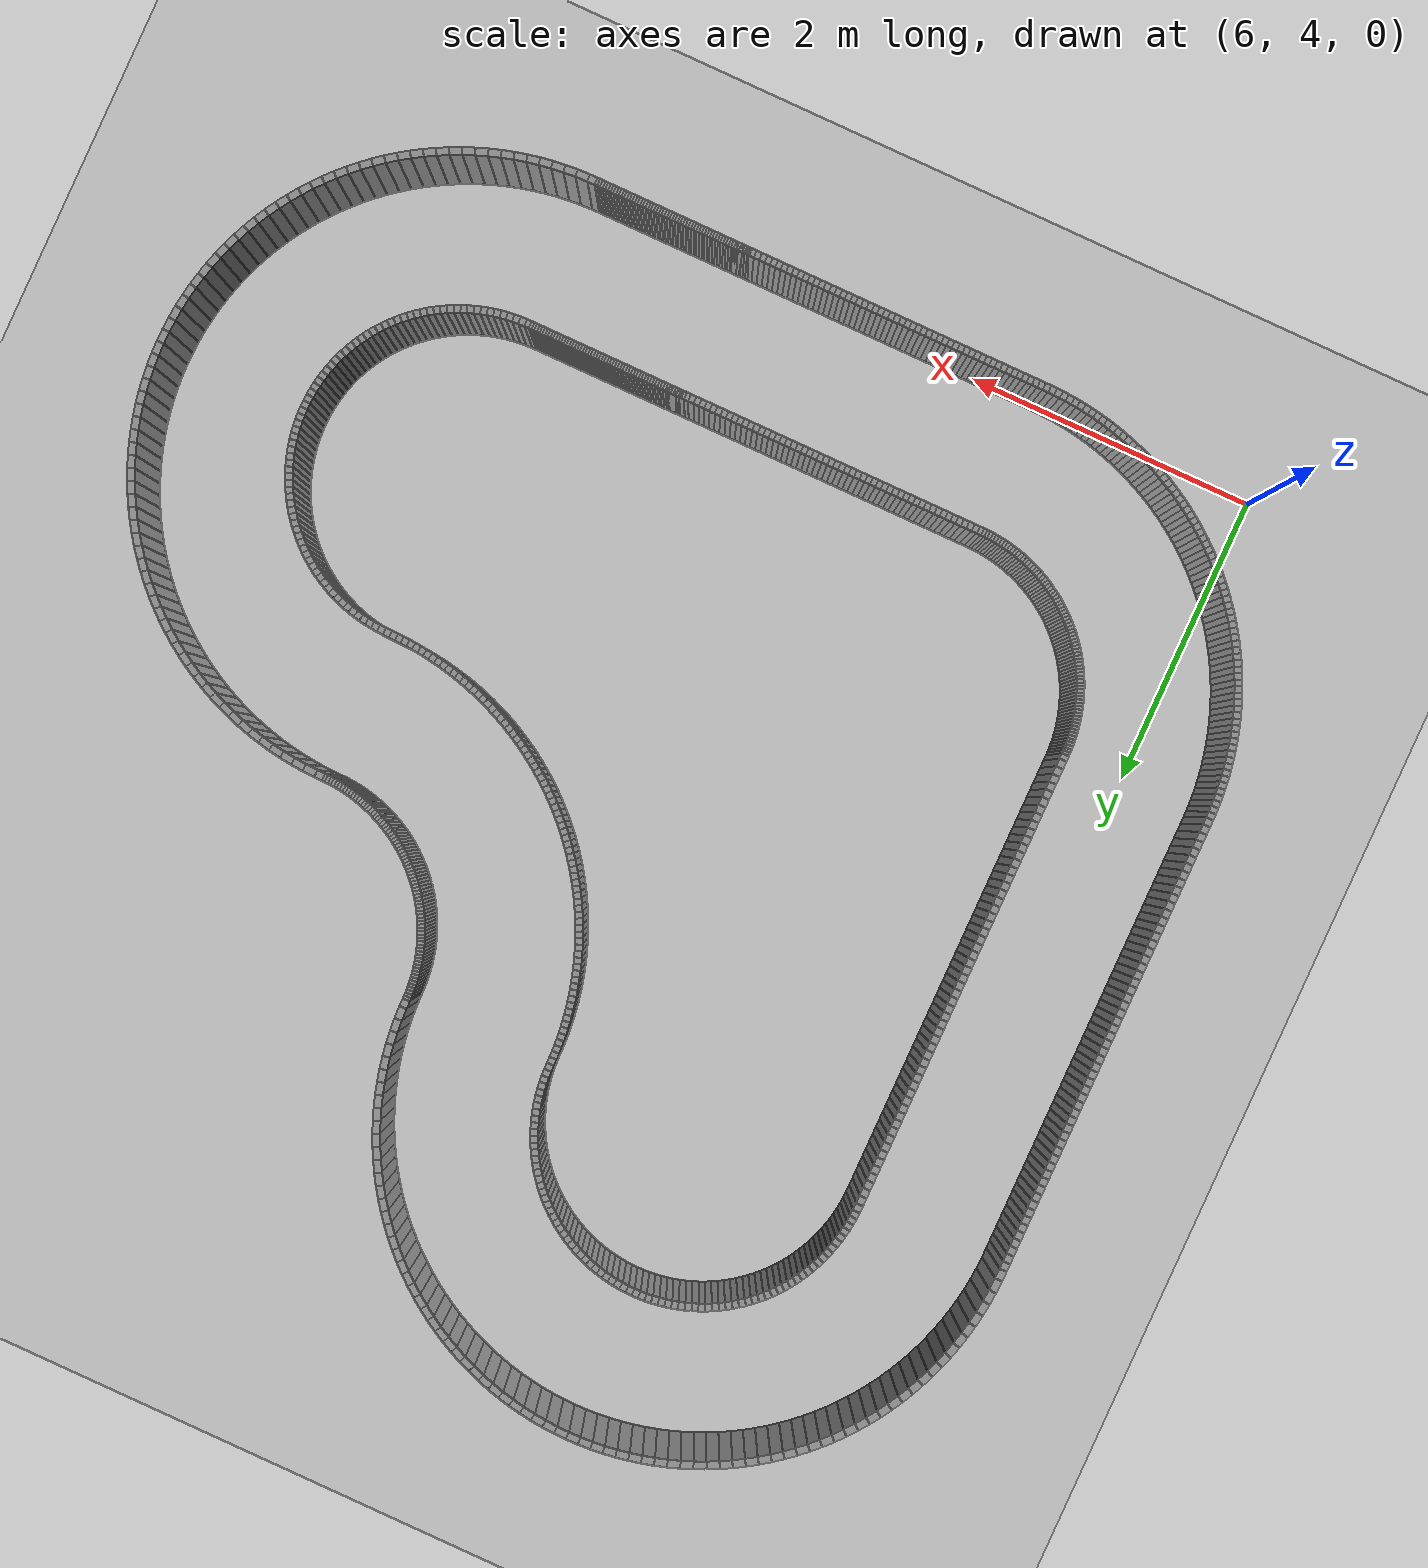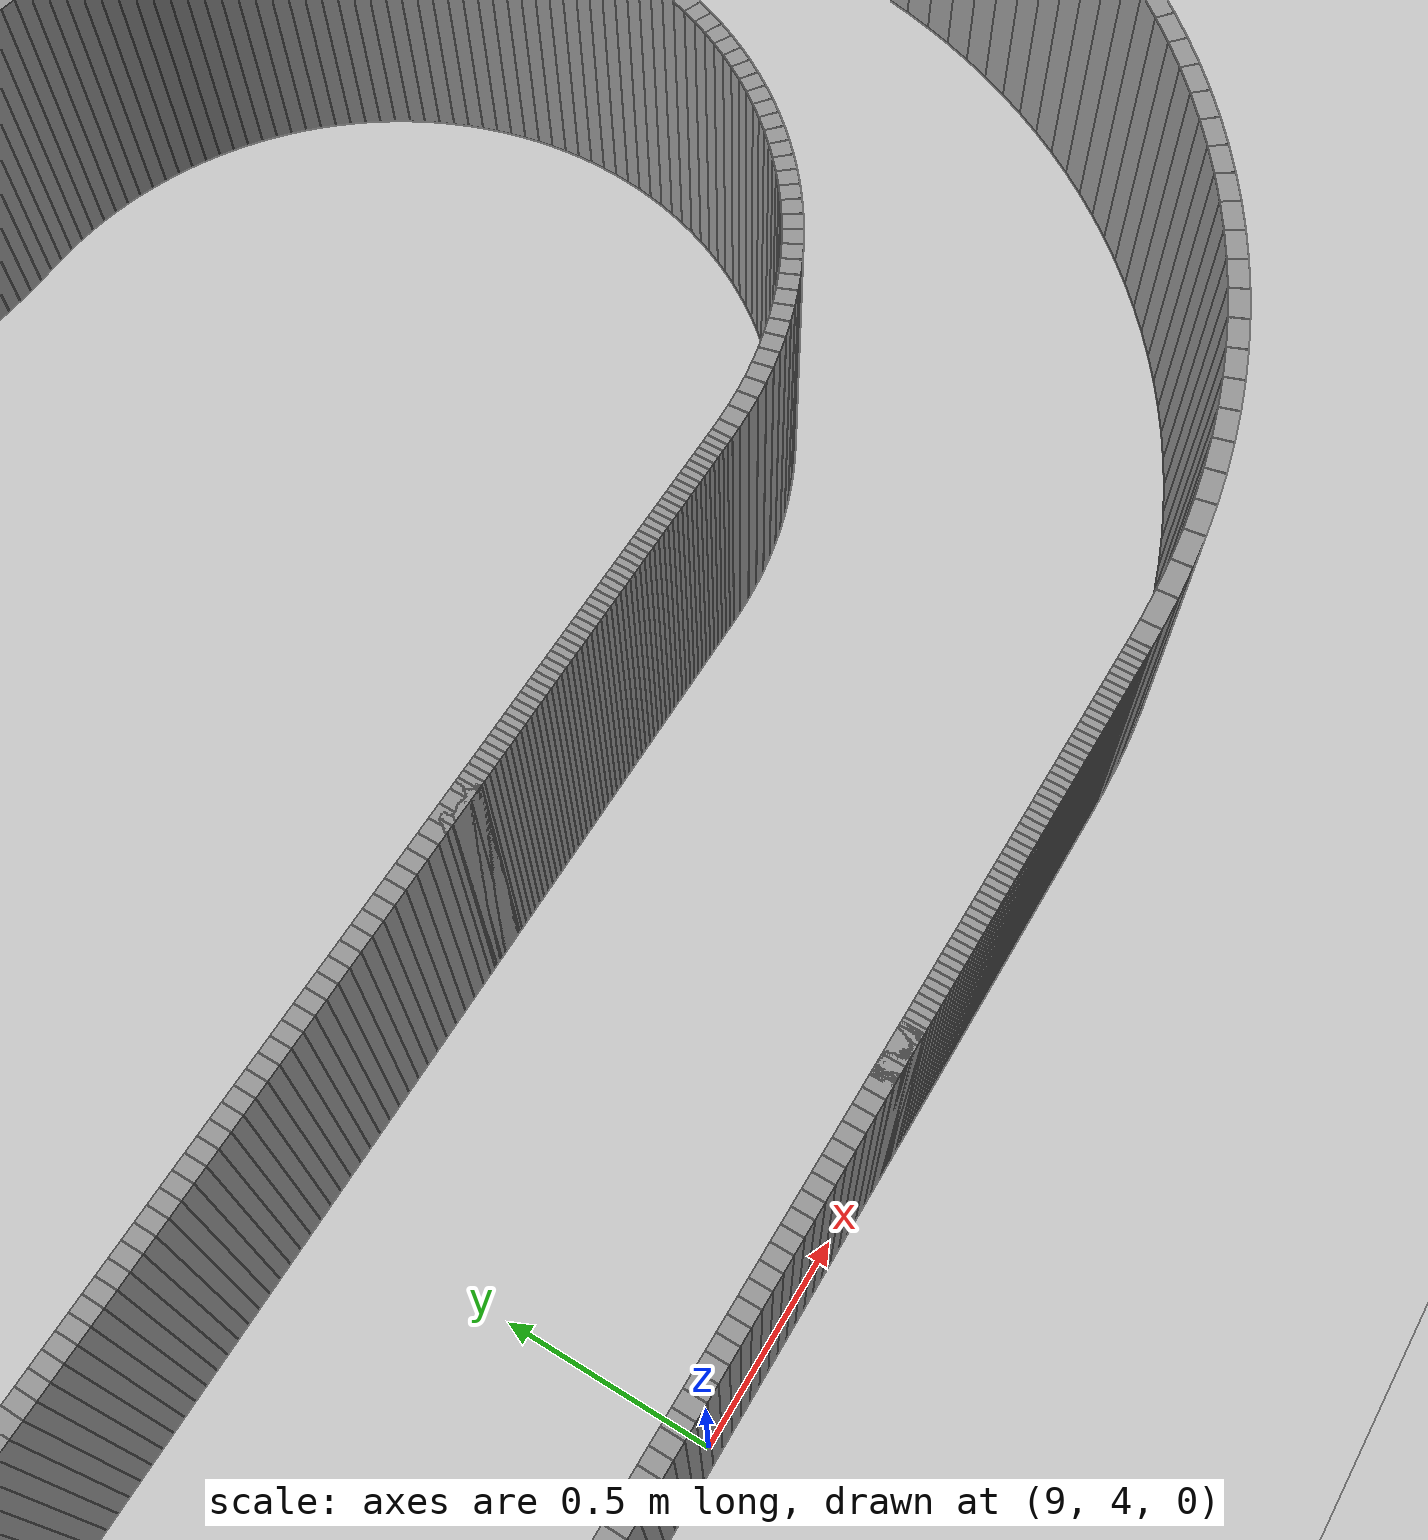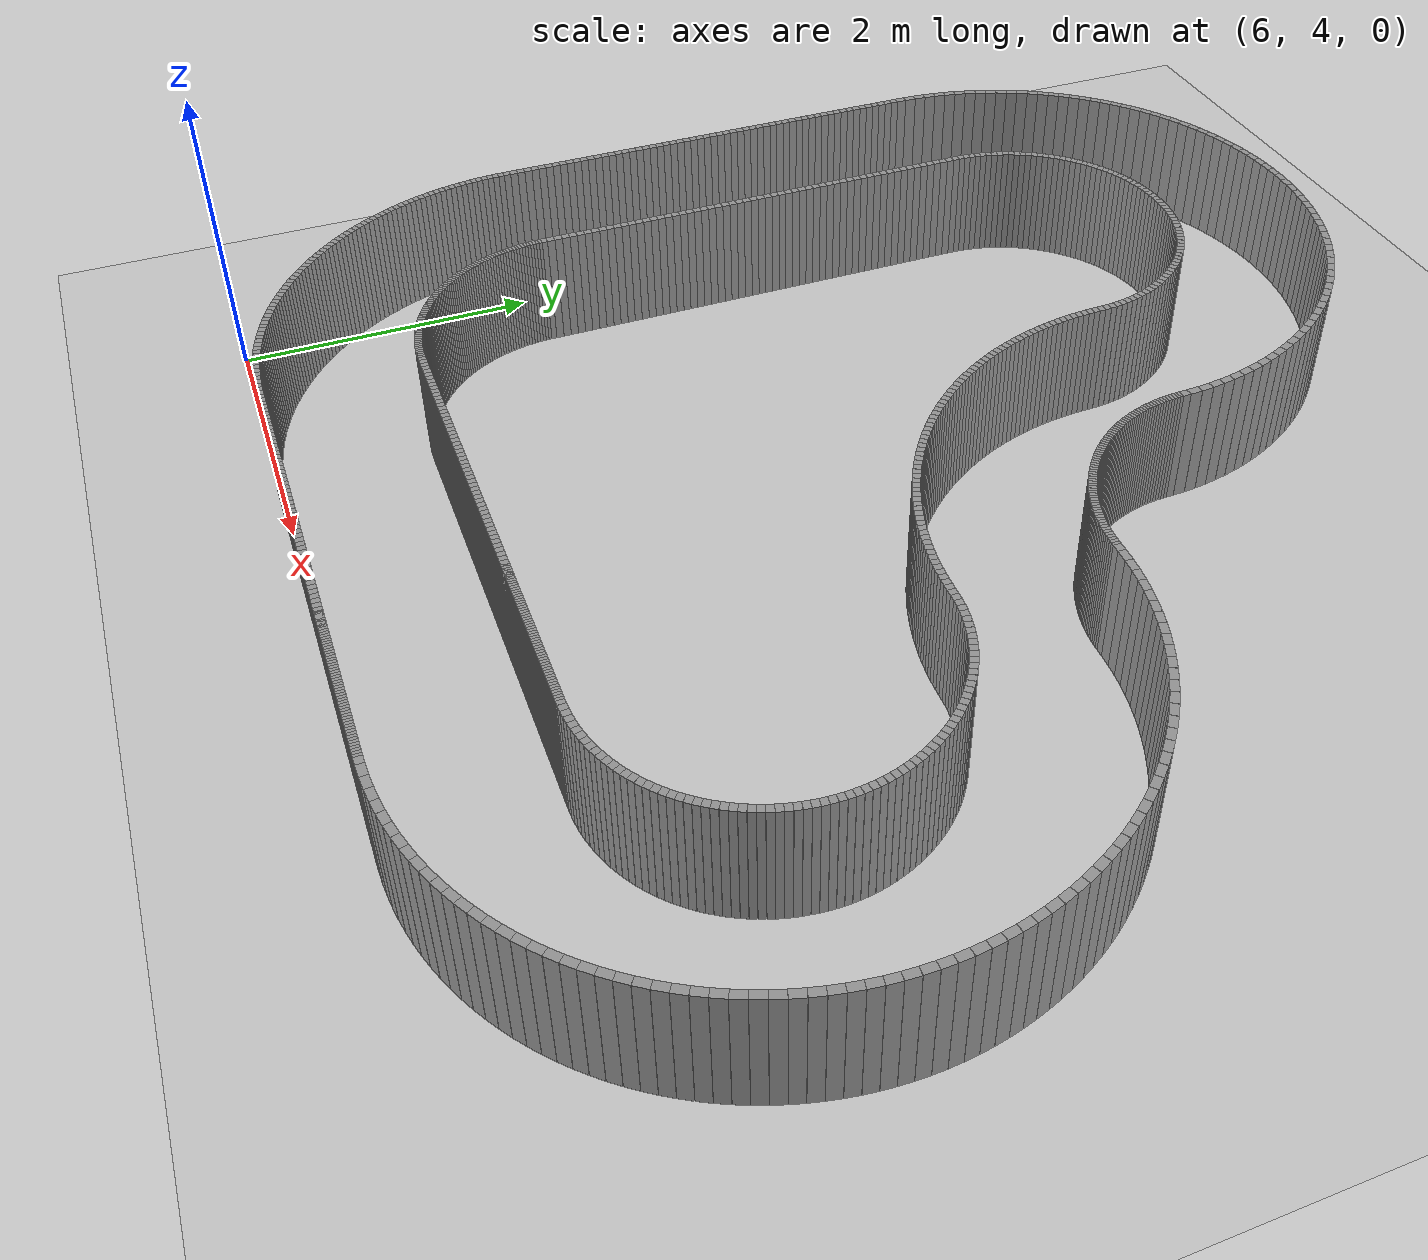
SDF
<sdf version="1.4">
 <world name="default">
  <scene><ambient>1 1 1 1</ambient><background>0.7 0.7 0.7 1</background><shadows>false</shadows></scene>
  <include><uri>model://sun</uri></include>
  <include><uri>model://ground_plane</uri></include>
  <physics type="ode">
   <real_time_update_rate>1000.0</real_time_update_rate>
   <max_step_size>0.001</max_step_size>
   <real_time_factor>1</real_time_factor>
   <ode>
    <solver>
     <type>quick</type>
     <iters>150</iters>
     <precon_iters>0</precon_iters>
     <sor>1.400000</sor>
     <use_dynamic_moi_rescaling>1</use_dynamic_moi_rescaling>
    </solver>
    <constraints>
     <cfm>0.00001</cfm>
     <erp>0.2</erp>
     <contact_max_correcting_vel>2000.000000</contact_max_correcting_vel>
     <contact_surface_layer>0.01000</contact_surface_layer>
    </constraints>
   </ode>
  </physics>
  <include><uri>model://path_walls</uri></include>
 </world>
</sdf>

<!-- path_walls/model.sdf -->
<sdf version='1.6'>
        <model name='path_walls'>
            <static>true</static>

    <model name='wall_left_0'>
      <static>true</static>
      <pose>9.64425922822256 5.0 0.40 0 0 0.0</pose>
      <link name='wall_link'>
        <visual name='wall_visual'>
          <geometry><box><size>0.01863748760820627 0.05 0.8</size></box></geometry>
          <material>
            <ambient>0.3 0.3 0.3 1</ambient>
            <diffuse>0.6 0.6 0.6 1</diffuse>
          </material>
        </visual>
        <collision name='wall_collision'>
          <geometry><box><size>0.01863748760820627 0.05 0.8</size></box></geometry>
        </collision>
      </link>
    </model>

    <model name='wall_left_1'>
      <static>true</static>
      <pose>9.662896715830767 5.0 0.40 0 0 0.0</pose>
      <link name='wall_link'>
        <visual name='wall_visual'>
          <geometry><box><size>0.01863748760820627 0.05 0.8</size></box></geometry>
          <material>
            <ambient>0.3 0.3 0.3 1</ambient>
            <diffuse>0.6 0.6 0.6 1</diffuse>
          </material>
        </visual>
        <collision name='wall_collision'>
          <geometry><box><size>0.01863748760820627 0.05 0.8</size></box></geometry>
        </collision>
      </link>
    </model>

    <model name='wall_left_2'>
      <static>true</static>
      <pose>9.681534203438975 5.0 0.40 0 0 0.0</pose>
      <link name='wall_link'>
        <visual name='wall_visual'>
          <geometry><box><size>0.018637487608208048 0.05 0.8</size></box></geometry>
          <material>
            <ambient>0.3 0.3 0.3 1</ambient>
            <diffuse>0.6 0.6 0.6 1</diffuse>
          </material>
        </visual>
        <collision name='wall_collision'>
          <geometry><box><size>0.018637487608208048 0.05 0.8</size></box></geometry>
        </collision>
      </link>
    </model>

    <model name='wall_left_3'>
      <static>true</static>
      <pose>9.700171691047181 5.0 0.40 0 0 0.0</pose>
      <link name='wall_link'>
        <visual name='wall_visual'>
          <geometry><box><size>0.018637487608208048 0.05 0.8</size></box></geometry>
          <material>
            <ambient>0.3 0.3 0.3 1</ambient>
            <diffuse>0.6 0.6 0.6 1</diffuse>
          </material>
        </visual>
        <collision name='wall_collision'>
          <geometry><box><size>0.018637487608208048 0.05 0.8</size></box></geometry>
        </collision>
      </link>
    </model>

    <model name='wall_left_4'>
      <static>true</static>
      <pose>9.71880917865539 5.0 0.40 0 0 0.0</pose>
      <link name='wall_link'>
        <visual name='wall_visual'>
          <geometry><box><size>0.01863748760820627 0.05 0.8</size></box></geometry>
          <material>
            <ambient>0.3 0.3 0.3 1</ambient>
            <diffuse>0.6 0.6 0.6 1</diffuse>
          </material>
        </visual>
        <collision name='wall_collision'>
          <geometry><box><size>0.01863748760820627 0.05 0.8</size></box></geometry>
        </collision>
      </link>
    </model>

    <model name='wall_left_5'>
      <static>true</static>
      <pose>9.737446666263597 5.0 0.40 0 0 0.0</pose>
      <link name='wall_link'>
        <visual name='wall_visual'>
          <geometry><box><size>0.018637487608208048 0.05 0.8</size></box></geometry>
          <material>
            <ambient>0.3 0.3 0.3 1</ambient>
            <diffuse>0.6 0.6 0.6 1</diffuse>
          </material>
        </visual>
        <collision name='wall_collision'>
          <geometry><box><size>0.018637487608208048 0.05 0.8</size></box></geometry>
        </collision>
      </link>
    </model>

    <model name='wall_left_6'>
      <static>true</static>
      <pose>9.756084153871804 5.0 0.40 0 0 0.0</pose>
      <link name='wall_link'>
        <visual name='wall_visual'>
          <geometry><box><size>0.018637487608208048 0.05 0.8</size></box></geometry>
          <material>
            <ambient>0.3 0.3 0.3 1</ambient>
            <diffuse>0.6 0.6 0.6 1</diffuse>
          </material>
        </visual>
        <collision name='wall_collision'>
          <geometry><box><size>0.018637487608208048 0.05 0.8</size></box></geometry>
        </collision>
      </link>
    </model>

    <model name='wall_left_7'>
      <static>true</static>
      <pose>9.774721641480014 5.0 0.40 0 0 0.0</pose>
      <link name='wall_link'>
        <visual name='wall_visual'>
          <geometry><box><size>0.018637487608208048 0.05 0.8</size></box></geometry>
          <material>
            <ambient>0.3 0.3 0.3 1</ambient>
            <diffuse>0.6 0.6 0.6 1</diffuse>
          </material>
        </visual>
        <collision name='wall_collision'>
          <geometry><box><size>0.018637487608208048 0.05 0.8</size></box></geometry>
        </collision>
      </link>
    </model>

    <model name='wall_left_8'>
      <static>true</static>
      <pose>9.793359129088218 5.0 0.40 0 0 0.0</pose>
      <link name='wall_link'>
        <visual name='wall_visual'>
          <geometry><box><size>0.01863748760820272 0.05 0.8</size></box></geometry>
          <material>
            <ambient>0.3 0.3 0.3 1</ambient>
            <diffuse>0.6 0.6 0.6 1</diffuse>
          </material>
        </visual>
        <collision name='wall_collision'>
          <geometry><box><size>0.01863748760820272 0.05 0.8</size></box></geometry>
        </collision>
      </link>
    </model>

    <model name='wall_left_9'>
      <static>true</static>
      <pose>9.811996616696424 5.0 0.40 0 0 0.0</pose>
      <link name='wall_link'>
        <visual name='wall_visual'>
          <geometry><box><size>0.018637487608209824 0.05 0.8</size></box></geometry>
          <material>
            <ambient>0.3 0.3 0.3 1</ambient>
            <diffuse>0.6 0.6 0.6 1</diffuse>
          </material>
        </visual>
        <collision name='wall_collision'>
          <geometry><box><size>0.018637487608209824 0.05 0.8</size></box></geometry>
        </collision>
      </link>
    </model>

    <model name='wall_left_10'>
      <static>true</static>
      <pose>9.830634104304632 5.0 0.40 0 0 0.0</pose>
      <link name='wall_link'>
        <visual name='wall_visual'>
          <geometry><box><size>0.01863748760820627 0.05 0.8</size></box></geometry>
          <material>
            <ambient>0.3 0.3 0.3 1</ambient>
            <diffuse>0.6 0.6 0.6 1</diffuse>
          </material>
        </visual>
        <collision name='wall_collision'>
          <geometry><box><size>0.01863748760820627 0.05 0.8</size></box></geometry>
        </collision>
      </link>
    </model>

    <model name='wall_left_11'>
      <static>true</static>
      <pose>9.849271591912839 5.0 0.40 0 0 0.0</pose>
      <link name='wall_link'>
        <visual name='wall_visual'>
          <geometry><box><size>0.018637487608208048 0.05 0.8</size></box></geometry>
          <material>
            <ambient>0.3 0.3 0.3 1</ambient>
            <diffuse>0.6 0.6 0.6 1</diffuse>
          </material>
        </visual>
        <collision name='wall_collision'>
          <geometry><box><size>0.018637487608208048 0.05 0.8</size></box></geometry>
        </collision>
      </link>
    </model>

    <model name='wall_left_12'>
      <static>true</static>
      <pose>9.867909079521047 5.0 0.40 0 0 0.0</pose>
      <link name='wall_link'>
        <visual name='wall_visual'>
          <geometry><box><size>0.01863748760820627 0.05 0.8</size></box></geometry>
          <material>
            <ambient>0.3 0.3 0.3 1</ambient>
            <diffuse>0.6 0.6 0.6 1</diffuse>
          </material>
        </visual>
        <collision name='wall_collision'>
          <geometry><box><size>0.01863748760820627 0.05 0.8</size></box></geometry>
        </collision>
      </link>
    </model>

    <model name='wall_left_13'>
      <static>true</static>
      <pose>9.886546567129255 5.0 0.40 0 0 0.0</pose>
      <link name='wall_link'>
        <visual name='wall_visual'>
          <geometry><box><size>0.018637487608208048 0.05 0.8</size></box></geometry>
          <material>
            <ambient>0.3 0.3 0.3 1</ambient>
            <diffuse>0.6 0.6 0.6 1</diffuse>
          </material>
        </visual>
        <collision name='wall_collision'>
          <geometry><box><size>0.018637487608208048 0.05 0.8</size></box></geometry>
        </collision>
      </link>
    </model>

    <model name='wall_left_14'>
      <static>true</static>
      <pose>9.905184054737461 5.0 0.40 0 0 0.0</pose>
      <link name='wall_link'>
        <visual name='wall_visual'>
          <geometry><box><size>0.018637487608208048 0.05 0.8</size></box></geometry>
          <material>
            <ambient>0.3 0.3 0.3 1</ambient>
            <diffuse>0.6 0.6 0.6 1</diffuse>
          </material>
        </visual>
        <collision name='wall_collision'>
          <geometry><box><size>0.018637487608208048 0.05 0.8</size></box></geometry>
        </collision>
      </link>
    </model>

    <model name='wall_left_15'>
      <static>true</static>
      <pose>9.923821542345669 5.0 0.40 0 0 0.0</pose>
      <link name='wall_link'>
        <visual name='wall_visual'>
          <geometry><box><size>0.01863748760820627 0.05 0.8</size></box></geometry>
          <material>
            <ambient>0.3 0.3 0.3 1</ambient>
            <diffuse>0.6 0.6 0.6 1</diffuse>
          </material>
        </visual>
        <collision name='wall_collision'>
          <geometry><box><size>0.01863748760820627 0.05 0.8</size></box></geometry>
        </collision>
      </link>
    </model>

    <model name='wall_left_16'>
      <static>true</static>
      <pose>9.942459029953875 5.0 0.40 0 0 0.0</pose>
      <link name='wall_link'>
        <visual name='wall_visual'>
          <geometry><box><size>0.01863748760820627 0.05 0.8</size></box></geometry>
          <material>
            <ambient>0.3 0.3 0.3 1</ambient>
            <diffuse>0.6 0.6 0.6 1</diffuse>
          </material>
        </visual>
        <collision name='wall_collision'>
          <geometry><box><size>0.01863748760820627 0.05 0.8</size></box></geometry>
        </collision>
      </link>
    </model>

    <model name='wall_left_17'>
      <static>true</static>
      <pose>9.961096517562083 5.0 0.40 0 0 0.0</pose>
      <link name='wall_link'>
        <visual name='wall_visual'>
          <geometry><box><size>0.018637487608208048 0.05 0.8</size></box></geometry>
          <material>
            <ambient>0.3 0.3 0.3 1</ambient>
            <diffuse>0.6 0.6 0.6 1</diffuse>
          </material>
        </visual>
        <collision name='wall_collision'>
          <geometry><box><size>0.018637487608208048 0.05 0.8</size></box></geometry>
        </collision>
      </link>
    </model>

    <model name='wall_left_18'>
      <static>true</static>
      <pose>9.979734005170291 5.0 0.40 0 0 0.0</pose>
      <link name='wall_link'>
        <visual name='wall_visual'>
          <geometry><box><size>0.018637487608209824 0.05 0.8</size></box></geometry>
          <material>
            <ambient>0.3 0.3 0.3 1</ambient>
            <diffuse>0.6 0.6 0.6 1</diffuse>
          </material>
        </visual>
        <collision name='wall_collision'>
          <geometry><box><size>0.018637487608209824 0.05 0.8</size></box></geometry>
        </collision>
      </link>
    </model>

    <model name='wall_left_19'>
      <static>true</static>
      <pose>9.9983714927785 5.0 0.40 0 0 0.0</pose>
      <link name='wall_link'>
        <visual name='wall_visual'>
          <geometry><box><size>0.018637487608204495 0.05 0.8</size></box></geometry>
          <material>
            <ambient>0.3 0.3 0.3 1</ambient>
            <diffuse>0.6 0.6 0.6 1</diffuse>
          </material>
        </visual>
        <collision name='wall_collision'>
          <geometry><box><size>0.018637487608204495 0.05 0.8</size></box></geometry>
        </collision>
      </link>
    </model>

    <model name='wall_left_20'>
      <static>true</static>
      <pose>10.017008980386706 5.0 0.40 0 0 0.0</pose>
      <link name='wall_link'>
        <visual name='wall_visual'>
          <geometry><box><size>0.018637487608208048 0.05 0.8</size></box></geometry>
          <material>
            <ambient>0.3 0.3 0.3 1</ambient>
            <diffuse>0.6 0.6 0.6 1</diffuse>
          </material>
        </visual>
        <collision name='wall_collision'>
          <geometry><box><size>0.018637487608208048 0.05 0.8</size></box></geometry>
        </collision>
      </link>
    </model>

    <model name='wall_left_21'>
      <static>true</static>
      <pose>10.035646467994912 5.0 0.40 0 0 0.0</pose>
      <link name='wall_link'>
        <visual name='wall_visual'>
          <geometry><box><size>0.01863748760820627 0.05 0.8</size></box></geometry>
          <material>
            <ambient>0.3 0.3 0.3 1</ambient>
            <diffuse>0.6 0.6 0.6 1</diffuse>
          </material>
        </visual>
        <collision name='wall_collision'>
          <geometry><box><size>0.01863748760820627 0.05 0.8</size></box></geometry>
        </collision>
      </link>
    </model>

    <model name='wall_left_22'>
      <static>true</static>
      <pose>10.054283955603118 5.0 0.40 0 0 0.0</pose>
      <link name='wall_link'>
        <visual name='wall_visual'>
          <geometry><box><size>0.018637487608208048 0.05 0.8</size></box></geometry>
          <material>
            <ambient>0.3 0.3 0.3 1</ambient>
            <diffuse>0.6 0.6 0.6 1</diffuse>
          </material>
        </visual>
        <collision name='wall_collision'>
          <geometry><box><size>0.018637487608208048 0.05 0.8</size></box></geometry>
        </collision>
      </link>
    </model>

    <model name='wall_left_23'>
      <static>true</static>
      <pose>10.072921443211326 5.0 0.40 0 0 0.0</pose>
      <link name='wall_link'>
        <visual name='wall_visual'>
          <geometry><box><size>0.01863748760820627 0.05 0.8</size></box></geometry>
          <material>
            <ambient>0.3 0.3 0.3 1</ambient>
            <diffuse>0.6 0.6 0.6 1</diffuse>
          </material>
        </visual>
        <collision name='wall_collision'>
          <geometry><box><size>0.01863748760820627 0.05 0.8</size></box></geometry>
        </collision>
      </link>
    </model>

    <model name='wall_left_24'>
      <static>true</static>
      <pose>10.091558930819534 5.0 0.40 0 0 0.0</pose>
      <link name='wall_link'>
        <visual name='wall_visual'>
          <geometry><box><size>0.018637487608208048 0.05 0.8</size></box></geometry>
          <material>
            <ambient>0.3 0.3 0.3 1</ambient>
            <diffuse>0.6 0.6 0.6 1</diffuse>
          </material>
        </visual>
        <collision name='wall_collision'>
          <geometry><box><size>0.018637487608208048 0.05 0.8</size></box></geometry>
        </collision>
      </link>
    </model>

    <model name='wall_left_25'>
      <static>true</static>
      <pose>10.11019641842774 5.0 0.40 0 0 0.0</pose>
      <link name='wall_link'>
        <visual name='wall_visual'>
          <geometry><box><size>0.01863748760820627 0.05 0.8</size></box></geometry>
          <material>
            <ambient>0.3 0.3 0.3 1</ambient>
            <diffuse>0.6 0.6 0.6 1</diffuse>
          </material>
        </visual>
        <collision name='wall_collision'>
          <geometry><box><size>0.01863748760820627 0.05 0.8</size></box></geometry>
        </collision>
      </link>
    </model>

    <model name='wall_left_26'>
      <static>true</static>
      <pose>10.128833906035947 5.0 0.40 0 0 0.0</pose>
      <link name='wall_link'>
        <visual name='wall_visual'>
          <geometry><box><size>0.018637487608208048 0.05 0.8</size></box></geometry>
          <material>
            <ambient>0.3 0.3 0.3 1</ambient>
            <diffuse>0.6 0.6 0.6 1</diffuse>
          </material>
        </visual>
        <collision name='wall_collision'>
          <geometry><box><size>0.018637487608208048 0.05 0.8</size></box></geometry>
        </collision>
      </link>
    </model>

    <model name='wall_left_27'>
      <static>true</static>
      <pose>10.147471393644155 5.0 0.40 0 0 0.0</pose>
      <link name='wall_link'>
        <visual name='wall_visual'>
          <geometry><box><size>0.01863748760820627 0.05 0.8</size></box></geometry>
          <material>
            <ambient>0.3 0.3 0.3 1</ambient>
            <diffuse>0.6 0.6 0.6 1</diffuse>
          </material>
        </visual>
        <collision name='wall_collision'>
          <geometry><box><size>0.01863748760820627 0.05 0.8</size></box></geometry>
        </collision>
      </link>
    </model>

    <model name='wall_left_28'>
      <static>true</static>
      <pose>10.166108881252363 5.0 0.40 0 0 0.0</pose>
      <link name='wall_link'>
        <visual name='wall_visual'>
          <geometry><box><size>0.018637487608208048 0.05 0.8</size></box></geometry>
          <material>
            <ambient>0.3 0.3 0.3 1</ambient>
            <diffuse>0.6 0.6 0.6 1</diffuse>
          </material>
        </visual>
        <collision name='wall_collision'>
          <geometry><box><size>0.018637487608208048 0.05 0.8</size></box></geometry>
        </collision>
      </link>
    </model>

    <model name='wall_left_29'>
      <static>true</static>
      <pose>10.18474636886057 5.0 0.40 0 0 0.0</pose>
      <link name='wall_link'>
        <visual name='wall_visual'>
          <geometry><box><size>0.01863748760820627 0.05 0.8</size></box></geometry>
          <material>
            <ambient>0.3 0.3 0.3 1</ambient>
            <diffuse>0.6 0.6 0.6 1</diffuse>
          </material>
        </visual>
        <collision name='wall_collision'>
          <geometry><box><size>0.01863748760820627 0.05 0.8</size></box></geometry>
        </collision>
      </link>
    </model>

    <model name='wall_left_30'>
      <static>true</static>
      <pose>10.203383856468776 5.0 0.40 0 0 0.0</pose>
      <link name='wall_link'>
        <visual name='wall_visual'>
          <geometry><box><size>0.018637487608208048 0.05 0.8</size></box></geometry>
          <material>
            <ambient>0.3 0.3 0.3 1</ambient>
            <diffuse>0.6 0.6 0.6 1</diffuse>
          </material>
        </visual>
        <collision name='wall_collision'>
          <geometry><box><size>0.018637487608208048 0.05 0.8</size></box></geometry>
        </collision>
      </link>
    </model>

    <model name='wall_left_31'>
      <static>true</static>
      <pose>10.222021344076985 5.0 0.40 0 0 0.0</pose>
      <link name='wall_link'>
        <visual name='wall_visual'>
          <geometry><box><size>0.018637487608208048 0.05 0.8</size></box></geometry>
          <material>
            <ambient>0.3 0.3 0.3 1</ambient>
            <diffuse>0.6 0.6 0.6 1</diffuse>
          </material>
        </visual>
        <collision name='wall_collision'>
          <geometry><box><size>0.018637487608208048 0.05 0.8</size></box></geometry>
        </collision>
      </link>
    </model>

    <model name='wall_left_32'>
      <static>true</static>
      <pose>10.240658831685192 5.0 0.40 0 0 0.0</pose>
      <link name='wall_link'>
        <visual name='wall_visual'>
          <geometry><box><size>0.018637487608208048 0.05 0.8</size></box></geometry>
          <material>
            <ambient>0.3 0.3 0.3 1</ambient>
            <diffuse>0.6 0.6 0.6 1</diffuse>
          </material>
        </visual>
        <collision name='wall_collision'>
          <geometry><box><size>0.018637487608208048 0.05 0.8</size></box></geometry>
        </collision>
      </link>
    </model>

    <model name='wall_left_33'>
      <static>true</static>
      <pose>10.259296319293401 5.0 0.40 0 0 0.0</pose>
      <link name='wall_link'>
        <visual name='wall_visual'>
          <geometry><box><size>0.018637487608208048 0.05 0.8</size></box></geometry>
          <material>
            <ambient>0.3 0.3 0.3 1</ambient>
            <diffuse>0.6 0.6 0.6 1</diffuse>
          </material>
        </visual>
        <collision name='wall_collision'>
          <geometry><box><size>0.018637487608208048 0.05 0.8</size></box></geometry>
        </collision>
      </link>
    </model>

    <model name='wall_left_34'>
      <static>true</static>
      <pose>10.277933806901606 5.0 0.40 0 0 0.0</pose>
      <link name='wall_link'>
        <visual name='wall_visual'>
          <geometry><box><size>0.01863748760820272 0.05 0.8</size></box></geometry>
          <material>
            <ambient>0.3 0.3 0.3 1</ambient>
            <diffuse>0.6 0.6 0.6 1</diffuse>
          </material>
        </visual>
        <collision name='wall_collision'>
          <geometry><box><size>0.01863748760820272 0.05 0.8</size></box></geometry>
        </collision>
      </link>
    </model>

    <model name='wall_left_35'>
      <static>true</static>
      <pose>10.29657129450981 5.0 0.40 0 0 0.0</pose>
      <link name='wall_link'>
        <visual name='wall_visual'>
          <geometry><box><size>0.018637487608208048 0.05 0.8</size></box></geometry>
          <material>
            <ambient>0.3 0.3 0.3 1</ambient>
            <diffuse>0.6 0.6 0.6 1</diffuse>
          </material>
        </visual>
        <collision name='wall_collision'>
          <geometry><box><size>0.018637487608208048 0.05 0.8</size></box></geometry>
        </collision>
      </link>
    </model>

    <model name='wall_left_36'>
      <static>true</static>
      <pose>10.31520878211802 5.0 0.40 0 0 0.0</pose>
      <link name='wall_link'>
        <visual name='wall_visual'>
          <geometry><box><size>0.018637487608208048 0.05 0.8</size></box></geometry>
          <material>
            <ambient>0.3 0.3 0.3 1</ambient>
            <diffuse>0.6 0.6 0.6 1</diffuse>
          </material>
        </visual>
        <collision name='wall_collision'>
          <geometry><box><size>0.018637487608208048 0.05 0.8</size></box></geometry>
        </collision>
      </link>
    </model>

    <model name='wall_left_37'>
      <static>true</static>
      <pose>10.333846269726227 5.0 0.40 0 0 0.0</pose>
      <link name='wall_link'>
        <visual name='wall_visual'>
          <geometry><box><size>0.018637487608208048 0.05 0.8</size></box></geometry>
          <material>
            <ambient>0.3 0.3 0.3 1</ambient>
            <diffuse>0.6 0.6 0.6 1</diffuse>
          </material>
        </visual>
        <collision name='wall_collision'>
          <geometry><box><size>0.018637487608208048 0.05 0.8</size></box></geometry>
        </collision>
      </link>
    </model>

    <model name='wall_left_38'>
      <static>true</static>
      <pose>10.352483757334435 5.0 0.40 0 0 0.0</pose>
      <link name='wall_link'>
        <visual name='wall_visual'>
          <geometry><box><size>0.01863748760820627 0.05 0.8</size></box></geometry>
          <material>
            <ambient>0.3 0.3 0.3 1</ambient>
            <diffuse>0.6 0.6 0.6 1</diffuse>
          </material>
        </visual>
        <collision name='wall_collision'>
          <geometry><box><size>0.01863748760820627 0.05 0.8</size></box></geometry>
        </collision>
      </link>
    </model>

    <model name='wall_left_39'>
      <static>true</static>
      <pose>10.371121244942643 5.0 0.40 0 0 0.0</pose>
      <link name='wall_link'>
        <visual name='wall_visual'>
          <geometry><box><size>0.018637487608208048 0.05 0.8</size></box></geometry>
          <material>
            <ambient>0.3 0.3 0.3 1</ambient>
            <diffuse>0.6 0.6 0.6 1</diffuse>
          </material>
        </visual>
        <collision name='wall_collision'>
          <geometry><box><size>0.018637487608208048 0.05 0.8</size></box></geometry>
        </collision>
      </link>
    </model>

    <model name='wall_left_40'>
      <static>true</static>
      <pose>10.389758732550849 5.0 0.40 0 0 0.0</pose>
      <link name='wall_link'>
        <visual name='wall_visual'>
          <geometry><box><size>0.01863748760820627 0.05 0.8</size></box></geometry>
          <material>
            <ambient>0.3 0.3 0.3 1</ambient>
            <diffuse>0.6 0.6 0.6 1</diffuse>
          </material>
        </visual>
        <collision name='wall_collision'>
          <geometry><box><size>0.01863748760820627 0.05 0.8</size></box></geometry>
        </collision>
      </link>
    </model>

    <model name='wall_left_41'>
      <static>true</static>
      <pose>10.408396220159055 5.0 0.40 0 0 0.0</pose>
      <link name='wall_link'>
        <visual name='wall_visual'>
          <geometry><box><size>0.018637487608208048 0.05 0.8</size></box></geometry>
          <material>
            <ambient>0.3 0.3 0.3 1</ambient>
            <diffuse>0.6 0.6 0.6 1</diffuse>
          </material>
        </visual>
        <collision name='wall_collision'>
          <geometry><box><size>0.018637487608208048 0.05 0.8</size></box></geometry>
        </collision>
      </link>
    </model>

    <model name='wall_left_42'>
      <static>true</static>
      <pose>10.427033707767263 5.0 0.40 0 0 0.0</pose>
      <link name='wall_link'>
        <visual name='wall_visual'>
          <geometry><box><size>0.01863748760820627 0.05 0.8</size></box></geometry>
          <material>
            <ambient>0.3 0.3 0.3 1</ambient>
            <diffuse>0.6 0.6 0.6 1</diffuse>
          </material>
        </visual>
        <collision name='wall_collision'>
          <geometry><box><size>0.01863748760820627 0.05 0.8</size></box></geometry>
        </collision>
      </link>
    </model>

    <model name='wall_left_43'>
      <static>true</static>
      <pose>10.445671195375471 5.0 0.40 0 0 0.0</pose>
      <link name='wall_link'>
        <visual name='wall_visual'>
          <geometry><box><size>0.018637487608208048 0.05 0.8</size></box></geometry>
          <material>
            <ambient>0.3 0.3 0.3 1</ambient>
            <diffuse>0.6 0.6 0.6 1</diffuse>
          </material>
        </visual>
        <collision name='wall_collision'>
          <geometry><box><size>0.018637487608208048 0.05 0.8</size></box></geometry>
        </collision>
      </link>
    </model>

    <model name='wall_left_44'>
      <static>true</static>
      <pose>10.464308682983678 5.0 0.40 0 0 0.0</pose>
      <link name='wall_link'>
        <visual name='wall_visual'>
          <geometry><box><size>0.01863748760820627 0.05 0.8</size></box></geometry>
          <material>
            <ambient>0.3 0.3 0.3 1</ambient>
            <diffuse>0.6 0.6 0.6 1</diffuse>
          </material>
        </visual>
        <collision name='wall_collision'>
          <geometry><box><size>0.01863748760820627 0.05 0.8</size></box></geometry>
        </collision>
      </link>
    </model>

    <model name='wall_left_45'>
      <static>true</static>
      <pose>10.482946170591884 5.0 0.40 0 0 0.0</pose>
      <link name='wall_link'>
        <visual name='wall_visual'>
          <geometry><box><size>0.018637487608208048 0.05 0.8</size></box></geometry>
          <material>
            <ambient>0.3 0.3 0.3 1</ambient>
            <diffuse>0.6 0.6 0.6 1</diffuse>
          </material>
        </visual>
        <collision name='wall_collision'>
          <geometry><box><size>0.018637487608208048 0.05 0.8</size></box></geometry>
        </collision>
      </link>
    </model>

    <model name='wall_left_46'>
      <static>true</static>
      <pose>10.501583658200094 5.0 0.40 0 0 0.0</pose>
      <link name='wall_link'>
        <visual name='wall_visual'>
          <geometry><box><size>0.018637487608208048 0.05 0.8</size></box></geometry>
          <material>
            <ambient>0.3 0.3 0.3 1</ambient>
            <diffuse>0.6 0.6 0.6 1</diffuse>
          </material>
        </visual>
        <collision name='wall_collision'>
          <geometry><box><size>0.018637487608208048 0.05 0.8</size></box></geometry>
        </collision>
      </link>
    </model>

    <model name='wall_left_47'>
      <static>true</static>
      <pose>10.5202211458083 5.0 0.40 0 0 0.0</pose>
      <link name='wall_link'>
        <visual name='wall_visual'>
          <geometry><box><size>0.018637487608208048 0.05 0.8</size></box></geometry>
          <material>
            <ambient>0.3 0.3 0.3 1</ambient>
            <diffuse>0.6 0.6 0.6 1</diffuse>
          </material>
        </visual>
        <collision name='wall_collision'>
          <geometry><box><size>0.018637487608208048 0.05 0.8</size></box></geometry>
        </collision>
      </link>
    </model>

    <model name='wall_left_48'>
      <static>true</static>
      <pose>10.538858633416506 5.0 0.40 0 0 0.0</pose>
      <link name='wall_link'>
        <visual name='wall_visual'>
          <geometry><box><size>0.018637487608204495 0.05 0.8</size></box></geometry>
          <material>
            <ambient>0.3 0.3 0.3 1</ambient>
            <diffuse>0.6 0.6 0.6 1</diffuse>
          </material>
        </visual>
        <collision name='wall_collision'>
          <geometry><box><size>0.018637487608204495 0.05 0.8</size></box></geometry>
        </collision>
      </link>
    </model>

    <model name='wall_left_49'>
      <static>true</static>
      <pose>10.557496121024712 5.0 0.40 0 0 0.0</pose>
      <link name='wall_link'>
        <visual name='wall_visual'>
          <geometry><box><size>0.01863748760820627 0.05 0.8</size></box></geometry>
          <material>
            <ambient>0.3 0.3 0.3 1</ambient>
            <diffuse>0.6 0.6 0.6 1</diffuse>
          </material>
        </visual>
        <collision name='wall_collision'>
          <geometry><box><size>0.01863748760820627 0.05 0.8</size></box></geometry>
        </collision>
      </link>
    </model>

    <model name='wall_left_50'>
      <static>true</static>
      <pose>10.576133608632919 5.0 0.40 0 0 0.0</pose>
      <link name='wall_link'>
        <visual name='wall_visual'>
          <geometry><box><size>0.018637487608208048 0.05 0.8</size></box></geometry>
          <material>
            <ambient>0.3 0.3 0.3 1</ambient>
            <diffuse>0.6 0.6 0.6 1</diffuse>
          </material>
        </visual>
        <collision name='wall_collision'>
          <geometry><box><size>0.018637487608208048 0.05 0.8</size></box></geometry>
        </collision>
      </link>
    </model>

    <model name='wall_left_51'>
      <static>true</static>
      <pose>10.594771096241129 5.0 0.40 0 0 0.0</pose>
      <link name='wall_link'>
        <visual name='wall_visual'>
          <geometry><box><size>0.018637487608208048 0.05 0.8</size></box></geometry>
          <material>
            <ambient>0.3 0.3 0.3 1</ambient>
            <diffuse>0.6 0.6 0.6 1</diffuse>
          </material>
        </visual>
        <collision name='wall_collision'>
          <geometry><box><size>0.018637487608208048 0.05 0.8</size></box></geometry>
        </collision>
      </link>
    </model>

    <model name='wall_left_52'>
      <static>true</static>
      <pose>10.613408583849335 5.0 0.40 0 0 0.0</pose>
      <link name='wall_link'>
        <visual name='wall_visual'>
          <geometry><box><size>0.018637487608208048 0.05 0.8</size></box></geometry>
          <material>
            <ambient>0.3 0.3 0.3 1</ambient>
            <diffuse>0.6 0.6 0.6 1</diffuse>
          </material>
        </visual>
        <collision name='wall_collision'>
          <geometry><box><size>0.018637487608208048 0.05 0.8</size></box></geometry>
        </collision>
      </link>
    </model>

    <model name='wall_left_53'>
      <static>true</static>
      <pose>10.632046071457543 5.0 0.40 0 0 0.0</pose>
      <link name='wall_link'>
        <visual name='wall_visual'>
          <geometry><box><size>0.01863748760820627 0.05 0.8</size></box></geometry>
          <material>
            <ambient>0.3 0.3 0.3 1</ambient>
            <diffuse>0.6 0.6 0.6 1</diffuse>
          </material>
        </visual>
        <collision name='wall_collision'>
          <geometry><box><size>0.01863748760820627 0.05 0.8</size></box></geometry>
        </collision>
      </link>
    </model>

    <model name='wall_left_54'>
      <static>true</static>
      <pose>10.650683559065751 5.0 0.40 0 0 0.0</pose>
      <link name='wall_link'>
        <visual name='wall_visual'>
          <geometry><box><size>0.018637487608208048 0.05 0.8</size></box></geometry>
          <material>
            <ambient>0.3 0.3 0.3 1</ambient>
            <diffuse>0.6 0.6 0.6 1</diffuse>
          </material>
        </visual>
        <collision name='wall_collision'>
          <geometry><box><size>0.018637487608208048 0.05 0.8</size></box></geometry>
        </collision>
      </link>
    </model>

    <model name='wall_left_55'>
      <static>true</static>
      <pose>10.669321046673957 5.0 0.40 0 0 0.0</pose>
      <link name='wall_link'>
        <visual name='wall_visual'>
          <geometry><box><size>0.01863748760820627 0.05 0.8</size></box></geometry>
          <material>
            <ambient>0.3 0.3 0.3 1</ambient>
            <diffuse>0.6 0.6 0.6 1</diffuse>
          </material>
        </visual>
        <collision name='wall_collision'>
          <geometry><box><size>0.01863748760820627 0.05 0.8</size></box></geometry>
        </collision>
      </link>
    </model>

    <model name='wall_left_56'>
      <static>true</static>
      <pose>10.687958534282163 5.0 0.40 0 0 0.0</pose>
      <link name='wall_link'>
        <visual name='wall_visual'>
          <geometry><box><size>0.018637487608208048 0.05 0.8</size></box></geometry>
          <material>
            <ambient>0.3 0.3 0.3 1</ambient>
            <diffuse>0.6 0.6 0.6 1</diffuse>
          </material>
        </visual>
        <collision name='wall_collision'>
          <geometry><box><size>0.018637487608208048 0.05 0.8</size></box></geometry>
        </collision>
      </link>
    </model>

    <model name='wall_left_57'>
      <static>true</static>
      <pose>10.706596021890373 5.0 0.40 0 0 0.0</pose>
      <link name='wall_link'>
        <visual name='wall_visual'>
          <geometry><box><size>0.018637487608208048 0.05 0.8</size></box></geometry>
          <material>
            <ambient>0.3 0.3 0.3 1</ambient>
            <diffuse>0.6 0.6 0.6 1</diffuse>
          </material>
        </visual>
        <collision name='wall_collision'>
          <geometry><box><size>0.018637487608208048 0.05 0.8</size></box></geometry>
        </collision>
      </link>
    </model>

    <model name='wall_left_58'>
      <static>true</static>
      <pose>10.731258492126667 5.000261897668705 0.40 0 0 0.017067056067915847</pose>
      <link name='wall_link'>
        <visual name='wall_visual'>
          <geometry><box><size>0.030691922795077365 0.05 0.8</size></box></geometry>
          <material>
            <ambient>0.3 0.3 0.3 1</ambient>
            <diffuse>0.6 0.6 0.6 1</diffuse>
          </material>
        </visual>
        <collision name='wall_collision'>
          <geometry><box><size>0.030691922795077365 0.05 0.8</size></box></geometry>
        </collision>
      </link>
    </model>

    <model name='wall_left_59'>
      <static>true</static>
      <pose>10.767954033458505 5.0013733407417655 0.40 0 0 0.03976699561502105</pose>
      <link name='wall_link'>
        <visual name='wall_visual'>
          <geometry><box><size>0.04273741812056066 0.05 0.8</size></box></geometry>
          <material>
            <ambient>0.3 0.3 0.3 1</ambient>
            <diffuse>0.6 0.6 0.6 1</diffuse>
          </material>
        </visual>
        <collision name='wall_collision'>
          <geometry><box><size>0.04273741812056066 0.05 0.8</size></box></geometry>
        </collision>
      </link>
    </model>

    <model name='wall_left_60'>
      <static>true</static>
      <pose>10.81060700748904 5.0039206336489315 0.40 0 0 0.07953399123015173</pose>
      <link name='wall_link'>
        <visual name='wall_visual'>
          <geometry><box><size>0.04273741812055016 0.05 0.8</size></box></geometry>
          <material>
            <ambient>0.3 0.3 0.3 1</ambient>
            <diffuse>0.6 0.6 0.6 1</diffuse>
          </material>
        </visual>
        <collision name='wall_collision'>
          <geometry><box><size>0.04273741812055016 0.05 0.8</size></box></geometry>
        </collision>
      </link>
    </model>

    <model name='wall_left_61'>
      <static>true</static>
      <pose>10.853124988471123 5.008161646265236 0.40 0 0 0.11930098684517748</pose>
      <link name='wall_link'>
        <visual name='wall_visual'>
          <geometry><box><size>0.04273741812055886 0.05 0.8</size></box></geometry>
          <material>
            <ambient>0.3 0.3 0.3 1</ambient>
            <diffuse>0.6 0.6 0.6 1</diffuse>
          </material>
        </visual>
        <collision name='wall_collision'>
          <geometry><box><size>0.04273741812055886 0.05 0.8</size></box></geometry>
        </collision>
      </link>
    </model>

    <model name='wall_left_62'>
      <static>true</static>
      <pose>10.895440746737448 5.014089672678012 0.40 0 0 0.15906798246025736</pose>
      <link name='wall_link'>
        <visual name='wall_visual'>
          <geometry><box><size>0.0427374181205573 0.05 0.8</size></box></geometry>
          <material>
            <ambient>0.3 0.3 0.3 1</ambient>
            <diffuse>0.6 0.6 0.6 1</diffuse>
          </material>
        </visual>
        <collision name='wall_collision'>
          <geometry><box><size>0.0427374181205573 0.05 0.8</size></box></geometry>
        </collision>
      </link>
    </model>

    <model name='wall_left_63'>
      <static>true</static>
      <pose>10.937487372376385 5.021695339459023 0.40 0 0 0.1988349780752911</pose>
      <link name='wall_link'>
        <visual name='wall_visual'>
          <geometry><box><size>0.04273741812055921 0.05 0.8</size></box></geometry>
          <material>
            <ambient>0.3 0.3 0.3 1</ambient>
            <diffuse>0.6 0.6 0.6 1</diffuse>
          </material>
        </visual>
        <collision name='wall_collision'>
          <geometry><box><size>0.04273741812055921 0.05 0.8</size></box></geometry>
        </collision>
      </link>
    </model>

    <model name='wall_left_64'>
      <static>true</static>
      <pose>10.979198381030304 5.030966620485776 0.40 0 0 0.23860197369034425</pose>
      <link name='wall_link'>
        <visual name='wall_visual'>
          <geometry><box><size>0.04273741812055015 0.05 0.8</size></box></geometry>
          <material>
            <ambient>0.3 0.3 0.3 1</ambient>
            <diffuse>0.6 0.6 0.6 1</diffuse>
          </material>
        </visual>
        <collision name='wall_collision'>
          <geometry><box><size>0.04273741812055015 0.05 0.8</size></box></geometry>
        </collision>
      </link>
    </model>

    <model name='wall_left_65'>
      <static>true</static>
      <pose>11.020507819021024 5.041888855957301 0.40 0 0 0.27836896930541855</pose>
      <link name='wall_link'>
        <visual name='wall_visual'>
          <geometry><box><size>0.04273741812056051 0.05 0.8</size></box></geometry>
          <material>
            <ambient>0.3 0.3 0.3 1</ambient>
            <diffuse>0.6 0.6 0.6 1</diffuse>
          </material>
        </visual>
        <collision name='wall_collision'>
          <geometry><box><size>0.04273741812056051 0.05 0.8</size></box></geometry>
        </collision>
      </link>
    </model>

    <model name='wall_left_66'>
      <static>true</static>
      <pose>11.061350367636113 5.054444775574303 0.40 0 0 0.31813596492052176</pose>
      <link name='wall_link'>
        <visual name='wall_visual'>
          <geometry><box><size>0.042737418120553664 0.05 0.8</size></box></geometry>
          <material>
            <ambient>0.3 0.3 0.3 1</ambient>
            <diffuse>0.6 0.6 0.6 1</diffuse>
          </material>
        </visual>
        <collision name='wall_collision'>
          <geometry><box><size>0.042737418120553664 0.05 0.8</size></box></geometry>
        </collision>
      </link>
    </model>

    <model name='wall_left_67'>
      <static>true</static>
      <pose>11.10166144641121 5.068614525847053 0.40 0 0 0.35790296053555865</pose>
      <link name='wall_link'>
        <visual name='wall_visual'>
          <geometry><box><size>0.042737418120550326 0.05 0.8</size></box></geometry>
          <material>
            <ambient>0.3 0.3 0.3 1</ambient>
            <diffuse>0.6 0.6 0.6 1</diffuse>
          </material>
        </visual>
        <collision name='wall_collision'>
          <geometry><box><size>0.042737418120550326 0.05 0.8</size></box></geometry>
        </collision>
      </link>
    </model>

    <model name='wall_left_68'>
      <static>true</static>
      <pose>11.141377315245027 5.084375701487847 0.40 0 0 0.3976699561505768</pose>
      <link name='wall_link'>
        <visual name='wall_visual'>
          <geometry><box><size>0.04273741812057244 0.05 0.8</size></box></geometry>
          <material>
            <ambient>0.3 0.3 0.3 1</ambient>
            <diffuse>0.6 0.6 0.6 1</diffuse>
          </material>
        </visual>
        <collision name='wall_collision'>
          <geometry><box><size>0.04273741812057244 0.05 0.8</size></box></geometry>
        </collision>
      </link>
    </model>

    <model name='wall_left_69'>
      <static>true</static>
      <pose>11.180435175185512 5.101703380838355 0.40 0 0 0.43743695176564795</pose>
      <link name='wall_link'>
        <visual name='wall_visual'>
          <geometry><box><size>0.042737418120538315 0.05 0.8</size></box></geometry>
          <material>
            <ambient>0.3 0.3 0.3 1</ambient>
            <diffuse>0.6 0.6 0.6 1</diffuse>
          </material>
        </visual>
        <collision name='wall_collision'>
          <geometry><box><size>0.042737418120538315 0.05 0.8</size></box></geometry>
        </collision>
      </link>
    </model>

    <model name='wall_left_70'>
      <static>true</static>
      <pose>11.218773267727933 5.120570165275901 0.40 0 0 0.4772039473807626</pose>
      <link name='wall_link'>
        <visual name='wall_visual'>
          <geometry><box><size>0.04273741812056764 0.05 0.8</size></box></geometry>
          <material>
            <ambient>0.3 0.3 0.3 1</ambient>
            <diffuse>0.6 0.6 0.6 1</diffuse>
          </material>
        </visual>
        <collision name='wall_collision'>
          <geometry><box><size>0.04273741812056764 0.05 0.8</size></box></geometry>
        </collision>
      </link>
    </model>

    <model name='wall_left_71'>
      <static>true</static>
      <pose>11.256330972467776 5.1409462225363125 0.40 0 0 0.5169709429957956</pose>
      <link name='wall_link'>
        <visual name='wall_visual'>
          <geometry><box><size>0.04273741812055135 0.05 0.8</size></box></geometry>
          <material>
            <ambient>0.3 0.3 0.3 1</ambient>
            <diffuse>0.6 0.6 0.6 1</diffuse>
          </material>
        </visual>
        <collision name='wall_collision'>
          <geometry><box><size>0.04273741812055135 0.05 0.8</size></box></geometry>
        </collision>
      </link>
    </model>

    <model name='wall_left_72'>
      <static>true</static>
      <pose>11.293048902954023 5.16279933388485 0.40 0 0 0.5567379386108451</pose>
      <link name='wall_link'>
        <visual name='wall_visual'>
          <geometry><box><size>0.04273741812055879 0.05 0.8</size></box></geometry>
          <material>
            <ambient>0.3 0.3 0.3 1</ambient>
            <diffuse>0.6 0.6 0.6 1</diffuse>
          </material>
        </visual>
        <collision name='wall_collision'>
          <geometry><box><size>0.04273741812055879 0.05 0.8</size></box></geometry>
        </collision>
      </link>
    </model>

    <model name='wall_left_73'>
      <static>true</static>
      <pose>11.328869000591379 5.186094945060669 0.40 0 0 0.5965049342258953</pose>
      <link name='wall_link'>
        <visual name='wall_visual'>
          <geometry><box><size>0.04273741812055266 0.05 0.8</size></box></geometry>
          <material>
            <ambient>0.3 0.3 0.3 1</ambient>
            <diffuse>0.6 0.6 0.6 1</diffuse>
          </material>
        </visual>
        <collision name='wall_collision'>
          <geometry><box><size>0.04273741812055266 0.05 0.8</size></box></geometry>
        </collision>
      </link>
    </model>

    <model name='wall_left_74'>
      <static>true</static>
      <pose>11.363734626442824 5.210796220914195 0.40 0 0 0.6362719298409574</pose>
      <link name='wall_link'>
        <visual name='wall_visual'>
          <geometry><box><size>0.042737418120570594 0.05 0.8</size></box></geometry>
          <material>
            <ambient>0.3 0.3 0.3 1</ambient>
            <diffuse>0.6 0.6 0.6 1</diffuse>
          </material>
        </visual>
        <collision name='wall_collision'>
          <geometry><box><size>0.042737418120570594 0.05 0.8</size></box></geometry>
        </collision>
      </link>
    </model>

    <model name='wall_left_75'>
      <static>true</static>
      <pose>11.397590650787407 5.2368641036510635 0.40 0 0 0.6760389254560351</pose>
      <link name='wall_link'>
        <visual name='wall_visual'>
          <geometry><box><size>0.04273741812053488 0.05 0.8</size></box></geometry>
          <material>
            <ambient>0.3 0.3 0.3 1</ambient>
            <diffuse>0.6 0.6 0.6 1</diffuse>
          </material>
        </visual>
        <collision name='wall_collision'>
          <geometry><box><size>0.04273741812053488 0.05 0.8</size></box></geometry>
        </collision>
      </link>
    </model>

    <model name='wall_left_76'>
      <static>true</static>
      <pose>11.4303835402917 5.264257374590542 0.40 0 0 0.715805921071116</pose>
      <link name='wall_link'>
        <visual name='wall_visual'>
          <geometry><box><size>0.042737418120574466 0.05 0.8</size></box></geometry>
          <material>
            <ambient>0.3 0.3 0.3 1</ambient>
            <diffuse>0.6 0.6 0.6 1</diffuse>
          </material>
        </visual>
        <collision name='wall_collision'>
          <geometry><box><size>0.042737418120574466 0.05 0.8</size></box></geometry>
        </collision>
      </link>
    </model>

    <model name='wall_left_77'>
      <static>true</static>
      <pose>11.462061442656967 5.292932719340714 0.40 0 0 0.7555729166861498</pose>
      <link name='wall_link'>
        <visual name='wall_visual'>
          <geometry><box><size>0.04273741812054185 0.05 0.8</size></box></geometry>
          <material>
            <ambient>0.3 0.3 0.3 1</ambient>
            <diffuse>0.6 0.6 0.6 1</diffuse>
          </material>
        </visual>
        <collision name='wall_collision'>
          <geometry><box><size>0.04273741812054185 0.05 0.8</size></box></geometry>
        </collision>
      </link>
    </model>

    <model name='wall_left_78'>
      <static>true</static>
      <pose>11.492574268608323 5.322844796287438 0.40 0 0 0.7953399123011928</pose>
      <link name='wall_link'>
        <visual name='wall_visual'>
          <geometry><box><size>0.04273741812056665 0.05 0.8</size></box></geometry>
          <material>
            <ambient>0.3 0.3 0.3 1</ambient>
            <diffuse>0.6 0.6 0.6 1</diffuse>
          </material>
        </visual>
        <collision name='wall_collision'>
          <geometry><box><size>0.04273741812056665 0.05 0.8</size></box></geometry>
        </collision>
      </link>
    </model>

    <model name='wall_left_79'>
      <static>true</static>
      <pose>11.521873771096168 5.35394630828878 0.40 0 0 0.8351069079162822</pose>
      <link name='wall_link'>
        <visual name='wall_visual'>
          <geometry><box><size>0.042737418120554795 0.05 0.8</size></box></geometry>
          <material>
            <ambient>0.3 0.3 0.3 1</ambient>
            <diffuse>0.6 0.6 0.6 1</diffuse>
          </material>
        </visual>
        <collision name='wall_collision'>
          <geometry><box><size>0.042737418120554795 0.05 0.8</size></box></geometry>
        </collision>
      </link>
    </model>

    <model name='wall_left_80'>
      <static>true</static>
      <pose>11.549913621584679 5.386188077461481 0.40 0 0 0.8748739035313413</pose>
      <link name='wall_link'>
        <visual name='wall_visual'>
          <geometry><box><size>0.04273741812054139 0.05 0.8</size></box></geometry>
          <material>
            <ambient>0.3 0.3 0.3 1</ambient>
            <diffuse>0.6 0.6 0.6 1</diffuse>
          </material>
        </visual>
        <collision name='wall_collision'>
          <geometry><box><size>0.04273741812054139 0.05 0.8</size></box></geometry>
        </collision>
      </link>
    </model>

    <model name='wall_left_81'>
      <static>true</static>
      <pose>11.57664948330679 5.419519122941347 0.40 0 0 0.9146408991463714</pose>
      <link name='wall_link'>
        <visual name='wall_visual'>
          <geometry><box><size>0.04273741812057686 0.05 0.8</size></box></geometry>
          <material>
            <ambient>0.3 0.3 0.3 1</ambient>
            <diffuse>0.6 0.6 0.6 1</diffuse>
          </material>
        </visual>
        <collision name='wall_collision'>
          <geometry><box><size>0.04273741812057686 0.05 0.8</size></box></geometry>
        </collision>
      </link>
    </model>

    <model name='wall_left_82'>
      <static>true</static>
      <pose>11.602039081369677 5.453886741494425 0.40 0 0 0.9544078947614645</pose>
      <link name='wall_link'>
        <visual name='wall_visual'>
          <geometry><box><size>0.0427374181205414 0.05 0.8</size></box></geometry>
          <material>
            <ambient>0.3 0.3 0.3 1</ambient>
            <diffuse>0.6 0.6 0.6 1</diffuse>
          </material>
        </visual>
        <collision name='wall_collision'>
          <geometry><box><size>0.0427374181205414 0.05 0.8</size></box></geometry>
        </collision>
      </link>
    </model>

    <model name='wall_left_83'>
      <static>true</static>
      <pose>11.626042269600081 5.48923659085167 0.40 0 0 0.994174890376542</pose>
      <link name='wall_link'>
        <visual name='wall_visual'>
          <geometry><box><size>0.042737418120561206 0.05 0.8</size></box></geometry>
          <material>
            <ambient>0.3 0.3 0.3 1</ambient>
            <diffuse>0.6 0.6 0.6 1</diffuse>
          </material>
        </visual>
        <collision name='wall_collision'>
          <geometry><box><size>0.042737418120561206 0.05 0.8</size></box></geometry>
        </collision>
      </link>
    </model>

    <model name='wall_left_84'>
      <static>true</static>
      <pose>11.648621094023675 5.525512775635258 0.40 0 0 1.033941885991579</pose>
      <link name='wall_link'>
        <visual name='wall_visual'>
          <geometry><box><size>0.04273741812055267 0.05 0.8</size></box></geometry>
          <material>
            <ambient>0.3 0.3 0.3 1</ambient>
            <diffuse>0.6 0.6 0.6 1</diffuse>
          </material>
        </visual>
        <collision name='wall_collision'>
          <geometry><box><size>0.04273741812055267 0.05 0.8</size></box></geometry>
        </collision>
      </link>
    </model>

    <model name='wall_left_85'>
      <static>true</static>
      <pose>11.669739852878067 5.562657935740641 0.40 0 0 1.0737088816066331</pose>
      <link name='wall_link'>
        <visual name='wall_visual'>
          <geometry><box><size>0.04273741812055853 0.05 0.8</size></box></geometry>
          <material>
            <ambient>0.3 0.3 0.3 1</ambient>
            <diffuse>0.6 0.6 0.6 1</diffuse>
          </material>
        </visual>
        <collision name='wall_collision'>
          <geometry><box><size>0.04273741812055853 0.05 0.8</size></box></geometry>
        </collision>
      </link>
    </model>

    <model name='wall_left_86'>
      <static>true</static>
      <pose>11.689365153064648 5.60061333703468 0.40 0 0 1.113475877221707</pose>
      <link name='wall_link'>
        <visual name='wall_visual'>
          <geometry><box><size>0.04273741812056335 0.05 0.8</size></box></geometry>
          <material>
            <ambient>0.3 0.3 0.3 1</ambient>
            <diffuse>0.6 0.6 0.6 1</diffuse>
          </material>
        </visual>
        <collision name='wall_collision'>
          <geometry><box><size>0.04273741812056335 0.05 0.8</size></box></geometry>
        </collision>
      </link>
    </model>

    <model name='wall_left_87'>
      <static>true</static>
      <pose>11.707465962949927 5.63931896422636 0.40 0 0 1.1532428728367714</pose>
      <link name='wall_link'>
        <visual name='wall_visual'>
          <geometry><box><size>0.042737418120545996 0.05 0.8</size></box></geometry>
          <material>
            <ambient>0.3 0.3 0.3 1</ambient>
            <diffuse>0.6 0.6 0.6 1</diffuse>
          </material>
        </visual>
        <collision name='wall_collision'>
          <geometry><box><size>0.042737418120545996 0.05 0.8</size></box></geometry>
        </collision>
      </link>
    </model>

    <model name='wall_left_88'>
      <static>true</static>
      <pose>11.724013661432942 5.678713615763337 0.40 0 0 1.1930098684517914</pose>
      <link name='wall_link'>
        <visual name='wall_visual'>
          <geometry><box><size>0.04273741812056993 0.05 0.8</size></box></geometry>
          <material>
            <ambient>0.3 0.3 0.3 1</ambient>
            <diffuse>0.6 0.6 0.6 1</diffuse>
          </material>
        </visual>
        <collision name='wall_collision'>
          <geometry><box><size>0.04273741812056993 0.05 0.8</size></box></geometry>
        </collision>
      </link>
    </model>

    <model name='wall_left_89'>
      <static>true</static>
      <pose>11.738982083201089 5.7187350006041395 0.40 0 0 1.2327768640668635</pose>
      <link name='wall_link'>
        <visual name='wall_visual'>
          <geometry><box><size>0.0427374181205469 0.05 0.8</size></box></geometry>
          <material>
            <ambient>0.3 0.3 0.3 1</ambient>
            <diffuse>0.6 0.6 0.6 1</diffuse>
          </material>
        </visual>
        <collision name='wall_collision'>
          <geometry><box><size>0.0427374181205469 0.05 0.8</size></box></geometry>
        </collision>
      </link>
    </model>

    <model name='wall_left_90'>
      <static>true</static>
      <pose>11.752347560102857 5.759319836713121 0.40 0 0 1.2725438596819625</pose>
      <link name='wall_link'>
        <visual name='wall_visual'>
          <geometry><box><size>0.04273741812056556 0.05 0.8</size></box></geometry>
          <material>
            <ambient>0.3 0.3 0.3 1</ambient>
            <diffuse>0.6 0.6 0.6 1</diffuse>
          </material>
        </visual>
        <collision name='wall_collision'>
          <geometry><box><size>0.04273741812056556 0.05 0.8</size></box></geometry>
        </collision>
      </link>
    </model>

    <model name='wall_left_91'>
      <static>true</static>
      <pose>11.764088958572055 5.800403951122363 0.40 0 0 1.3123108552969769</pose>
      <link name='wall_link'>
        <visual name='wall_visual'>
          <geometry><box><size>0.042737418120539855 0.05 0.8</size></box></geometry>
          <material>
            <ambient>0.3 0.3 0.3 1</ambient>
            <diffuse>0.6 0.6 0.6 1</diffuse>
          </material>
        </visual>
        <collision name='wall_collision'>
          <geometry><box><size>0.042737418120539855 0.05 0.8</size></box></geometry>
        </collision>
      </link>
    </model>

    <model name='wall_left_92'>
      <static>true</static>
      <pose>11.774187713044311 5.841922381402337 0.40 0 0 1.3520778509120963</pose>
      <link name='wall_link'>
        <visual name='wall_visual'>
          <geometry><box><size>0.042737418120558784 0.05 0.8</size></box></geometry>
          <material>
            <ambient>0.3 0.3 0.3 1</ambient>
            <diffuse>0.6 0.6 0.6 1</diffuse>
          </material>
        </visual>
        <collision name='wall_collision'>
          <geometry><box><size>0.042737418120558784 0.05 0.8</size></box></geometry>
        </collision>
      </link>
    </model>

    <model name='wall_left_93'>
      <static>true</static>
      <pose>11.78262785531306 5.883809478380865 0.40 0 0 1.3918448465270767</pose>
      <link name='wall_link'>
        <visual name='wall_visual'>
          <geometry><box><size>0.042737418120573425 0.05 0.8</size></box></geometry>
          <material>
            <ambient>0.3 0.3 0.3 1</ambient>
            <diffuse>0.6 0.6 0.6 1</diffuse>
          </material>
        </visual>
        <collision name='wall_collision'>
          <geometry><box><size>0.042737418120573425 0.05 0.8</size></box></geometry>
        </collision>
      </link>
    </model>

    <model name='wall_left_94'>
      <static>true</static>
      <pose>11.78939603977853 5.925999009947896 0.40 0 0 1.431611842142229</pose>
      <link name='wall_link'>
        <visual name='wall_visual'>
          <geometry><box><size>0.042737418120529676 0.05 0.8</size></box></geometry>
          <material>
            <ambient>0.3 0.3 0.3 1</ambient>
            <diffuse>0.6 0.6 0.6 1</diffuse>
          </material>
        </visual>
        <collision name='wall_collision'>
          <geometry><box><size>0.042737418120529676 0.05 0.8</size></box></geometry>
        </collision>
      </link>
    </model>

    <model name='wall_left_95'>
      <static>true</static>
      <pose>11.794481564549919 5.968424265782173 0.40 0 0 1.4713788377573287</pose>
      <link name='wall_link'>
        <visual name='wall_visual'>
          <geometry><box><size>0.04273741812057654 0.05 0.8</size></box></geometry>
          <material>
            <ambient>0.3 0.3 0.3 1</ambient>
            <diffuse>0.6 0.6 0.6 1</diffuse>
          </material>
        </visual>
        <collision name='wall_collision'>
          <geometry><box><size>0.04273741812057654 0.05 0.8</size></box></geometry>
        </collision>
      </link>
    </model>

    <model name='wall_left_96'>
      <static>true</static>
      <pose>11.79787638836726 6.011018162833919 0.40 0 0 1.511145833372141</pose>
      <link name='wall_link'>
        <visual name='wall_visual'>
          <geometry><box><size>0.04273741812055825 0.05 0.8</size></box></geometry>
          <material>
            <ambient>0.3 0.3 0.3 1</ambient>
            <diffuse>0.6 0.6 0.6 1</diffuse>
          </material>
        </visual>
        <collision name='wall_collision'>
          <geometry><box><size>0.04273741812055825 0.05 0.8</size></box></geometry>
        </collision>
      </link>
    </model>

    <model name='wall_left_97'>
      <static>true</static>
      <pose>11.799575143316305 6.053713351396886 0.40 0 0 1.5509128289874299</pose>
      <link name='wall_link'>
        <visual name='wall_visual'>
          <geometry><box><size>0.04273741812054841 0.05 0.8</size></box></geometry>
          <material>
            <ambient>0.3 0.3 0.3 1</ambient>
            <diffuse>0.6 0.6 0.6 1</diffuse>
          </material>
        </visual>
        <collision name='wall_collision'>
          <geometry><box><size>0.04273741812054841 0.05 0.8</size></box></geometry>
        </collision>
      </link>
    </model>

    <model name='wall_left_98'>
      <static>true</static>
      <pose>11.799575143316304 6.096442321602175 0.40 0 0 1.590679824602398</pose>
      <link name='wall_link'>
        <visual name='wall_visual'>
          <geometry><box><size>0.04273741812056265 0.05 0.8</size></box></geometry>
          <material>
            <ambient>0.3 0.3 0.3 1</ambient>
            <diffuse>0.6 0.6 0.6 1</diffuse>
          </material>
        </visual>
        <collision name='wall_collision'>
          <geometry><box><size>0.04273741812056265 0.05 0.8</size></box></geometry>
        </collision>
      </link>
    </model>

    <model name='wall_left_99'>
      <static>true</static>
      <pose>11.797876388367264 6.139137510165136 0.40 0 0 1.630446820217483</pose>
      <link name='wall_link'>
        <visual name='wall_visual'>
          <geometry><box><size>0.04273741812053023 0.05 0.8</size></box></geometry>
          <material>
            <ambient>0.3 0.3 0.3 1</ambient>
            <diffuse>0.6 0.6 0.6 1</diffuse>
          </material>
        </visual>
        <collision name='wall_collision'>
          <geometry><box><size>0.04273741812053023 0.05 0.8</size></box></geometry>
        </collision>
      </link>
    </model>

    <model name='wall_left_100'>
      <static>true</static>
      <pose>11.794481564549923 6.1817314072168745 0.40 0 0 1.670213815832595</pose>
      <link name='wall_link'>
        <visual name='wall_visual'>
          <geometry><box><size>0.04273741812059227 0.05 0.8</size></box></geometry>
          <material>
            <ambient>0.3 0.3 0.3 1</ambient>
            <diffuse>0.6 0.6 0.6 1</diffuse>
          </material>
        </visual>
        <collision name='wall_collision'>
          <geometry><box><size>0.04273741812059227 0.05 0.8</size></box></geometry>
        </collision>
      </link>
    </model>

    <model name='wall_left_101'>
      <static>true</static>
      <pose>11.78939603977853 6.224156663051158 0.40 0 0 1.7099808114475727</pose>
      <link name='wall_link'>
        <visual name='wall_visual'>
          <geometry><box><size>0.04273741812052703 0.05 0.8</size></box></geometry>
          <material>
            <ambient>0.3 0.3 0.3 1</ambient>
            <diffuse>0.6 0.6 0.6 1</diffuse>
          </material>
        </visual>
        <collision name='wall_collision'>
          <geometry><box><size>0.04273741812052703 0.05 0.8</size></box></geometry>
        </collision>
      </link>
    </model>

    <model name='wall_left_102'>
      <static>true</static>
      <pose>11.78262785531306 6.266346194618188 0.40 0 0 1.7497478070627128</pose>
      <link name='wall_link'>
        <visual name='wall_visual'>
          <geometry><box><size>0.04273741812057431 0.05 0.8</size></box></geometry>
          <material>
            <ambient>0.3 0.3 0.3 1</ambient>
            <diffuse>0.6 0.6 0.6 1</diffuse>
          </material>
        </visual>
        <collision name='wall_collision'>
          <geometry><box><size>0.04273741812057431 0.05 0.8</size></box></geometry>
        </collision>
      </link>
    </model>

    <model name='wall_left_103'>
      <static>true</static>
      <pose>11.774187713044311 6.308233291596717 0.40 0 0 1.789514802677697</pose>
      <link name='wall_link'>
        <visual name='wall_visual'>
          <geometry><box><size>0.042737418120558784 0.05 0.8</size></box></geometry>
          <material>
            <ambient>0.3 0.3 0.3 1</ambient>
            <diffuse>0.6 0.6 0.6 1</diffuse>
          </material>
        </visual>
        <collision name='wall_collision'>
          <geometry><box><size>0.042737418120558784 0.05 0.8</size></box></geometry>
        </collision>
      </link>
    </model>

    <model name='wall_left_104'>
      <static>true</static>
      <pose>11.764088958572055 6.34975172187669 0.40 0 0 1.8292817982928162</pose>
      <link name='wall_link'>
        <visual name='wall_visual'>
          <geometry><box><size>0.042737418120539855 0.05 0.8</size></box></geometry>
          <material>
            <ambient>0.3 0.3 0.3 1</ambient>
            <diffuse>0.6 0.6 0.6 1</diffuse>
          </material>
        </visual>
        <collision name='wall_collision'>
          <geometry><box><size>0.042737418120539855 0.05 0.8</size></box></geometry>
        </collision>
      </link>
    </model>

    <model name='wall_left_105'>
      <static>true</static>
      <pose>11.752347560102859 6.390835836285927 0.40 0 0 1.8690487939078826</pose>
      <link name='wall_link'>
        <visual name='wall_visual'>
          <geometry><box><size>0.0427374181205523 0.05 0.8</size></box></geometry>
          <material>
            <ambient>0.3 0.3 0.3 1</ambient>
            <diffuse>0.6 0.6 0.6 1</diffuse>
          </material>
        </visual>
        <collision name='wall_collision'>
          <geometry><box><size>0.0427374181205523 0.05 0.8</size></box></geometry>
        </collision>
      </link>
    </model>

    <model name='wall_left_106'>
      <static>true</static>
      <pose>11.738982083201087 6.431420672394913 0.40 0 0 1.9088157895228475</pose>
      <link name='wall_link'>
        <visual name='wall_visual'>
          <geometry><box><size>0.042737418120572974 0.05 0.8</size></box></geometry>
          <material>
            <ambient>0.3 0.3 0.3 1</ambient>
            <diffuse>0.6 0.6 0.6 1</diffuse>
          </material>
        </visual>
        <collision name='wall_collision'>
          <geometry><box><size>0.042737418120572974 0.05 0.8</size></box></geometry>
        </collision>
      </link>
    </model>

    <model name='wall_left_107'>
      <static>true</static>
      <pose>11.724013661432942 6.471442057235722 0.40 0 0 1.948582785138032</pose>
      <link name='wall_link'>
        <visual name='wall_visual'>
          <geometry><box><size>0.042737418120557064 0.05 0.8</size></box></geometry>
          <material>
            <ambient>0.3 0.3 0.3 1</ambient>
            <diffuse>0.6 0.6 0.6 1</diffuse>
          </material>
        </visual>
        <collision name='wall_collision'>
          <geometry><box><size>0.042737418120557064 0.05 0.8</size></box></geometry>
        </collision>
      </link>
    </model>

    <model name='wall_left_108'>
      <static>true</static>
      <pose>11.707465962949925 6.510836708772693 0.40 0 0 1.9883497807530512</pose>
      <link name='wall_link'>
        <visual name='wall_visual'>
          <geometry><box><size>0.04273741812054753 0.05 0.8</size></box></geometry>
          <material>
            <ambient>0.3 0.3 0.3 1</ambient>
            <diffuse>0.6 0.6 0.6 1</diffuse>
          </material>
        </visual>
        <collision name='wall_collision'>
          <geometry><box><size>0.04273741812054753 0.05 0.8</size></box></geometry>
        </collision>
      </link>
    </model>

    <model name='wall_left_109'>
      <static>true</static>
      <pose>11.689365153064646 6.549542335964376 0.40 0 0 2.0281167763680585</pose>
      <link name='wall_link'>
        <visual name='wall_visual'>
          <geometry><box><size>0.04273741812056574 0.05 0.8</size></box></geometry>
          <material>
            <ambient>0.3 0.3 0.3 1</ambient>
            <diffuse>0.6 0.6 0.6 1</diffuse>
          </material>
        </visual>
        <collision name='wall_collision'>
          <geometry><box><size>0.04273741812056574 0.05 0.8</size></box></geometry>
        </collision>
      </link>
    </model>

    <model name='wall_left_110'>
      <static>true</static>
      <pose>11.669739852878067 6.587497737258413 0.40 0 0 2.067883771983156</pose>
      <link name='wall_link'>
        <visual name='wall_visual'>
          <geometry><box><size>0.04273741812055137 0.05 0.8</size></box></geometry>
          <material>
            <ambient>0.3 0.3 0.3 1</ambient>
            <diffuse>0.6 0.6 0.6 1</diffuse>
          </material>
        </visual>
        <collision name='wall_collision'>
          <geometry><box><size>0.04273741812055137 0.05 0.8</size></box></geometry>
        </collision>
      </link>
    </model>

    <model name='wall_left_111'>
      <static>true</static>
      <pose>11.648621094023675 6.624642897363794 0.40 0 0 2.107650767598218</pose>
      <link name='wall_link'>
        <visual name='wall_visual'>
          <geometry><box><size>0.04273741812055587 0.05 0.8</size></box></geometry>
          <material>
            <ambient>0.3 0.3 0.3 1</ambient>
            <diffuse>0.6 0.6 0.6 1</diffuse>
          </material>
        </visual>
        <collision name='wall_collision'>
          <geometry><box><size>0.04273741812055587 0.05 0.8</size></box></geometry>
        </collision>
      </link>
    </model>

    <model name='wall_left_112'>
      <static>true</static>
      <pose>11.626042269600081 6.660919082147384 0.40 0 0 2.1474177632132623</pose>
      <link name='wall_link'>
        <visual name='wall_visual'>
          <geometry><box><size>0.042737418120560464 0.05 0.8</size></box></geometry>
          <material>
            <ambient>0.3 0.3 0.3 1</ambient>
            <diffuse>0.6 0.6 0.6 1</diffuse>
          </material>
        </visual>
        <collision name='wall_collision'>
          <geometry><box><size>0.042737418120560464 0.05 0.8</size></box></geometry>
        </collision>
      </link>
    </model>

    <model name='wall_left_113'>
      <static>true</static>
      <pose>11.602039081369679 6.696268931504626 0.40 0 0 2.187184758828309</pose>
      <link name='wall_link'>
        <visual name='wall_visual'>
          <geometry><box><size>0.042737418120536455 0.05 0.8</size></box></geometry>
          <material>
            <ambient>0.3 0.3 0.3 1</ambient>
            <diffuse>0.6 0.6 0.6 1</diffuse>
          </material>
        </visual>
        <collision name='wall_collision'>
          <geometry><box><size>0.042737418120536455 0.05 0.8</size></box></geometry>
        </collision>
      </link>
    </model>

    <model name='wall_left_114'>
      <static>true</static>
      <pose>11.576649483306792 6.730636550057705 0.40 0 0 2.2269517544434194</pose>
      <link name='wall_link'>
        <visual name='wall_visual'>
          <geometry><box><size>0.04273741812058575 0.05 0.8</size></box></geometry>
          <material>
            <ambient>0.3 0.3 0.3 1</ambient>
            <diffuse>0.6 0.6 0.6 1</diffuse>
          </material>
        </visual>
        <collision name='wall_collision'>
          <geometry><box><size>0.04273741812058575 0.05 0.8</size></box></geometry>
        </collision>
      </link>
    </model>

    <model name='wall_left_115'>
      <static>true</static>
      <pose>11.549913621584679 6.763967595537574 0.40 0 0 2.2667187500584602</pose>
      <link name='wall_link'>
        <visual name='wall_visual'>
          <geometry><box><size>0.042737418120538204 0.05 0.8</size></box></geometry>
          <material>
            <ambient>0.3 0.3 0.3 1</ambient>
            <diffuse>0.6 0.6 0.6 1</diffuse>
          </material>
        </visual>
        <collision name='wall_collision'>
          <geometry><box><size>0.042737418120538204 0.05 0.8</size></box></geometry>
        </collision>
      </link>
    </model>

    <model name='wall_left_116'>
      <static>true</static>
      <pose>11.521873771096168 6.796209364710274 0.40 0 0 2.306485745673511</pose>
      <link name='wall_link'>
        <visual name='wall_visual'>
          <geometry><box><size>0.042737418120554795 0.05 0.8</size></box></geometry>
          <material>
            <ambient>0.3 0.3 0.3 1</ambient>
            <diffuse>0.6 0.6 0.6 1</diffuse>
          </material>
        </visual>
        <collision name='wall_collision'>
          <geometry><box><size>0.042737418120554795 0.05 0.8</size></box></geometry>
        </collision>
      </link>
    </model>

    <model name='wall_left_117'>
      <static>true</static>
      <pose>11.492574268608323 6.827310876711616 0.40 0 0 2.3462527412886005</pose>
      <link name='wall_link'>
        <visual name='wall_visual'>
          <geometry><box><size>0.04273741812056665 0.05 0.8</size></box></geometry>
          <material>
            <ambient>0.3 0.3 0.3 1</ambient>
            <diffuse>0.6 0.6 0.6 1</diffuse>
          </material>
        </visual>
        <collision name='wall_collision'>
          <geometry><box><size>0.04273741812056665 0.05 0.8</size></box></geometry>
        </collision>
      </link>
    </model>

    <model name='wall_left_118'>
      <static>true</static>
      <pose>11.462061442656967 6.85722295365834 0.40 0 0 2.3860197369036436</pose>
      <link name='wall_link'>
        <visual name='wall_visual'>
          <geometry><box><size>0.04273741812054185 0.05 0.8</size></box></geometry>
          <material>
            <ambient>0.3 0.3 0.3 1</ambient>
            <diffuse>0.6 0.6 0.6 1</diffuse>
          </material>
        </visual>
        <collision name='wall_collision'>
          <geometry><box><size>0.04273741812054185 0.05 0.8</size></box></geometry>
        </collision>
      </link>
    </model>

    <model name='wall_left_119'>
      <static>true</static>
      <pose>11.4303835402917 6.885898298408511 0.40 0 0 2.4257867325186773</pose>
      <link name='wall_link'>
        <visual name='wall_visual'>
          <geometry><box><size>0.042737418120574466 0.05 0.8</size></box></geometry>
          <material>
            <ambient>0.3 0.3 0.3 1</ambient>
            <diffuse>0.6 0.6 0.6 1</diffuse>
          </material>
        </visual>
        <collision name='wall_collision'>
          <geometry><box><size>0.042737418120574466 0.05 0.8</size></box></geometry>
        </collision>
      </link>
    </model>

    <model name='wall_left_120'>
      <static>true</static>
      <pose>11.397590650787407 6.91329156934799 0.40 0 0 2.465553728133758</pose>
      <link name='wall_link'>
        <visual name='wall_visual'>
          <geometry><box><size>0.04273741812053488 0.05 0.8</size></box></geometry>
          <material>
            <ambient>0.3 0.3 0.3 1</ambient>
            <diffuse>0.6 0.6 0.6 1</diffuse>
          </material>
        </visual>
        <collision name='wall_collision'>
          <geometry><box><size>0.04273741812053488 0.05 0.8</size></box></geometry>
        </collision>
      </link>
    </model>

    <model name='wall_left_121'>
      <static>true</static>
      <pose>11.363734626442824 6.939359452084859 0.40 0 0 2.5053207237488357</pose>
      <link name='wall_link'>
        <visual name='wall_visual'>
          <geometry><box><size>0.042737418120570594 0.05 0.8</size></box></geometry>
          <material>
            <ambient>0.3 0.3 0.3 1</ambient>
            <diffuse>0.6 0.6 0.6 1</diffuse>
          </material>
        </visual>
        <collision name='wall_collision'>
          <geometry><box><size>0.042737418120570594 0.05 0.8</size></box></geometry>
        </collision>
      </link>
    </model>

    <model name='wall_left_122'>
      <static>true</static>
      <pose>11.328869000591379 6.964060727938385 0.40 0 0 2.545087719363898</pose>
      <link name='wall_link'>
        <visual name='wall_visual'>
          <geometry><box><size>0.04273741812055266 0.05 0.8</size></box></geometry>
          <material>
            <ambient>0.3 0.3 0.3 1</ambient>
            <diffuse>0.6 0.6 0.6 1</diffuse>
          </material>
        </visual>
        <collision name='wall_collision'>
          <geometry><box><size>0.04273741812055266 0.05 0.8</size></box></geometry>
        </collision>
      </link>
    </model>

    <model name='wall_left_123'>
      <static>true</static>
      <pose>11.293048902954023 6.9873563391142035 0.40 0 0 2.584854714978948</pose>
      <link name='wall_link'>
        <visual name='wall_visual'>
          <geometry><box><size>0.04273741812055879 0.05 0.8</size></box></geometry>
          <material>
            <ambient>0.3 0.3 0.3 1</ambient>
            <diffuse>0.6 0.6 0.6 1</diffuse>
          </material>
        </visual>
        <collision name='wall_collision'>
          <geometry><box><size>0.04273741812055879 0.05 0.8</size></box></geometry>
        </collision>
      </link>
    </model>

    <model name='wall_left_124'>
      <static>true</static>
      <pose>11.25633097246778 7.009209450462739 0.40 0 0 2.62462171059399</pose>
      <link name='wall_link'>
        <visual name='wall_visual'>
          <geometry><box><size>0.04273741812054539 0.05 0.8</size></box></geometry>
          <material>
            <ambient>0.3 0.3 0.3 1</ambient>
            <diffuse>0.6 0.6 0.6 1</diffuse>
          </material>
        </visual>
        <collision name='wall_collision'>
          <geometry><box><size>0.04273741812054539 0.05 0.8</size></box></geometry>
        </collision>
      </link>
    </model>

    <model name='wall_left_125'>
      <static>true</static>
      <pose>11.218773267727938 7.02958550772315 0.40 0 0 2.6643887062090683</pose>
      <link name='wall_link'>
        <visual name='wall_visual'>
          <geometry><box><size>0.04273741812056881 0.05 0.8</size></box></geometry>
          <material>
            <ambient>0.3 0.3 0.3 1</ambient>
            <diffuse>0.6 0.6 0.6 1</diffuse>
          </material>
        </visual>
        <collision name='wall_collision'>
          <geometry><box><size>0.04273741812056881 0.05 0.8</size></box></geometry>
        </collision>
      </link>
    </model>

    <model name='wall_left_126'>
      <static>true</static>
      <pose>11.18043517518551 7.0484522921606985 0.40 0 0 2.7041557018241016</pose>
      <link name='wall_link'>
        <visual name='wall_visual'>
          <geometry><box><size>0.04273741812054899 0.05 0.8</size></box></geometry>
          <material>
            <ambient>0.3 0.3 0.3 1</ambient>
            <diffuse>0.6 0.6 0.6 1</diffuse>
          </material>
        </visual>
        <collision name='wall_collision'>
          <geometry><box><size>0.04273741812054899 0.05 0.8</size></box></geometry>
        </collision>
      </link>
    </model>

    <model name='wall_left_127'>
      <static>true</static>
      <pose>11.141377315245025 7.0657799715112075 0.40 0 0 2.7439226974392095</pose>
      <link name='wall_link'>
        <visual name='wall_visual'>
          <geometry><box><size>0.042737418120564856 0.05 0.8</size></box></geometry>
          <material>
            <ambient>0.3 0.3 0.3 1</ambient>
            <diffuse>0.6 0.6 0.6 1</diffuse>
          </material>
        </visual>
        <collision name='wall_collision'>
          <geometry><box><size>0.042737418120564856 0.05 0.8</size></box></geometry>
        </collision>
      </link>
    </model>

    <model name='wall_left_128'>
      <static>true</static>
      <pose>11.101661446411207 7.081541147152002 0.40 0 0 2.7836896930542343</pose>
      <link name='wall_link'>
        <visual name='wall_visual'>
          <geometry><box><size>0.04273741812055792 0.05 0.8</size></box></geometry>
          <material>
            <ambient>0.3 0.3 0.3 1</ambient>
            <diffuse>0.6 0.6 0.6 1</diffuse>
          </material>
        </visual>
        <collision name='wall_collision'>
          <geometry><box><size>0.04273741812055792 0.05 0.8</size></box></geometry>
        </collision>
      </link>
    </model>

    <model name='wall_left_129'>
      <static>true</static>
      <pose>11.061350367636113 7.095710897424752 0.40 0 0 2.823456688669292</pose>
      <link name='wall_link'>
        <visual name='wall_visual'>
          <geometry><box><size>0.04273741812054215 0.05 0.8</size></box></geometry>
          <material>
            <ambient>0.3 0.3 0.3 1</ambient>
            <diffuse>0.6 0.6 0.6 1</diffuse>
          </material>
        </visual>
        <collision name='wall_collision'>
          <geometry><box><size>0.04273741812054215 0.05 0.8</size></box></geometry>
        </collision>
      </link>
    </model>

    <model name='wall_left_130'>
      <static>true</static>
      <pose>11.020507819021027 7.10826681704175 0.40 0 0 2.863223684284406</pose>
      <link name='wall_link'>
        <visual name='wall_visual'>
          <geometry><box><size>0.042737418120561976 0.05 0.8</size></box></geometry>
          <material>
            <ambient>0.3 0.3 0.3 1</ambient>
            <diffuse>0.6 0.6 0.6 1</diffuse>
          </material>
        </visual>
        <collision name='wall_collision'>
          <geometry><box><size>0.042737418120561976 0.05 0.8</size></box></geometry>
        </collision>
      </link>
    </model>

    <model name='wall_left_131'>
      <static>true</static>
      <pose>10.979198381030304 7.119189052513278 0.40 0 0 2.902990679899397</pose>
      <link name='wall_link'>
        <visual name='wall_visual'>
          <geometry><box><size>0.04273741812055983 0.05 0.8</size></box></geometry>
          <material>
            <ambient>0.3 0.3 0.3 1</ambient>
            <diffuse>0.6 0.6 0.6 1</diffuse>
          </material>
        </visual>
        <collision name='wall_collision'>
          <geometry><box><size>0.04273741812055983 0.05 0.8</size></box></geometry>
        </collision>
      </link>
    </model>

    <model name='wall_left_132'>
      <static>true</static>
      <pose>10.937487372376378 7.1284603335400325 0.40 0 0 2.9427576755145104</pose>
      <link name='wall_link'>
        <visual name='wall_visual'>
          <geometry><box><size>0.04273741812056095 0.05 0.8</size></box></geometry>
          <material>
            <ambient>0.3 0.3 0.3 1</ambient>
            <diffuse>0.6 0.6 0.6 1</diffuse>
          </material>
        </visual>
        <collision name='wall_collision'>
          <geometry><box><size>0.04273741812056095 0.05 0.8</size></box></geometry>
        </collision>
      </link>
    </model>

    <model name='wall_left_133'>
      <static>true</static>
      <pose>10.895440746737451 7.136066000321041 0.40 0 0 2.982524671129539</pose>
      <link name='wall_link'>
        <visual name='wall_visual'>
          <geometry><box><size>0.04273741812053569 0.05 0.8</size></box></geometry>
          <material>
            <ambient>0.3 0.3 0.3 1</ambient>
            <diffuse>0.6 0.6 0.6 1</diffuse>
          </material>
        </visual>
        <collision name='wall_collision'>
          <geometry><box><size>0.04273741812053569 0.05 0.8</size></box></geometry>
        </collision>
      </link>
    </model>

    <model name='wall_left_134'>
      <static>true</static>
      <pose>10.85312498847113 7.1419940267338164 0.40 0 0 3.02229166674463</pose>
      <link name='wall_link'>
        <visual name='wall_visual'>
          <geometry><box><size>0.04273741812057131 0.05 0.8</size></box></geometry>
          <material>
            <ambient>0.3 0.3 0.3 1</ambient>
            <diffuse>0.6 0.6 0.6 1</diffuse>
          </material>
        </visual>
        <collision name='wall_collision'>
          <geometry><box><size>0.04273741812057131 0.05 0.8</size></box></geometry>
        </collision>
      </link>
    </model>

    <model name='wall_left_135'>
      <static>true</static>
      <pose>10.81060700748904 7.14623503935012 0.40 0 0 3.062058662359686</pose>
      <link name='wall_link'>
        <visual name='wall_visual'>
          <geometry><box><size>0.04273741812055179 0.05 0.8</size></box></geometry>
          <material>
            <ambient>0.3 0.3 0.3 1</ambient>
            <diffuse>0.6 0.6 0.6 1</diffuse>
          </material>
        </visual>
        <collision name='wall_collision'>
          <geometry><box><size>0.04273741812055179 0.05 0.8</size></box></geometry>
        </collision>
      </link>
    </model>

    <model name='wall_left_136'>
      <static>true</static>
      <pose>10.767954033458501 7.148782332257287 0.40 0 0 3.1018256579747163</pose>
      <link name='wall_link'>
        <visual name='wall_visual'>
          <geometry><box><size>0.04273741812056787 0.05 0.8</size></box></geometry>
          <material>
            <ambient>0.3 0.3 0.3 1</ambient>
            <diffuse>0.6 0.6 0.6 1</diffuse>
          </material>
        </visual>
        <collision name='wall_collision'>
          <geometry><box><size>0.04273741812056787 0.05 0.8</size></box></geometry>
        </collision>
      </link>
    </model>

    <model name='wall_left_137'>
      <static>true</static>
      <pose>10.725603469462243 7.149983966524523 0.40 0 0 3.124827089518525</pose>
      <link name='wall_link'>
        <visual name='wall_visual'>
          <geometry><box><size>0.042003401299873906 0.05 0.8</size></box></geometry>
          <material>
            <ambient>0.3 0.3 0.3 1</ambient>
            <diffuse>0.6 0.6 0.6 1</diffuse>
          </material>
        </visual>
        <collision name='wall_collision'>
          <geometry><box><size>0.042003401299873906 0.05 0.8</size></box></geometry>
        </collision>
      </link>
    </model>

    <model name='wall_left_138'>
      <static>true</static>
      <pose>10.68398000893017 7.150746200844246 0.40 0 0 3.1217091557822765</pose>
      <link name='wall_link'>
        <visual name='wall_visual'>
          <geometry><box><size>0.0412575782659176 0.05 0.8</size></box></geometry>
          <material>
            <ambient>0.3 0.3 0.3 1</ambient>
            <diffuse>0.6 0.6 0.6 1</diffuse>
          </material>
        </visual>
        <collision name='wall_collision'>
          <geometry><box><size>0.0412575782659176 0.05 0.8</size></box></geometry>
        </collision>
      </link>
    </model>

    <model name='wall_left_139'>
      <static>true</static>
      <pose>10.642742817539638 7.151976475067686 0.40 0 0 3.101825657974741</pose>
      <link name='wall_link'>
        <visual name='wall_visual'>
          <geometry><box><size>0.041257578265898015 0.05 0.8</size></box></geometry>
          <material>
            <ambient>0.3 0.3 0.3 1</ambient>
            <diffuse>0.6 0.6 0.6 1</diffuse>
          </material>
        </visual>
        <collision name='wall_collision'>
          <geometry><box><size>0.041257578265898015 0.05 0.8</size></box></geometry>
        </collision>
      </link>
    </model>

    <model name='wall_left_140'>
      <static>true</static>
      <pose>10.601538238057191 7.154026391680545 0.40 0 0 3.0819421601671824</pose>
      <link name='wall_link'>
        <visual name='wall_visual'>
          <geometry><box><size>0.04125757826593714 0.05 0.8</size></box></geometry>
          <material>
            <ambient>0.3 0.3 0.3 1</ambient>
            <diffuse>0.6 0.6 0.6 1</diffuse>
          </material>
        </visual>
        <collision name='wall_collision'>
          <geometry><box><size>0.04125757826593714 0.05 0.8</size></box></geometry>
        </collision>
      </link>
    </model>

    <model name='wall_left_141'>
      <static>true</static>
      <pose>10.560382560320257 7.156895140267845 0.40 0 0 3.0620586623596746</pose>
      <link name='wall_link'>
        <visual name='wall_visual'>
          <geometry><box><size>0.04125757826586866 0.05 0.8</size></box></geometry>
          <material>
            <ambient>0.3 0.3 0.3 1</ambient>
            <diffuse>0.6 0.6 0.6 1</diffuse>
          </material>
        </visual>
        <collision name='wall_collision'>
          <geometry><box><size>0.04125757826586866 0.05 0.8</size></box></geometry>
        </collision>
      </link>
    </model>

    <model name='wall_left_142'>
      <static>true</static>
      <pose>10.519292054833375 7.160581586697202 0.40 0 0 3.042175164552134</pose>
      <link name='wall_link'>
        <visual name='wall_visual'>
          <geometry><box><size>0.041257578265940786 0.05 0.8</size></box></geometry>
          <material>
            <ambient>0.3 0.3 0.3 1</ambient>
            <diffuse>0.6 0.6 0.6 1</diffuse>
          </material>
        </visual>
        <collision name='wall_collision'>
          <geometry><box><size>0.041257578265940786 0.05 0.8</size></box></geometry>
        </collision>
      </link>
    </model>

    <model name='wall_left_143'>
      <static>true</static>
      <pose>10.47828296633589 7.165084273567187 0.40 0 0 3.022291666744607</pose>
      <link name='wall_link'>
        <visual name='wall_visual'>
          <geometry><box><size>0.04125757826586574 0.05 0.8</size></box></geometry>
          <material>
            <ambient>0.3 0.3 0.3 1</ambient>
            <diffuse>0.6 0.6 0.6 1</diffuse>
          </material>
        </visual>
        <collision name='wall_collision'>
          <geometry><box><size>0.04125757826586574 0.05 0.8</size></box></geometry>
        </collision>
      </link>
    </model>

    <model name='wall_left_144'>
      <static>true</static>
      <pose>10.437371507379705 7.170401420783504 0.40 0 0 3.0024081689370883</pose>
      <link name='wall_link'>
        <visual name='wall_visual'>
          <geometry><box><size>0.04125757826593804 0.05 0.8</size></box></geometry>
          <material>
            <ambient>0.3 0.3 0.3 1</ambient>
            <diffuse>0.6 0.6 0.6 1</diffuse>
          </material>
        </visual>
        <collision name='wall_collision'>
          <geometry><box><size>0.04125757826593804 0.05 0.8</size></box></geometry>
        </collision>
      </link>
    </model>

    <model name='wall_left_145'>
      <static>true</static>
      <pose>10.396573851919808 7.1765309262627275 0.40 0 0 2.9825246711295432</pose>
      <link name='wall_link'>
        <visual name='wall_visual'>
          <geometry><box><size>0.04125757826587912 0.05 0.8</size></box></geometry>
          <material>
            <ambient>0.3 0.3 0.3 1</ambient>
            <diffuse>0.6 0.6 0.6 1</diffuse>
          </material>
        </visual>
        <collision name='wall_collision'>
          <geometry><box><size>0.04125757826587912 0.05 0.8</size></box></geometry>
        </collision>
      </link>
    </model>

    <model name='wall_left_146'>
      <static>true</static>
      <pose>10.355906128920093 7.1834703667633395 0.40 0 0 2.9626411733220754</pose>
      <link name='wall_link'>
        <visual name='wall_visual'>
          <geometry><box><size>0.041257578265909825 0.05 0.8</size></box></geometry>
          <material>
            <ambient>0.3 0.3 0.3 1</ambient>
            <diffuse>0.6 0.6 0.6 1</diffuse>
          </material>
        </visual>
        <collision name='wall_collision'>
          <geometry><box><size>0.041257578265909825 0.05 0.8</size></box></geometry>
        </collision>
      </link>
    </model>

    <model name='wall_left_147'>
      <static>true</static>
      <pose>10.315384415976837 7.191216998843748 0.40 0 0 2.942757675514465</pose>
      <link name='wall_link'>
        <visual name='wall_visual'>
          <geometry><box><size>0.04125757826592799 0.05 0.8</size></box></geometry>
          <material>
            <ambient>0.3 0.3 0.3 1</ambient>
            <diffuse>0.6 0.6 0.6 1</diffuse>
          </material>
        </visual>
        <collision name='wall_collision'>
          <geometry><box><size>0.04125757826592799 0.05 0.8</size></box></geometry>
        </collision>
      </link>
    </model>

    <model name='wall_left_148'>
      <static>true</static>
      <pose>10.275024732962697 7.199767759946859 0.40 0 0 2.9228741777069582</pose>
      <link name='wall_link'>
        <visual name='wall_visual'>
          <geometry><box><size>0.04125757826589092 0.05 0.8</size></box></geometry>
          <material>
            <ambient>0.3 0.3 0.3 1</ambient>
            <diffuse>0.6 0.6 0.6 1</diffuse>
          </material>
        </visual>
        <collision name='wall_collision'>
          <geometry><box><size>0.04125757826589092 0.05 0.8</size></box></geometry>
        </collision>
      </link>
    </model>

    <model name='wall_left_149'>
      <static>true</static>
      <pose>10.23484303569332 7.209119269610843 0.40 0 0 2.9029906798994167</pose>
      <link name='wall_link'>
        <visual name='wall_visual'>
          <geometry><box><size>0.041257578265910505 0.05 0.8</size></box></geometry>
          <material>
            <ambient>0.3 0.3 0.3 1</ambient>
            <diffuse>0.6 0.6 0.6 1</diffuse>
          </material>
        </visual>
        <collision name='wall_collision'>
          <geometry><box><size>0.041257578265910505 0.05 0.8</size></box></geometry>
        </collision>
      </link>
    </model>

    <model name='wall_left_150'>
      <static>true</static>
      <pose>10.194855209619359 7.2192678308055775 0.40 0 0 2.8831071820918965</pose>
      <link name='wall_link'>
        <visual name='wall_visual'>
          <geometry><box><size>0.041257578265913794 0.05 0.8</size></box></geometry>
          <material>
            <ambient>0.3 0.3 0.3 1</ambient>
            <diffuse>0.6 0.6 0.6 1</diffuse>
          </material>
        </visual>
        <collision name='wall_collision'>
          <geometry><box><size>0.041257578265913794 0.05 0.8</size></box></geometry>
        </collision>
      </link>
    </model>

    <model name='wall_left_151'>
      <static>true</static>
      <pose>10.155077063546395 7.230209431394201 0.40 0 0 2.863223684284378</pose>
      <link name='wall_link'>
        <visual name='wall_visual'>
          <geometry><box><size>0.041257578265876504 0.05 0.8</size></box></geometry>
          <material>
            <ambient>0.3 0.3 0.3 1</ambient>
            <diffuse>0.6 0.6 0.6 1</diffuse>
          </material>
        </visual>
        <collision name='wall_collision'>
          <geometry><box><size>0.041257578265876504 0.05 0.8</size></box></geometry>
        </collision>
      </link>
    </model>

    <model name='wall_left_152'>
      <static>true</static>
      <pose>10.115524323384957 7.241939745719318 0.40 0 0 2.843340186476827</pose>
      <link name='wall_link'>
        <visual name='wall_visual'>
          <geometry><box><size>0.04125757826594484 0.05 0.8</size></box></geometry>
          <material>
            <ambient>0.3 0.3 0.3 1</ambient>
            <diffuse>0.6 0.6 0.6 1</diffuse>
          </material>
        </visual>
        <collision name='wall_collision'>
          <geometry><box><size>0.04125757826594484 0.05 0.8</size></box></geometry>
        </collision>
      </link>
    </model>

    <model name='wall_left_153'>
      <static>true</static>
      <pose>10.076212625933533 7.254454136313063 0.40 0 0 2.823456688669294</pose>
      <link name='wall_link'>
        <visual name='wall_visual'>
          <geometry><box><size>0.04125757826589255 0.05 0.8</size></box></geometry>
          <material>
            <ambient>0.3 0.3 0.3 1</ambient>
            <diffuse>0.6 0.6 0.6 1</diffuse>
          </material>
        </visual>
        <collision name='wall_collision'>
          <geometry><box><size>0.04125757826589255 0.05 0.8</size></box></geometry>
        </collision>
      </link>
    </model>

    <model name='wall_left_154'>
      <static>true</static>
      <pose>10.037157512696709 7.2677476557304965 0.40 0 0 2.8035731908617727</pose>
      <link name='wall_link'>
        <visual name='wall_visual'>
          <geometry><box><size>0.041257578265890944 0.05 0.8</size></box></geometry>
          <material>
            <ambient>0.3 0.3 0.3 1</ambient>
            <diffuse>0.6 0.6 0.6 1</diffuse>
          </material>
        </visual>
        <collision name='wall_collision'>
          <geometry><box><size>0.041257578265890944 0.05 0.8</size></box></geometry>
        </collision>
      </link>
    </model>

    <model name='wall_left_155'>
      <static>true</static>
      <pose>9.998374423740877 7.281815048505548 0.40 0 0 2.7836896930542596</pose>
      <link name='wall_link'>
        <visual name='wall_visual'>
          <geometry><box><size>0.041257578265913336 0.05 0.8</size></box></geometry>
          <material>
            <ambient>0.3 0.3 0.3 1</ambient>
            <diffuse>0.6 0.6 0.6 1</diffuse>
          </material>
        </visual>
        <collision name='wall_collision'>
          <geometry><box><size>0.041257578265913336 0.05 0.8</size></box></geometry>
        </collision>
      </link>
    </model>

    <model name='wall_left_156'>
      <static>true</static>
      <pose>9.959878691590259 7.296650753228689 0.40 0 0 2.763806195246706</pose>
      <link name='wall_link'>
        <visual name='wall_visual'>
          <geometry><box><size>0.041257578265907126 0.05 0.8</size></box></geometry>
          <material>
            <ambient>0.3 0.3 0.3 1</ambient>
            <diffuse>0.6 0.6 0.6 1</diffuse>
          </material>
        </visual>
        <collision name='wall_collision'>
          <geometry><box><size>0.041257578265907126 0.05 0.8</size></box></geometry>
        </collision>
      </link>
    </model>

    <model name='wall_left_157'>
      <static>true</static>
      <pose>9.921685535165318 7.312248904745587 0.40 0 0 2.7439226974392206</pose>
      <link name='wall_link'>
        <visual name='wall_visual'>
          <geometry><box><size>0.04125757826590732 0.05 0.8</size></box></geometry>
          <material>
            <ambient>0.3 0.3 0.3 1</ambient>
            <diffuse>0.6 0.6 0.6 1</diffuse>
          </material>
        </visual>
        <collision name='wall_collision'>
          <geometry><box><size>0.04125757826590732 0.05 0.8</size></box></geometry>
        </collision>
      </link>
    </model>

    <model name='wall_left_158'>
      <static>true</static>
      <pose>9.88381005376608 7.328603336475849 0.40 0 0 2.7240391996316706</pose>
      <link name='wall_link'>
        <visual name='wall_visual'>
          <geometry><box><size>0.041257578265899736 0.05 0.8</size></box></geometry>
          <material>
            <ambient>0.3 0.3 0.3 1</ambient>
            <diffuse>0.6 0.6 0.6 1</diffuse>
          </material>
        </visual>
        <collision name='wall_collision'>
          <geometry><box><size>0.041257578265899736 0.05 0.8</size></box></geometry>
        </collision>
      </link>
    </model>

    <model name='wall_left_159'>
      <static>true</static>
      <pose>9.846267221102774 7.345707582850917 0.40 0 0 2.7041557018241025</pose>
      <link name='wall_link'>
        <visual name='wall_visual'>
          <geometry><box><size>0.0412575782659145 0.05 0.8</size></box></geometry>
          <material>
            <ambient>0.3 0.3 0.3 1</ambient>
            <diffuse>0.6 0.6 0.6 1</diffuse>
          </material>
        </visual>
        <collision name='wall_collision'>
          <geometry><box><size>0.0412575782659145 0.05 0.8</size></box></geometry>
        </collision>
      </link>
    </model>

    <model name='wall_left_160'>
      <static>true</static>
      <pose>9.809071879376127 7.363554881870163 0.40 0 0 2.6842722040166196</pose>
      <link name='wall_link'>
        <visual name='wall_visual'>
          <geometry><box><size>0.0412575782659078 0.05 0.8</size></box></geometry>
          <material>
            <ambient>0.3 0.3 0.3 1</ambient>
            <diffuse>0.6 0.6 0.6 1</diffuse>
          </material>
        </visual>
        <collision name='wall_collision'>
          <geometry><box><size>0.0412575782659078 0.05 0.8</size></box></geometry>
        </collision>
      </link>
    </model>

    <model name='wall_left_161'>
      <static>true</static>
      <pose>9.772238733409653 7.382138177774182 0.40 0 0 2.664388706209011</pose>
      <link name='wall_link'>
        <visual name='wall_visual'>
          <geometry><box><size>0.04125757826590461 0.05 0.8</size></box></geometry>
          <material>
            <ambient>0.3 0.3 0.3 1</ambient>
            <diffuse>0.6 0.6 0.6 1</diffuse>
          </material>
        </visual>
        <collision name='wall_collision'>
          <geometry><box><size>0.04125757826590461 0.05 0.8</size></box></geometry>
        </collision>
      </link>
    </model>

    <model name='wall_left_162'>
      <static>true</static>
      <pose>9.73578234483621 7.401450123834227 0.40 0 0 2.644505208401556</pose>
      <link name='wall_link'>
        <visual name='wall_visual'>
          <geometry><box><size>0.041257578265904996 0.05 0.8</size></box></geometry>
          <material>
            <ambient>0.3 0.3 0.3 1</ambient>
            <diffuse>0.6 0.6 0.6 1</diffuse>
          </material>
        </visual>
        <collision name='wall_collision'>
          <geometry><box><size>0.041257578265904996 0.05 0.8</size></box></geometry>
        </collision>
      </link>
    </model>

    <model name='wall_left_163'>
      <static>true</static>
      <pose>9.699717126341223 7.42148308525666 0.40 0 0 2.6246217105939853</pose>
      <link name='wall_link'>
        <visual name='wall_visual'>
          <geometry><box><size>0.041257578265902956 0.05 0.8</size></box></geometry>
          <material>
            <ambient>0.3 0.3 0.3 1</ambient>
            <diffuse>0.6 0.6 0.6 1</diffuse>
          </material>
        </visual>
        <collision name='wall_collision'>
          <geometry><box><size>0.041257578265902956 0.05 0.8</size></box></geometry>
        </collision>
      </link>
    </model>

    <model name='wall_left_164'>
      <static>true</static>
      <pose>9.664057335964763 7.442229142201299 0.40 0 0 2.6047382127864864</pose>
      <link name='wall_link'>
        <visual name='wall_visual'>
          <geometry><box><size>0.04125757826589606 0.05 0.8</size></box></geometry>
          <material>
            <ambient>0.3 0.3 0.3 1</ambient>
            <diffuse>0.6 0.6 0.6 1</diffuse>
          </material>
        </visual>
        <collision name='wall_collision'>
          <geometry><box><size>0.04125757826589606 0.05 0.8</size></box></geometry>
        </collision>
      </link>
    </model>

    <model name='wall_left_165'>
      <static>true</static>
      <pose>9.628817071464741 7.4636800929124565 0.40 0 0 2.584854714978987</pose>
      <link name='wall_link'>
        <visual name='wall_visual'>
          <geometry><box><size>0.04125757826591484 0.05 0.8</size></box></geometry>
          <material>
            <ambient>0.3 0.3 0.3 1</ambient>
            <diffuse>0.6 0.6 0.6 1</diffuse>
          </material>
        </visual>
        <collision name='wall_collision'>
          <geometry><box><size>0.04125757826591484 0.05 0.8</size></box></geometry>
        </collision>
      </link>
    </model>

    <model name='wall_left_166'>
      <static>true</static>
      <pose>9.594010264743535 7.485827456961415 0.40 0 0 2.5649712171713457</pose>
      <link name='wall_link'>
        <visual name='wall_visual'>
          <geometry><box><size>0.041257578265910116 0.05 0.8</size></box></geometry>
          <material>
            <ambient>0.3 0.3 0.3 1</ambient>
            <diffuse>0.6 0.6 0.6 1</diffuse>
          </material>
        </visual>
        <collision name='wall_collision'>
          <geometry><box><size>0.041257578265910116 0.05 0.8</size></box></geometry>
        </collision>
      </link>
    </model>

    <model name='wall_left_167'>
      <static>true</static>
      <pose>9.559650676340134 7.508662478599079 0.40 0 0 2.545087719363879</pose>
      <link name='wall_link'>
        <visual name='wall_visual'>
          <geometry><box><size>0.041257578265896204 0.05 0.8</size></box></geometry>
          <material>
            <ambient>0.3 0.3 0.3 1</ambient>
            <diffuse>0.6 0.6 0.6 1</diffuse>
          </material>
        </visual>
        <collision name='wall_collision'>
          <geometry><box><size>0.041257578265896204 0.05 0.8</size></box></geometry>
        </collision>
      </link>
    </model>

    <model name='wall_left_168'>
      <static>true</static>
      <pose>9.525751889990003 7.532176130217496 0.40 0 0 2.525204221556403</pose>
      <link name='wall_link'>
        <visual name='wall_visual'>
          <geometry><box><size>0.04125757826591882 0.05 0.8</size></box></geometry>
          <material>
            <ambient>0.3 0.3 0.3 1</ambient>
            <diffuse>0.6 0.6 0.6 1</diffuse>
          </material>
        </visual>
        <collision name='wall_collision'>
          <geometry><box><size>0.04125757826591882 0.05 0.8</size></box></geometry>
        </collision>
      </link>
    </model>

    <model name='wall_left_169'>
      <static>true</static>
      <pose>9.492327307254936 7.556359115918822 0.40 0 0 2.5053207237488277</pose>
      <link name='wall_link'>
        <visual name='wall_visual'>
          <geometry><box><size>0.041257578265892034 0.05 0.8</size></box></geometry>
          <material>
            <ambient>0.3 0.3 0.3 1</ambient>
            <diffuse>0.6 0.6 0.6 1</diffuse>
          </material>
        </visual>
        <collision name='wall_collision'>
          <geometry><box><size>0.041257578265892034 0.05 0.8</size></box></geometry>
        </collision>
      </link>
    </model>

    <model name='wall_left_170'>
      <static>true</static>
      <pose>9.459390142224834 7.581201875190373 0.40 0 0 2.485437225941222</pose>
      <link name='wall_link'>
        <visual name='wall_visual'>
          <geometry><box><size>0.041257578265928276 0.05 0.8</size></box></geometry>
          <material>
            <ambient>0.3 0.3 0.3 1</ambient>
            <diffuse>0.6 0.6 0.6 1</diffuse>
          </material>
        </visual>
        <collision name='wall_collision'>
          <geometry><box><size>0.041257578265928276 0.05 0.8</size></box></geometry>
        </collision>
      </link>
    </model>

    <model name='wall_left_171'>
      <static>true</static>
      <pose>9.42695341629367 7.60669458668427 0.40 0 0 2.465553728133847</pose>
      <link name='wall_link'>
        <visual name='wall_visual'>
          <geometry><box><size>0.04125757826589557 0.05 0.8</size></box></geometry>
          <material>
            <ambient>0.3 0.3 0.3 1</ambient>
            <diffuse>0.6 0.6 0.6 1</diffuse>
          </material>
        </visual>
        <collision name='wall_collision'>
          <geometry><box><size>0.04125757826589557 0.05 0.8</size></box></geometry>
        </collision>
      </link>
    </model>

    <model name='wall_left_172'>
      <static>true</static>
      <pose>9.395029953011614 7.632827172100213 0.40 0 0 2.4456702303261837</pose>
      <link name='wall_link'>
        <visual name='wall_visual'>
          <geometry><box><size>0.04125757826587968 0.05 0.8</size></box></geometry>
          <material>
            <ambient>0.3 0.3 0.3 1</ambient>
            <diffuse>0.6 0.6 0.6 1</diffuse>
          </material>
        </visual>
        <collision name='wall_collision'>
          <geometry><box><size>0.04125757826587968 0.05 0.8</size></box></geometry>
        </collision>
      </link>
    </model>

    <model name='wall_left_173'>
      <static>true</static>
      <pose>9.363632373015275 7.659589300169901 0.40 0 0 2.425786732518717</pose>
      <link name='wall_link'>
        <visual name='wall_visual'>
          <geometry><box><size>0.04125757826595318 0.05 0.8</size></box></geometry>
          <material>
            <ambient>0.3 0.3 0.3 1</ambient>
            <diffuse>0.6 0.6 0.6 1</diffuse>
          </material>
        </visual>
        <collision name='wall_collision'>
          <geometry><box><size>0.04125757826595318 0.05 0.8</size></box></geometry>
        </collision>
      </link>
    </model>

    <model name='wall_left_174'>
      <static>true</static>
      <pose>9.332773089038401 7.686970390741287 0.40 0 0 2.4059032347111264</pose>
      <link name='wall_link'>
        <visual name='wall_visual'>
          <geometry><box><size>0.04125757826585586 0.05 0.8</size></box></geometry>
          <material>
            <ambient>0.3 0.3 0.3 1</ambient>
            <diffuse>0.6 0.6 0.6 1</diffuse>
          </material>
        </visual>
        <collision name='wall_collision'>
          <geometry><box><size>0.04125757826585586 0.05 0.8</size></box></geometry>
        </collision>
      </link>
    </model>

    <model name='wall_left_175'>
      <static>true</static>
      <pose>9.302464301004509 7.714959618961435 0.40 0 0 2.386019736903698</pose>
      <link name='wall_link'>
        <visual name='wall_visual'>
          <geometry><box><size>0.041257578265932716 0.05 0.8</size></box></geometry>
          <material>
            <ambient>0.3 0.3 0.3 1</ambient>
            <diffuse>0.6 0.6 0.6 1</diffuse>
          </material>
        </visual>
        <collision name='wall_collision'>
          <geometry><box><size>0.041257578265932716 0.05 0.8</size></box></geometry>
        </collision>
      </link>
    </model>

    <model name='wall_left_176'>
      <static>true</static>
      <pose>9.27271799120377 7.743545919556013 0.40 0 0 2.366136239096101</pose>
      <link name='wall_link'>
        <visual name='wall_visual'>
          <geometry><box><size>0.041257578265904434 0.05 0.8</size></box></geometry>
          <material>
            <ambient>0.3 0.3 0.3 1</ambient>
            <diffuse>0.6 0.6 0.6 1</diffuse>
          </material>
        </visual>
        <collision name='wall_collision'>
          <geometry><box><size>0.041257578265904434 0.05 0.8</size></box></geometry>
        </collision>
      </link>
    </model>

    <model name='wall_left_177'>
      <static>true</static>
      <pose>9.243545919556013 7.772717991203772 0.40 0 0 2.3462527412885428</pose>
      <link name='wall_link'>
        <visual name='wall_visual'>
          <geometry><box><size>0.04125757826590383 0.05 0.8</size></box></geometry>
          <material>
            <ambient>0.3 0.3 0.3 1</ambient>
            <diffuse>0.6 0.6 0.6 1</diffuse>
          </material>
        </visual>
        <collision name='wall_collision'>
          <geometry><box><size>0.04125757826590383 0.05 0.8</size></box></geometry>
        </collision>
      </link>
    </model>

    <model name='wall_left_178'>
      <static>true</static>
      <pose>9.214959618961437 7.802464301004507 0.40 0 0 2.3263692434810497</pose>
      <link name='wall_link'>
        <visual name='wall_visual'>
          <geometry><box><size>0.04125757826592888 0.05 0.8</size></box></geometry>
          <material>
            <ambient>0.3 0.3 0.3 1</ambient>
            <diffuse>0.6 0.6 0.6 1</diffuse>
          </material>
        </visual>
        <collision name='wall_collision'>
          <geometry><box><size>0.04125757826592888 0.05 0.8</size></box></geometry>
        </collision>
      </link>
    </model>

    <model name='wall_left_179'>
      <static>true</static>
      <pose>9.186970390741283 7.832773089038407 0.40 0 0 2.306485745673514</pose>
      <link name='wall_link'>
        <visual name='wall_visual'>
          <geometry><box><size>0.04125757826587797 0.05 0.8</size></box></geometry>
          <material>
            <ambient>0.3 0.3 0.3 1</ambient>
            <diffuse>0.6 0.6 0.6 1</diffuse>
          </material>
        </visual>
        <collision name='wall_collision'>
          <geometry><box><size>0.04125757826587797 0.05 0.8</size></box></geometry>
        </collision>
      </link>
    </model>

    <model name='wall_left_180'>
      <static>true</static>
      <pose>9.159589300169902 7.8636323730152755 0.40 0 0 2.2866022478659986</pose>
      <link name='wall_link'>
        <visual name='wall_visual'>
          <geometry><box><size>0.04125757826591408 0.05 0.8</size></box></geometry>
          <material>
            <ambient>0.3 0.3 0.3 1</ambient>
            <diffuse>0.6 0.6 0.6 1</diffuse>
          </material>
        </visual>
        <collision name='wall_collision'>
          <geometry><box><size>0.04125757826591408 0.05 0.8</size></box></geometry>
        </collision>
      </link>
    </model>

    <model name='wall_left_181'>
      <static>true</static>
      <pose>9.132827172100225 7.895029953011601 0.40 0 0 2.26671875005847</pose>
      <link name='wall_link'>
        <visual name='wall_visual'>
          <geometry><box><size>0.04125757826588423 0.05 0.8</size></box></geometry>
          <material>
            <ambient>0.3 0.3 0.3 1</ambient>
            <diffuse>0.6 0.6 0.6 1</diffuse>
          </material>
        </visual>
        <collision name='wall_collision'>
          <geometry><box><size>0.04125757826588423 0.05 0.8</size></box></geometry>
        </collision>
      </link>
    </model>

    <model name='wall_left_182'>
      <static>true</static>
      <pose>9.106694586684267 7.926953416293676 0.40 0 0 2.246835252250909</pose>
      <link name='wall_link'>
        <visual name='wall_visual'>
          <geometry><box><size>0.0412575782659376 0.05 0.8</size></box></geometry>
          <material>
            <ambient>0.3 0.3 0.3 1</ambient>
            <diffuse>0.6 0.6 0.6 1</diffuse>
          </material>
        </visual>
        <collision name='wall_collision'>
          <geometry><box><size>0.0412575782659376 0.05 0.8</size></box></geometry>
        </collision>
      </link>
    </model>

    <model name='wall_left_183'>
      <static>true</static>
      <pose>9.081201875190361 7.9593901422248505 0.40 0 0 2.2269517544433945</pose>
      <link name='wall_link'>
        <visual name='wall_visual'>
          <geometry><box><size>0.04125757826591474 0.05 0.8</size></box></geometry>
          <material>
            <ambient>0.3 0.3 0.3 1</ambient>
            <diffuse>0.6 0.6 0.6 1</diffuse>
          </material>
        </visual>
        <collision name='wall_collision'>
          <geometry><box><size>0.04125757826591474 0.05 0.8</size></box></geometry>
        </collision>
      </link>
    </model>

    <model name='wall_left_184'>
      <static>true</static>
      <pose>9.056359115918818 7.992327307254941 0.40 0 0 2.2070682566358815</pose>
      <link name='wall_link'>
        <visual name='wall_visual'>
          <geometry><box><size>0.04125757826588048 0.05 0.8</size></box></geometry>
          <material>
            <ambient>0.3 0.3 0.3 1</ambient>
            <diffuse>0.6 0.6 0.6 1</diffuse>
          </material>
        </visual>
        <collision name='wall_collision'>
          <geometry><box><size>0.04125757826588048 0.05 0.8</size></box></geometry>
        </collision>
      </link>
    </model>

    <model name='wall_left_185'>
      <static>true</static>
      <pose>9.0321761302175 8.025751889989996 0.40 0 0 2.1871847588283253</pose>
      <link name='wall_link'>
        <visual name='wall_visual'>
          <geometry><box><size>0.04125757826589817 0.05 0.8</size></box></geometry>
          <material>
            <ambient>0.3 0.3 0.3 1</ambient>
            <diffuse>0.6 0.6 0.6 1</diffuse>
          </material>
        </visual>
        <collision name='wall_collision'>
          <geometry><box><size>0.04125757826589817 0.05 0.8</size></box></geometry>
        </collision>
      </link>
    </model>

    <model name='wall_left_186'>
      <static>true</static>
      <pose>9.008662478599081 8.059650676340127 0.40 0 0 2.16730126102083</pose>
      <link name='wall_link'>
        <visual name='wall_visual'>
          <geometry><box><size>0.04125757826592035 0.05 0.8</size></box></geometry>
          <material>
            <ambient>0.3 0.3 0.3 1</ambient>
            <diffuse>0.6 0.6 0.6 1</diffuse>
          </material>
        </visual>
        <collision name='wall_collision'>
          <geometry><box><size>0.04125757826592035 0.05 0.8</size></box></geometry>
        </collision>
      </link>
    </model>

    <model name='wall_left_187'>
      <static>true</static>
      <pose>8.985827456961408 8.094010264743549 0.40 0 0 2.147417763213248</pose>
      <link name='wall_link'>
        <visual name='wall_visual'>
          <geometry><box><size>0.04125757826593085 0.05 0.8</size></box></geometry>
          <material>
            <ambient>0.3 0.3 0.3 1</ambient>
            <diffuse>0.6 0.6 0.6 1</diffuse>
          </material>
        </visual>
        <collision name='wall_collision'>
          <geometry><box><size>0.04125757826593085 0.05 0.8</size></box></geometry>
        </collision>
      </link>
    </model>

    <model name='wall_left_188'>
      <static>true</static>
      <pose>8.963680092912455 8.128817071464749 0.40 0 0 2.1275342654057465</pose>
      <link name='wall_link'>
        <visual name='wall_visual'>
          <geometry><box><size>0.04125757826587831 0.05 0.8</size></box></geometry>
          <material>
            <ambient>0.3 0.3 0.3 1</ambient>
            <diffuse>0.6 0.6 0.6 1</diffuse>
          </material>
        </visual>
        <collision name='wall_collision'>
          <geometry><box><size>0.04125757826587831 0.05 0.8</size></box></geometry>
        </collision>
      </link>
    </model>

    <model name='wall_left_189'>
      <static>true</static>
      <pose>8.942229142201306 8.164057335964753 0.40 0 0 2.1076507675981917</pose>
      <link name='wall_link'>
        <visual name='wall_visual'>
          <geometry><box><size>0.04125757826589164 0.05 0.8</size></box></geometry>
          <material>
            <ambient>0.3 0.3 0.3 1</ambient>
            <diffuse>0.6 0.6 0.6 1</diffuse>
          </material>
        </visual>
        <collision name='wall_collision'>
          <geometry><box><size>0.04125757826589164 0.05 0.8</size></box></geometry>
        </collision>
      </link>
    </model>

    <model name='wall_left_190'>
      <static>true</static>
      <pose>8.92148308525666 8.199717126341223 0.40 0 0 2.087767269790727</pose>
      <link name='wall_link'>
        <visual name='wall_visual'>
          <geometry><box><size>0.04125757826593005 0.05 0.8</size></box></geometry>
          <material>
            <ambient>0.3 0.3 0.3 1</ambient>
            <diffuse>0.6 0.6 0.6 1</diffuse>
          </material>
        </visual>
        <collision name='wall_collision'>
          <geometry><box><size>0.04125757826593005 0.05 0.8</size></box></geometry>
        </collision>
      </link>
    </model>

    <model name='wall_left_191'>
      <static>true</static>
      <pose>8.901450123834223 8.235782344836217 0.40 0 0 2.067883771983142</pose>
      <link name='wall_link'>
        <visual name='wall_visual'>
          <geometry><box><size>0.041257578265895066 0.05 0.8</size></box></geometry>
          <material>
            <ambient>0.3 0.3 0.3 1</ambient>
            <diffuse>0.6 0.6 0.6 1</diffuse>
          </material>
        </visual>
        <collision name='wall_collision'>
          <geometry><box><size>0.041257578265895066 0.05 0.8</size></box></geometry>
        </collision>
      </link>
    </model>

    <model name='wall_left_192'>
      <static>true</static>
      <pose>8.882138177774186 8.27223873340965 0.40 0 0 2.048000274175587</pose>
      <link name='wall_link'>
        <visual name='wall_visual'>
          <geometry><box><size>0.04125757826589065 0.05 0.8</size></box></geometry>
          <material>
            <ambient>0.3 0.3 0.3 1</ambient>
            <diffuse>0.6 0.6 0.6 1</diffuse>
          </material>
        </visual>
        <collision name='wall_collision'>
          <geometry><box><size>0.04125757826589065 0.05 0.8</size></box></geometry>
        </collision>
      </link>
    </model>

    <model name='wall_left_193'>
      <static>true</static>
      <pose>8.863554881870161 8.309071879376136 0.40 0 0 2.0281167763681145</pose>
      <link name='wall_link'>
        <visual name='wall_visual'>
          <geometry><box><size>0.041257578265946324 0.05 0.8</size></box></geometry>
          <material>
            <ambient>0.3 0.3 0.3 1</ambient>
            <diffuse>0.6 0.6 0.6 1</diffuse>
          </material>
        </visual>
        <collision name='wall_collision'>
          <geometry><box><size>0.041257578265946324 0.05 0.8</size></box></geometry>
        </collision>
      </link>
    </model>

    <model name='wall_left_194'>
      <static>true</static>
      <pose>8.845707582850917 8.346267221102778 0.40 0 0 2.0082332785605757</pose>
      <link name='wall_link'>
        <visual name='wall_visual'>
          <geometry><box><size>0.04125757826586524 0.05 0.8</size></box></geometry>
          <material>
            <ambient>0.3 0.3 0.3 1</ambient>
            <diffuse>0.6 0.6 0.6 1</diffuse>
          </material>
        </visual>
        <collision name='wall_collision'>
          <geometry><box><size>0.04125757826586524 0.05 0.8</size></box></geometry>
        </collision>
      </link>
    </model>

    <model name='wall_left_195'>
      <static>true</static>
      <pose>8.828603336475854 8.383810053766073 0.40 0 0 1.9883497807530655</pose>
      <link name='wall_link'>
        <visual name='wall_visual'>
          <geometry><box><size>0.04125757826592391 0.05 0.8</size></box></geometry>
          <material>
            <ambient>0.3 0.3 0.3 1</ambient>
            <diffuse>0.6 0.6 0.6 1</diffuse>
          </material>
        </visual>
        <collision name='wall_collision'>
          <geometry><box><size>0.04125757826592391 0.05 0.8</size></box></geometry>
        </collision>
      </link>
    </model>

    <model name='wall_left_196'>
      <static>true</static>
      <pose>8.812248904745587 8.42168553516532 0.40 0 0 1.9684662829455257</pose>
      <link name='wall_link'>
        <visual name='wall_visual'>
          <geometry><box><size>0.04125757826590636 0.05 0.8</size></box></geometry>
          <material>
            <ambient>0.3 0.3 0.3 1</ambient>
            <diffuse>0.6 0.6 0.6 1</diffuse>
          </material>
        </visual>
        <collision name='wall_collision'>
          <geometry><box><size>0.04125757826590636 0.05 0.8</size></box></geometry>
        </collision>
      </link>
    </model>

    <model name='wall_left_197'>
      <static>true</static>
      <pose>8.796650753228688 8.459878691590259 0.40 0 0 1.9485827851379438</pose>
      <link name='wall_link'>
        <visual name='wall_visual'>
          <geometry><box><size>0.04125757826590648 0.05 0.8</size></box></geometry>
          <material>
            <ambient>0.3 0.3 0.3 1</ambient>
            <diffuse>0.6 0.6 0.6 1</diffuse>
          </material>
        </visual>
        <collision name='wall_collision'>
          <geometry><box><size>0.04125757826590648 0.05 0.8</size></box></geometry>
        </collision>
      </link>
    </model>

    <model name='wall_left_198'>
      <static>true</static>
      <pose>8.781815048505553 8.498374423740863 0.40 0 0 1.9286992873304398</pose>
      <link name='wall_link'>
        <visual name='wall_visual'>
          <geometry><box><size>0.04125757826588693 0.05 0.8</size></box></geometry>
          <material>
            <ambient>0.3 0.3 0.3 1</ambient>
            <diffuse>0.6 0.6 0.6 1</diffuse>
          </material>
        </visual>
        <collision name='wall_collision'>
          <geometry><box><size>0.04125757826588693 0.05 0.8</size></box></geometry>
        </collision>
      </link>
    </model>

    <model name='wall_left_199'>
      <static>true</static>
      <pose>8.767747655730496 8.537157512696709 0.40 0 0 1.9088157895229234</pose>
      <link name='wall_link'>
        <visual name='wall_visual'>
          <geometry><box><size>0.041257578265943756 0.05 0.8</size></box></geometry>
          <material>
            <ambient>0.3 0.3 0.3 1</ambient>
            <diffuse>0.6 0.6 0.6 1</diffuse>
          </material>
        </visual>
        <collision name='wall_collision'>
          <geometry><box><size>0.041257578265943756 0.05 0.8</size></box></geometry>
        </collision>
      </link>
    </model>

    <model name='wall_left_200'>
      <static>true</static>
      <pose>8.754454136313058 8.57621262593355 0.40 0 0 1.8889322917153877</pose>
      <link name='wall_link'>
        <visual name='wall_visual'>
          <geometry><box><size>0.04125757826587373 0.05 0.8</size></box></geometry>
          <material>
            <ambient>0.3 0.3 0.3 1</ambient>
            <diffuse>0.6 0.6 0.6 1</diffuse>
          </material>
        </visual>
        <collision name='wall_collision'>
          <geometry><box><size>0.04125757826587373 0.05 0.8</size></box></geometry>
        </collision>
      </link>
    </model>

    <model name='wall_left_201'>
      <static>true</static>
      <pose>8.741939745719318 8.615524323384957 0.40 0 0 1.8690487939078486</pose>
      <link name='wall_link'>
        <visual name='wall_visual'>
          <geometry><box><size>0.04125757826593165 0.05 0.8</size></box></geometry>
          <material>
            <ambient>0.3 0.3 0.3 1</ambient>
            <diffuse>0.6 0.6 0.6 1</diffuse>
          </material>
        </visual>
        <collision name='wall_collision'>
          <geometry><box><size>0.04125757826593165 0.05 0.8</size></box></geometry>
        </collision>
      </link>
    </model>

    <model name='wall_left_202'>
      <static>true</static>
      <pose>8.7302094313942 8.655077063546393 0.40 0 0 1.8491652961003382</pose>
      <link name='wall_link'>
        <visual name='wall_visual'>
          <geometry><box><size>0.04125757826588237 0.05 0.8</size></box></geometry>
          <material>
            <ambient>0.3 0.3 0.3 1</ambient>
            <diffuse>0.6 0.6 0.6 1</diffuse>
          </material>
        </visual>
        <collision name='wall_collision'>
          <geometry><box><size>0.04125757826588237 0.05 0.8</size></box></geometry>
        </collision>
      </link>
    </model>

    <model name='wall_left_203'>
      <static>true</static>
      <pose>8.719267830805576 8.694855209619359 0.40 0 0 1.829281798292814</pose>
      <link name='wall_link'>
        <visual name='wall_visual'>
          <geometry><box><size>0.04125757826591402 0.05 0.8</size></box></geometry>
          <material>
            <ambient>0.3 0.3 0.3 1</ambient>
            <diffuse>0.6 0.6 0.6 1</diffuse>
          </material>
        </visual>
        <collision name='wall_collision'>
          <geometry><box><size>0.04125757826591402 0.05 0.8</size></box></geometry>
        </collision>
      </link>
    </model>

    <model name='wall_left_204'>
      <static>true</static>
      <pose>8.709119269610845 8.734843035693311 0.40 0 0 1.80939830048526</pose>
      <link name='wall_link'>
        <visual name='wall_visual'>
          <geometry><box><size>0.04125757826589393 0.05 0.8</size></box></geometry>
          <material>
            <ambient>0.3 0.3 0.3 1</ambient>
            <diffuse>0.6 0.6 0.6 1</diffuse>
          </material>
        </visual>
        <collision name='wall_collision'>
          <geometry><box><size>0.04125757826589393 0.05 0.8</size></box></geometry>
        </collision>
      </link>
    </model>

    <model name='wall_left_205'>
      <static>true</static>
      <pose>8.699767759946859 8.775024732962692 0.40 0 0 1.7895148026777246</pose>
      <link name='wall_link'>
        <visual name='wall_visual'>
          <geometry><box><size>0.04125757826591269 0.05 0.8</size></box></geometry>
          <material>
            <ambient>0.3 0.3 0.3 1</ambient>
            <diffuse>0.6 0.6 0.6 1</diffuse>
          </material>
        </visual>
        <collision name='wall_collision'>
          <geometry><box><size>0.04125757826591269 0.05 0.8</size></box></geometry>
        </collision>
      </link>
    </model>

    <model name='wall_left_206'>
      <static>true</static>
      <pose>8.691216998843746 8.815384415976848 0.40 0 0 1.7696313048701529</pose>
      <link name='wall_link'>
        <visual name='wall_visual'>
          <geometry><box><size>0.04125757826593827 0.05 0.8</size></box></geometry>
          <material>
            <ambient>0.3 0.3 0.3 1</ambient>
            <diffuse>0.6 0.6 0.6 1</diffuse>
          </material>
        </visual>
        <collision name='wall_collision'>
          <geometry><box><size>0.04125757826593827 0.05 0.8</size></box></geometry>
        </collision>
      </link>
    </model>

    <model name='wall_left_207'>
      <static>true</static>
      <pose>8.683470366763338 8.8559061289201 0.40 0 0 1.7497478070626775</pose>
      <link name='wall_link'>
        <visual name='wall_visual'>
          <geometry><box><size>0.041257578265890445 0.05 0.8</size></box></geometry>
          <material>
            <ambient>0.3 0.3 0.3 1</ambient>
            <diffuse>0.6 0.6 0.6 1</diffuse>
          </material>
        </visual>
        <collision name='wall_collision'>
          <geometry><box><size>0.041257578265890445 0.05 0.8</size></box></geometry>
        </collision>
      </link>
    </model>

    <model name='wall_left_208'>
      <static>true</static>
      <pose>8.676530926262727 8.896573851919811 0.40 0 0 1.7298643092551482</pose>
      <link name='wall_link'>
        <visual name='wall_visual'>
          <geometry><box><size>0.041257578265889924 0.05 0.8</size></box></geometry>
          <material>
            <ambient>0.3 0.3 0.3 1</ambient>
            <diffuse>0.6 0.6 0.6 1</diffuse>
          </material>
        </visual>
        <collision name='wall_collision'>
          <geometry><box><size>0.041257578265889924 0.05 0.8</size></box></geometry>
        </collision>
      </link>
    </model>

    <model name='wall_left_209'>
      <static>true</static>
      <pose>8.670401420783502 8.937371507379709 0.40 0 0 1.709980811447583</pose>
      <link name='wall_link'>
        <visual name='wall_visual'>
          <geometry><box><size>0.04125757826593075 0.05 0.8</size></box></geometry>
          <material>
            <ambient>0.3 0.3 0.3 1</ambient>
            <diffuse>0.6 0.6 0.6 1</diffuse>
          </material>
        </visual>
        <collision name='wall_collision'>
          <geometry><box><size>0.04125757826593075 0.05 0.8</size></box></geometry>
        </collision>
      </link>
    </model>

    <model name='wall_left_210'>
      <static>true</static>
      <pose>8.665084273567189 8.978282966335891 0.40 0 0 1.6900973136400297</pose>
      <link name='wall_link'>
        <visual name='wall_visual'>
          <geometry><box><size>0.04125757826586906 0.05 0.8</size></box></geometry>
          <material>
            <ambient>0.3 0.3 0.3 1</ambient>
            <diffuse>0.6 0.6 0.6 1</diffuse>
          </material>
        </visual>
        <collision name='wall_collision'>
          <geometry><box><size>0.04125757826586906 0.05 0.8</size></box></geometry>
        </collision>
      </link>
    </model>

    <model name='wall_left_211'>
      <static>true</static>
      <pose>8.660581586697203 9.019292054833377 0.40 0 0 1.6702138158325643</pose>
      <link name='wall_link'>
        <visual name='wall_visual'>
          <geometry><box><size>0.041257578265937254 0.05 0.8</size></box></geometry>
          <material>
            <ambient>0.3 0.3 0.3 1</ambient>
            <diffuse>0.6 0.6 0.6 1</diffuse>
          </material>
        </visual>
        <collision name='wall_collision'>
          <geometry><box><size>0.041257578265937254 0.05 0.8</size></box></geometry>
        </collision>
      </link>
    </model>

    <model name='wall_left_212'>
      <static>true</static>
      <pose>8.656895140267846 9.060382560320257 0.40 0 0 1.6503303180250584</pose>
      <link name='wall_link'>
        <visual name='wall_visual'>
          <geometry><box><size>0.0412575782658688 0.05 0.8</size></box></geometry>
          <material>
            <ambient>0.3 0.3 0.3 1</ambient>
            <diffuse>0.6 0.6 0.6 1</diffuse>
          </material>
        </visual>
        <collision name='wall_collision'>
          <geometry><box><size>0.0412575782658688 0.05 0.8</size></box></geometry>
        </collision>
      </link>
    </model>

    <model name='wall_left_213'>
      <static>true</static>
      <pose>8.654026391680546 9.101538238057191 0.40 0 0 1.6304468202175075</pose>
      <link name='wall_link'>
        <visual name='wall_visual'>
          <geometry><box><size>0.04125757826593714 0.05 0.8</size></box></geometry>
          <material>
            <ambient>0.3 0.3 0.3 1</ambient>
            <diffuse>0.6 0.6 0.6 1</diffuse>
          </material>
        </visual>
        <collision name='wall_collision'>
          <geometry><box><size>0.04125757826593714 0.05 0.8</size></box></geometry>
        </collision>
      </link>
    </model>

    <model name='wall_left_214'>
      <static>true</static>
      <pose>8.651976475067684 9.142742817539638 0.40 0 0 1.6105633224099702</pose>
      <link name='wall_link'>
        <visual name='wall_visual'>
          <geometry><box><size>0.04125757826589805 0.05 0.8</size></box></geometry>
          <material>
            <ambient>0.3 0.3 0.3 1</ambient>
            <diffuse>0.6 0.6 0.6 1</diffuse>
          </material>
        </visual>
        <collision name='wall_collision'>
          <geometry><box><size>0.04125757826589805 0.05 0.8</size></box></geometry>
        </collision>
      </link>
    </model>

    <model name='wall_left_215'>
      <static>true</static>
      <pose>8.650746200844244 9.183980008930156 0.40 0 0 1.5906798246024703</pose>
      <link name='wall_link'>
        <visual name='wall_visual'>
          <geometry><box><size>0.041257578265889217 0.05 0.8</size></box></geometry>
          <material>
            <ambient>0.3 0.3 0.3 1</ambient>
            <diffuse>0.6 0.6 0.6 1</diffuse>
          </material>
        </visual>
        <collision name='wall_collision'>
          <geometry><box><size>0.041257578265889217 0.05 0.8</size></box></geometry>
        </collision>
      </link>
    </model>

    <model name='wall_left_216'>
      <static>true</static>
      <pose>8.64998396652452 9.225603469462236 0.40 0 0 1.5875618908661269</pose>
      <link name='wall_link'>
        <visual name='wall_visual'>
          <geometry><box><size>0.042003401299916525 0.05 0.8</size></box></geometry>
          <material>
            <ambient>0.3 0.3 0.3 1</ambient>
            <diffuse>0.6 0.6 0.6 1</diffuse>
          </material>
        </visual>
        <collision name='wall_collision'>
          <geometry><box><size>0.042003401299916525 0.05 0.8</size></box></geometry>
        </collision>
      </link>
    </model>

    <model name='wall_left_217'>
      <static>true</static>
      <pose>8.648782332257287 9.267954033458512 0.40 0 0 1.6105633224099176</pose>
      <link name='wall_link'>
        <visual name='wall_visual'>
          <geometry><box><size>0.04273741812056066 0.05 0.8</size></box></geometry>
          <material>
            <ambient>0.3 0.3 0.3 1</ambient>
            <diffuse>0.6 0.6 0.6 1</diffuse>
          </material>
        </visual>
        <collision name='wall_collision'>
          <geometry><box><size>0.04273741812056066 0.05 0.8</size></box></geometry>
        </collision>
      </link>
    </model>

    <model name='wall_left_218'>
      <static>true</static>
      <pose>8.646235039350124 9.310607007489043 0.40 0 0 1.650330318024958</pose>
      <link name='wall_link'>
        <visual name='wall_visual'>
          <geometry><box><size>0.04273741812054273 0.05 0.8</size></box></geometry>
          <material>
            <ambient>0.3 0.3 0.3 1</ambient>
            <diffuse>0.6 0.6 0.6 1</diffuse>
          </material>
        </visual>
        <collision name='wall_collision'>
          <geometry><box><size>0.04273741812054273 0.05 0.8</size></box></geometry>
        </collision>
      </link>
    </model>

    <model name='wall_left_219'>
      <static>true</static>
      <pose>8.64199402673382 9.35312498847112 0.40 0 0 1.6900973136401558</pose>
      <link name='wall_link'>
        <visual name='wall_visual'>
          <geometry><box><size>0.042737418120552116 0.05 0.8</size></box></geometry>
          <material>
            <ambient>0.3 0.3 0.3 1</ambient>
            <diffuse>0.6 0.6 0.6 1</diffuse>
          </material>
        </visual>
        <collision name='wall_collision'>
          <geometry><box><size>0.042737418120552116 0.05 0.8</size></box></geometry>
        </collision>
      </link>
    </model>

    <model name='wall_left_220'>
      <static>true</static>
      <pose>8.63606600032104 9.395440746737444 0.40 0 0 1.7298643092551687</pose>
      <link name='wall_link'>
        <visual name='wall_visual'>
          <geometry><box><size>0.0427374181205646 0.05 0.8</size></box></geometry>
          <material>
            <ambient>0.3 0.3 0.3 1</ambient>
            <diffuse>0.6 0.6 0.6 1</diffuse>
          </material>
        </visual>
        <collision name='wall_collision'>
          <geometry><box><size>0.0427374181205646 0.05 0.8</size></box></geometry>
        </collision>
      </link>
    </model>

    <model name='wall_left_221'>
      <static>true</static>
      <pose>8.62846033354003 9.437487372376385 0.40 0 0 1.769631304870147</pose>
      <link name='wall_link'>
        <visual name='wall_visual'>
          <geometry><box><size>0.042737418120558854 0.05 0.8</size></box></geometry>
          <material>
            <ambient>0.3 0.3 0.3 1</ambient>
            <diffuse>0.6 0.6 0.6 1</diffuse>
          </material>
        </visual>
        <collision name='wall_collision'>
          <geometry><box><size>0.042737418120558854 0.05 0.8</size></box></geometry>
        </collision>
      </link>
    </model>

    <model name='wall_left_222'>
      <static>true</static>
      <pose>8.619189052513276 9.479198381030308 0.40 0 0 1.8093983004852823</pose>
      <link name='wall_link'>
        <visual name='wall_visual'>
          <geometry><box><size>0.042737418120557896 0.05 0.8</size></box></geometry>
          <material>
            <ambient>0.3 0.3 0.3 1</ambient>
            <diffuse>0.6 0.6 0.6 1</diffuse>
          </material>
        </visual>
        <collision name='wall_collision'>
          <geometry><box><size>0.042737418120557896 0.05 0.8</size></box></geometry>
        </collision>
      </link>
    </model>

    <model name='wall_left_223'>
      <static>true</static>
      <pose>8.608266817041752 9.52050781902102 0.40 0 0 1.8491652961003209</pose>
      <link name='wall_link'>
        <visual name='wall_visual'>
          <geometry><box><size>0.042737418120540265 0.05 0.8</size></box></geometry>
          <material>
            <ambient>0.3 0.3 0.3 1</ambient>
            <diffuse>0.6 0.6 0.6 1</diffuse>
          </material>
        </visual>
        <collision name='wall_collision'>
          <geometry><box><size>0.042737418120540265 0.05 0.8</size></box></geometry>
        </collision>
      </link>
    </model>

    <model name='wall_left_224'>
      <static>true</static>
      <pose>8.595710897424752 9.56135036763611 0.40 0 0 1.8889322917153544</pose>
      <link name='wall_link'>
        <visual name='wall_visual'>
          <geometry><box><size>0.042737418120573335 0.05 0.8</size></box></geometry>
          <material>
            <ambient>0.3 0.3 0.3 1</ambient>
            <diffuse>0.6 0.6 0.6 1</diffuse>
          </material>
        </visual>
        <collision name='wall_collision'>
          <geometry><box><size>0.042737418120573335 0.05 0.8</size></box></geometry>
        </collision>
      </link>
    </model>

    <model name='wall_left_225'>
      <static>true</static>
      <pose>8.581541147151999 9.601661446411214 0.40 0 0 1.92869928733046</pose>
      <link name='wall_link'>
        <visual name='wall_visual'>
          <geometry><box><size>0.04273741812054472 0.05 0.8</size></box></geometry>
          <material>
            <ambient>0.3 0.3 0.3 1</ambient>
            <diffuse>0.6 0.6 0.6 1</diffuse>
          </material>
        </visual>
        <collision name='wall_collision'>
          <geometry><box><size>0.04273741812054472 0.05 0.8</size></box></geometry>
        </collision>
      </link>
    </model>

    <model name='wall_left_226'>
      <static>true</static>
      <pose>8.565779971511205 9.64137731524503 0.40 0 0 1.9684662829454604</pose>
      <link name='wall_link'>
        <visual name='wall_visual'>
          <geometry><box><size>0.04273741812057606 0.05 0.8</size></box></geometry>
          <material>
            <ambient>0.3 0.3 0.3 1</ambient>
            <diffuse>0.6 0.6 0.6 1</diffuse>
          </material>
        </visual>
        <collision name='wall_collision'>
          <geometry><box><size>0.04273741812057606 0.05 0.8</size></box></geometry>
        </collision>
      </link>
    </model>

    <model name='wall_left_227'>
      <static>true</static>
      <pose>8.5484522921607 9.68043517518551 0.40 0 0 2.008233278560574</pose>
      <link name='wall_link'>
        <visual name='wall_visual'>
          <geometry><box><size>0.042737418120525165 0.05 0.8</size></box></geometry>
          <material>
            <ambient>0.3 0.3 0.3 1</ambient>
            <diffuse>0.6 0.6 0.6 1</diffuse>
          </material>
        </visual>
        <collision name='wall_collision'>
          <geometry><box><size>0.042737418120525165 0.05 0.8</size></box></geometry>
        </collision>
      </link>
    </model>

    <model name='wall_left_228'>
      <static>true</static>
      <pose>8.529585507723153 9.71877326772793 0.40 0 0 2.0480002741756937</pose>
      <link name='wall_link'>
        <visual name='wall_visual'>
          <geometry><box><size>0.042737418120576395 0.05 0.8</size></box></geometry>
          <material>
            <ambient>0.3 0.3 0.3 1</ambient>
            <diffuse>0.6 0.6 0.6 1</diffuse>
          </material>
        </visual>
        <collision name='wall_collision'>
          <geometry><box><size>0.042737418120576395 0.05 0.8</size></box></geometry>
        </collision>
      </link>
    </model>

    <model name='wall_left_229'>
      <static>true</static>
      <pose>8.509209450462738 9.75633097246778 0.40 0 0 2.087767269790649</pose>
      <link name='wall_link'>
        <visual name='wall_visual'>
          <geometry><box><size>0.04273741812055642 0.05 0.8</size></box></geometry>
          <material>
            <ambient>0.3 0.3 0.3 1</ambient>
            <diffuse>0.6 0.6 0.6 1</diffuse>
          </material>
        </visual>
        <collision name='wall_collision'>
          <geometry><box><size>0.04273741812055642 0.05 0.8</size></box></geometry>
        </collision>
      </link>
    </model>

    <model name='wall_left_230'>
      <static>true</static>
      <pose>8.487356339114202 9.793048902954027 0.40 0 0 2.1275342654057545</pose>
      <link name='wall_link'>
        <visual name='wall_visual'>
          <geometry><box><size>0.04273741812055286 0.05 0.8</size></box></geometry>
          <material>
            <ambient>0.3 0.3 0.3 1</ambient>
            <diffuse>0.6 0.6 0.6 1</diffuse>
          </material>
        </visual>
        <collision name='wall_collision'>
          <geometry><box><size>0.04273741812055286 0.05 0.8</size></box></geometry>
        </collision>
      </link>
    </model>

    <model name='wall_left_231'>
      <static>true</static>
      <pose>8.464060727938387 9.828869000591375 0.40 0 0 2.1673012610208104</pose>
      <link name='wall_link'>
        <visual name='wall_visual'>
          <geometry><box><size>0.04273741812054675 0.05 0.8</size></box></geometry>
          <material>
            <ambient>0.3 0.3 0.3 1</ambient>
            <diffuse>0.6 0.6 0.6 1</diffuse>
          </material>
        </visual>
        <collision name='wall_collision'>
          <geometry><box><size>0.04273741812054675 0.05 0.8</size></box></geometry>
        </collision>
      </link>
    </model>

    <model name='wall_left_232'>
      <static>true</static>
      <pose>8.439359452084862 9.863734626442819 0.40 0 0 2.207068256635829</pose>
      <link name='wall_link'>
        <visual name='wall_visual'>
          <geometry><box><size>0.04273741812057202 0.05 0.8</size></box></geometry>
          <material>
            <ambient>0.3 0.3 0.3 1</ambient>
            <diffuse>0.6 0.6 0.6 1</diffuse>
          </material>
        </visual>
        <collision name='wall_collision'>
          <geometry><box><size>0.04273741812057202 0.05 0.8</size></box></geometry>
        </collision>
      </link>
    </model>

    <model name='wall_left_233'>
      <static>true</static>
      <pose>8.413291569347987 9.89759065078741 0.40 0 0 2.246835252250944</pose>
      <link name='wall_link'>
        <visual name='wall_visual'>
          <geometry><box><size>0.04273741812055125 0.05 0.8</size></box></geometry>
          <material>
            <ambient>0.3 0.3 0.3 1</ambient>
            <diffuse>0.6 0.6 0.6 1</diffuse>
          </material>
        </visual>
        <collision name='wall_collision'>
          <geometry><box><size>0.04273741812055125 0.05 0.8</size></box></geometry>
        </collision>
      </link>
    </model>

    <model name='wall_left_234'>
      <static>true</static>
      <pose>8.385898298408511 9.9303835402917 0.40 0 0 2.2866022478659915</pose>
      <link name='wall_link'>
        <visual name='wall_visual'>
          <geometry><box><size>0.04273741812055249 0.05 0.8</size></box></geometry>
          <material>
            <ambient>0.3 0.3 0.3 1</ambient>
            <diffuse>0.6 0.6 0.6 1</diffuse>
          </material>
        </visual>
        <collision name='wall_collision'>
          <geometry><box><size>0.04273741812055249 0.05 0.8</size></box></geometry>
        </collision>
      </link>
    </model>

    <model name='wall_left_235'>
      <static>true</static>
      <pose>8.357222953658342 9.962061442656967 0.40 0 0 2.326369243481072</pose>
      <link name='wall_link'>
        <visual name='wall_visual'>
          <geometry><box><size>0.04273741812055752 0.05 0.8</size></box></geometry>
          <material>
            <ambient>0.3 0.3 0.3 1</ambient>
            <diffuse>0.6 0.6 0.6 1</diffuse>
          </material>
        </visual>
        <collision name='wall_collision'>
          <geometry><box><size>0.04273741812055752 0.05 0.8</size></box></geometry>
        </collision>
      </link>
    </model>

    <model name='wall_left_236'>
      <static>true</static>
      <pose>8.32731087671161 9.992574268608326 0.40 0 0 2.3661362390960896</pose>
      <link name='wall_link'>
        <visual name='wall_visual'>
          <geometry><box><size>0.04273741812056665 0.05 0.8</size></box></geometry>
          <material>
            <ambient>0.3 0.3 0.3 1</ambient>
            <diffuse>0.6 0.6 0.6 1</diffuse>
          </material>
        </visual>
        <collision name='wall_collision'>
          <geometry><box><size>0.04273741812056665 0.05 0.8</size></box></geometry>
        </collision>
      </link>
    </model>

    <model name='wall_left_237'>
      <static>true</static>
      <pose>8.296209364710272 10.021873771096168 0.40 0 0 2.405903234711171</pose>
      <link name='wall_link'>
        <visual name='wall_visual'>
          <geometry><box><size>0.04273741812054912 0.05 0.8</size></box></geometry>
          <material>
            <ambient>0.3 0.3 0.3 1</ambient>
            <diffuse>0.6 0.6 0.6 1</diffuse>
          </material>
        </visual>
        <collision name='wall_collision'>
          <geometry><box><size>0.04273741812054912 0.05 0.8</size></box></geometry>
        </collision>
      </link>
    </model>

    <model name='wall_left_238'>
      <static>true</static>
      <pose>8.263967595537574 10.049913621584679 0.40 0 0 2.44567023032623</pose>
      <link name='wall_link'>
        <visual name='wall_visual'>
          <geometry><box><size>0.042737418120538204 0.05 0.8</size></box></geometry>
          <material>
            <ambient>0.3 0.3 0.3 1</ambient>
            <diffuse>0.6 0.6 0.6 1</diffuse>
          </material>
        </visual>
        <collision name='wall_collision'>
          <geometry><box><size>0.042737418120538204 0.05 0.8</size></box></geometry>
        </collision>
      </link>
    </model>

    <model name='wall_left_239'>
      <static>true</static>
      <pose>8.230636550057705 10.076649483306792 0.40 0 0 2.485437225941283</pose>
      <link name='wall_link'>
        <visual name='wall_visual'>
          <geometry><box><size>0.04273741812058645 0.05 0.8</size></box></geometry>
          <material>
            <ambient>0.3 0.3 0.3 1</ambient>
            <diffuse>0.6 0.6 0.6 1</diffuse>
          </material>
        </visual>
        <collision name='wall_collision'>
          <geometry><box><size>0.04273741812058645 0.05 0.8</size></box></geometry>
        </collision>
      </link>
    </model>

    <model name='wall_left_240'>
      <static>true</static>
      <pose>8.196268931504626 10.102039081369679 0.40 0 0 2.525204221556357</pose>
      <link name='wall_link'>
        <visual name='wall_visual'>
          <geometry><box><size>0.042737418120535005 0.05 0.8</size></box></geometry>
          <material>
            <ambient>0.3 0.3 0.3 1</ambient>
            <diffuse>0.6 0.6 0.6 1</diffuse>
          </material>
        </visual>
        <collision name='wall_collision'>
          <geometry><box><size>0.042737418120535005 0.05 0.8</size></box></geometry>
        </collision>
      </link>
    </model>

    <model name='wall_left_241'>
      <static>true</static>
      <pose>8.160919082147384 10.126042269600081 0.40 0 0 2.5649712171714274</pose>
      <link name='wall_link'>
        <visual name='wall_visual'>
          <geometry><box><size>0.042737418120560464 0.05 0.8</size></box></geometry>
          <material>
            <ambient>0.3 0.3 0.3 1</ambient>
            <diffuse>0.6 0.6 0.6 1</diffuse>
          </material>
        </visual>
        <collision name='wall_collision'>
          <geometry><box><size>0.042737418120560464 0.05 0.8</size></box></geometry>
        </collision>
      </link>
    </model>

    <model name='wall_left_242'>
      <static>true</static>
      <pose>8.124642897363795 10.148621094023675 0.40 0 0 2.6047382127864864</pose>
      <link name='wall_link'>
        <visual name='wall_visual'>
          <geometry><box><size>0.042737418120553435 0.05 0.8</size></box></geometry>
          <material>
            <ambient>0.3 0.3 0.3 1</ambient>
            <diffuse>0.6 0.6 0.6 1</diffuse>
          </material>
        </visual>
        <collision name='wall_collision'>
          <geometry><box><size>0.042737418120553435 0.05 0.8</size></box></geometry>
        </collision>
      </link>
    </model>

    <model name='wall_left_243'>
      <static>true</static>
      <pose>8.087497737258413 10.169739852878067 0.40 0 0 2.64450520840153</pose>
      <link name='wall_link'>
        <visual name='wall_visual'>
          <geometry><box><size>0.04273741812055853 0.05 0.8</size></box></geometry>
          <material>
            <ambient>0.3 0.3 0.3 1</ambient>
            <diffuse>0.6 0.6 0.6 1</diffuse>
          </material>
        </visual>
        <collision name='wall_collision'>
          <geometry><box><size>0.04273741812055853 0.05 0.8</size></box></geometry>
        </collision>
      </link>
    </model>

    <model name='wall_left_244'>
      <static>true</static>
      <pose>8.049542335964375 10.189365153064646 0.40 0 0 2.6842722040166316</pose>
      <link name='wall_link'>
        <visual name='wall_visual'>
          <geometry><box><size>0.04273741812056176 0.05 0.8</size></box></geometry>
          <material>
            <ambient>0.3 0.3 0.3 1</ambient>
            <diffuse>0.6 0.6 0.6 1</diffuse>
          </material>
        </visual>
        <collision name='wall_collision'>
          <geometry><box><size>0.04273741812056176 0.05 0.8</size></box></geometry>
        </collision>
      </link>
    </model>

    <model name='wall_left_245'>
      <static>true</static>
      <pose>8.010836708772688 10.207465962949929 0.40 0 0 2.7240391996316045</pose>
      <link name='wall_link'>
        <visual name='wall_visual'>
          <geometry><box><size>0.042737418120561775 0.05 0.8</size></box></geometry>
          <material>
            <ambient>0.3 0.3 0.3 1</ambient>
            <diffuse>0.6 0.6 0.6 1</diffuse>
          </material>
        </visual>
        <collision name='wall_collision'>
          <geometry><box><size>0.042737418120561775 0.05 0.8</size></box></geometry>
        </collision>
      </link>
    </model>

    <model name='wall_left_246'>
      <static>true</static>
      <pose>7.971442057235716 10.224013661432945 0.40 0 0 2.7638061952467052</pose>
      <link name='wall_link'>
        <visual name='wall_visual'>
          <geometry><box><size>0.04273741812054289 0.05 0.8</size></box></geometry>
          <material>
            <ambient>0.3 0.3 0.3 1</ambient>
            <diffuse>0.6 0.6 0.6 1</diffuse>
          </material>
        </visual>
        <collision name='wall_collision'>
          <geometry><box><size>0.04273741812054289 0.05 0.8</size></box></geometry>
        </collision>
      </link>
    </model>

    <model name='wall_left_247'>
      <static>true</static>
      <pose>7.931420672394919 10.238982083201087 0.40 0 0 2.803573190861785</pose>
      <link name='wall_link'>
        <visual name='wall_visual'>
          <geometry><box><size>0.04273741812056066 0.05 0.8</size></box></geometry>
          <material>
            <ambient>0.3 0.3 0.3 1</ambient>
            <diffuse>0.6 0.6 0.6 1</diffuse>
          </material>
        </visual>
        <collision name='wall_collision'>
          <geometry><box><size>0.04273741812056066 0.05 0.8</size></box></geometry>
        </collision>
      </link>
    </model>

    <model name='wall_left_248'>
      <static>true</static>
      <pose>7.890835836285934 10.252347560102857 0.40 0 0 2.843340186476841</pose>
      <link name='wall_link'>
        <visual name='wall_visual'>
          <geometry><box><size>0.042737418120563 0.05 0.8</size></box></geometry>
          <material>
            <ambient>0.3 0.3 0.3 1</ambient>
            <diffuse>0.6 0.6 0.6 1</diffuse>
          </material>
        </visual>
        <collision name='wall_collision'>
          <geometry><box><size>0.042737418120563 0.05 0.8</size></box></geometry>
        </collision>
      </link>
    </model>

    <model name='wall_left_249'>
      <static>true</static>
      <pose>7.84975172187669 10.264088958572055 0.40 0 0 2.8831071820918948</pose>
      <link name='wall_link'>
        <visual name='wall_visual'>
          <geometry><box><size>0.04273741812054328 0.05 0.8</size></box></geometry>
          <material>
            <ambient>0.3 0.3 0.3 1</ambient>
            <diffuse>0.6 0.6 0.6 1</diffuse>
          </material>
        </visual>
        <collision name='wall_collision'>
          <geometry><box><size>0.04273741812054328 0.05 0.8</size></box></geometry>
        </collision>
      </link>
    </model>

    <model name='wall_left_250'>
      <static>true</static>
      <pose>7.808233291596716 10.274187713044311 0.40 0 0 2.922874177706979</pose>
      <link name='wall_link'>
        <visual name='wall_visual'>
          <geometry><box><size>0.04273741812055618 0.05 0.8</size></box></geometry>
          <material>
            <ambient>0.3 0.3 0.3 1</ambient>
            <diffuse>0.6 0.6 0.6 1</diffuse>
          </material>
        </visual>
        <collision name='wall_collision'>
          <geometry><box><size>0.04273741812055618 0.05 0.8</size></box></geometry>
        </collision>
      </link>
    </model>

    <model name='wall_left_251'>
      <static>true</static>
      <pose>7.766346194618187 10.28262785531306 0.40 0 0 2.962641173321988</pose>
      <link name='wall_link'>
        <visual name='wall_visual'>
          <geometry><box><size>0.04273741812057693 0.05 0.8</size></box></geometry>
          <material>
            <ambient>0.3 0.3 0.3 1</ambient>
            <diffuse>0.6 0.6 0.6 1</diffuse>
          </material>
        </visual>
        <collision name='wall_collision'>
          <geometry><box><size>0.04273741812057693 0.05 0.8</size></box></geometry>
        </collision>
      </link>
    </model>

    <model name='wall_left_252'>
      <static>true</static>
      <pose>7.724156663051156 10.28939603977853 0.40 0 0 3.00240816893712</pose>
      <link name='wall_link'>
        <visual name='wall_visual'>
          <geometry><box><size>0.04273741812052792 0.05 0.8</size></box></geometry>
          <material>
            <ambient>0.3 0.3 0.3 1</ambient>
            <diffuse>0.6 0.6 0.6 1</diffuse>
          </material>
        </visual>
        <collision name='wall_collision'>
          <geometry><box><size>0.04273741812052792 0.05 0.8</size></box></geometry>
        </collision>
      </link>
    </model>

    <model name='wall_left_253'>
      <static>true</static>
      <pose>7.681731407216874 10.294481564549923 0.40 0 0 3.0421751645520887</pose>
      <link name='wall_link'>
        <visual name='wall_visual'>
          <geometry><box><size>0.04273741812058962 0.05 0.8</size></box></geometry>
          <material>
            <ambient>0.3 0.3 0.3 1</ambient>
            <diffuse>0.6 0.6 0.6 1</diffuse>
          </material>
        </visual>
        <collision name='wall_collision'>
          <geometry><box><size>0.04273741812058962 0.05 0.8</size></box></geometry>
        </collision>
      </link>
    </model>

    <model name='wall_left_254'>
      <static>true</static>
      <pose>7.639137510165136 10.297876388367264 0.40 0 0 3.081942160167207</pose>
      <link name='wall_link'>
        <visual name='wall_visual'>
          <geometry><box><size>0.04273741812053023 0.05 0.8</size></box></geometry>
          <material>
            <ambient>0.3 0.3 0.3 1</ambient>
            <diffuse>0.6 0.6 0.6 1</diffuse>
          </material>
        </visual>
        <collision name='wall_collision'>
          <geometry><box><size>0.04273741812053023 0.05 0.8</size></box></geometry>
        </collision>
      </link>
    </model>

    <model name='wall_left_255'>
      <static>true</static>
      <pose>7.596442321602174 10.299575143316304 0.40 0 0 3.121709155782292</pose>
      <link name='wall_link'>
        <visual name='wall_visual'>
          <geometry><box><size>0.042737418120563544 0.05 0.8</size></box></geometry>
          <material>
            <ambient>0.3 0.3 0.3 1</ambient>
            <diffuse>0.6 0.6 0.6 1</diffuse>
          </material>
        </visual>
        <collision name='wall_collision'>
          <geometry><box><size>0.042737418120563544 0.05 0.8</size></box></geometry>
        </collision>
      </link>
    </model>

    <model name='wall_left_256'>
      <static>true</static>
      <pose>7.553713351396885 10.299575143316305 0.40 0 0 -3.121709155782326</pose>
      <link name='wall_link'>
        <visual name='wall_visual'>
          <geometry><box><size>0.04273741812054752 0.05 0.8</size></box></geometry>
          <material>
            <ambient>0.3 0.3 0.3 1</ambient>
            <diffuse>0.6 0.6 0.6 1</diffuse>
          </material>
        </visual>
        <collision name='wall_collision'>
          <geometry><box><size>0.04273741812054752 0.05 0.8</size></box></geometry>
        </collision>
      </link>
    </model>

    <model name='wall_left_257'>
      <static>true</static>
      <pose>7.511018162833917 10.29787638836726 0.40 0 0 -3.0819421601670403</pose>
      <link name='wall_link'>
        <visual name='wall_visual'>
          <geometry><box><size>0.04273741812056002 0.05 0.8</size></box></geometry>
          <material>
            <ambient>0.3 0.3 0.3 1</ambient>
            <diffuse>0.6 0.6 0.6 1</diffuse>
          </material>
        </visual>
        <collision name='wall_collision'>
          <geometry><box><size>0.04273741812056002 0.05 0.8</size></box></geometry>
        </collision>
      </link>
    </model>

    <model name='wall_left_258'>
      <static>true</static>
      <pose>7.468424265782171 10.294481564549919 0.40 0 0 -3.042175164552225</pose>
      <link name='wall_link'>
        <visual name='wall_visual'>
          <geometry><box><size>0.04273741812057654 0.05 0.8</size></box></geometry>
          <material>
            <ambient>0.3 0.3 0.3 1</ambient>
            <diffuse>0.6 0.6 0.6 1</diffuse>
          </material>
        </visual>
        <collision name='wall_collision'>
          <geometry><box><size>0.04273741812057654 0.05 0.8</size></box></geometry>
        </collision>
      </link>
    </model>

    <model name='wall_left_259'>
      <static>true</static>
      <pose>7.425999009947896 10.28939603977853 0.40 0 0 -3.002408168937117</pose>
      <link name='wall_link'>
        <visual name='wall_visual'>
          <geometry><box><size>0.04273741812052703 0.05 0.8</size></box></geometry>
          <material>
            <ambient>0.3 0.3 0.3 1</ambient>
            <diffuse>0.6 0.6 0.6 1</diffuse>
          </material>
        </visual>
        <collision name='wall_collision'>
          <geometry><box><size>0.04273741812052703 0.05 0.8</size></box></geometry>
        </collision>
      </link>
    </model>

    <model name='wall_left_260'>
      <static>true</static>
      <pose>7.383809478380866 10.28262785531306 0.40 0 0 -2.962641173321977</pose>
      <link name='wall_link'>
        <visual name='wall_visual'>
          <geometry><box><size>0.04273741812057431 0.05 0.8</size></box></geometry>
          <material>
            <ambient>0.3 0.3 0.3 1</ambient>
            <diffuse>0.6 0.6 0.6 1</diffuse>
          </material>
        </visual>
        <collision name='wall_collision'>
          <geometry><box><size>0.04273741812057431 0.05 0.8</size></box></geometry>
        </collision>
      </link>
    </model>

    <model name='wall_left_261'>
      <static>true</static>
      <pose>7.341922381402337 10.274187713044311 0.40 0 0 -2.922874177706993</pose>
      <link name='wall_link'>
        <visual name='wall_visual'>
          <geometry><box><size>0.042737418120558784 0.05 0.8</size></box></geometry>
          <material>
            <ambient>0.3 0.3 0.3 1</ambient>
            <diffuse>0.6 0.6 0.6 1</diffuse>
          </material>
        </visual>
        <collision name='wall_collision'>
          <geometry><box><size>0.042737418120558784 0.05 0.8</size></box></geometry>
        </collision>
      </link>
    </model>

    <model name='wall_left_262'>
      <static>true</static>
      <pose>7.300403951122363 10.264088958572055 0.40 0 0 -2.8831071820918734</pose>
      <link name='wall_link'>
        <visual name='wall_visual'>
          <geometry><box><size>0.042737418120539855 0.05 0.8</size></box></geometry>
          <material>
            <ambient>0.3 0.3 0.3 1</ambient>
            <diffuse>0.6 0.6 0.6 1</diffuse>
          </material>
        </visual>
        <collision name='wall_collision'>
          <geometry><box><size>0.042737418120539855 0.05 0.8</size></box></geometry>
        </collision>
      </link>
    </model>

    <model name='wall_left_263'>
      <static>true</static>
      <pose>7.25931983671312 10.252347560102857 0.40 0 0 -2.8433401864768775</pose>
      <link name='wall_link'>
        <visual name='wall_visual'>
          <geometry><box><size>0.042737418120568096 0.05 0.8</size></box></geometry>
          <material>
            <ambient>0.3 0.3 0.3 1</ambient>
            <diffuse>0.6 0.6 0.6 1</diffuse>
          </material>
        </visual>
        <collision name='wall_collision'>
          <geometry><box><size>0.042737418120568096 0.05 0.8</size></box></geometry>
        </collision>
      </link>
    </model>

    <model name='wall_left_264'>
      <static>true</static>
      <pose>7.218735000604138 10.238982083201089 0.40 0 0 -2.8035731908617465</pose>
      <link name='wall_link'>
        <visual name='wall_visual'>
          <geometry><box><size>0.042737418120545226 0.05 0.8</size></box></geometry>
          <material>
            <ambient>0.3 0.3 0.3 1</ambient>
            <diffuse>0.6 0.6 0.6 1</diffuse>
          </material>
        </visual>
        <collision name='wall_collision'>
          <geometry><box><size>0.042737418120545226 0.05 0.8</size></box></geometry>
        </collision>
      </link>
    </model>

    <model name='wall_left_265'>
      <static>true</static>
      <pose>7.178713615763337 10.224013661432942 0.40 0 0 -2.763806195246688</pose>
      <link name='wall_link'>
        <visual name='wall_visual'>
          <geometry><box><size>0.04273741812056993 0.05 0.8</size></box></geometry>
          <material>
            <ambient>0.3 0.3 0.3 1</ambient>
            <diffuse>0.6 0.6 0.6 1</diffuse>
          </material>
        </visual>
        <collision name='wall_collision'>
          <geometry><box><size>0.04273741812056993 0.05 0.8</size></box></geometry>
        </collision>
      </link>
    </model>

    <model name='wall_left_266'>
      <static>true</static>
      <pose>7.139318964226359 10.207465962949925 0.40 0 0 -2.7240391996316387</pose>
      <link name='wall_link'>
        <visual name='wall_visual'>
          <geometry><box><size>0.04273741812054753 0.05 0.8</size></box></geometry>
          <material>
            <ambient>0.3 0.3 0.3 1</ambient>
            <diffuse>0.6 0.6 0.6 1</diffuse>
          </material>
        </visual>
        <collision name='wall_collision'>
          <geometry><box><size>0.04273741812054753 0.05 0.8</size></box></geometry>
        </collision>
      </link>
    </model>

    <model name='wall_left_267'>
      <static>true</static>
      <pose>7.1006133370346785 10.189365153064646 0.40 0 0 -2.6842722040166316</pose>
      <link name='wall_link'>
        <visual name='wall_visual'>
          <geometry><box><size>0.04273741812056176 0.05 0.8</size></box></geometry>
          <material>
            <ambient>0.3 0.3 0.3 1</ambient>
            <diffuse>0.6 0.6 0.6 1</diffuse>
          </material>
        </visual>
        <collision name='wall_collision'>
          <geometry><box><size>0.04273741812056176 0.05 0.8</size></box></geometry>
        </collision>
      </link>
    </model>

    <model name='wall_left_268'>
      <static>true</static>
      <pose>7.06265793574064 10.169739852878067 0.40 0 0 -2.64450520840153</pose>
      <link name='wall_link'>
        <visual name='wall_visual'>
          <geometry><box><size>0.04273741812055853 0.05 0.8</size></box></geometry>
          <material>
            <ambient>0.3 0.3 0.3 1</ambient>
            <diffuse>0.6 0.6 0.6 1</diffuse>
          </material>
        </visual>
        <collision name='wall_collision'>
          <geometry><box><size>0.04273741812055853 0.05 0.8</size></box></geometry>
        </collision>
      </link>
    </model>

    <model name='wall_left_269'>
      <static>true</static>
      <pose>7.02551277563526 10.148621094023675 0.40 0 0 -2.6047382127864687</pose>
      <link name='wall_link'>
        <visual name='wall_visual'>
          <geometry><box><size>0.04273741812054871 0.05 0.8</size></box></geometry>
          <material>
            <ambient>0.3 0.3 0.3 1</ambient>
            <diffuse>0.6 0.6 0.6 1</diffuse>
          </material>
        </visual>
        <collision name='wall_collision'>
          <geometry><box><size>0.04273741812054871 0.05 0.8</size></box></geometry>
        </collision>
      </link>
    </model>

    <model name='wall_left_270'>
      <static>true</static>
      <pose>6.98923659085167 10.126042269600081 0.40 0 0 -2.564971217171437</pose>
      <link name='wall_link'>
        <visual name='wall_visual'>
          <geometry><box><size>0.04273741812056761 0.05 0.8</size></box></geometry>
          <material>
            <ambient>0.3 0.3 0.3 1</ambient>
            <diffuse>0.6 0.6 0.6 1</diffuse>
          </material>
        </visual>
        <collision name='wall_collision'>
          <geometry><box><size>0.04273741812056761 0.05 0.8</size></box></geometry>
        </collision>
      </link>
    </model>

    <model name='wall_left_271'>
      <static>true</static>
      <pose>6.953886741494424 10.102039081369677 0.40 0 0 -2.525204221556393</pose>
      <link name='wall_link'>
        <visual name='wall_visual'>
          <geometry><box><size>0.04273741812053718 0.05 0.8</size></box></geometry>
          <material>
            <ambient>0.3 0.3 0.3 1</ambient>
            <diffuse>0.6 0.6 0.6 1</diffuse>
          </material>
        </visual>
        <collision name='wall_collision'>
          <geometry><box><size>0.04273741812053718 0.05 0.8</size></box></geometry>
        </collision>
      </link>
    </model>

    <model name='wall_left_272'>
      <static>true</static>
      <pose>6.919519122941347 10.076649483306792 0.40 0 0 -2.485437225941235</pose>
      <link name='wall_link'>
        <visual name='wall_visual'>
          <geometry><box><size>0.04273741812057794 0.05 0.8</size></box></geometry>
          <material>
            <ambient>0.3 0.3 0.3 1</ambient>
            <diffuse>0.6 0.6 0.6 1</diffuse>
          </material>
        </visual>
        <collision name='wall_collision'>
          <geometry><box><size>0.04273741812057794 0.05 0.8</size></box></geometry>
        </collision>
      </link>
    </model>

    <model name='wall_left_273'>
      <static>true</static>
      <pose>6.886188077461483 10.04991362158468 0.40 0 0 -2.4456702303262485</pose>
      <link name='wall_link'>
        <visual name='wall_visual'>
          <geometry><box><size>0.04273741812053638 0.05 0.8</size></box></geometry>
          <material>
            <ambient>0.3 0.3 0.3 1</ambient>
            <diffuse>0.6 0.6 0.6 1</diffuse>
          </material>
        </visual>
        <collision name='wall_collision'>
          <geometry><box><size>0.04273741812053638 0.05 0.8</size></box></geometry>
        </collision>
      </link>
    </model>

    <model name='wall_left_274'>
      <static>true</static>
      <pose>6.853946308288782 10.021873771096168 0.40 0 0 -2.405903234711173</pose>
      <link name='wall_link'>
        <visual name='wall_visual'>
          <geometry><box><size>0.04273741812055982 0.05 0.8</size></box></geometry>
          <material>
            <ambient>0.3 0.3 0.3 1</ambient>
            <diffuse>0.6 0.6 0.6 1</diffuse>
          </material>
        </visual>
        <collision name='wall_collision'>
          <geometry><box><size>0.04273741812055982 0.05 0.8</size></box></geometry>
        </collision>
      </link>
    </model>

    <model name='wall_left_275'>
      <static>true</static>
      <pose>6.822844796287441 9.992574268608326 0.40 0 0 -2.3661362390961216</pose>
      <link name='wall_link'>
        <visual name='wall_visual'>
          <geometry><box><size>0.042737418120555364 0.05 0.8</size></box></geometry>
          <material>
            <ambient>0.3 0.3 0.3 1</ambient>
            <diffuse>0.6 0.6 0.6 1</diffuse>
          </material>
        </visual>
        <collision name='wall_collision'>
          <geometry><box><size>0.042737418120555364 0.05 0.8</size></box></geometry>
        </collision>
      </link>
    </model>

    <model name='wall_left_276'>
      <static>true</static>
      <pose>6.792932719340709 9.962061442656964 0.40 0 0 -2.3263692434810257</pose>
      <link name='wall_link'>
        <visual name='wall_visual'>
          <geometry><box><size>0.042737418120575174 0.05 0.8</size></box></geometry>
          <material>
            <ambient>0.3 0.3 0.3 1</ambient>
            <diffuse>0.6 0.6 0.6 1</diffuse>
          </material>
        </visual>
        <collision name='wall_collision'>
          <geometry><box><size>0.042737418120575174 0.05 0.8</size></box></geometry>
        </collision>
      </link>
    </model>

    <model name='wall_left_277'>
      <static>true</static>
      <pose>6.764257374590537 9.930383540291697 0.40 0 0 -2.286602247866018</pose>
      <link name='wall_link'>
        <visual name='wall_visual'>
          <geometry><box><size>0.04273741812054171 0.05 0.8</size></box></geometry>
          <material>
            <ambient>0.3 0.3 0.3 1</ambient>
            <diffuse>0.6 0.6 0.6 1</diffuse>
          </material>
        </visual>
        <collision name='wall_collision'>
          <geometry><box><size>0.04273741812054171 0.05 0.8</size></box></geometry>
        </collision>
      </link>
    </model>

    <model name='wall_left_278'>
      <static>true</static>
      <pose>6.736864103651067 9.89759065078741 0.40 0 0 -2.246835252250915</pose>
      <link name='wall_link'>
        <visual name='wall_visual'>
          <geometry><box><size>0.04273741812054569 0.05 0.8</size></box></geometry>
          <material>
            <ambient>0.3 0.3 0.3 1</ambient>
            <diffuse>0.6 0.6 0.6 1</diffuse>
          </material>
        </visual>
        <collision name='wall_collision'>
          <geometry><box><size>0.04273741812054569 0.05 0.8</size></box></geometry>
        </collision>
      </link>
    </model>

    <model name='wall_left_279'>
      <static>true</static>
      <pose>6.710796220914193 9.86373462644282 0.40 0 0 -2.207068256635847</pose>
      <link name='wall_link'>
        <visual name='wall_visual'>
          <geometry><box><size>0.04273741812057698 0.05 0.8</size></box></geometry>
          <material>
            <ambient>0.3 0.3 0.3 1</ambient>
            <diffuse>0.6 0.6 0.6 1</diffuse>
          </material>
        </visual>
        <collision name='wall_collision'>
          <geometry><box><size>0.04273741812057698 0.05 0.8</size></box></geometry>
        </collision>
      </link>
    </model>

    <model name='wall_left_280'>
      <static>true</static>
      <pose>6.686094945060668 9.828869000591379 0.40 0 0 -2.1673012610208118</pose>
      <link name='wall_link'>
        <visual name='wall_visual'>
          <geometry><box><size>0.04273741812054035 0.05 0.8</size></box></geometry>
          <material>
            <ambient>0.3 0.3 0.3 1</ambient>
            <diffuse>0.6 0.6 0.6 1</diffuse>
          </material>
        </visual>
        <collision name='wall_collision'>
          <geometry><box><size>0.04273741812054035 0.05 0.8</size></box></geometry>
        </collision>
      </link>
    </model>

    <model name='wall_left_281'>
      <static>true</static>
      <pose>6.662799333884852 9.793048902954027 0.40 0 0 -2.1275342654057465</pose>
      <link name='wall_link'>
        <visual name='wall_visual'>
          <geometry><box><size>0.042737418120565196 0.05 0.8</size></box></geometry>
          <material>
            <ambient>0.3 0.3 0.3 1</ambient>
            <diffuse>0.6 0.6 0.6 1</diffuse>
          </material>
        </visual>
        <collision name='wall_collision'>
          <geometry><box><size>0.042737418120565196 0.05 0.8</size></box></geometry>
        </collision>
      </link>
    </model>

    <model name='wall_left_282'>
      <static>true</static>
      <pose>6.6409462225363125 9.756330972467776 0.40 0 0 -2.087767269790674</pose>
      <link name='wall_link'>
        <visual name='wall_visual'>
          <geometry><box><size>0.04273741812055091 0.05 0.8</size></box></geometry>
          <material>
            <ambient>0.3 0.3 0.3 1</ambient>
            <diffuse>0.6 0.6 0.6 1</diffuse>
          </material>
        </visual>
        <collision name='wall_collision'>
          <geometry><box><size>0.04273741812055091 0.05 0.8</size></box></geometry>
        </collision>
      </link>
    </model>

    <model name='wall_left_283'>
      <static>true</static>
      <pose>6.620570165275902 9.718773267727936 0.40 0 0 -2.0480002741756422</pose>
      <link name='wall_link'>
        <visual name='wall_visual'>
          <geometry><box><size>0.04273741812056326 0.05 0.8</size></box></geometry>
          <material>
            <ambient>0.3 0.3 0.3 1</ambient>
            <diffuse>0.6 0.6 0.6 1</diffuse>
          </material>
        </visual>
        <collision name='wall_collision'>
          <geometry><box><size>0.04273741812056326 0.05 0.8</size></box></geometry>
        </collision>
      </link>
    </model>

    <model name='wall_left_284'>
      <static>true</static>
      <pose>6.601703380838353 9.680435175185508 0.40 0 0 -2.008233278560592</pose>
      <link name='wall_link'>
        <visual name='wall_visual'>
          <geometry><box><size>0.04273741812055495 0.05 0.8</size></box></geometry>
          <material>
            <ambient>0.3 0.3 0.3 1</ambient>
            <diffuse>0.6 0.6 0.6 1</diffuse>
          </material>
        </visual>
        <collision name='wall_collision'>
          <geometry><box><size>0.04273741812055495 0.05 0.8</size></box></geometry>
        </collision>
      </link>
    </model>

    <model name='wall_left_285'>
      <static>true</static>
      <pose>6.5843757014878435 9.641377315245023 0.40 0 0 -1.9684662829454904</pose>
      <link name='wall_link'>
        <visual name='wall_visual'>
          <geometry><box><size>0.04273741812055926 0.05 0.8</size></box></geometry>
          <material>
            <ambient>0.3 0.3 0.3 1</ambient>
            <diffuse>0.6 0.6 0.6 1</diffuse>
          </material>
        </visual>
        <collision name='wall_collision'>
          <geometry><box><size>0.04273741812055926 0.05 0.8</size></box></geometry>
        </collision>
      </link>
    </model>

    <model name='wall_left_286'>
      <static>true</static>
      <pose>6.568614525847053 9.601661446411216 0.40 0 0 -1.9286992873304307</pose>
      <link name='wall_link'>
        <visual name='wall_visual'>
          <geometry><box><size>0.04273741812054045 0.05 0.8</size></box></geometry>
          <material>
            <ambient>0.3 0.3 0.3 1</ambient>
            <diffuse>0.6 0.6 0.6 1</diffuse>
          </material>
        </visual>
        <collision name='wall_collision'>
          <geometry><box><size>0.04273741812054045 0.05 0.8</size></box></geometry>
        </collision>
      </link>
    </model>

    <model name='wall_left_287'>
      <static>true</static>
      <pose>6.554444775574304 9.561350367636116 0.40 0 0 -1.8889322917153735</pose>
      <link name='wall_link'>
        <visual name='wall_visual'>
          <geometry><box><size>0.04273741812056799 0.05 0.8</size></box></geometry>
          <material>
            <ambient>0.3 0.3 0.3 1</ambient>
            <diffuse>0.6 0.6 0.6 1</diffuse>
          </material>
        </visual>
        <collision name='wall_collision'>
          <geometry><box><size>0.04273741812056799 0.05 0.8</size></box></geometry>
        </collision>
      </link>
    </model>

    <model name='wall_left_288'>
      <static>true</static>
      <pose>6.5418888559573 9.52050781902102 0.40 0 0 -1.849165296100335</pose>
      <link name='wall_link'>
        <visual name='wall_visual'>
          <geometry><box><size>0.042737418120560755 0.05 0.8</size></box></geometry>
          <material>
            <ambient>0.3 0.3 0.3 1</ambient>
            <diffuse>0.6 0.6 0.6 1</diffuse>
          </material>
        </visual>
        <collision name='wall_collision'>
          <geometry><box><size>0.042737418120560755 0.05 0.8</size></box></geometry>
        </collision>
      </link>
    </model>

    <model name='wall_left_289'>
      <static>true</static>
      <pose>6.530966620485776 9.479198381030303 0.40 0 0 -1.8093983004852403</pose>
      <link name='wall_link'>
        <visual name='wall_visual'>
          <geometry><box><size>0.042737418120546496 0.05 0.8</size></box></geometry>
          <material>
            <ambient>0.3 0.3 0.3 1</ambient>
            <diffuse>0.6 0.6 0.6 1</diffuse>
          </material>
        </visual>
        <collision name='wall_collision'>
          <geometry><box><size>0.042737418120546496 0.05 0.8</size></box></geometry>
        </collision>
      </link>
    </model>

    <model name='wall_left_290'>
      <static>true</static>
      <pose>6.521695339459022 9.437487372376381 0.40 0 0 -1.7696313048701957</pose>
      <link name='wall_link'>
        <visual name='wall_visual'>
          <geometry><box><size>0.042737418120566535 0.05 0.8</size></box></geometry>
          <material>
            <ambient>0.3 0.3 0.3 1</ambient>
            <diffuse>0.6 0.6 0.6 1</diffuse>
          </material>
        </visual>
        <collision name='wall_collision'>
          <geometry><box><size>0.042737418120566535 0.05 0.8</size></box></geometry>
        </collision>
      </link>
    </model>

    <model name='wall_left_291'>
      <static>true</static>
      <pose>6.514089672678011 9.395440746737448 0.40 0 0 -1.7298643092551451</pose>
      <link name='wall_link'>
        <visual name='wall_visual'>
          <geometry><box><size>0.042737418120542846 0.05 0.8</size></box></geometry>
          <material>
            <ambient>0.3 0.3 0.3 1</ambient>
            <diffuse>0.6 0.6 0.6 1</diffuse>
          </material>
        </visual>
        <collision name='wall_collision'>
          <geometry><box><size>0.042737418120542846 0.05 0.8</size></box></geometry>
        </collision>
      </link>
    </model>

    <model name='wall_left_292'>
      <static>true</static>
      <pose>6.508161646265236 9.353124988471126 0.40 0 0 -1.690097313640075</pose>
      <link name='wall_link'>
        <visual name='wall_visual'>
          <geometry><box><size>0.042737418120566015 0.05 0.8</size></box></geometry>
          <material>
            <ambient>0.3 0.3 0.3 1</ambient>
            <diffuse>0.6 0.6 0.6 1</diffuse>
          </material>
        </visual>
        <collision name='wall_collision'>
          <geometry><box><size>0.042737418120566015 0.05 0.8</size></box></geometry>
        </collision>
      </link>
    </model>

    <model name='wall_left_293'>
      <static>true</static>
      <pose>6.5039206336489315 9.310607007489036 0.40 0 0 -1.650330318025032</pose>
      <link name='wall_link'>
        <visual name='wall_visual'>
          <geometry><box><size>0.042737418120559006 0.05 0.8</size></box></geometry>
          <material>
            <ambient>0.3 0.3 0.3 1</ambient>
            <diffuse>0.6 0.6 0.6 1</diffuse>
          </material>
        </visual>
        <collision name='wall_collision'>
          <geometry><box><size>0.042737418120559006 0.05 0.8</size></box></geometry>
        </collision>
      </link>
    </model>

    <model name='wall_left_294'>
      <static>true</static>
      <pose>6.5013733407417655 9.267954033458503 0.40 0 0 -1.6105633224099325</pose>
      <link name='wall_link'>
        <visual name='wall_visual'>
          <geometry><box><size>0.042737418120544685 0.05 0.8</size></box></geometry>
          <material>
            <ambient>0.3 0.3 0.3 1</ambient>
            <diffuse>0.6 0.6 0.6 1</diffuse>
          </material>
        </visual>
        <collision name='wall_collision'>
          <geometry><box><size>0.042737418120544685 0.05 0.8</size></box></geometry>
        </collision>
      </link>
    </model>

    <model name='wall_left_295'>
      <static>true</static>
      <pose>6.500261897668705 9.222569746770251 0.40 0 0 -1.5816935538542747</pose>
      <link name='wall_link'>
        <visual name='wall_visual'>
          <geometry><box><size>0.048067797563828306 0.05 0.8</size></box></geometry>
          <material>
            <ambient>0.3 0.3 0.3 1</ambient>
            <diffuse>0.6 0.6 0.6 1</diffuse>
          </material>
        </visual>
        <collision name='wall_collision'>
          <geometry><box><size>0.048067797563828306 0.05 0.8</size></box></geometry>
        </collision>
      </link>
    </model>

    <model name='wall_left_296'>
      <static>true</static>
      <pose>6.5 9.171841040464699 0.40 0 0 -1.5707963267948966</pose>
      <link name='wall_link'>
        <visual name='wall_visual'>
          <geometry><box><size>0.053392469033882506 0.05 0.8</size></box></geometry>
          <material>
            <ambient>0.3 0.3 0.3 1</ambient>
            <diffuse>0.6 0.6 0.6 1</diffuse>
          </material>
        </visual>
        <collision name='wall_collision'>
          <geometry><box><size>0.053392469033882506 0.05 0.8</size></box></geometry>
        </collision>
      </link>
    </model>

    <model name='wall_left_297'>
      <static>true</static>
      <pose>6.5 9.118448571430815 0.40 0 0 -1.5707963267948966</pose>
      <link name='wall_link'>
        <visual name='wall_visual'>
          <geometry><box><size>0.053392469033882506 0.05 0.8</size></box></geometry>
          <material>
            <ambient>0.3 0.3 0.3 1</ambient>
            <diffuse>0.6 0.6 0.6 1</diffuse>
          </material>
        </visual>
        <collision name='wall_collision'>
          <geometry><box><size>0.053392469033882506 0.05 0.8</size></box></geometry>
        </collision>
      </link>
    </model>

    <model name='wall_left_298'>
      <static>true</static>
      <pose>6.5 9.065056102396934 0.40 0 0 -1.5707963267948966</pose>
      <link name='wall_link'>
        <visual name='wall_visual'>
          <geometry><box><size>0.053392469033882506 0.05 0.8</size></box></geometry>
          <material>
            <ambient>0.3 0.3 0.3 1</ambient>
            <diffuse>0.6 0.6 0.6 1</diffuse>
          </material>
        </visual>
        <collision name='wall_collision'>
          <geometry><box><size>0.053392469033882506 0.05 0.8</size></box></geometry>
        </collision>
      </link>
    </model>

    <model name='wall_left_299'>
      <static>true</static>
      <pose>6.5 9.01166363336305 0.40 0 0 -1.5707963267948966</pose>
      <link name='wall_link'>
        <visual name='wall_visual'>
          <geometry><box><size>0.053392469033882506 0.05 0.8</size></box></geometry>
          <material>
            <ambient>0.3 0.3 0.3 1</ambient>
            <diffuse>0.6 0.6 0.6 1</diffuse>
          </material>
        </visual>
        <collision name='wall_collision'>
          <geometry><box><size>0.053392469033882506 0.05 0.8</size></box></geometry>
        </collision>
      </link>
    </model>

    <model name='wall_left_300'>
      <static>true</static>
      <pose>6.5 8.958271164329169 0.40 0 0 -1.5707963267948966</pose>
      <link name='wall_link'>
        <visual name='wall_visual'>
          <geometry><box><size>0.05339246903388073 0.05 0.8</size></box></geometry>
          <material>
            <ambient>0.3 0.3 0.3 1</ambient>
            <diffuse>0.6 0.6 0.6 1</diffuse>
          </material>
        </visual>
        <collision name='wall_collision'>
          <geometry><box><size>0.05339246903388073 0.05 0.8</size></box></geometry>
        </collision>
      </link>
    </model>

    <model name='wall_left_301'>
      <static>true</static>
      <pose>6.5 8.904878695295286 0.40 0 0 -1.5707963267948966</pose>
      <link name='wall_link'>
        <visual name='wall_visual'>
          <geometry><box><size>0.05339246903388428 0.05 0.8</size></box></geometry>
          <material>
            <ambient>0.3 0.3 0.3 1</ambient>
            <diffuse>0.6 0.6 0.6 1</diffuse>
          </material>
        </visual>
        <collision name='wall_collision'>
          <geometry><box><size>0.05339246903388428 0.05 0.8</size></box></geometry>
        </collision>
      </link>
    </model>

    <model name='wall_left_302'>
      <static>true</static>
      <pose>6.5 8.851486226261404 0.40 0 0 -1.5707963267948966</pose>
      <link name='wall_link'>
        <visual name='wall_visual'>
          <geometry><box><size>0.05339246903388073 0.05 0.8</size></box></geometry>
          <material>
            <ambient>0.3 0.3 0.3 1</ambient>
            <diffuse>0.6 0.6 0.6 1</diffuse>
          </material>
        </visual>
        <collision name='wall_collision'>
          <geometry><box><size>0.05339246903388073 0.05 0.8</size></box></geometry>
        </collision>
      </link>
    </model>

    <model name='wall_left_303'>
      <static>true</static>
      <pose>6.5 8.798093757227521 0.40 0 0 -1.5707963267948966</pose>
      <link name='wall_link'>
        <visual name='wall_visual'>
          <geometry><box><size>0.05339246903388428 0.05 0.8</size></box></geometry>
          <material>
            <ambient>0.3 0.3 0.3 1</ambient>
            <diffuse>0.6 0.6 0.6 1</diffuse>
          </material>
        </visual>
        <collision name='wall_collision'>
          <geometry><box><size>0.05339246903388428 0.05 0.8</size></box></geometry>
        </collision>
      </link>
    </model>

    <model name='wall_left_304'>
      <static>true</static>
      <pose>6.5 8.744701288193639 0.40 0 0 -1.5707963267948966</pose>
      <link name='wall_link'>
        <visual name='wall_visual'>
          <geometry><box><size>0.05339246903388073 0.05 0.8</size></box></geometry>
          <material>
            <ambient>0.3 0.3 0.3 1</ambient>
            <diffuse>0.6 0.6 0.6 1</diffuse>
          </material>
        </visual>
        <collision name='wall_collision'>
          <geometry><box><size>0.05339246903388073 0.05 0.8</size></box></geometry>
        </collision>
      </link>
    </model>

    <model name='wall_left_305'>
      <static>true</static>
      <pose>6.5 8.691308819159758 0.40 0 0 -1.5707963267948966</pose>
      <link name='wall_link'>
        <visual name='wall_visual'>
          <geometry><box><size>0.053392469033882506 0.05 0.8</size></box></geometry>
          <material>
            <ambient>0.3 0.3 0.3 1</ambient>
            <diffuse>0.6 0.6 0.6 1</diffuse>
          </material>
        </visual>
        <collision name='wall_collision'>
          <geometry><box><size>0.053392469033882506 0.05 0.8</size></box></geometry>
        </collision>
      </link>
    </model>

    <model name='wall_left_306'>
      <static>true</static>
      <pose>6.5 8.637916350125874 0.40 0 0 -1.5707963267948966</pose>
      <link name='wall_link'>
        <visual name='wall_visual'>
          <geometry><box><size>0.053392469033882506 0.05 0.8</size></box></geometry>
          <material>
            <ambient>0.3 0.3 0.3 1</ambient>
            <diffuse>0.6 0.6 0.6 1</diffuse>
          </material>
        </visual>
        <collision name='wall_collision'>
          <geometry><box><size>0.053392469033882506 0.05 0.8</size></box></geometry>
        </collision>
      </link>
    </model>

    <model name='wall_left_307'>
      <static>true</static>
      <pose>6.5 8.584523881091993 0.40 0 0 -1.5707963267948966</pose>
      <link name='wall_link'>
        <visual name='wall_visual'>
          <geometry><box><size>0.05339246903388073 0.05 0.8</size></box></geometry>
          <material>
            <ambient>0.3 0.3 0.3 1</ambient>
            <diffuse>0.6 0.6 0.6 1</diffuse>
          </material>
        </visual>
        <collision name='wall_collision'>
          <geometry><box><size>0.05339246903388073 0.05 0.8</size></box></geometry>
        </collision>
      </link>
    </model>

    <model name='wall_left_308'>
      <static>true</static>
      <pose>6.5 8.53113141205811 0.40 0 0 -1.5707963267948966</pose>
      <link name='wall_link'>
        <visual name='wall_visual'>
          <geometry><box><size>0.05339246903388428 0.05 0.8</size></box></geometry>
          <material>
            <ambient>0.3 0.3 0.3 1</ambient>
            <diffuse>0.6 0.6 0.6 1</diffuse>
          </material>
        </visual>
        <collision name='wall_collision'>
          <geometry><box><size>0.05339246903388428 0.05 0.8</size></box></geometry>
        </collision>
      </link>
    </model>

    <model name='wall_left_309'>
      <static>true</static>
      <pose>6.5 8.477738943024228 0.40 0 0 -1.5707963267948966</pose>
      <link name='wall_link'>
        <visual name='wall_visual'>
          <geometry><box><size>0.05339246903388073 0.05 0.8</size></box></geometry>
          <material>
            <ambient>0.3 0.3 0.3 1</ambient>
            <diffuse>0.6 0.6 0.6 1</diffuse>
          </material>
        </visual>
        <collision name='wall_collision'>
          <geometry><box><size>0.05339246903388073 0.05 0.8</size></box></geometry>
        </collision>
      </link>
    </model>

    <model name='wall_left_310'>
      <static>true</static>
      <pose>6.5 8.424346473990346 0.40 0 0 -1.5707963267948966</pose>
      <link name='wall_link'>
        <visual name='wall_visual'>
          <geometry><box><size>0.05339246903388428 0.05 0.8</size></box></geometry>
          <material>
            <ambient>0.3 0.3 0.3 1</ambient>
            <diffuse>0.6 0.6 0.6 1</diffuse>
          </material>
        </visual>
        <collision name='wall_collision'>
          <geometry><box><size>0.05339246903388428 0.05 0.8</size></box></geometry>
        </collision>
      </link>
    </model>

    <model name='wall_left_311'>
      <static>true</static>
      <pose>6.5 8.370954004956463 0.40 0 0 -1.5707963267948966</pose>
      <link name='wall_link'>
        <visual name='wall_visual'>
          <geometry><box><size>0.05339246903388073 0.05 0.8</size></box></geometry>
          <material>
            <ambient>0.3 0.3 0.3 1</ambient>
            <diffuse>0.6 0.6 0.6 1</diffuse>
          </material>
        </visual>
        <collision name='wall_collision'>
          <geometry><box><size>0.05339246903388073 0.05 0.8</size></box></geometry>
        </collision>
      </link>
    </model>

    <model name='wall_left_312'>
      <static>true</static>
      <pose>6.5 8.31756153592258 0.40 0 0 -1.5707963267948966</pose>
      <link name='wall_link'>
        <visual name='wall_visual'>
          <geometry><box><size>0.05339246903388428 0.05 0.8</size></box></geometry>
          <material>
            <ambient>0.3 0.3 0.3 1</ambient>
            <diffuse>0.6 0.6 0.6 1</diffuse>
          </material>
        </visual>
        <collision name='wall_collision'>
          <geometry><box><size>0.05339246903388428 0.05 0.8</size></box></geometry>
        </collision>
      </link>
    </model>

    <model name='wall_left_313'>
      <static>true</static>
      <pose>6.5 8.264169066888698 0.40 0 0 -1.5707963267948966</pose>
      <link name='wall_link'>
        <visual name='wall_visual'>
          <geometry><box><size>0.05339246903388073 0.05 0.8</size></box></geometry>
          <material>
            <ambient>0.3 0.3 0.3 1</ambient>
            <diffuse>0.6 0.6 0.6 1</diffuse>
          </material>
        </visual>
        <collision name='wall_collision'>
          <geometry><box><size>0.05339246903388073 0.05 0.8</size></box></geometry>
        </collision>
      </link>
    </model>

    <model name='wall_left_314'>
      <static>true</static>
      <pose>6.5 8.210776597854817 0.40 0 0 -1.5707963267948966</pose>
      <link name='wall_link'>
        <visual name='wall_visual'>
          <geometry><box><size>0.05339246903388073 0.05 0.8</size></box></geometry>
          <material>
            <ambient>0.3 0.3 0.3 1</ambient>
            <diffuse>0.6 0.6 0.6 1</diffuse>
          </material>
        </visual>
        <collision name='wall_collision'>
          <geometry><box><size>0.05339246903388073 0.05 0.8</size></box></geometry>
        </collision>
      </link>
    </model>

    <model name='wall_left_315'>
      <static>true</static>
      <pose>6.5 8.157384128820935 0.40 0 0 -1.5707963267948966</pose>
      <link name='wall_link'>
        <visual name='wall_visual'>
          <geometry><box><size>0.05339246903388428 0.05 0.8</size></box></geometry>
          <material>
            <ambient>0.3 0.3 0.3 1</ambient>
            <diffuse>0.6 0.6 0.6 1</diffuse>
          </material>
        </visual>
        <collision name='wall_collision'>
          <geometry><box><size>0.05339246903388428 0.05 0.8</size></box></geometry>
        </collision>
      </link>
    </model>

    <model name='wall_left_316'>
      <static>true</static>
      <pose>6.5 8.103991659787052 0.40 0 0 -1.5707963267948966</pose>
      <link name='wall_link'>
        <visual name='wall_visual'>
          <geometry><box><size>0.05339246903388073 0.05 0.8</size></box></geometry>
          <material>
            <ambient>0.3 0.3 0.3 1</ambient>
            <diffuse>0.6 0.6 0.6 1</diffuse>
          </material>
        </visual>
        <collision name='wall_collision'>
          <geometry><box><size>0.05339246903388073 0.05 0.8</size></box></geometry>
        </collision>
      </link>
    </model>

    <model name='wall_left_317'>
      <static>true</static>
      <pose>6.5 8.05059919075317 0.40 0 0 -1.5707963267948966</pose>
      <link name='wall_link'>
        <visual name='wall_visual'>
          <geometry><box><size>0.05339246903388428 0.05 0.8</size></box></geometry>
          <material>
            <ambient>0.3 0.3 0.3 1</ambient>
            <diffuse>0.6 0.6 0.6 1</diffuse>
          </material>
        </visual>
        <collision name='wall_collision'>
          <geometry><box><size>0.05339246903388428 0.05 0.8</size></box></geometry>
        </collision>
      </link>
    </model>

    <model name='wall_left_318'>
      <static>true</static>
      <pose>6.5 7.997206721719287 0.40 0 0 -1.5707963267948966</pose>
      <link name='wall_link'>
        <visual name='wall_visual'>
          <geometry><box><size>0.05339246903388162 0.05 0.8</size></box></geometry>
          <material>
            <ambient>0.3 0.3 0.3 1</ambient>
            <diffuse>0.6 0.6 0.6 1</diffuse>
          </material>
        </visual>
        <collision name='wall_collision'>
          <geometry><box><size>0.05339246903388162 0.05 0.8</size></box></geometry>
        </collision>
      </link>
    </model>

    <model name='wall_left_319'>
      <static>true</static>
      <pose>6.5 7.943814252685405 0.40 0 0 -1.5707963267948966</pose>
      <link name='wall_link'>
        <visual name='wall_visual'>
          <geometry><box><size>0.053392469033883394 0.05 0.8</size></box></geometry>
          <material>
            <ambient>0.3 0.3 0.3 1</ambient>
            <diffuse>0.6 0.6 0.6 1</diffuse>
          </material>
        </visual>
        <collision name='wall_collision'>
          <geometry><box><size>0.053392469033883394 0.05 0.8</size></box></geometry>
        </collision>
      </link>
    </model>

    <model name='wall_left_320'>
      <static>true</static>
      <pose>6.5 7.890421783651522 0.40 0 0 -1.5707963267948966</pose>
      <link name='wall_link'>
        <visual name='wall_visual'>
          <geometry><box><size>0.05339246903388162 0.05 0.8</size></box></geometry>
          <material>
            <ambient>0.3 0.3 0.3 1</ambient>
            <diffuse>0.6 0.6 0.6 1</diffuse>
          </material>
        </visual>
        <collision name='wall_collision'>
          <geometry><box><size>0.05339246903388162 0.05 0.8</size></box></geometry>
        </collision>
      </link>
    </model>

    <model name='wall_left_321'>
      <static>true</static>
      <pose>6.5 7.83702931461764 0.40 0 0 -1.5707963267948966</pose>
      <link name='wall_link'>
        <visual name='wall_visual'>
          <geometry><box><size>0.05339246903388162 0.05 0.8</size></box></geometry>
          <material>
            <ambient>0.3 0.3 0.3 1</ambient>
            <diffuse>0.6 0.6 0.6 1</diffuse>
          </material>
        </visual>
        <collision name='wall_collision'>
          <geometry><box><size>0.05339246903388162 0.05 0.8</size></box></geometry>
        </collision>
      </link>
    </model>

    <model name='wall_left_322'>
      <static>true</static>
      <pose>6.5 7.783636845583759 0.40 0 0 -1.5707963267948966</pose>
      <link name='wall_link'>
        <visual name='wall_visual'>
          <geometry><box><size>0.05339246903388162 0.05 0.8</size></box></geometry>
          <material>
            <ambient>0.3 0.3 0.3 1</ambient>
            <diffuse>0.6 0.6 0.6 1</diffuse>
          </material>
        </visual>
        <collision name='wall_collision'>
          <geometry><box><size>0.05339246903388162 0.05 0.8</size></box></geometry>
        </collision>
      </link>
    </model>

    <model name='wall_left_323'>
      <static>true</static>
      <pose>6.5 7.7302443765498765 0.40 0 0 -1.5707963267948966</pose>
      <link name='wall_link'>
        <visual name='wall_visual'>
          <geometry><box><size>0.053392469033882506 0.05 0.8</size></box></geometry>
          <material>
            <ambient>0.3 0.3 0.3 1</ambient>
            <diffuse>0.6 0.6 0.6 1</diffuse>
          </material>
        </visual>
        <collision name='wall_collision'>
          <geometry><box><size>0.053392469033882506 0.05 0.8</size></box></geometry>
        </collision>
      </link>
    </model>

    <model name='wall_left_324'>
      <static>true</static>
      <pose>6.5 7.676851907515994 0.40 0 0 -1.5707963267948966</pose>
      <link name='wall_link'>
        <visual name='wall_visual'>
          <geometry><box><size>0.053392469033882506 0.05 0.8</size></box></geometry>
          <material>
            <ambient>0.3 0.3 0.3 1</ambient>
            <diffuse>0.6 0.6 0.6 1</diffuse>
          </material>
        </visual>
        <collision name='wall_collision'>
          <geometry><box><size>0.053392469033882506 0.05 0.8</size></box></geometry>
        </collision>
      </link>
    </model>

    <model name='wall_left_325'>
      <static>true</static>
      <pose>6.5 7.6234594384821115 0.40 0 0 -1.5707963267948966</pose>
      <link name='wall_link'>
        <visual name='wall_visual'>
          <geometry><box><size>0.053392469033882506 0.05 0.8</size></box></geometry>
          <material>
            <ambient>0.3 0.3 0.3 1</ambient>
            <diffuse>0.6 0.6 0.6 1</diffuse>
          </material>
        </visual>
        <collision name='wall_collision'>
          <geometry><box><size>0.053392469033882506 0.05 0.8</size></box></geometry>
        </collision>
      </link>
    </model>

    <model name='wall_left_326'>
      <static>true</static>
      <pose>6.5 7.570066969448229 0.40 0 0 -1.5707963267948966</pose>
      <link name='wall_link'>
        <visual name='wall_visual'>
          <geometry><box><size>0.053392469033882506 0.05 0.8</size></box></geometry>
          <material>
            <ambient>0.3 0.3 0.3 1</ambient>
            <diffuse>0.6 0.6 0.6 1</diffuse>
          </material>
        </visual>
        <collision name='wall_collision'>
          <geometry><box><size>0.053392469033882506 0.05 0.8</size></box></geometry>
        </collision>
      </link>
    </model>

    <model name='wall_left_327'>
      <static>true</static>
      <pose>6.5 7.5166745004143465 0.40 0 0 -1.5707963267948966</pose>
      <link name='wall_link'>
        <visual name='wall_visual'>
          <geometry><box><size>0.053392469033882506 0.05 0.8</size></box></geometry>
          <material>
            <ambient>0.3 0.3 0.3 1</ambient>
            <diffuse>0.6 0.6 0.6 1</diffuse>
          </material>
        </visual>
        <collision name='wall_collision'>
          <geometry><box><size>0.053392469033882506 0.05 0.8</size></box></geometry>
        </collision>
      </link>
    </model>

    <model name='wall_left_328'>
      <static>true</static>
      <pose>6.5 7.463282031380464 0.40 0 0 -1.5707963267948966</pose>
      <link name='wall_link'>
        <visual name='wall_visual'>
          <geometry><box><size>0.05339246903388162 0.05 0.8</size></box></geometry>
          <material>
            <ambient>0.3 0.3 0.3 1</ambient>
            <diffuse>0.6 0.6 0.6 1</diffuse>
          </material>
        </visual>
        <collision name='wall_collision'>
          <geometry><box><size>0.05339246903388162 0.05 0.8</size></box></geometry>
        </collision>
      </link>
    </model>

    <model name='wall_left_329'>
      <static>true</static>
      <pose>6.5 7.409889562346583 0.40 0 0 -1.5707963267948966</pose>
      <link name='wall_link'>
        <visual name='wall_visual'>
          <geometry><box><size>0.05339246903388162 0.05 0.8</size></box></geometry>
          <material>
            <ambient>0.3 0.3 0.3 1</ambient>
            <diffuse>0.6 0.6 0.6 1</diffuse>
          </material>
        </visual>
        <collision name='wall_collision'>
          <geometry><box><size>0.05339246903388162 0.05 0.8</size></box></geometry>
        </collision>
      </link>
    </model>

    <model name='wall_left_330'>
      <static>true</static>
      <pose>6.5 7.356497093312701 0.40 0 0 -1.5707963267948966</pose>
      <link name='wall_link'>
        <visual name='wall_visual'>
          <geometry><box><size>0.053392469033883394 0.05 0.8</size></box></geometry>
          <material>
            <ambient>0.3 0.3 0.3 1</ambient>
            <diffuse>0.6 0.6 0.6 1</diffuse>
          </material>
        </visual>
        <collision name='wall_collision'>
          <geometry><box><size>0.053392469033883394 0.05 0.8</size></box></geometry>
        </collision>
      </link>
    </model>

    <model name='wall_left_331'>
      <static>true</static>
      <pose>6.5 7.303104624278818 0.40 0 0 -1.5707963267948966</pose>
      <link name='wall_link'>
        <visual name='wall_visual'>
          <geometry><box><size>0.05339246903388073 0.05 0.8</size></box></geometry>
          <material>
            <ambient>0.3 0.3 0.3 1</ambient>
            <diffuse>0.6 0.6 0.6 1</diffuse>
          </material>
        </visual>
        <collision name='wall_collision'>
          <geometry><box><size>0.05339246903388073 0.05 0.8</size></box></geometry>
        </collision>
      </link>
    </model>

    <model name='wall_left_332'>
      <static>true</static>
      <pose>6.5 7.249712155244937 0.40 0 0 -1.5707963267948966</pose>
      <link name='wall_link'>
        <visual name='wall_visual'>
          <geometry><box><size>0.053392469033882506 0.05 0.8</size></box></geometry>
          <material>
            <ambient>0.3 0.3 0.3 1</ambient>
            <diffuse>0.6 0.6 0.6 1</diffuse>
          </material>
        </visual>
        <collision name='wall_collision'>
          <geometry><box><size>0.053392469033882506 0.05 0.8</size></box></geometry>
        </collision>
      </link>
    </model>

    <model name='wall_left_333'>
      <static>true</static>
      <pose>6.5 7.196319686211054 0.40 0 0 -1.5707963267948966</pose>
      <link name='wall_link'>
        <visual name='wall_visual'>
          <geometry><box><size>0.053392469033882506 0.05 0.8</size></box></geometry>
          <material>
            <ambient>0.3 0.3 0.3 1</ambient>
            <diffuse>0.6 0.6 0.6 1</diffuse>
          </material>
        </visual>
        <collision name='wall_collision'>
          <geometry><box><size>0.053392469033882506 0.05 0.8</size></box></geometry>
        </collision>
      </link>
    </model>

    <model name='wall_left_334'>
      <static>true</static>
      <pose>6.5 7.142927217177171 0.40 0 0 -1.5707963267948966</pose>
      <link name='wall_link'>
        <visual name='wall_visual'>
          <geometry><box><size>0.053392469033883394 0.05 0.8</size></box></geometry>
          <material>
            <ambient>0.3 0.3 0.3 1</ambient>
            <diffuse>0.6 0.6 0.6 1</diffuse>
          </material>
        </visual>
        <collision name='wall_collision'>
          <geometry><box><size>0.053392469033883394 0.05 0.8</size></box></geometry>
        </collision>
      </link>
    </model>

    <model name='wall_left_335'>
      <static>true</static>
      <pose>6.5 7.089534748143288 0.40 0 0 -1.5707963267948966</pose>
      <link name='wall_link'>
        <visual name='wall_visual'>
          <geometry><box><size>0.05339246903388162 0.05 0.8</size></box></geometry>
          <material>
            <ambient>0.3 0.3 0.3 1</ambient>
            <diffuse>0.6 0.6 0.6 1</diffuse>
          </material>
        </visual>
        <collision name='wall_collision'>
          <geometry><box><size>0.05339246903388162 0.05 0.8</size></box></geometry>
        </collision>
      </link>
    </model>

    <model name='wall_left_336'>
      <static>true</static>
      <pose>6.5 7.0361422791094075 0.40 0 0 -1.5707963267948966</pose>
      <link name='wall_link'>
        <visual name='wall_visual'>
          <geometry><box><size>0.05339246903388162 0.05 0.8</size></box></geometry>
          <material>
            <ambient>0.3 0.3 0.3 1</ambient>
            <diffuse>0.6 0.6 0.6 1</diffuse>
          </material>
        </visual>
        <collision name='wall_collision'>
          <geometry><box><size>0.05339246903388162 0.05 0.8</size></box></geometry>
        </collision>
      </link>
    </model>

    <model name='wall_left_337'>
      <static>true</static>
      <pose>6.5 6.982749810075525 0.40 0 0 -1.5707963267948966</pose>
      <link name='wall_link'>
        <visual name='wall_visual'>
          <geometry><box><size>0.053392469033882506 0.05 0.8</size></box></geometry>
          <material>
            <ambient>0.3 0.3 0.3 1</ambient>
            <diffuse>0.6 0.6 0.6 1</diffuse>
          </material>
        </visual>
        <collision name='wall_collision'>
          <geometry><box><size>0.053392469033882506 0.05 0.8</size></box></geometry>
        </collision>
      </link>
    </model>

    <model name='wall_left_338'>
      <static>true</static>
      <pose>6.5 6.9293573410416425 0.40 0 0 -1.5707963267948966</pose>
      <link name='wall_link'>
        <visual name='wall_visual'>
          <geometry><box><size>0.05339246903388162 0.05 0.8</size></box></geometry>
          <material>
            <ambient>0.3 0.3 0.3 1</ambient>
            <diffuse>0.6 0.6 0.6 1</diffuse>
          </material>
        </visual>
        <collision name='wall_collision'>
          <geometry><box><size>0.05339246903388162 0.05 0.8</size></box></geometry>
        </collision>
      </link>
    </model>

    <model name='wall_left_339'>
      <static>true</static>
      <pose>6.5 6.875964872007761 0.40 0 0 -1.5707963267948966</pose>
      <link name='wall_link'>
        <visual name='wall_visual'>
          <geometry><box><size>0.053392469033882506 0.05 0.8</size></box></geometry>
          <material>
            <ambient>0.3 0.3 0.3 1</ambient>
            <diffuse>0.6 0.6 0.6 1</diffuse>
          </material>
        </visual>
        <collision name='wall_collision'>
          <geometry><box><size>0.053392469033882506 0.05 0.8</size></box></geometry>
        </collision>
      </link>
    </model>

    <model name='wall_left_340'>
      <static>true</static>
      <pose>6.5 6.822572402973878 0.40 0 0 -1.5707963267948966</pose>
      <link name='wall_link'>
        <visual name='wall_visual'>
          <geometry><box><size>0.053392469033882506 0.05 0.8</size></box></geometry>
          <material>
            <ambient>0.3 0.3 0.3 1</ambient>
            <diffuse>0.6 0.6 0.6 1</diffuse>
          </material>
        </visual>
        <collision name='wall_collision'>
          <geometry><box><size>0.053392469033882506 0.05 0.8</size></box></geometry>
        </collision>
      </link>
    </model>

    <model name='wall_left_341'>
      <static>true</static>
      <pose>6.5 6.769179933939996 0.40 0 0 -1.5707963267948966</pose>
      <link name='wall_link'>
        <visual name='wall_visual'>
          <geometry><box><size>0.053392469033882506 0.05 0.8</size></box></geometry>
          <material>
            <ambient>0.3 0.3 0.3 1</ambient>
            <diffuse>0.6 0.6 0.6 1</diffuse>
          </material>
        </visual>
        <collision name='wall_collision'>
          <geometry><box><size>0.053392469033882506 0.05 0.8</size></box></geometry>
        </collision>
      </link>
    </model>

    <model name='wall_left_342'>
      <static>true</static>
      <pose>6.5 6.715787464906113 0.40 0 0 -1.5707963267948966</pose>
      <link name='wall_link'>
        <visual name='wall_visual'>
          <geometry><box><size>0.053392469033882506 0.05 0.8</size></box></geometry>
          <material>
            <ambient>0.3 0.3 0.3 1</ambient>
            <diffuse>0.6 0.6 0.6 1</diffuse>
          </material>
        </visual>
        <collision name='wall_collision'>
          <geometry><box><size>0.053392469033882506 0.05 0.8</size></box></geometry>
        </collision>
      </link>
    </model>

    <model name='wall_left_343'>
      <static>true</static>
      <pose>6.5 6.662394995872232 0.40 0 0 -1.5707963267948966</pose>
      <link name='wall_link'>
        <visual name='wall_visual'>
          <geometry><box><size>0.05339246903388162 0.05 0.8</size></box></geometry>
          <material>
            <ambient>0.3 0.3 0.3 1</ambient>
            <diffuse>0.6 0.6 0.6 1</diffuse>
          </material>
        </visual>
        <collision name='wall_collision'>
          <geometry><box><size>0.05339246903388162 0.05 0.8</size></box></geometry>
        </collision>
      </link>
    </model>

    <model name='wall_left_344'>
      <static>true</static>
      <pose>6.5 6.609002526838349 0.40 0 0 -1.5707963267948966</pose>
      <link name='wall_link'>
        <visual name='wall_visual'>
          <geometry><box><size>0.053392469033882506 0.05 0.8</size></box></geometry>
          <material>
            <ambient>0.3 0.3 0.3 1</ambient>
            <diffuse>0.6 0.6 0.6 1</diffuse>
          </material>
        </visual>
        <collision name='wall_collision'>
          <geometry><box><size>0.053392469033882506 0.05 0.8</size></box></geometry>
        </collision>
      </link>
    </model>

    <model name='wall_left_345'>
      <static>true</static>
      <pose>6.5 6.555610057804467 0.40 0 0 -1.5707963267948966</pose>
      <link name='wall_link'>
        <visual name='wall_visual'>
          <geometry><box><size>0.053392469033882506 0.05 0.8</size></box></geometry>
          <material>
            <ambient>0.3 0.3 0.3 1</ambient>
            <diffuse>0.6 0.6 0.6 1</diffuse>
          </material>
        </visual>
        <collision name='wall_collision'>
          <geometry><box><size>0.053392469033882506 0.05 0.8</size></box></geometry>
        </collision>
      </link>
    </model>

    <model name='wall_left_346'>
      <static>true</static>
      <pose>6.5 6.502217588770584 0.40 0 0 -1.5707963267948966</pose>
      <link name='wall_link'>
        <visual name='wall_visual'>
          <geometry><box><size>0.053392469033882506 0.05 0.8</size></box></geometry>
          <material>
            <ambient>0.3 0.3 0.3 1</ambient>
            <diffuse>0.6 0.6 0.6 1</diffuse>
          </material>
        </visual>
        <collision name='wall_collision'>
          <geometry><box><size>0.053392469033882506 0.05 0.8</size></box></geometry>
        </collision>
      </link>
    </model>

    <model name='wall_left_347'>
      <static>true</static>
      <pose>6.5 6.448825119736702 0.40 0 0 -1.5707963267948966</pose>
      <link name='wall_link'>
        <visual name='wall_visual'>
          <geometry><box><size>0.05339246903388162 0.05 0.8</size></box></geometry>
          <material>
            <ambient>0.3 0.3 0.3 1</ambient>
            <diffuse>0.6 0.6 0.6 1</diffuse>
          </material>
        </visual>
        <collision name='wall_collision'>
          <geometry><box><size>0.05339246903388162 0.05 0.8</size></box></geometry>
        </collision>
      </link>
    </model>

    <model name='wall_left_348'>
      <static>true</static>
      <pose>6.5 6.39543265070282 0.40 0 0 -1.5707963267948966</pose>
      <link name='wall_link'>
        <visual name='wall_visual'>
          <geometry><box><size>0.053392469033882506 0.05 0.8</size></box></geometry>
          <material>
            <ambient>0.3 0.3 0.3 1</ambient>
            <diffuse>0.6 0.6 0.6 1</diffuse>
          </material>
        </visual>
        <collision name='wall_collision'>
          <geometry><box><size>0.053392469033882506 0.05 0.8</size></box></geometry>
        </collision>
      </link>
    </model>

    <model name='wall_left_349'>
      <static>true</static>
      <pose>6.5 6.342040181668938 0.40 0 0 -1.5707963267948966</pose>
      <link name='wall_link'>
        <visual name='wall_visual'>
          <geometry><box><size>0.053392469033882506 0.05 0.8</size></box></geometry>
          <material>
            <ambient>0.3 0.3 0.3 1</ambient>
            <diffuse>0.6 0.6 0.6 1</diffuse>
          </material>
        </visual>
        <collision name='wall_collision'>
          <geometry><box><size>0.053392469033882506 0.05 0.8</size></box></geometry>
        </collision>
      </link>
    </model>

    <model name='wall_left_350'>
      <static>true</static>
      <pose>6.5 6.288647712635056 0.40 0 0 -1.5707963267948966</pose>
      <link name='wall_link'>
        <visual name='wall_visual'>
          <geometry><box><size>0.05339246903388162 0.05 0.8</size></box></geometry>
          <material>
            <ambient>0.3 0.3 0.3 1</ambient>
            <diffuse>0.6 0.6 0.6 1</diffuse>
          </material>
        </visual>
        <collision name='wall_collision'>
          <geometry><box><size>0.05339246903388162 0.05 0.8</size></box></geometry>
        </collision>
      </link>
    </model>

    <model name='wall_left_351'>
      <static>true</static>
      <pose>6.5 6.2352552436011734 0.40 0 0 -1.5707963267948966</pose>
      <link name='wall_link'>
        <visual name='wall_visual'>
          <geometry><box><size>0.053392469033882506 0.05 0.8</size></box></geometry>
          <material>
            <ambient>0.3 0.3 0.3 1</ambient>
            <diffuse>0.6 0.6 0.6 1</diffuse>
          </material>
        </visual>
        <collision name='wall_collision'>
          <geometry><box><size>0.053392469033882506 0.05 0.8</size></box></geometry>
        </collision>
      </link>
    </model>

    <model name='wall_left_352'>
      <static>true</static>
      <pose>6.5 6.181862774567291 0.40 0 0 -1.5707963267948966</pose>
      <link name='wall_link'>
        <visual name='wall_visual'>
          <geometry><box><size>0.053392469033882506 0.05 0.8</size></box></geometry>
          <material>
            <ambient>0.3 0.3 0.3 1</ambient>
            <diffuse>0.6 0.6 0.6 1</diffuse>
          </material>
        </visual>
        <collision name='wall_collision'>
          <geometry><box><size>0.053392469033882506 0.05 0.8</size></box></geometry>
        </collision>
      </link>
    </model>

    <model name='wall_left_353'>
      <static>true</static>
      <pose>6.5 6.128470305533408 0.40 0 0 -1.5707963267948966</pose>
      <link name='wall_link'>
        <visual name='wall_visual'>
          <geometry><box><size>0.053392469033882506 0.05 0.8</size></box></geometry>
          <material>
            <ambient>0.3 0.3 0.3 1</ambient>
            <diffuse>0.6 0.6 0.6 1</diffuse>
          </material>
        </visual>
        <collision name='wall_collision'>
          <geometry><box><size>0.053392469033882506 0.05 0.8</size></box></geometry>
        </collision>
      </link>
    </model>

    <model name='wall_left_354'>
      <static>true</static>
      <pose>6.500065481804878 6.0830823517582795 0.40 0 0 -1.567293089019134</pose>
      <link name='wall_link'>
        <visual name='wall_visual'>
          <geometry><box><size>0.037383667914942464 0.05 0.8</size></box></geometry>
          <material>
            <ambient>0.3 0.3 0.3 1</ambient>
            <diffuse>0.6 0.6 0.6 1</diffuse>
          </material>
        </visual>
        <collision name='wall_collision'>
          <geometry><box><size>0.037383667914942464 0.05 0.8</size></box></geometry>
        </collision>
      </link>
    </model>

    <model name='wall_left_355'>
      <static>true</static>
      <pose>6.500343448605288 6.053705541042753 0.40 0 0 -1.550912828987368</pose>
      <link name='wall_link'>
        <visual name='wall_visual'>
          <geometry><box><size>0.021374407998822908 0.05 0.8</size></box></geometry>
          <material>
            <ambient>0.3 0.3 0.3 1</ambient>
            <diffuse>0.6 0.6 0.6 1</diffuse>
          </material>
        </visual>
        <collision name='wall_collision'>
          <geometry><box><size>0.021374407998822908 0.05 0.8</size></box></geometry>
        </collision>
      </link>
    </model>

    <model name='wall_left_356'>
      <static>true</static>
      <pose>6.500980819587967 6.032341694919093 0.40 0 0 -1.531029331179839</pose>
      <link name='wall_link'>
        <visual name='wall_visual'>
          <geometry><box><size>0.021374407998868816 0.05 0.8</size></box></geometry>
          <material>
            <ambient>0.3 0.3 0.3 1</ambient>
            <diffuse>0.6 0.6 0.6 1</diffuse>
          </material>
        </visual>
        <collision name='wall_collision'>
          <geometry><box><size>0.021374407998868816 0.05 0.8</size></box></geometry>
        </collision>
      </link>
    </model>

    <model name='wall_left_357'>
      <static>true</static>
      <pose>6.502042824579254 6.0109947441212945 0.40 0 0 -1.511145833372304</pose>
      <link name='wall_link'>
        <visual name='wall_visual'>
          <geometry><box><size>0.021374407998829927 0.05 0.8</size></box></geometry>
          <material>
            <ambient>0.3 0.3 0.3 1</ambient>
            <diffuse>0.6 0.6 0.6 1</diffuse>
          </material>
        </visual>
        <collision name='wall_collision'>
          <geometry><box><size>0.021374407998829927 0.05 0.8</size></box></geometry>
        </collision>
      </link>
    </model>

    <model name='wall_left_358'>
      <static>true</static>
      <pose>6.50352904372561 5.989673127962718 0.40 0 0 -1.4912623355647376</pose>
      <link name='wall_link'>
        <visual name='wall_visual'>
          <geometry><box><size>0.021374407998850476 0.05 0.8</size></box></geometry>
          <material>
            <ambient>0.3 0.3 0.3 1</ambient>
            <diffuse>0.6 0.6 0.6 1</diffuse>
          </material>
        </visual>
        <collision name='wall_collision'>
          <geometry><box><size>0.021374407998850476 0.05 0.8</size></box></geometry>
        </collision>
      </link>
    </model>

    <model name='wall_left_359'>
      <static>true</static>
      <pose>6.505438889464474 5.968385275740879 0.40 0 0 -1.4713788377572405</pose>
      <link name='wall_link'>
        <visual name='wall_visual'>
          <geometry><box><size>0.021374407998847045 0.05 0.8</size></box></geometry>
          <material>
            <ambient>0.3 0.3 0.3 1</ambient>
            <diffuse>0.6 0.6 0.6 1</diffuse>
          </material>
        </visual>
        <collision name='wall_collision'>
          <geometry><box><size>0.021374407998847045 0.05 0.8</size></box></geometry>
        </collision>
      </link>
    </model>

    <model name='wall_left_360'>
      <static>true</static>
      <pose>6.5077716067565525 5.9471396034050805 0.40 0 0 -1.451495339949677</pose>
      <link name='wall_link'>
        <visual name='wall_visual'>
          <geometry><box><size>0.021374407998840397 0.05 0.8</size></box></geometry>
          <material>
            <ambient>0.3 0.3 0.3 1</ambient>
            <diffuse>0.6 0.6 0.6 1</diffuse>
          </material>
        </visual>
        <collision name='wall_collision'>
          <geometry><box><size>0.021374407998840397 0.05 0.8</size></box></geometry>
        </collision>
      </link>
    </model>

    <model name='wall_left_361'>
      <static>true</static>
      <pose>6.510526273384318 5.925944510229172 0.40 0 0 -1.4316118421422448</pose>
      <link name='wall_link'>
        <visual name='wall_visual'>
          <geometry><box><size>0.02137440799887782 0.05 0.8</size></box></geometry>
          <material>
            <ambient>0.3 0.3 0.3 1</ambient>
            <diffuse>0.6 0.6 0.6 1</diffuse>
          </material>
        </visual>
        <collision name='wall_collision'>
          <geometry><box><size>0.02137440799887782 0.05 0.8</size></box></geometry>
        </collision>
      </link>
    </model>

    <model name='wall_left_362'>
      <static>true</static>
      <pose>6.513701800316599 5.904808375491065 0.40 0 0 -1.4117283443346906</pose>
      <link name='wall_link'>
        <visual name='wall_visual'>
          <geometry><box><size>0.021374407998819046 0.05 0.8</size></box></geometry>
          <material>
            <ambient>0.3 0.3 0.3 1</ambient>
            <diffuse>0.6 0.6 0.6 1</diffuse>
          </material>
        </visual>
        <collision name='wall_collision'>
          <geometry><box><size>0.021374407998819046 0.05 0.8</size></box></geometry>
        </collision>
      </link>
    </model>

    <model name='wall_left_363'>
      <static>true</static>
      <pose>6.517296932139116 5.883739555159989 0.40 0 0 -1.3918448465270827</pose>
      <link name='wall_link'>
        <visual name='wall_visual'>
          <geometry><box><size>0.02137440799884817 0.05 0.8</size></box></geometry>
          <material>
            <ambient>0.3 0.3 0.3 1</ambient>
            <diffuse>0.6 0.6 0.6 1</diffuse>
          </material>
        </visual>
        <collision name='wall_collision'>
          <geometry><box><size>0.02137440799884817 0.05 0.8</size></box></geometry>
        </collision>
      </link>
    </model>

    <model name='wall_left_364'>
      <static>true</static>
      <pose>6.521310247550808 5.862746378593032 0.40 0 0 -1.3719613487195845</pose>
      <link name='wall_link'>
        <visual name='wall_visual'>
          <geometry><box><size>0.021374407998851003 0.05 0.8</size></box></geometry>
          <material>
            <ambient>0.3 0.3 0.3 1</ambient>
            <diffuse>0.6 0.6 0.6 1</diffuse>
          </material>
        </visual>
        <collision name='wall_collision'>
          <geometry><box><size>0.021374407998851003 0.05 0.8</size></box></geometry>
        </collision>
      </link>
    </model>

    <model name='wall_left_365'>
      <static>true</static>
      <pose>6.525740159925709 5.841837145242289 0.40 0 0 -1.3520778509120333</pose>
      <link name='wall_link'>
        <visual name='wall_visual'>
          <geometry><box><size>0.021374407998849466 0.05 0.8</size></box></geometry>
          <material>
            <ambient>0.3 0.3 0.3 1</ambient>
            <diffuse>0.6 0.6 0.6 1</diffuse>
          </material>
        </visual>
        <collision name='wall_collision'>
          <geometry><box><size>0.021374407998849466 0.05 0.8</size></box></geometry>
        </collision>
      </link>
    </model>

    <model name='wall_left_366'>
      <static>true</static>
      <pose>6.530584917940223 5.821020121373692 0.40 0 0 -1.3321943531045801</pose>
      <link name='wall_link'>
        <visual name='wall_visual'>
          <geometry><box><size>0.021374407998840564 0.05 0.8</size></box></geometry>
          <material>
            <ambient>0.3 0.3 0.3 1</ambient>
            <diffuse>0.6 0.6 0.6 1</diffuse>
          </material>
        </visual>
        <collision name='wall_collision'>
          <geometry><box><size>0.021374407998840564 0.05 0.8</size></box></geometry>
        </collision>
      </link>
    </model>

    <model name='wall_left_367'>
      <static>true</static>
      <pose>6.535842606265488 5.800303536799024 0.40 0 0 -1.3123108552970317</pose>
      <link name='wall_link'>
        <visual name='wall_visual'>
          <geometry><box><size>0.021374407998851656 0.05 0.8</size></box></geometry>
          <material>
            <ambient>0.3 0.3 0.3 1</ambient>
            <diffuse>0.6 0.6 0.6 1</diffuse>
          </material>
        </visual>
        <collision name='wall_collision'>
          <geometry><box><size>0.021374407998851656 0.05 0.8</size></box></geometry>
        </collision>
      </link>
    </model>

    <model name='wall_left_368'>
      <static>true</static>
      <pose>6.54151114632459 5.779695581622359 0.40 0 0 -1.2924273574894143</pose>
      <link name='wall_link'>
        <visual name='wall_visual'>
          <geometry><box><size>0.021374407998844394 0.05 0.8</size></box></geometry>
          <material>
            <ambient>0.3 0.3 0.3 1</ambient>
            <diffuse>0.6 0.6 0.6 1</diffuse>
          </material>
        </visual>
        <collision name='wall_collision'>
          <geometry><box><size>0.021374407998844394 0.05 0.8</size></box></geometry>
        </collision>
      </link>
    </model>

    <model name='wall_left_369'>
      <static>true</static>
      <pose>6.547588297114289 5.759204403002174 0.40 0 0 -1.2725438596819816</pose>
      <link name='wall_link'>
        <visual name='wall_visual'>
          <geometry><box><size>0.02137440799885349 0.05 0.8</size></box></geometry>
          <material>
            <ambient>0.3 0.3 0.3 1</ambient>
            <diffuse>0.6 0.6 0.6 1</diffuse>
          </material>
        </visual>
        <collision name='wall_collision'>
          <geometry><box><size>0.02137440799885349 0.05 0.8</size></box></geometry>
        </collision>
      </link>
    </model>

    <model name='wall_left_370'>
      <static>true</static>
      <pose>6.554071656090999 5.738838101930449 0.40 0 0 -1.2526603618744077</pose>
      <link name='wall_link'>
        <visual name='wall_visual'>
          <geometry><box><size>0.021374407998840203 0.05 0.8</size></box></geometry>
          <material>
            <ambient>0.3 0.3 0.3 1</ambient>
            <diffuse>0.6 0.6 0.6 1</diffuse>
          </material>
        </visual>
        <collision name='wall_collision'>
          <geometry><box><size>0.021374407998840203 0.05 0.8</size></box></geometry>
        </collision>
      </link>
    </model>

    <model name='wall_left_371'>
      <static>true</static>
      <pose>6.560958660120598 5.718604730030021 0.40 0 0 -1.2327768640668997</pose>
      <link name='wall_link'>
        <visual name='wall_visual'>
          <geometry><box><size>0.02137440799884221 0.05 0.8</size></box></geometry>
          <material>
            <ambient>0.3 0.3 0.3 1</ambient>
            <diffuse>0.6 0.6 0.6 1</diffuse>
          </material>
        </visual>
        <collision name='wall_collision'>
          <geometry><box><size>0.02137440799884221 0.05 0.8</size></box></geometry>
        </collision>
      </link>
    </model>

    <model name='wall_left_372'>
      <static>true</static>
      <pose>6.5682465864917505 5.698512286371432 0.40 0 0 -1.2128933662593306</pose>
      <link name='wall_link'>
        <visual name='wall_visual'>
          <geometry><box><size>0.02137440799884785 0.05 0.8</size></box></geometry>
          <material>
            <ambient>0.3 0.3 0.3 1</ambient>
            <diffuse>0.6 0.6 0.6 1</diffuse>
          </material>
        </visual>
        <collision name='wall_collision'>
          <geometry><box><size>0.02137440799884785 0.05 0.8</size></box></geometry>
        </collision>
      </link>
    </model>

    <model name='wall_left_373'>
      <static>true</static>
      <pose>6.575932553992293 5.6785687143105985 0.40 0 0 -1.1930098684518102</pose>
      <link name='wall_link'>
        <visual name='wall_visual'>
          <geometry><box><size>0.021374407998848512 0.05 0.8</size></box></geometry>
          <material>
            <ambient>0.3 0.3 0.3 1</ambient>
            <diffuse>0.6 0.6 0.6 1</diffuse>
          </material>
        </visual>
        <collision name='wall_collision'>
          <geometry><box><size>0.021374407998848512 0.05 0.8</size></box></geometry>
        </collision>
      </link>
    </model>

    <model name='wall_left_374'>
      <static>true</static>
      <pose>6.584013524048298 5.658781898348471 0.40 0 0 -1.1731263706443242</pose>
      <link name='wall_link'>
        <visual name='wall_visual'>
          <geometry><box><size>0.02137440799885274 0.05 0.8</size></box></geometry>
          <material>
            <ambient>0.3 0.3 0.3 1</ambient>
            <diffuse>0.6 0.6 0.6 1</diffuse>
          </material>
        </visual>
        <collision name='wall_collision'>
          <geometry><box><size>0.02137440799885274 0.05 0.8</size></box></geometry>
        </collision>
      </link>
    </model>

    <model name='wall_left_375'>
      <static>true</static>
      <pose>6.592486301925344 5.639159661013978 0.40 0 0 -1.153242872836709</pose>
      <link name='wall_link'>
        <visual name='wall_visual'>
          <geometry><box><size>0.021374407998836515 0.05 0.8</size></box></geometry>
          <material>
            <ambient>0.3 0.3 0.3 1</ambient>
            <diffuse>0.6 0.6 0.6 1</diffuse>
          </material>
        </visual>
        <collision name='wall_collision'>
          <geometry><box><size>0.021374407998836515 0.05 0.8</size></box></geometry>
        </collision>
      </link>
    </model>

    <model name='wall_left_376'>
      <static>true</static>
      <pose>6.601347537991533 5.61970975977145 0.40 0 0 -1.1333593750292177</pose>
      <link name='wall_link'>
        <visual name='wall_visual'>
          <geometry><box><size>0.021374407998847888 0.05 0.8</size></box></geometry>
          <material>
            <ambient>0.3 0.3 0.3 1</ambient>
            <diffuse>0.6 0.6 0.6 1</diffuse>
          </material>
        </visual>
        <collision name='wall_collision'>
          <geometry><box><size>0.021374407998847888 0.05 0.8</size></box></geometry>
        </collision>
      </link>
    </model>

    <model name='wall_left_377'>
      <static>true</static>
      <pose>6.610593729041724 5.60043988395378 0.40 0 0 -1.1134758772217077</pose>
      <link name='wall_link'>
        <visual name='wall_visual'>
          <geometry><box><size>0.02137440799884737 0.05 0.8</size></box></geometry>
          <material>
            <ambient>0.3 0.3 0.3 1</ambient>
            <diffuse>0.6 0.6 0.6 1</diffuse>
          </material>
        </visual>
        <collision name='wall_collision'>
          <geometry><box><size>0.02137440799884737 0.05 0.8</size></box></geometry>
        </collision>
      </link>
    </model>

    <model name='wall_left_378'>
      <static>true</static>
      <pose>6.620221219682493 5.581357651722539 0.40 0 0 -1.093592379414218</pose>
      <link name='wall_link'>
        <visual name='wall_visual'>
          <geometry><box><size>0.021374407998852027 0.05 0.8</size></box></geometry>
          <material>
            <ambient>0.3 0.3 0.3 1</ambient>
            <diffuse>0.6 0.6 0.6 1</diffuse>
          </material>
        </visual>
        <collision name='wall_collision'>
          <geometry><box><size>0.021374407998852027 0.05 0.8</size></box></geometry>
        </collision>
      </link>
    </model>

    <model name='wall_left_379'>
      <static>true</static>
      <pose>6.630226203777265 5.562470607056193 0.40 0 0 -1.0737088816065785</pose>
      <link name='wall_link'>
        <visual name='wall_visual'>
          <geometry><box><size>0.0213744079988493 0.05 0.8</size></box></geometry>
          <material>
            <ambient>0.3 0.3 0.3 1</ambient>
            <diffuse>0.6 0.6 0.6 1</diffuse>
          </material>
        </visual>
        <collision name='wall_collision'>
          <geometry><box><size>0.0213744079988493 0.05 0.8</size></box></geometry>
        </collision>
      </link>
    </model>

    <model name='wall_left_380'>
      <static>true</static>
      <pose>6.640604725951022 5.543786216767673 0.40 0 0 -1.0538253837991243</pose>
      <link name='wall_link'>
        <visual name='wall_visual'>
          <geometry><box><size>0.02137440799883933 0.05 0.8</size></box></geometry>
          <material>
            <ambient>0.3 0.3 0.3 1</ambient>
            <diffuse>0.6 0.6 0.6 1</diffuse>
          </material>
        </visual>
        <collision name='wall_collision'>
          <geometry><box><size>0.02137440799883933 0.05 0.8</size></box></geometry>
        </collision>
      </link>
    </model>

    <model name='wall_left_381'>
      <static>true</static>
      <pose>6.651352683154039 5.52531186755242 0.40 0 0 -1.033941885991578</pose>
      <link name='wall_link'>
        <visual name='wall_visual'>
          <geometry><box><size>0.021374407998854834 0.05 0.8</size></box></geometry>
          <material>
            <ambient>0.3 0.3 0.3 1</ambient>
            <diffuse>0.6 0.6 0.6 1</diffuse>
          </material>
        </visual>
        <collision name='wall_collision'>
          <geometry><box><size>0.021374407998854834 0.05 0.8</size></box></geometry>
        </collision>
      </link>
    </model>

    <model name='wall_left_382'>
      <static>true</static>
      <pose>6.662465826283972 5.507054863068153 0.40 0 0 -1.0140583881840293</pose>
      <link name='wall_link'>
        <visual name='wall_visual'>
          <geometry><box><size>0.0213744079988352 0.05 0.8</size></box></geometry>
          <material>
            <ambient>0.3 0.3 0.3 1</ambient>
            <diffuse>0.6 0.6 0.6 1</diffuse>
          </material>
        </visual>
        <collision name='wall_collision'>
          <geometry><box><size>0.0213744079988352 0.05 0.8</size></box></geometry>
        </collision>
      </link>
    </model>

    <model name='wall_left_383'>
      <static>true</static>
      <pose>6.6739397618657055 5.489022421047419 0.40 0 0 -0.9941748903765355</pose>
      <link name='wall_link'>
        <visual name='wall_visual'>
          <geometry><box><size>0.021374407998852724 0.05 0.8</size></box></geometry>
          <material>
            <ambient>0.3 0.3 0.3 1</ambient>
            <diffuse>0.6 0.6 0.6 1</diffuse>
          </material>
        </visual>
        <collision name='wall_collision'>
          <geometry><box><size>0.021374407998852724 0.05 0.8</size></box></geometry>
        </collision>
      </link>
    </model>

    <model name='wall_left_384'>
      <static>true</static>
      <pose>6.685769953788271 5.471221670444134 0.40 0 0 -0.974291392569001</pose>
      <link name='wall_link'>
        <visual name='wall_visual'>
          <geometry><box><size>0.021374407998845414 0.05 0.8</size></box></geometry>
          <material>
            <ambient>0.3 0.3 0.3 1</ambient>
            <diffuse>0.6 0.6 0.6 1</diffuse>
          </material>
        </visual>
        <collision name='wall_collision'>
          <geometry><box><size>0.021374407998845414 0.05 0.8</size></box></geometry>
        </collision>
      </link>
    </model>

    <model name='wall_left_385'>
      <static>true</static>
      <pose>6.69795172509815 5.453659648615236 0.40 0 0 -0.954407894761421</pose>
      <link name='wall_link'>
        <visual name='wall_visual'>
          <geometry><box><size>0.02137440799884164 0.05 0.8</size></box></geometry>
          <material>
            <ambient>0.3 0.3 0.3 1</ambient>
            <diffuse>0.6 0.6 0.6 1</diffuse>
          </material>
        </visual>
        <collision name='wall_collision'>
          <geometry><box><size>0.02137440799884164 0.05 0.8</size></box></geometry>
        </collision>
      </link>
    </model>

    <model name='wall_left_386'>
      <static>true</static>
      <pose>6.710480259848279 5.436343298538502 0.40 0 0 -0.9345243969539239</pose>
      <link name='wall_link'>
        <visual name='wall_visual'>
          <geometry><box><size>0.021374407998861096 0.05 0.8</size></box></geometry>
          <material>
            <ambient>0.3 0.3 0.3 1</ambient>
            <diffuse>0.6 0.6 0.6 1</diffuse>
          </material>
        </visual>
        <collision name='wall_collision'>
          <geometry><box><size>0.021374407998861096 0.05 0.8</size></box></geometry>
        </collision>
      </link>
    </model>

    <model name='wall_left_387'>
      <static>true</static>
      <pose>6.723350605001961 5.41927946606774 0.40 0 0 -0.9146408991464429</pose>
      <link name='wall_link'>
        <visual name='wall_visual'>
          <geometry><box><size>0.021374407998839256 0.05 0.8</size></box></geometry>
          <material>
            <ambient>0.3 0.3 0.3 1</ambient>
            <diffuse>0.6 0.6 0.6 1</diffuse>
          </material>
        </visual>
        <collision name='wall_collision'>
          <geometry><box><size>0.021374407998839256 0.05 0.8</size></box></geometry>
        </collision>
      </link>
    </model>

    <model name='wall_left_388'>
      <static>true</static>
      <pose>6.736557672391022 5.402474897226332 0.40 0 0 -0.8947574013388512</pose>
      <link name='wall_link'>
        <visual name='wall_visual'>
          <geometry><box><size>0.021374407998845404 0.05 0.8</size></box></geometry>
          <material>
            <ambient>0.3 0.3 0.3 1</ambient>
            <diffuse>0.6 0.6 0.6 1</diffuse>
          </material>
        </visual>
        <collision name='wall_collision'>
          <geometry><box><size>0.021374407998845404 0.05 0.8</size></box></geometry>
        </collision>
      </link>
    </model>

    <model name='wall_left_389'>
      <static>true</static>
      <pose>6.750096240727374 5.385936235540241 0.40 0 0 -0.8748739035313212</pose>
      <link name='wall_link'>
        <visual name='wall_visual'>
          <geometry><box><size>0.02137440799884972 0.05 0.8</size></box></geometry>
          <material>
            <ambient>0.3 0.3 0.3 1</ambient>
            <diffuse>0.6 0.6 0.6 1</diffuse>
          </material>
        </visual>
        <collision name='wall_collision'>
          <geometry><box><size>0.02137440799884972 0.05 0.8</size></box></geometry>
        </collision>
      </link>
    </model>

    <model name='wall_left_390'>
      <static>true</static>
      <pose>6.763960957667182 5.369670019411588 0.40 0 0 -0.8549904057238426</pose>
      <link name='wall_link'>
        <visual name='wall_visual'>
          <geometry><box><size>0.0213744079988471 0.05 0.8</size></box></geometry>
          <material>
            <ambient>0.3 0.3 0.3 1</ambient>
            <diffuse>0.6 0.6 0.6 1</diffuse>
          </material>
        </visual>
        <collision name='wall_collision'>
          <geometry><box><size>0.0213744079988471 0.05 0.8</size></box></geometry>
        </collision>
      </link>
    </model>

    <model name='wall_left_391'>
      <static>true</static>
      <pose>6.77814634192687 5.353682679533742 0.40 0 0 -0.8351069079162586</pose>
      <link name='wall_link'>
        <visual name='wall_visual'>
          <geometry><box><size>0.02137440799883505 0.05 0.8</size></box></geometry>
          <material>
            <ambient>0.3 0.3 0.3 1</ambient>
            <diffuse>0.6 0.6 0.6 1</diffuse>
          </material>
        </visual>
        <collision name='wall_collision'>
          <geometry><box><size>0.02137440799883505 0.05 0.8</size></box></geometry>
        </collision>
      </link>
    </model>

    <model name='wall_left_392'>
      <static>true</static>
      <pose>6.79264678545011 5.337980536348997 0.40 0 0 -0.8152234101087368</pose>
      <link name='wall_link'>
        <visual name='wall_visual'>
          <geometry><box><size>0.02137440799885385 0.05 0.8</size></box></geometry>
          <material>
            <ambient>0.3 0.3 0.3 1</ambient>
            <diffuse>0.6 0.6 0.6 1</diffuse>
          </material>
        </visual>
        <collision name='wall_collision'>
          <geometry><box><size>0.02137440799885385 0.05 0.8</size></box></geometry>
        </collision>
      </link>
    </model>

    <model name='wall_left_393'>
      <static>true</static>
      <pose>6.807456555624892 5.322569797549856 0.40 0 0 -0.7953399123011984</pose>
      <link name='wall_link'>
        <visual name='wall_visual'>
          <geometry><box><size>0.02137440799884804 0.05 0.8</size></box></geometry>
          <material>
            <ambient>0.3 0.3 0.3 1</ambient>
            <diffuse>0.6 0.6 0.6 1</diffuse>
          </material>
        </visual>
        <collision name='wall_collision'>
          <geometry><box><size>0.02137440799884804 0.05 0.8</size></box></geometry>
        </collision>
      </link>
    </model>

    <model name='wall_left_394'>
      <static>true</static>
      <pose>6.822569797549857 5.307456555624891 0.40 0 0 -0.7754564144936977</pose>
      <link name='wall_link'>
        <visual name='wall_visual'>
          <geometry><box><size>0.021374407998846785 0.05 0.8</size></box></geometry>
          <material>
            <ambient>0.3 0.3 0.3 1</ambient>
            <diffuse>0.6 0.6 0.6 1</diffuse>
          </material>
        </visual>
        <collision name='wall_collision'>
          <geometry><box><size>0.021374407998846785 0.05 0.8</size></box></geometry>
        </collision>
      </link>
    </model>

    <model name='wall_left_395'>
      <static>true</static>
      <pose>6.837980536348997 5.29264678545011 0.40 0 0 -0.7555729166861598</pose>
      <link name='wall_link'>
        <visual name='wall_visual'>
          <geometry><box><size>0.02137440799885385 0.05 0.8</size></box></geometry>
          <material>
            <ambient>0.3 0.3 0.3 1</ambient>
            <diffuse>0.6 0.6 0.6 1</diffuse>
          </material>
        </visual>
        <collision name='wall_collision'>
          <geometry><box><size>0.02137440799885385 0.05 0.8</size></box></geometry>
        </collision>
      </link>
    </model>

    <model name='wall_left_396'>
      <static>true</static>
      <pose>6.853682679533742 5.27814634192687 0.40 0 0 -0.735689418878638</pose>
      <link name='wall_link'>
        <visual name='wall_visual'>
          <geometry><box><size>0.02137440799883505 0.05 0.8</size></box></geometry>
          <material>
            <ambient>0.3 0.3 0.3 1</ambient>
            <diffuse>0.6 0.6 0.6 1</diffuse>
          </material>
        </visual>
        <collision name='wall_collision'>
          <geometry><box><size>0.02137440799883505 0.05 0.8</size></box></geometry>
        </collision>
      </link>
    </model>

    <model name='wall_left_397'>
      <static>true</static>
      <pose>6.869670019411588 5.263960957667182 0.40 0 0 -0.7158059210710622</pose>
      <link name='wall_link'>
        <visual name='wall_visual'>
          <geometry><box><size>0.02137440799884961 0.05 0.8</size></box></geometry>
          <material>
            <ambient>0.3 0.3 0.3 1</ambient>
            <diffuse>0.6 0.6 0.6 1</diffuse>
          </material>
        </visual>
        <collision name='wall_collision'>
          <geometry><box><size>0.02137440799884961 0.05 0.8</size></box></geometry>
        </collision>
      </link>
    </model>

    <model name='wall_left_398'>
      <static>true</static>
      <pose>6.8859362355402425 5.250096240727373 0.40 0 0 -0.6959224232635968</pose>
      <link name='wall_link'>
        <visual name='wall_visual'>
          <geometry><box><size>0.021374407998847787 0.05 0.8</size></box></geometry>
          <material>
            <ambient>0.3 0.3 0.3 1</ambient>
            <diffuse>0.6 0.6 0.6 1</diffuse>
          </material>
        </visual>
        <collision name='wall_collision'>
          <geometry><box><size>0.021374407998847787 0.05 0.8</size></box></geometry>
        </collision>
      </link>
    </model>

    <model name='wall_left_399'>
      <static>true</static>
      <pose>6.90247489722633 5.236557672391022 0.40 0 0 -0.6760389254560002</pose>
      <link name='wall_link'>
        <visual name='wall_visual'>
          <geometry><box><size>0.021374407998842347 0.05 0.8</size></box></geometry>
          <material>
            <ambient>0.3 0.3 0.3 1</ambient>
            <diffuse>0.6 0.6 0.6 1</diffuse>
          </material>
        </visual>
        <collision name='wall_collision'>
          <geometry><box><size>0.021374407998842347 0.05 0.8</size></box></geometry>
        </collision>
      </link>
    </model>

    <model name='wall_left_400'>
      <static>true</static>
      <pose>6.919279466067744 5.223350605001958 0.40 0 0 -0.6561554276485118</pose>
      <link name='wall_link'>
        <visual name='wall_visual'>
          <geometry><box><size>0.021374407998853658 0.05 0.8</size></box></geometry>
          <material>
            <ambient>0.3 0.3 0.3 1</ambient>
            <diffuse>0.6 0.6 0.6 1</diffuse>
          </material>
        </visual>
        <collision name='wall_collision'>
          <geometry><box><size>0.021374407998853658 0.05 0.8</size></box></geometry>
        </collision>
      </link>
    </model>

    <model name='wall_left_401'>
      <static>true</static>
      <pose>6.936343298538507 5.210480259848275 0.40 0 0 -0.636271929840919</pose>
      <link name='wall_link'>
        <visual name='wall_visual'>
          <geometry><box><size>0.0213744079988492 0.05 0.8</size></box></geometry>
          <material>
            <ambient>0.3 0.3 0.3 1</ambient>
            <diffuse>0.6 0.6 0.6 1</diffuse>
          </material>
        </visual>
        <collision name='wall_collision'>
          <geometry><box><size>0.0213744079988492 0.05 0.8</size></box></geometry>
        </collision>
      </link>
    </model>

    <model name='wall_left_402'>
      <static>true</static>
      <pose>6.953659648615233 5.197951725098153 0.40 0 0 -0.6163884320334982</pose>
      <link name='wall_link'>
        <visual name='wall_visual'>
          <geometry><box><size>0.021374407998833278 0.05 0.8</size></box></geometry>
          <material>
            <ambient>0.3 0.3 0.3 1</ambient>
            <diffuse>0.6 0.6 0.6 1</diffuse>
          </material>
        </visual>
        <collision name='wall_collision'>
          <geometry><box><size>0.021374407998833278 0.05 0.8</size></box></geometry>
        </collision>
      </link>
    </model>

    <model name='wall_left_403'>
      <static>true</static>
      <pose>6.9712216704441285 5.185769953788274 0.40 0 0 -0.5965049342259398</pose>
      <link name='wall_link'>
        <visual name='wall_visual'>
          <geometry><box><size>0.021374407998850348 0.05 0.8</size></box></geometry>
          <material>
            <ambient>0.3 0.3 0.3 1</ambient>
            <diffuse>0.6 0.6 0.6 1</diffuse>
          </material>
        </visual>
        <collision name='wall_collision'>
          <geometry><box><size>0.021374407998850348 0.05 0.8</size></box></geometry>
        </collision>
      </link>
    </model>

    <model name='wall_left_404'>
      <static>true</static>
      <pose>6.989022421047417 5.1739397618657055 0.40 0 0 -0.576621436418328</pose>
      <link name='wall_link'>
        <visual name='wall_visual'>
          <geometry><box><size>0.02137440799885544 0.05 0.8</size></box></geometry>
          <material>
            <ambient>0.3 0.3 0.3 1</ambient>
            <diffuse>0.6 0.6 0.6 1</diffuse>
          </material>
        </visual>
        <collision name='wall_collision'>
          <geometry><box><size>0.02137440799885544 0.05 0.8</size></box></geometry>
        </collision>
      </link>
    </model>

    <model name='wall_left_405'>
      <static>true</static>
      <pose>7.007054863068152 5.162465826283972 0.40 0 0 -0.5567379386108453</pose>
      <link name='wall_link'>
        <visual name='wall_visual'>
          <geometry><box><size>0.021374407998835956 0.05 0.8</size></box></geometry>
          <material>
            <ambient>0.3 0.3 0.3 1</ambient>
            <diffuse>0.6 0.6 0.6 1</diffuse>
          </material>
        </visual>
        <collision name='wall_collision'>
          <geometry><box><size>0.021374407998835956 0.05 0.8</size></box></geometry>
        </collision>
      </link>
    </model>

    <model name='wall_left_406'>
      <static>true</static>
      <pose>7.025311867552423 5.1513526831540375 0.40 0 0 -0.536854440803355</pose>
      <link name='wall_link'>
        <visual name='wall_visual'>
          <geometry><box><size>0.021374407998860465 0.05 0.8</size></box></geometry>
          <material>
            <ambient>0.3 0.3 0.3 1</ambient>
            <diffuse>0.6 0.6 0.6 1</diffuse>
          </material>
        </visual>
        <collision name='wall_collision'>
          <geometry><box><size>0.021374407998860465 0.05 0.8</size></box></geometry>
        </collision>
      </link>
    </model>

    <model name='wall_left_407'>
      <static>true</static>
      <pose>7.043786216767674 5.140604725951021 0.40 0 0 -0.5169709429957766</pose>
      <link name='wall_link'>
        <visual name='wall_visual'>
          <geometry><box><size>0.021374407998830187 0.05 0.8</size></box></geometry>
          <material>
            <ambient>0.3 0.3 0.3 1</ambient>
            <diffuse>0.6 0.6 0.6 1</diffuse>
          </material>
        </visual>
        <collision name='wall_collision'>
          <geometry><box><size>0.021374407998830187 0.05 0.8</size></box></geometry>
        </collision>
      </link>
    </model>

    <model name='wall_left_408'>
      <static>true</static>
      <pose>7.062470607056191 5.130226203777266 0.40 0 0 -0.49708744518827536</pose>
      <link name='wall_link'>
        <visual name='wall_visual'>
          <geometry><box><size>0.02137440799885285 0.05 0.8</size></box></geometry>
          <material>
            <ambient>0.3 0.3 0.3 1</ambient>
            <diffuse>0.6 0.6 0.6 1</diffuse>
          </material>
        </visual>
        <collision name='wall_collision'>
          <geometry><box><size>0.02137440799885285 0.05 0.8</size></box></geometry>
        </collision>
      </link>
    </model>

    <model name='wall_left_409'>
      <static>true</static>
      <pose>7.081357651722539 5.120221219682493 0.40 0 0 -0.47720394738067856</pose>
      <link name='wall_link'>
        <visual name='wall_visual'>
          <geometry><box><size>0.021374407998852027 0.05 0.8</size></box></geometry>
          <material>
            <ambient>0.3 0.3 0.3 1</ambient>
            <diffuse>0.6 0.6 0.6 1</diffuse>
          </material>
        </visual>
        <collision name='wall_collision'>
          <geometry><box><size>0.021374407998852027 0.05 0.8</size></box></geometry>
        </collision>
      </link>
    </model>

    <model name='wall_left_410'>
      <static>true</static>
      <pose>7.1004398839537775 5.1105937290417245 0.40 0 0 -0.4573204495731872</pose>
      <link name='wall_link'>
        <visual name='wall_visual'>
          <geometry><box><size>0.021374407998841414 0.05 0.8</size></box></geometry>
          <material>
            <ambient>0.3 0.3 0.3 1</ambient>
            <diffuse>0.6 0.6 0.6 1</diffuse>
          </material>
        </visual>
        <collision name='wall_collision'>
          <geometry><box><size>0.021374407998841414 0.05 0.8</size></box></geometry>
        </collision>
      </link>
    </model>

    <model name='wall_left_411'>
      <static>true</static>
      <pose>7.119709759771448 5.1013475379915345 0.40 0 0 -0.43743695176566866</pose>
      <link name='wall_link'>
        <visual name='wall_visual'>
          <geometry><box><size>0.021374407998854646 0.05 0.8</size></box></geometry>
          <material>
            <ambient>0.3 0.3 0.3 1</ambient>
            <diffuse>0.6 0.6 0.6 1</diffuse>
          </material>
        </visual>
        <collision name='wall_collision'>
          <geometry><box><size>0.021374407998854646 0.05 0.8</size></box></geometry>
        </collision>
      </link>
    </model>

    <model name='wall_left_412'>
      <static>true</static>
      <pose>7.139159661013982 5.092486301925344 0.40 0 0 -0.4175534539581624</pose>
      <link name='wall_link'>
        <visual name='wall_visual'>
          <geometry><box><size>0.021374407998842104 0.05 0.8</size></box></geometry>
          <material>
            <ambient>0.3 0.3 0.3 1</ambient>
            <diffuse>0.6 0.6 0.6 1</diffuse>
          </material>
        </visual>
        <collision name='wall_collision'>
          <geometry><box><size>0.021374407998842104 0.05 0.8</size></box></geometry>
        </collision>
      </link>
    </model>

    <model name='wall_left_413'>
      <static>true</static>
      <pose>7.158781898348471 5.084013524048298 0.40 0 0 -0.3976699561506283</pose>
      <link name='wall_link'>
        <visual name='wall_visual'>
          <geometry><box><size>0.02137440799884072 0.05 0.8</size></box></geometry>
          <material>
            <ambient>0.3 0.3 0.3 1</ambient>
            <diffuse>0.6 0.6 0.6 1</diffuse>
          </material>
        </visual>
        <collision name='wall_collision'>
          <geometry><box><size>0.02137440799884072 0.05 0.8</size></box></geometry>
        </collision>
      </link>
    </model>

    <model name='wall_left_414'>
      <static>true</static>
      <pose>7.1785687143106 5.075932553992292 0.40 0 0 -0.37778645834305763</pose>
      <link name='wall_link'>
        <visual name='wall_visual'>
          <geometry><box><size>0.021374407998864513 0.05 0.8</size></box></geometry>
          <material>
            <ambient>0.3 0.3 0.3 1</ambient>
            <diffuse>0.6 0.6 0.6 1</diffuse>
          </material>
        </visual>
        <collision name='wall_collision'>
          <geometry><box><size>0.021374407998864513 0.05 0.8</size></box></geometry>
        </collision>
      </link>
    </model>

    <model name='wall_left_415'>
      <static>true</static>
      <pose>7.198512286371434 5.06824658649175 0.40 0 0 -0.3579029605355555</pose>
      <link name='wall_link'>
        <visual name='wall_visual'>
          <geometry><box><size>0.021374407998830697 0.05 0.8</size></box></geometry>
          <material>
            <ambient>0.3 0.3 0.3 1</ambient>
            <diffuse>0.6 0.6 0.6 1</diffuse>
          </material>
        </visual>
        <collision name='wall_collision'>
          <geometry><box><size>0.021374407998830697 0.05 0.8</size></box></geometry>
        </collision>
      </link>
    </model>

    <model name='wall_left_416'>
      <static>true</static>
      <pose>7.21860473003002 5.060958660120599 0.40 0 0 -0.33801946272799055</pose>
      <link name='wall_link'>
        <visual name='wall_visual'>
          <geometry><box><size>0.021374407998850632 0.05 0.8</size></box></geometry>
          <material>
            <ambient>0.3 0.3 0.3 1</ambient>
            <diffuse>0.6 0.6 0.6 1</diffuse>
          </material>
        </visual>
        <collision name='wall_collision'>
          <geometry><box><size>0.021374407998850632 0.05 0.8</size></box></geometry>
        </collision>
      </link>
    </model>

    <model name='wall_left_417'>
      <static>true</static>
      <pose>7.238838101930451 5.054071656090999 0.40 0 0 -0.3181359649205149</pose>
      <link name='wall_link'>
        <visual name='wall_visual'>
          <geometry><box><size>0.021374407998838517 0.05 0.8</size></box></geometry>
          <material>
            <ambient>0.3 0.3 0.3 1</ambient>
            <diffuse>0.6 0.6 0.6 1</diffuse>
          </material>
        </visual>
        <collision name='wall_collision'>
          <geometry><box><size>0.021374407998838517 0.05 0.8</size></box></geometry>
        </collision>
      </link>
    </model>

    <model name='wall_left_418'>
      <static>true</static>
      <pose>7.259204403002177 5.047588297114288 0.40 0 0 -0.29825246711288156</pose>
      <link name='wall_link'>
        <visual name='wall_visual'>
          <geometry><box><size>0.021374407998858848 0.05 0.8</size></box></geometry>
          <material>
            <ambient>0.3 0.3 0.3 1</ambient>
            <diffuse>0.6 0.6 0.6 1</diffuse>
          </material>
        </visual>
        <collision name='wall_collision'>
          <geometry><box><size>0.021374407998858848 0.05 0.8</size></box></geometry>
        </collision>
      </link>
    </model>

    <model name='wall_left_419'>
      <static>true</static>
      <pose>7.279695581622369 5.041511146324587 0.40 0 0 -0.27836896930549937</pose>
      <link name='wall_link'>
        <visual name='wall_visual'>
          <geometry><box><size>0.021374407998852814 0.05 0.8</size></box></geometry>
          <material>
            <ambient>0.3 0.3 0.3 1</ambient>
            <diffuse>0.6 0.6 0.6 1</diffuse>
          </material>
        </visual>
        <collision name='wall_collision'>
          <geometry><box><size>0.021374407998852814 0.05 0.8</size></box></geometry>
        </collision>
      </link>
    </model>

    <model name='wall_left_420'>
      <static>true</static>
      <pose>7.300303536799024 5.035842606265488 0.40 0 0 -0.25848547149790235</pose>
      <link name='wall_link'>
        <visual name='wall_visual'>
          <geometry><box><size>0.021374407998824306 0.05 0.8</size></box></geometry>
          <material>
            <ambient>0.3 0.3 0.3 1</ambient>
            <diffuse>0.6 0.6 0.6 1</diffuse>
          </material>
        </visual>
        <collision name='wall_collision'>
          <geometry><box><size>0.021374407998824306 0.05 0.8</size></box></geometry>
        </collision>
      </link>
    </model>

    <model name='wall_left_421'>
      <static>true</static>
      <pose>7.321020121373685 5.030584917940223 0.40 0 0 -0.2386019736903308</pose>
      <link name='wall_link'>
        <visual name='wall_visual'>
          <geometry><box><size>0.021374407998854348 0.05 0.8</size></box></geometry>
          <material>
            <ambient>0.3 0.3 0.3 1</ambient>
            <diffuse>0.6 0.6 0.6 1</diffuse>
          </material>
        </visual>
        <collision name='wall_collision'>
          <geometry><box><size>0.021374407998854348 0.05 0.8</size></box></geometry>
        </collision>
      </link>
    </model>

    <model name='wall_left_422'>
      <static>true</static>
      <pose>7.3418371452422955 5.025740159925707 0.40 0 0 -0.21871847588280924</pose>
      <link name='wall_link'>
        <visual name='wall_visual'>
          <geometry><box><size>0.02137440799886286 0.05 0.8</size></box></geometry>
          <material>
            <ambient>0.3 0.3 0.3 1</ambient>
            <diffuse>0.6 0.6 0.6 1</diffuse>
          </material>
        </visual>
        <collision name='wall_collision'>
          <geometry><box><size>0.02137440799886286 0.05 0.8</size></box></geometry>
        </collision>
      </link>
    </model>

    <model name='wall_left_423'>
      <static>true</static>
      <pose>7.362746378593032 5.021310247550808 0.40 0 0 -0.1988349780753139</pose>
      <link name='wall_link'>
        <visual name='wall_visual'>
          <geometry><box><size>0.021374407998823827 0.05 0.8</size></box></geometry>
          <material>
            <ambient>0.3 0.3 0.3 1</ambient>
            <diffuse>0.6 0.6 0.6 1</diffuse>
          </material>
        </visual>
        <collision name='wall_collision'>
          <geometry><box><size>0.021374407998823827 0.05 0.8</size></box></geometry>
        </collision>
      </link>
    </model>

    <model name='wall_left_424'>
      <static>true</static>
      <pose>7.383739555159982 5.017296932139118 0.40 0 0 -0.17895148026783303</pose>
      <link name='wall_link'>
        <visual name='wall_visual'>
          <geometry><box><size>0.02137440799886088 0.05 0.8</size></box></geometry>
          <material>
            <ambient>0.3 0.3 0.3 1</ambient>
            <diffuse>0.6 0.6 0.6 1</diffuse>
          </material>
        </visual>
        <collision name='wall_collision'>
          <geometry><box><size>0.02137440799886088 0.05 0.8</size></box></geometry>
        </collision>
      </link>
    </model>

    <model name='wall_left_425'>
      <static>true</static>
      <pose>7.404808375491072 5.013701800316598 0.40 0 0 -0.15906798246021714</pose>
      <link name='wall_link'>
        <visual name='wall_visual'>
          <geometry><box><size>0.02137440799883438 0.05 0.8</size></box></geometry>
          <material>
            <ambient>0.3 0.3 0.3 1</ambient>
            <diffuse>0.6 0.6 0.6 1</diffuse>
          </material>
        </visual>
        <collision name='wall_collision'>
          <geometry><box><size>0.02137440799883438 0.05 0.8</size></box></geometry>
        </collision>
      </link>
    </model>

    <model name='wall_left_426'>
      <static>true</static>
      <pose>7.425944510229172 5.010526273384317 0.40 0 0 -0.13918448465271863</pose>
      <link name='wall_link'>
        <visual name='wall_visual'>
          <geometry><box><size>0.021374407998848422 0.05 0.8</size></box></geometry>
          <material>
            <ambient>0.3 0.3 0.3 1</ambient>
            <diffuse>0.6 0.6 0.6 1</diffuse>
          </material>
        </visual>
        <collision name='wall_collision'>
          <geometry><box><size>0.021374407998848422 0.05 0.8</size></box></geometry>
        </collision>
      </link>
    </model>

    <model name='wall_left_427'>
      <static>true</static>
      <pose>7.4471396034050725 5.0077716067565525 0.40 0 0 -0.11930098684513543</pose>
      <link name='wall_link'>
        <visual name='wall_visual'>
          <geometry><box><size>0.02137440799885539 0.05 0.8</size></box></geometry>
          <material>
            <ambient>0.3 0.3 0.3 1</ambient>
            <diffuse>0.6 0.6 0.6 1</diffuse>
          </material>
        </visual>
        <collision name='wall_collision'>
          <geometry><box><size>0.02137440799885539 0.05 0.8</size></box></geometry>
        </collision>
      </link>
    </model>

    <model name='wall_left_428'>
      <static>true</static>
      <pose>7.468385275740879 5.005438889464474 0.40 0 0 -0.09941748903766018</pose>
      <link name='wall_link'>
        <visual name='wall_visual'>
          <geometry><box><size>0.02137440799884616 0.05 0.8</size></box></geometry>
          <material>
            <ambient>0.3 0.3 0.3 1</ambient>
            <diffuse>0.6 0.6 0.6 1</diffuse>
          </material>
        </visual>
        <collision name='wall_collision'>
          <geometry><box><size>0.02137440799884616 0.05 0.8</size></box></geometry>
        </collision>
      </link>
    </model>

    <model name='wall_left_429'>
      <static>true</static>
      <pose>7.489673127962711 5.003529043725611 0.40 0 0 -0.07953399123015378</pose>
      <link name='wall_link'>
        <visual name='wall_visual'>
          <geometry><box><size>0.021374407998840664 0.05 0.8</size></box></geometry>
          <material>
            <ambient>0.3 0.3 0.3 1</ambient>
            <diffuse>0.6 0.6 0.6 1</diffuse>
          </material>
        </visual>
        <collision name='wall_collision'>
          <geometry><box><size>0.021374407998840664 0.05 0.8</size></box></geometry>
        </collision>
      </link>
    </model>

    <model name='wall_left_430'>
      <static>true</static>
      <pose>7.510994744121296 5.002042824579255 0.40 0 0 -0.059650493422564795</pose>
      <link name='wall_link'>
        <visual name='wall_visual'>
          <geometry><box><size>0.021374407998854802 0.05 0.8</size></box></geometry>
          <material>
            <ambient>0.3 0.3 0.3 1</ambient>
            <diffuse>0.6 0.6 0.6 1</diffuse>
          </material>
        </visual>
        <collision name='wall_collision'>
          <geometry><box><size>0.021374407998854802 0.05 0.8</size></box></geometry>
        </collision>
      </link>
    </model>

    <model name='wall_left_431'>
      <static>true</static>
      <pose>7.5323416949191 5.000980819587967 0.40 0 0 -0.03976699561508404</pose>
      <link name='wall_link'>
        <visual name='wall_visual'>
          <geometry><box><size>0.02137440799885462 0.05 0.8</size></box></geometry>
          <material>
            <ambient>0.3 0.3 0.3 1</ambient>
            <diffuse>0.6 0.6 0.6 1</diffuse>
          </material>
        </visual>
        <collision name='wall_collision'>
          <geometry><box><size>0.02137440799885462 0.05 0.8</size></box></geometry>
        </collision>
      </link>
    </model>

    <model name='wall_left_432'>
      <static>true</static>
      <pose>7.553705541042753 5.000343448605288 0.40 0 0 -0.019883497807528773</pose>
      <link name='wall_link'>
        <visual name='wall_visual'>
          <geometry><box><size>0.021374407998822908 0.05 0.8</size></box></geometry>
          <material>
            <ambient>0.3 0.3 0.3 1</ambient>
            <diffuse>0.6 0.6 0.6 1</diffuse>
          </material>
        </visual>
        <collision name='wall_collision'>
          <geometry><box><size>0.021374407998822908 0.05 0.8</size></box></geometry>
        </collision>
      </link>
    </model>

    <model name='wall_left_433'>
      <static>true</static>
      <pose>7.579052978303913 5.000065481804878 0.40 0 0 -0.004465954521504447</pose>
      <link name='wall_link'>
        <visual name='wall_visual'>
          <geometry><box><size>0.029324984046890795 0.05 0.8</size></box></geometry>
          <material>
            <ambient>0.3 0.3 0.3 1</ambient>
            <diffuse>0.6 0.6 0.6 1</diffuse>
          </material>
        </visual>
        <collision name='wall_collision'>
          <geometry><box><size>0.029324984046890795 0.05 0.8</size></box></geometry>
        </collision>
      </link>
    </model>

    <model name='wall_left_434'>
      <static>true</static>
      <pose>7.612352811715941 5.0 0.40 0 0 0.0</pose>
      <link name='wall_link'>
        <visual name='wall_visual'>
          <geometry><box><size>0.03727497521641432 0.05 0.8</size></box></geometry>
          <material>
            <ambient>0.3 0.3 0.3 1</ambient>
            <diffuse>0.6 0.6 0.6 1</diffuse>
          </material>
        </visual>
        <collision name='wall_collision'>
          <geometry><box><size>0.03727497521641432 0.05 0.8</size></box></geometry>
        </collision>
      </link>
    </model>

    <model name='wall_left_435'>
      <static>true</static>
      <pose>7.6496277869323555 5.0 0.40 0 0 0.0</pose>
      <link name='wall_link'>
        <visual name='wall_visual'>
          <geometry><box><size>0.03727497521641432 0.05 0.8</size></box></geometry>
          <material>
            <ambient>0.3 0.3 0.3 1</ambient>
            <diffuse>0.6 0.6 0.6 1</diffuse>
          </material>
        </visual>
        <collision name='wall_collision'>
          <geometry><box><size>0.03727497521641432 0.05 0.8</size></box></geometry>
        </collision>
      </link>
    </model>

    <model name='wall_left_436'>
      <static>true</static>
      <pose>7.68690276214877 5.0 0.40 0 0 0.0</pose>
      <link name='wall_link'>
        <visual name='wall_visual'>
          <geometry><box><size>0.03727497521641432 0.05 0.8</size></box></geometry>
          <material>
            <ambient>0.3 0.3 0.3 1</ambient>
            <diffuse>0.6 0.6 0.6 1</diffuse>
          </material>
        </visual>
        <collision name='wall_collision'>
          <geometry><box><size>0.03727497521641432 0.05 0.8</size></box></geometry>
        </collision>
      </link>
    </model>

    <model name='wall_left_437'>
      <static>true</static>
      <pose>7.724177737365184 5.0 0.40 0 0 0.0</pose>
      <link name='wall_link'>
        <visual name='wall_visual'>
          <geometry><box><size>0.03727497521641432 0.05 0.8</size></box></geometry>
          <material>
            <ambient>0.3 0.3 0.3 1</ambient>
            <diffuse>0.6 0.6 0.6 1</diffuse>
          </material>
        </visual>
        <collision name='wall_collision'>
          <geometry><box><size>0.03727497521641432 0.05 0.8</size></box></geometry>
        </collision>
      </link>
    </model>

    <model name='wall_left_438'>
      <static>true</static>
      <pose>7.761452712581598 5.0 0.40 0 0 0.0</pose>
      <link name='wall_link'>
        <visual name='wall_visual'>
          <geometry><box><size>0.03727497521641432 0.05 0.8</size></box></geometry>
          <material>
            <ambient>0.3 0.3 0.3 1</ambient>
            <diffuse>0.6 0.6 0.6 1</diffuse>
          </material>
        </visual>
        <collision name='wall_collision'>
          <geometry><box><size>0.03727497521641432 0.05 0.8</size></box></geometry>
        </collision>
      </link>
    </model>

    <model name='wall_left_439'>
      <static>true</static>
      <pose>7.798727687798014 5.0 0.40 0 0 0.0</pose>
      <link name='wall_link'>
        <visual name='wall_visual'>
          <geometry><box><size>0.03727497521641521 0.05 0.8</size></box></geometry>
          <material>
            <ambient>0.3 0.3 0.3 1</ambient>
            <diffuse>0.6 0.6 0.6 1</diffuse>
          </material>
        </visual>
        <collision name='wall_collision'>
          <geometry><box><size>0.03727497521641521 0.05 0.8</size></box></geometry>
        </collision>
      </link>
    </model>

    <model name='wall_left_440'>
      <static>true</static>
      <pose>7.836002663014428 5.0 0.40 0 0 0.0</pose>
      <link name='wall_link'>
        <visual name='wall_visual'>
          <geometry><box><size>0.03727497521641432 0.05 0.8</size></box></geometry>
          <material>
            <ambient>0.3 0.3 0.3 1</ambient>
            <diffuse>0.6 0.6 0.6 1</diffuse>
          </material>
        </visual>
        <collision name='wall_collision'>
          <geometry><box><size>0.03727497521641432 0.05 0.8</size></box></geometry>
        </collision>
      </link>
    </model>

    <model name='wall_left_441'>
      <static>true</static>
      <pose>7.873277638230842 5.0 0.40 0 0 0.0</pose>
      <link name='wall_link'>
        <visual name='wall_visual'>
          <geometry><box><size>0.03727497521641432 0.05 0.8</size></box></geometry>
          <material>
            <ambient>0.3 0.3 0.3 1</ambient>
            <diffuse>0.6 0.6 0.6 1</diffuse>
          </material>
        </visual>
        <collision name='wall_collision'>
          <geometry><box><size>0.03727497521641432 0.05 0.8</size></box></geometry>
        </collision>
      </link>
    </model>

    <model name='wall_left_442'>
      <static>true</static>
      <pose>7.910552613447257 5.0 0.40 0 0 0.0</pose>
      <link name='wall_link'>
        <visual name='wall_visual'>
          <geometry><box><size>0.03727497521641432 0.05 0.8</size></box></geometry>
          <material>
            <ambient>0.3 0.3 0.3 1</ambient>
            <diffuse>0.6 0.6 0.6 1</diffuse>
          </material>
        </visual>
        <collision name='wall_collision'>
          <geometry><box><size>0.03727497521641432 0.05 0.8</size></box></geometry>
        </collision>
      </link>
    </model>

    <model name='wall_left_443'>
      <static>true</static>
      <pose>7.947827588663671 5.0 0.40 0 0 0.0</pose>
      <link name='wall_link'>
        <visual name='wall_visual'>
          <geometry><box><size>0.03727497521641432 0.05 0.8</size></box></geometry>
          <material>
            <ambient>0.3 0.3 0.3 1</ambient>
            <diffuse>0.6 0.6 0.6 1</diffuse>
          </material>
        </visual>
        <collision name='wall_collision'>
          <geometry><box><size>0.03727497521641432 0.05 0.8</size></box></geometry>
        </collision>
      </link>
    </model>

    <model name='wall_left_444'>
      <static>true</static>
      <pose>7.985102563880085 5.0 0.40 0 0 0.0</pose>
      <link name='wall_link'>
        <visual name='wall_visual'>
          <geometry><box><size>0.03727497521641521 0.05 0.8</size></box></geometry>
          <material>
            <ambient>0.3 0.3 0.3 1</ambient>
            <diffuse>0.6 0.6 0.6 1</diffuse>
          </material>
        </visual>
        <collision name='wall_collision'>
          <geometry><box><size>0.03727497521641521 0.05 0.8</size></box></geometry>
        </collision>
      </link>
    </model>

    <model name='wall_left_445'>
      <static>true</static>
      <pose>8.0223775390965 5.0 0.40 0 0 0.0</pose>
      <link name='wall_link'>
        <visual name='wall_visual'>
          <geometry><box><size>0.03727497521641254 0.05 0.8</size></box></geometry>
          <material>
            <ambient>0.3 0.3 0.3 1</ambient>
            <diffuse>0.6 0.6 0.6 1</diffuse>
          </material>
        </visual>
        <collision name='wall_collision'>
          <geometry><box><size>0.03727497521641254 0.05 0.8</size></box></geometry>
        </collision>
      </link>
    </model>

    <model name='wall_left_446'>
      <static>true</static>
      <pose>8.059652514312914 5.0 0.40 0 0 0.0</pose>
      <link name='wall_link'>
        <visual name='wall_visual'>
          <geometry><box><size>0.037274975216416095 0.05 0.8</size></box></geometry>
          <material>
            <ambient>0.3 0.3 0.3 1</ambient>
            <diffuse>0.6 0.6 0.6 1</diffuse>
          </material>
        </visual>
        <collision name='wall_collision'>
          <geometry><box><size>0.037274975216416095 0.05 0.8</size></box></geometry>
        </collision>
      </link>
    </model>

    <model name='wall_left_447'>
      <static>true</static>
      <pose>8.096927489529328 5.0 0.40 0 0 0.0</pose>
      <link name='wall_link'>
        <visual name='wall_visual'>
          <geometry><box><size>0.03727497521641254 0.05 0.8</size></box></geometry>
          <material>
            <ambient>0.3 0.3 0.3 1</ambient>
            <diffuse>0.6 0.6 0.6 1</diffuse>
          </material>
        </visual>
        <collision name='wall_collision'>
          <geometry><box><size>0.03727497521641254 0.05 0.8</size></box></geometry>
        </collision>
      </link>
    </model>

    <model name='wall_left_448'>
      <static>true</static>
      <pose>8.134202464745742 5.0 0.40 0 0 0.0</pose>
      <link name='wall_link'>
        <visual name='wall_visual'>
          <geometry><box><size>0.037274975216416095 0.05 0.8</size></box></geometry>
          <material>
            <ambient>0.3 0.3 0.3 1</ambient>
            <diffuse>0.6 0.6 0.6 1</diffuse>
          </material>
        </visual>
        <collision name='wall_collision'>
          <geometry><box><size>0.037274975216416095 0.05 0.8</size></box></geometry>
        </collision>
      </link>
    </model>

    <model name='wall_left_449'>
      <static>true</static>
      <pose>8.171477439962157 5.0 0.40 0 0 0.0</pose>
      <link name='wall_link'>
        <visual name='wall_visual'>
          <geometry><box><size>0.03727497521641432 0.05 0.8</size></box></geometry>
          <material>
            <ambient>0.3 0.3 0.3 1</ambient>
            <diffuse>0.6 0.6 0.6 1</diffuse>
          </material>
        </visual>
        <collision name='wall_collision'>
          <geometry><box><size>0.03727497521641432 0.05 0.8</size></box></geometry>
        </collision>
      </link>
    </model>

    <model name='wall_left_450'>
      <static>true</static>
      <pose>8.208752415178573 5.0 0.40 0 0 0.0</pose>
      <link name='wall_link'>
        <visual name='wall_visual'>
          <geometry><box><size>0.03727497521641432 0.05 0.8</size></box></geometry>
          <material>
            <ambient>0.3 0.3 0.3 1</ambient>
            <diffuse>0.6 0.6 0.6 1</diffuse>
          </material>
        </visual>
        <collision name='wall_collision'>
          <geometry><box><size>0.03727497521641432 0.05 0.8</size></box></geometry>
        </collision>
      </link>
    </model>

    <model name='wall_left_451'>
      <static>true</static>
      <pose>8.246027390394985 5.0 0.40 0 0 0.0</pose>
      <link name='wall_link'>
        <visual name='wall_visual'>
          <geometry><box><size>0.03727497521641432 0.05 0.8</size></box></geometry>
          <material>
            <ambient>0.3 0.3 0.3 1</ambient>
            <diffuse>0.6 0.6 0.6 1</diffuse>
          </material>
        </visual>
        <collision name='wall_collision'>
          <geometry><box><size>0.03727497521641432 0.05 0.8</size></box></geometry>
        </collision>
      </link>
    </model>

    <model name='wall_left_452'>
      <static>true</static>
      <pose>8.283302365611402 5.0 0.40 0 0 0.0</pose>
      <link name='wall_link'>
        <visual name='wall_visual'>
          <geometry><box><size>0.03727497521641432 0.05 0.8</size></box></geometry>
          <material>
            <ambient>0.3 0.3 0.3 1</ambient>
            <diffuse>0.6 0.6 0.6 1</diffuse>
          </material>
        </visual>
        <collision name='wall_collision'>
          <geometry><box><size>0.03727497521641432 0.05 0.8</size></box></geometry>
        </collision>
      </link>
    </model>

    <model name='wall_left_453'>
      <static>true</static>
      <pose>8.320577340827816 5.0 0.40 0 0 0.0</pose>
      <link name='wall_link'>
        <visual name='wall_visual'>
          <geometry><box><size>0.037274975216416095 0.05 0.8</size></box></geometry>
          <material>
            <ambient>0.3 0.3 0.3 1</ambient>
            <diffuse>0.6 0.6 0.6 1</diffuse>
          </material>
        </visual>
        <collision name='wall_collision'>
          <geometry><box><size>0.037274975216416095 0.05 0.8</size></box></geometry>
        </collision>
      </link>
    </model>

    <model name='wall_left_454'>
      <static>true</static>
      <pose>8.35785231604423 5.0 0.40 0 0 0.0</pose>
      <link name='wall_link'>
        <visual name='wall_visual'>
          <geometry><box><size>0.03727497521641254 0.05 0.8</size></box></geometry>
          <material>
            <ambient>0.3 0.3 0.3 1</ambient>
            <diffuse>0.6 0.6 0.6 1</diffuse>
          </material>
        </visual>
        <collision name='wall_collision'>
          <geometry><box><size>0.03727497521641254 0.05 0.8</size></box></geometry>
        </collision>
      </link>
    </model>

    <model name='wall_left_455'>
      <static>true</static>
      <pose>8.395127291260644 5.0 0.40 0 0 0.0</pose>
      <link name='wall_link'>
        <visual name='wall_visual'>
          <geometry><box><size>0.037274975216416095 0.05 0.8</size></box></geometry>
          <material>
            <ambient>0.3 0.3 0.3 1</ambient>
            <diffuse>0.6 0.6 0.6 1</diffuse>
          </material>
        </visual>
        <collision name='wall_collision'>
          <geometry><box><size>0.037274975216416095 0.05 0.8</size></box></geometry>
        </collision>
      </link>
    </model>

    <model name='wall_left_456'>
      <static>true</static>
      <pose>8.432402266477059 5.0 0.40 0 0 0.0</pose>
      <link name='wall_link'>
        <visual name='wall_visual'>
          <geometry><box><size>0.03727497521641254 0.05 0.8</size></box></geometry>
          <material>
            <ambient>0.3 0.3 0.3 1</ambient>
            <diffuse>0.6 0.6 0.6 1</diffuse>
          </material>
        </visual>
        <collision name='wall_collision'>
          <geometry><box><size>0.03727497521641254 0.05 0.8</size></box></geometry>
        </collision>
      </link>
    </model>

    <model name='wall_left_457'>
      <static>true</static>
      <pose>8.469677241693473 5.0 0.40 0 0 0.0</pose>
      <link name='wall_link'>
        <visual name='wall_visual'>
          <geometry><box><size>0.037274975216416095 0.05 0.8</size></box></geometry>
          <material>
            <ambient>0.3 0.3 0.3 1</ambient>
            <diffuse>0.6 0.6 0.6 1</diffuse>
          </material>
        </visual>
        <collision name='wall_collision'>
          <geometry><box><size>0.037274975216416095 0.05 0.8</size></box></geometry>
        </collision>
      </link>
    </model>

    <model name='wall_left_458'>
      <static>true</static>
      <pose>8.506952216909887 5.0 0.40 0 0 0.0</pose>
      <link name='wall_link'>
        <visual name='wall_visual'>
          <geometry><box><size>0.03727497521641254 0.05 0.8</size></box></geometry>
          <material>
            <ambient>0.3 0.3 0.3 1</ambient>
            <diffuse>0.6 0.6 0.6 1</diffuse>
          </material>
        </visual>
        <collision name='wall_collision'>
          <geometry><box><size>0.03727497521641254 0.05 0.8</size></box></geometry>
        </collision>
      </link>
    </model>

    <model name='wall_left_459'>
      <static>true</static>
      <pose>8.544227192126302 5.0 0.40 0 0 0.0</pose>
      <link name='wall_link'>
        <visual name='wall_visual'>
          <geometry><box><size>0.037274975216416095 0.05 0.8</size></box></geometry>
          <material>
            <ambient>0.3 0.3 0.3 1</ambient>
            <diffuse>0.6 0.6 0.6 1</diffuse>
          </material>
        </visual>
        <collision name='wall_collision'>
          <geometry><box><size>0.037274975216416095 0.05 0.8</size></box></geometry>
        </collision>
      </link>
    </model>

    <model name='wall_left_460'>
      <static>true</static>
      <pose>8.581502167342716 5.0 0.40 0 0 0.0</pose>
      <link name='wall_link'>
        <visual name='wall_visual'>
          <geometry><box><size>0.03727497521641254 0.05 0.8</size></box></geometry>
          <material>
            <ambient>0.3 0.3 0.3 1</ambient>
            <diffuse>0.6 0.6 0.6 1</diffuse>
          </material>
        </visual>
        <collision name='wall_collision'>
          <geometry><box><size>0.03727497521641254 0.05 0.8</size></box></geometry>
        </collision>
      </link>
    </model>

    <model name='wall_left_461'>
      <static>true</static>
      <pose>8.61877714255913 5.0 0.40 0 0 0.0</pose>
      <link name='wall_link'>
        <visual name='wall_visual'>
          <geometry><box><size>0.037274975216416095 0.05 0.8</size></box></geometry>
          <material>
            <ambient>0.3 0.3 0.3 1</ambient>
            <diffuse>0.6 0.6 0.6 1</diffuse>
          </material>
        </visual>
        <collision name='wall_collision'>
          <geometry><box><size>0.037274975216416095 0.05 0.8</size></box></geometry>
        </collision>
      </link>
    </model>

    <model name='wall_left_462'>
      <static>true</static>
      <pose>8.656052117775545 5.0 0.40 0 0 0.0</pose>
      <link name='wall_link'>
        <visual name='wall_visual'>
          <geometry><box><size>0.03727497521641432 0.05 0.8</size></box></geometry>
          <material>
            <ambient>0.3 0.3 0.3 1</ambient>
            <diffuse>0.6 0.6 0.6 1</diffuse>
          </material>
        </visual>
        <collision name='wall_collision'>
          <geometry><box><size>0.03727497521641432 0.05 0.8</size></box></geometry>
        </collision>
      </link>
    </model>

    <model name='wall_left_463'>
      <static>true</static>
      <pose>8.69332709299196 5.0 0.40 0 0 0.0</pose>
      <link name='wall_link'>
        <visual name='wall_visual'>
          <geometry><box><size>0.03727497521641432 0.05 0.8</size></box></geometry>
          <material>
            <ambient>0.3 0.3 0.3 1</ambient>
            <diffuse>0.6 0.6 0.6 1</diffuse>
          </material>
        </visual>
        <collision name='wall_collision'>
          <geometry><box><size>0.03727497521641432 0.05 0.8</size></box></geometry>
        </collision>
      </link>
    </model>

    <model name='wall_left_464'>
      <static>true</static>
      <pose>8.730602068208373 5.0 0.40 0 0 0.0</pose>
      <link name='wall_link'>
        <visual name='wall_visual'>
          <geometry><box><size>0.03727497521641432 0.05 0.8</size></box></geometry>
          <material>
            <ambient>0.3 0.3 0.3 1</ambient>
            <diffuse>0.6 0.6 0.6 1</diffuse>
          </material>
        </visual>
        <collision name='wall_collision'>
          <geometry><box><size>0.03727497521641432 0.05 0.8</size></box></geometry>
        </collision>
      </link>
    </model>

    <model name='wall_left_465'>
      <static>true</static>
      <pose>8.76787704342479 5.0 0.40 0 0 0.0</pose>
      <link name='wall_link'>
        <visual name='wall_visual'>
          <geometry><box><size>0.03727497521641432 0.05 0.8</size></box></geometry>
          <material>
            <ambient>0.3 0.3 0.3 1</ambient>
            <diffuse>0.6 0.6 0.6 1</diffuse>
          </material>
        </visual>
        <collision name='wall_collision'>
          <geometry><box><size>0.03727497521641432 0.05 0.8</size></box></geometry>
        </collision>
      </link>
    </model>

    <model name='wall_left_466'>
      <static>true</static>
      <pose>8.805152018641202 5.0 0.40 0 0 0.0</pose>
      <link name='wall_link'>
        <visual name='wall_visual'>
          <geometry><box><size>0.03727497521641432 0.05 0.8</size></box></geometry>
          <material>
            <ambient>0.3 0.3 0.3 1</ambient>
            <diffuse>0.6 0.6 0.6 1</diffuse>
          </material>
        </visual>
        <collision name='wall_collision'>
          <geometry><box><size>0.03727497521641432 0.05 0.8</size></box></geometry>
        </collision>
      </link>
    </model>

    <model name='wall_left_467'>
      <static>true</static>
      <pose>8.842426993857618 5.0 0.40 0 0 0.0</pose>
      <link name='wall_link'>
        <visual name='wall_visual'>
          <geometry><box><size>0.03727497521641432 0.05 0.8</size></box></geometry>
          <material>
            <ambient>0.3 0.3 0.3 1</ambient>
            <diffuse>0.6 0.6 0.6 1</diffuse>
          </material>
        </visual>
        <collision name='wall_collision'>
          <geometry><box><size>0.03727497521641432 0.05 0.8</size></box></geometry>
        </collision>
      </link>
    </model>

    <model name='wall_left_468'>
      <static>true</static>
      <pose>8.879701969074032 5.0 0.40 0 0 0.0</pose>
      <link name='wall_link'>
        <visual name='wall_visual'>
          <geometry><box><size>0.037274975216416095 0.05 0.8</size></box></geometry>
          <material>
            <ambient>0.3 0.3 0.3 1</ambient>
            <diffuse>0.6 0.6 0.6 1</diffuse>
          </material>
        </visual>
        <collision name='wall_collision'>
          <geometry><box><size>0.037274975216416095 0.05 0.8</size></box></geometry>
        </collision>
      </link>
    </model>

    <model name='wall_left_469'>
      <static>true</static>
      <pose>8.916976944290447 5.0 0.40 0 0 0.0</pose>
      <link name='wall_link'>
        <visual name='wall_visual'>
          <geometry><box><size>0.03727497521641254 0.05 0.8</size></box></geometry>
          <material>
            <ambient>0.3 0.3 0.3 1</ambient>
            <diffuse>0.6 0.6 0.6 1</diffuse>
          </material>
        </visual>
        <collision name='wall_collision'>
          <geometry><box><size>0.03727497521641254 0.05 0.8</size></box></geometry>
        </collision>
      </link>
    </model>

    <model name='wall_left_470'>
      <static>true</static>
      <pose>8.954251919506861 5.0 0.40 0 0 0.0</pose>
      <link name='wall_link'>
        <visual name='wall_visual'>
          <geometry><box><size>0.037274975216416095 0.05 0.8</size></box></geometry>
          <material>
            <ambient>0.3 0.3 0.3 1</ambient>
            <diffuse>0.6 0.6 0.6 1</diffuse>
          </material>
        </visual>
        <collision name='wall_collision'>
          <geometry><box><size>0.037274975216416095 0.05 0.8</size></box></geometry>
        </collision>
      </link>
    </model>

    <model name='wall_left_471'>
      <static>true</static>
      <pose>8.991526894723275 5.0 0.40 0 0 0.0</pose>
      <link name='wall_link'>
        <visual name='wall_visual'>
          <geometry><box><size>0.03727497521641254 0.05 0.8</size></box></geometry>
          <material>
            <ambient>0.3 0.3 0.3 1</ambient>
            <diffuse>0.6 0.6 0.6 1</diffuse>
          </material>
        </visual>
        <collision name='wall_collision'>
          <geometry><box><size>0.03727497521641254 0.05 0.8</size></box></geometry>
        </collision>
      </link>
    </model>

    <model name='wall_left_472'>
      <static>true</static>
      <pose>9.02880186993969 5.0 0.40 0 0 0.0</pose>
      <link name='wall_link'>
        <visual name='wall_visual'>
          <geometry><box><size>0.037274975216416095 0.05 0.8</size></box></geometry>
          <material>
            <ambient>0.3 0.3 0.3 1</ambient>
            <diffuse>0.6 0.6 0.6 1</diffuse>
          </material>
        </visual>
        <collision name='wall_collision'>
          <geometry><box><size>0.037274975216416095 0.05 0.8</size></box></geometry>
        </collision>
      </link>
    </model>

    <model name='wall_left_473'>
      <static>true</static>
      <pose>9.066076845156104 5.0 0.40 0 0 0.0</pose>
      <link name='wall_link'>
        <visual name='wall_visual'>
          <geometry><box><size>0.03727497521641254 0.05 0.8</size></box></geometry>
          <material>
            <ambient>0.3 0.3 0.3 1</ambient>
            <diffuse>0.6 0.6 0.6 1</diffuse>
          </material>
        </visual>
        <collision name='wall_collision'>
          <geometry><box><size>0.03727497521641254 0.05 0.8</size></box></geometry>
        </collision>
      </link>
    </model>

    <model name='wall_left_474'>
      <static>true</static>
      <pose>9.103351820372518 5.0 0.40 0 0 0.0</pose>
      <link name='wall_link'>
        <visual name='wall_visual'>
          <geometry><box><size>0.037274975216416095 0.05 0.8</size></box></geometry>
          <material>
            <ambient>0.3 0.3 0.3 1</ambient>
            <diffuse>0.6 0.6 0.6 1</diffuse>
          </material>
        </visual>
        <collision name='wall_collision'>
          <geometry><box><size>0.037274975216416095 0.05 0.8</size></box></geometry>
        </collision>
      </link>
    </model>

    <model name='wall_left_475'>
      <static>true</static>
      <pose>9.140626795588933 5.0 0.40 0 0 0.0</pose>
      <link name='wall_link'>
        <visual name='wall_visual'>
          <geometry><box><size>0.03727497521641432 0.05 0.8</size></box></geometry>
          <material>
            <ambient>0.3 0.3 0.3 1</ambient>
            <diffuse>0.6 0.6 0.6 1</diffuse>
          </material>
        </visual>
        <collision name='wall_collision'>
          <geometry><box><size>0.03727497521641432 0.05 0.8</size></box></geometry>
        </collision>
      </link>
    </model>

    <model name='wall_left_476'>
      <static>true</static>
      <pose>9.177901770805349 5.0 0.40 0 0 0.0</pose>
      <link name='wall_link'>
        <visual name='wall_visual'>
          <geometry><box><size>0.037274975216416095 0.05 0.8</size></box></geometry>
          <material>
            <ambient>0.3 0.3 0.3 1</ambient>
            <diffuse>0.6 0.6 0.6 1</diffuse>
          </material>
        </visual>
        <collision name='wall_collision'>
          <geometry><box><size>0.037274975216416095 0.05 0.8</size></box></geometry>
        </collision>
      </link>
    </model>

    <model name='wall_left_477'>
      <static>true</static>
      <pose>9.215176746021761 5.0 0.40 0 0 0.0</pose>
      <link name='wall_link'>
        <visual name='wall_visual'>
          <geometry><box><size>0.037274975216410766 0.05 0.8</size></box></geometry>
          <material>
            <ambient>0.3 0.3 0.3 1</ambient>
            <diffuse>0.6 0.6 0.6 1</diffuse>
          </material>
        </visual>
        <collision name='wall_collision'>
          <geometry><box><size>0.037274975216410766 0.05 0.8</size></box></geometry>
        </collision>
      </link>
    </model>

    <model name='wall_left_478'>
      <static>true</static>
      <pose>9.252451721238176 5.0 0.40 0 0 0.0</pose>
      <link name='wall_link'>
        <visual name='wall_visual'>
          <geometry><box><size>0.037274975216416095 0.05 0.8</size></box></geometry>
          <material>
            <ambient>0.3 0.3 0.3 1</ambient>
            <diffuse>0.6 0.6 0.6 1</diffuse>
          </material>
        </visual>
        <collision name='wall_collision'>
          <geometry><box><size>0.037274975216416095 0.05 0.8</size></box></geometry>
        </collision>
      </link>
    </model>

    <model name='wall_left_479'>
      <static>true</static>
      <pose>9.289726696454592 5.0 0.40 0 0 0.0</pose>
      <link name='wall_link'>
        <visual name='wall_visual'>
          <geometry><box><size>0.037274975216416095 0.05 0.8</size></box></geometry>
          <material>
            <ambient>0.3 0.3 0.3 1</ambient>
            <diffuse>0.6 0.6 0.6 1</diffuse>
          </material>
        </visual>
        <collision name='wall_collision'>
          <geometry><box><size>0.037274975216416095 0.05 0.8</size></box></geometry>
        </collision>
      </link>
    </model>

    <model name='wall_left_480'>
      <static>true</static>
      <pose>9.327001671671006 5.0 0.40 0 0 0.0</pose>
      <link name='wall_link'>
        <visual name='wall_visual'>
          <geometry><box><size>0.03727497521641254 0.05 0.8</size></box></geometry>
          <material>
            <ambient>0.3 0.3 0.3 1</ambient>
            <diffuse>0.6 0.6 0.6 1</diffuse>
          </material>
        </visual>
        <collision name='wall_collision'>
          <geometry><box><size>0.03727497521641254 0.05 0.8</size></box></geometry>
        </collision>
      </link>
    </model>

    <model name='wall_left_481'>
      <static>true</static>
      <pose>9.36427664688742 5.0 0.40 0 0 0.0</pose>
      <link name='wall_link'>
        <visual name='wall_visual'>
          <geometry><box><size>0.037274975216416095 0.05 0.8</size></box></geometry>
          <material>
            <ambient>0.3 0.3 0.3 1</ambient>
            <diffuse>0.6 0.6 0.6 1</diffuse>
          </material>
        </visual>
        <collision name='wall_collision'>
          <geometry><box><size>0.037274975216416095 0.05 0.8</size></box></geometry>
        </collision>
      </link>
    </model>

    <model name='wall_left_482'>
      <static>true</static>
      <pose>9.401551622103835 5.0 0.40 0 0 0.0</pose>
      <link name='wall_link'>
        <visual name='wall_visual'>
          <geometry><box><size>0.037274975216410766 0.05 0.8</size></box></geometry>
          <material>
            <ambient>0.3 0.3 0.3 1</ambient>
            <diffuse>0.6 0.6 0.6 1</diffuse>
          </material>
        </visual>
        <collision name='wall_collision'>
          <geometry><box><size>0.037274975216410766 0.05 0.8</size></box></geometry>
        </collision>
      </link>
    </model>

    <model name='wall_left_483'>
      <static>true</static>
      <pose>9.438826597320247 5.0 0.40 0 0 0.0</pose>
      <link name='wall_link'>
        <visual name='wall_visual'>
          <geometry><box><size>0.037274975216416095 0.05 0.8</size></box></geometry>
          <material>
            <ambient>0.3 0.3 0.3 1</ambient>
            <diffuse>0.6 0.6 0.6 1</diffuse>
          </material>
        </visual>
        <collision name='wall_collision'>
          <geometry><box><size>0.037274975216416095 0.05 0.8</size></box></geometry>
        </collision>
      </link>
    </model>

    <model name='wall_left_484'>
      <static>true</static>
      <pose>9.476101572536663 5.0 0.40 0 0 0.0</pose>
      <link name='wall_link'>
        <visual name='wall_visual'>
          <geometry><box><size>0.03727497521641432 0.05 0.8</size></box></geometry>
          <material>
            <ambient>0.3 0.3 0.3 1</ambient>
            <diffuse>0.6 0.6 0.6 1</diffuse>
          </material>
        </visual>
        <collision name='wall_collision'>
          <geometry><box><size>0.03727497521641432 0.05 0.8</size></box></geometry>
        </collision>
      </link>
    </model>

    <model name='wall_left_485'>
      <static>true</static>
      <pose>9.513376547753078 5.0 0.40 0 0 0.0</pose>
      <link name='wall_link'>
        <visual name='wall_visual'>
          <geometry><box><size>0.037274975216416095 0.05 0.8</size></box></geometry>
          <material>
            <ambient>0.3 0.3 0.3 1</ambient>
            <diffuse>0.6 0.6 0.6 1</diffuse>
          </material>
        </visual>
        <collision name='wall_collision'>
          <geometry><box><size>0.037274975216416095 0.05 0.8</size></box></geometry>
        </collision>
      </link>
    </model>

    <model name='wall_left_486'>
      <static>true</static>
      <pose>9.550651522969492 5.0 0.40 0 0 0.0</pose>
      <link name='wall_link'>
        <visual name='wall_visual'>
          <geometry><box><size>0.03727497521641254 0.05 0.8</size></box></geometry>
          <material>
            <ambient>0.3 0.3 0.3 1</ambient>
            <diffuse>0.6 0.6 0.6 1</diffuse>
          </material>
        </visual>
        <collision name='wall_collision'>
          <geometry><box><size>0.03727497521641254 0.05 0.8</size></box></geometry>
        </collision>
      </link>
    </model>

    <model name='wall_left_487'>
      <static>true</static>
      <pose>9.587926498185906 5.0 0.40 0 0 0.0</pose>
      <link name='wall_link'>
        <visual name='wall_visual'>
          <geometry><box><size>0.037274975216416095 0.05 0.8</size></box></geometry>
          <material>
            <ambient>0.3 0.3 0.3 1</ambient>
            <diffuse>0.6 0.6 0.6 1</diffuse>
          </material>
        </visual>
        <collision name='wall_collision'>
          <geometry><box><size>0.037274975216416095 0.05 0.8</size></box></geometry>
        </collision>
      </link>
    </model>

    <model name='wall_left_488'>
      <static>true</static>
      <pose>9.62520147340232 5.0 0.40 0 0 0.0</pose>
      <link name='wall_link'>
        <visual name='wall_visual'>
          <geometry><box><size>0.03727497521641432 0.05 0.8</size></box></geometry>
          <material>
            <ambient>0.3 0.3 0.3 1</ambient>
            <diffuse>0.6 0.6 0.6 1</diffuse>
          </material>
        </visual>
        <collision name='wall_collision'>
          <geometry><box><size>0.03727497521641432 0.05 0.8</size></box></geometry>
        </collision>
      </link>
    </model>

    <model name='wall_left_489'>
      <static>true</static>
      <pose>9.662476448618737 5.0 0.40 0 0 0.0</pose>
      <link name='wall_link'>
        <visual name='wall_visual'>
          <geometry><box><size>0.037274975216416095 0.05 0.8</size></box></geometry>
          <material>
            <ambient>0.3 0.3 0.3 1</ambient>
            <diffuse>0.6 0.6 0.6 1</diffuse>
          </material>
        </visual>
        <collision name='wall_collision'>
          <geometry><box><size>0.037274975216416095 0.05 0.8</size></box></geometry>
        </collision>
      </link>
    </model>

    <model name='wall_left_490'>
      <static>true</static>
      <pose>9.69975142383515 5.0 0.40 0 0 0.0</pose>
      <link name='wall_link'>
        <visual name='wall_visual'>
          <geometry><box><size>0.037274975216410766 0.05 0.8</size></box></geometry>
          <material>
            <ambient>0.3 0.3 0.3 1</ambient>
            <diffuse>0.6 0.6 0.6 1</diffuse>
          </material>
        </visual>
        <collision name='wall_collision'>
          <geometry><box><size>0.037274975216410766 0.05 0.8</size></box></geometry>
        </collision>
      </link>
    </model>

    <model name='wall_left_491'>
      <static>true</static>
      <pose>9.737026399051564 5.0 0.40 0 0 0.0</pose>
      <link name='wall_link'>
        <visual name='wall_visual'>
          <geometry><box><size>0.037274975216416095 0.05 0.8</size></box></geometry>
          <material>
            <ambient>0.3 0.3 0.3 1</ambient>
            <diffuse>0.6 0.6 0.6 1</diffuse>
          </material>
        </visual>
        <collision name='wall_collision'>
          <geometry><box><size>0.037274975216416095 0.05 0.8</size></box></geometry>
        </collision>
      </link>
    </model>

    <model name='wall_left_492'>
      <static>true</static>
      <pose>9.695302185539115 5.0 0.40 0 0 3.141592653589793</pose>
      <link name='wall_link'>
        <visual name='wall_visual'>
          <geometry><box><size>0.12072340224131395 0.05 0.8</size></box></geometry>
          <material>
            <ambient>0.3 0.3 0.3 1</ambient>
            <diffuse>0.6 0.6 0.6 1</diffuse>
          </material>
        </visual>
        <collision name='wall_collision'>
          <geometry><box><size>0.12072340224131395 0.05 0.8</size></box></geometry>
        </collision>
      </link>
    </model>

    <model name='wall_right_0'>
      <static>true</static>
      <pose>9.64425922822256 4.0 0.40 0 0 0.0</pose>
      <link name='wall_link'>
        <visual name='wall_visual'>
          <geometry><box><size>0.01863748760820627 0.05 0.8</size></box></geometry>
          <material>
            <ambient>0.3 0.3 0.3 1</ambient>
            <diffuse>0.6 0.6 0.6 1</diffuse>
          </material>
        </visual>
        <collision name='wall_collision'>
          <geometry><box><size>0.01863748760820627 0.05 0.8</size></box></geometry>
        </collision>
      </link>
    </model>

    <model name='wall_right_1'>
      <static>true</static>
      <pose>9.662896715830767 4.0 0.40 0 0 0.0</pose>
      <link name='wall_link'>
        <visual name='wall_visual'>
          <geometry><box><size>0.01863748760820627 0.05 0.8</size></box></geometry>
          <material>
            <ambient>0.3 0.3 0.3 1</ambient>
            <diffuse>0.6 0.6 0.6 1</diffuse>
          </material>
        </visual>
        <collision name='wall_collision'>
          <geometry><box><size>0.01863748760820627 0.05 0.8</size></box></geometry>
        </collision>
      </link>
    </model>

    <model name='wall_right_2'>
      <static>true</static>
      <pose>9.681534203438975 4.0 0.40 0 0 0.0</pose>
      <link name='wall_link'>
        <visual name='wall_visual'>
          <geometry><box><size>0.018637487608208048 0.05 0.8</size></box></geometry>
          <material>
            <ambient>0.3 0.3 0.3 1</ambient>
            <diffuse>0.6 0.6 0.6 1</diffuse>
          </material>
        </visual>
        <collision name='wall_collision'>
          <geometry><box><size>0.018637487608208048 0.05 0.8</size></box></geometry>
        </collision>
      </link>
    </model>

    <model name='wall_right_3'>
      <static>true</static>
      <pose>9.700171691047181 4.0 0.40 0 0 0.0</pose>
      <link name='wall_link'>
        <visual name='wall_visual'>
          <geometry><box><size>0.018637487608208048 0.05 0.8</size></box></geometry>
          <material>
            <ambient>0.3 0.3 0.3 1</ambient>
            <diffuse>0.6 0.6 0.6 1</diffuse>
          </material>
        </visual>
        <collision name='wall_collision'>
          <geometry><box><size>0.018637487608208048 0.05 0.8</size></box></geometry>
        </collision>
      </link>
    </model>

    <model name='wall_right_4'>
      <static>true</static>
      <pose>9.71880917865539 4.0 0.40 0 0 0.0</pose>
      <link name='wall_link'>
        <visual name='wall_visual'>
          <geometry><box><size>0.01863748760820627 0.05 0.8</size></box></geometry>
          <material>
            <ambient>0.3 0.3 0.3 1</ambient>
            <diffuse>0.6 0.6 0.6 1</diffuse>
          </material>
        </visual>
        <collision name='wall_collision'>
          <geometry><box><size>0.01863748760820627 0.05 0.8</size></box></geometry>
        </collision>
      </link>
    </model>

    <model name='wall_right_5'>
      <static>true</static>
      <pose>9.737446666263597 4.0 0.40 0 0 0.0</pose>
      <link name='wall_link'>
        <visual name='wall_visual'>
          <geometry><box><size>0.018637487608208048 0.05 0.8</size></box></geometry>
          <material>
            <ambient>0.3 0.3 0.3 1</ambient>
            <diffuse>0.6 0.6 0.6 1</diffuse>
          </material>
        </visual>
        <collision name='wall_collision'>
          <geometry><box><size>0.018637487608208048 0.05 0.8</size></box></geometry>
        </collision>
      </link>
    </model>

    <model name='wall_right_6'>
      <static>true</static>
      <pose>9.756084153871804 4.0 0.40 0 0 0.0</pose>
      <link name='wall_link'>
        <visual name='wall_visual'>
          <geometry><box><size>0.018637487608208048 0.05 0.8</size></box></geometry>
          <material>
            <ambient>0.3 0.3 0.3 1</ambient>
            <diffuse>0.6 0.6 0.6 1</diffuse>
          </material>
        </visual>
        <collision name='wall_collision'>
          <geometry><box><size>0.018637487608208048 0.05 0.8</size></box></geometry>
        </collision>
      </link>
    </model>

    <model name='wall_right_7'>
      <static>true</static>
      <pose>9.774721641480014 4.0 0.40 0 0 0.0</pose>
      <link name='wall_link'>
        <visual name='wall_visual'>
          <geometry><box><size>0.018637487608208048 0.05 0.8</size></box></geometry>
          <material>
            <ambient>0.3 0.3 0.3 1</ambient>
            <diffuse>0.6 0.6 0.6 1</diffuse>
          </material>
        </visual>
        <collision name='wall_collision'>
          <geometry><box><size>0.018637487608208048 0.05 0.8</size></box></geometry>
        </collision>
      </link>
    </model>

    <model name='wall_right_8'>
      <static>true</static>
      <pose>9.793359129088218 4.0 0.40 0 0 0.0</pose>
      <link name='wall_link'>
        <visual name='wall_visual'>
          <geometry><box><size>0.01863748760820272 0.05 0.8</size></box></geometry>
          <material>
            <ambient>0.3 0.3 0.3 1</ambient>
            <diffuse>0.6 0.6 0.6 1</diffuse>
          </material>
        </visual>
        <collision name='wall_collision'>
          <geometry><box><size>0.01863748760820272 0.05 0.8</size></box></geometry>
        </collision>
      </link>
    </model>

    <model name='wall_right_9'>
      <static>true</static>
      <pose>9.811996616696424 4.0 0.40 0 0 0.0</pose>
      <link name='wall_link'>
        <visual name='wall_visual'>
          <geometry><box><size>0.018637487608209824 0.05 0.8</size></box></geometry>
          <material>
            <ambient>0.3 0.3 0.3 1</ambient>
            <diffuse>0.6 0.6 0.6 1</diffuse>
          </material>
        </visual>
        <collision name='wall_collision'>
          <geometry><box><size>0.018637487608209824 0.05 0.8</size></box></geometry>
        </collision>
      </link>
    </model>

    <model name='wall_right_10'>
      <static>true</static>
      <pose>9.830634104304632 4.0 0.40 0 0 0.0</pose>
      <link name='wall_link'>
        <visual name='wall_visual'>
          <geometry><box><size>0.01863748760820627 0.05 0.8</size></box></geometry>
          <material>
            <ambient>0.3 0.3 0.3 1</ambient>
            <diffuse>0.6 0.6 0.6 1</diffuse>
          </material>
        </visual>
        <collision name='wall_collision'>
          <geometry><box><size>0.01863748760820627 0.05 0.8</size></box></geometry>
        </collision>
      </link>
    </model>

    <model name='wall_right_11'>
      <static>true</static>
      <pose>9.849271591912839 4.0 0.40 0 0 0.0</pose>
      <link name='wall_link'>
        <visual name='wall_visual'>
          <geometry><box><size>0.018637487608208048 0.05 0.8</size></box></geometry>
          <material>
            <ambient>0.3 0.3 0.3 1</ambient>
            <diffuse>0.6 0.6 0.6 1</diffuse>
          </material>
        </visual>
        <collision name='wall_collision'>
          <geometry><box><size>0.018637487608208048 0.05 0.8</size></box></geometry>
        </collision>
      </link>
    </model>

    <model name='wall_right_12'>
      <static>true</static>
      <pose>9.867909079521047 4.0 0.40 0 0 0.0</pose>
      <link name='wall_link'>
        <visual name='wall_visual'>
          <geometry><box><size>0.01863748760820627 0.05 0.8</size></box></geometry>
          <material>
            <ambient>0.3 0.3 0.3 1</ambient>
            <diffuse>0.6 0.6 0.6 1</diffuse>
          </material>
        </visual>
        <collision name='wall_collision'>
          <geometry><box><size>0.01863748760820627 0.05 0.8</size></box></geometry>
        </collision>
      </link>
    </model>

    <model name='wall_right_13'>
      <static>true</static>
      <pose>9.886546567129255 4.0 0.40 0 0 0.0</pose>
      <link name='wall_link'>
        <visual name='wall_visual'>
          <geometry><box><size>0.018637487608208048 0.05 0.8</size></box></geometry>
          <material>
            <ambient>0.3 0.3 0.3 1</ambient>
            <diffuse>0.6 0.6 0.6 1</diffuse>
          </material>
        </visual>
        <collision name='wall_collision'>
          <geometry><box><size>0.018637487608208048 0.05 0.8</size></box></geometry>
        </collision>
      </link>
    </model>

    <model name='wall_right_14'>
      <static>true</static>
      <pose>9.905184054737461 4.0 0.40 0 0 0.0</pose>
      <link name='wall_link'>
        <visual name='wall_visual'>
          <geometry><box><size>0.018637487608208048 0.05 0.8</size></box></geometry>
          <material>
            <ambient>0.3 0.3 0.3 1</ambient>
            <diffuse>0.6 0.6 0.6 1</diffuse>
          </material>
        </visual>
        <collision name='wall_collision'>
          <geometry><box><size>0.018637487608208048 0.05 0.8</size></box></geometry>
        </collision>
      </link>
    </model>

    <model name='wall_right_15'>
      <static>true</static>
      <pose>9.923821542345669 4.0 0.40 0 0 0.0</pose>
      <link name='wall_link'>
        <visual name='wall_visual'>
          <geometry><box><size>0.01863748760820627 0.05 0.8</size></box></geometry>
          <material>
            <ambient>0.3 0.3 0.3 1</ambient>
            <diffuse>0.6 0.6 0.6 1</diffuse>
          </material>
        </visual>
        <collision name='wall_collision'>
          <geometry><box><size>0.01863748760820627 0.05 0.8</size></box></geometry>
        </collision>
      </link>
    </model>

    <model name='wall_right_16'>
      <static>true</static>
      <pose>9.942459029953875 4.0 0.40 0 0 0.0</pose>
      <link name='wall_link'>
        <visual name='wall_visual'>
          <geometry><box><size>0.01863748760820627 0.05 0.8</size></box></geometry>
          <material>
            <ambient>0.3 0.3 0.3 1</ambient>
            <diffuse>0.6 0.6 0.6 1</diffuse>
          </material>
        </visual>
        <collision name='wall_collision'>
          <geometry><box><size>0.01863748760820627 0.05 0.8</size></box></geometry>
        </collision>
      </link>
    </model>

    <model name='wall_right_17'>
      <static>true</static>
      <pose>9.961096517562083 4.0 0.40 0 0 0.0</pose>
      <link name='wall_link'>
        <visual name='wall_visual'>
          <geometry><box><size>0.018637487608208048 0.05 0.8</size></box></geometry>
          <material>
            <ambient>0.3 0.3 0.3 1</ambient>
            <diffuse>0.6 0.6 0.6 1</diffuse>
          </material>
        </visual>
        <collision name='wall_collision'>
          <geometry><box><size>0.018637487608208048 0.05 0.8</size></box></geometry>
        </collision>
      </link>
    </model>

    <model name='wall_right_18'>
      <static>true</static>
      <pose>9.979734005170291 4.0 0.40 0 0 0.0</pose>
      <link name='wall_link'>
        <visual name='wall_visual'>
          <geometry><box><size>0.018637487608209824 0.05 0.8</size></box></geometry>
          <material>
            <ambient>0.3 0.3 0.3 1</ambient>
            <diffuse>0.6 0.6 0.6 1</diffuse>
          </material>
        </visual>
        <collision name='wall_collision'>
          <geometry><box><size>0.018637487608209824 0.05 0.8</size></box></geometry>
        </collision>
      </link>
    </model>

    <model name='wall_right_19'>
      <static>true</static>
      <pose>9.9983714927785 4.0 0.40 0 0 0.0</pose>
      <link name='wall_link'>
        <visual name='wall_visual'>
          <geometry><box><size>0.018637487608204495 0.05 0.8</size></box></geometry>
          <material>
            <ambient>0.3 0.3 0.3 1</ambient>
            <diffuse>0.6 0.6 0.6 1</diffuse>
          </material>
        </visual>
        <collision name='wall_collision'>
          <geometry><box><size>0.018637487608204495 0.05 0.8</size></box></geometry>
        </collision>
      </link>
    </model>

    <model name='wall_right_20'>
      <static>true</static>
      <pose>10.017008980386706 4.0 0.40 0 0 0.0</pose>
      <link name='wall_link'>
        <visual name='wall_visual'>
          <geometry><box><size>0.018637487608208048 0.05 0.8</size></box></geometry>
          <material>
            <ambient>0.3 0.3 0.3 1</ambient>
            <diffuse>0.6 0.6 0.6 1</diffuse>
          </material>
        </visual>
        <collision name='wall_collision'>
          <geometry><box><size>0.018637487608208048 0.05 0.8</size></box></geometry>
        </collision>
      </link>
    </model>

    <model name='wall_right_21'>
      <static>true</static>
      <pose>10.035646467994912 4.0 0.40 0 0 0.0</pose>
      <link name='wall_link'>
        <visual name='wall_visual'>
          <geometry><box><size>0.01863748760820627 0.05 0.8</size></box></geometry>
          <material>
            <ambient>0.3 0.3 0.3 1</ambient>
            <diffuse>0.6 0.6 0.6 1</diffuse>
          </material>
        </visual>
        <collision name='wall_collision'>
          <geometry><box><size>0.01863748760820627 0.05 0.8</size></box></geometry>
        </collision>
      </link>
    </model>

    <model name='wall_right_22'>
      <static>true</static>
      <pose>10.054283955603118 4.0 0.40 0 0 0.0</pose>
      <link name='wall_link'>
        <visual name='wall_visual'>
          <geometry><box><size>0.018637487608208048 0.05 0.8</size></box></geometry>
          <material>
            <ambient>0.3 0.3 0.3 1</ambient>
            <diffuse>0.6 0.6 0.6 1</diffuse>
          </material>
        </visual>
        <collision name='wall_collision'>
          <geometry><box><size>0.018637487608208048 0.05 0.8</size></box></geometry>
        </collision>
      </link>
    </model>

    <model name='wall_right_23'>
      <static>true</static>
      <pose>10.072921443211326 4.0 0.40 0 0 0.0</pose>
      <link name='wall_link'>
        <visual name='wall_visual'>
          <geometry><box><size>0.01863748760820627 0.05 0.8</size></box></geometry>
          <material>
            <ambient>0.3 0.3 0.3 1</ambient>
            <diffuse>0.6 0.6 0.6 1</diffuse>
          </material>
        </visual>
        <collision name='wall_collision'>
          <geometry><box><size>0.01863748760820627 0.05 0.8</size></box></geometry>
        </collision>
      </link>
    </model>

    <model name='wall_right_24'>
      <static>true</static>
      <pose>10.091558930819534 4.0 0.40 0 0 0.0</pose>
      <link name='wall_link'>
        <visual name='wall_visual'>
          <geometry><box><size>0.018637487608208048 0.05 0.8</size></box></geometry>
          <material>
            <ambient>0.3 0.3 0.3 1</ambient>
            <diffuse>0.6 0.6 0.6 1</diffuse>
          </material>
        </visual>
        <collision name='wall_collision'>
          <geometry><box><size>0.018637487608208048 0.05 0.8</size></box></geometry>
        </collision>
      </link>
    </model>

    <model name='wall_right_25'>
      <static>true</static>
      <pose>10.11019641842774 4.0 0.40 0 0 0.0</pose>
      <link name='wall_link'>
        <visual name='wall_visual'>
          <geometry><box><size>0.01863748760820627 0.05 0.8</size></box></geometry>
          <material>
            <ambient>0.3 0.3 0.3 1</ambient>
            <diffuse>0.6 0.6 0.6 1</diffuse>
          </material>
        </visual>
        <collision name='wall_collision'>
          <geometry><box><size>0.01863748760820627 0.05 0.8</size></box></geometry>
        </collision>
      </link>
    </model>

    <model name='wall_right_26'>
      <static>true</static>
      <pose>10.128833906035947 4.0 0.40 0 0 0.0</pose>
      <link name='wall_link'>
        <visual name='wall_visual'>
          <geometry><box><size>0.018637487608208048 0.05 0.8</size></box></geometry>
          <material>
            <ambient>0.3 0.3 0.3 1</ambient>
            <diffuse>0.6 0.6 0.6 1</diffuse>
          </material>
        </visual>
        <collision name='wall_collision'>
          <geometry><box><size>0.018637487608208048 0.05 0.8</size></box></geometry>
        </collision>
      </link>
    </model>

    <model name='wall_right_27'>
      <static>true</static>
      <pose>10.147471393644155 4.0 0.40 0 0 0.0</pose>
      <link name='wall_link'>
        <visual name='wall_visual'>
          <geometry><box><size>0.01863748760820627 0.05 0.8</size></box></geometry>
          <material>
            <ambient>0.3 0.3 0.3 1</ambient>
            <diffuse>0.6 0.6 0.6 1</diffuse>
          </material>
        </visual>
        <collision name='wall_collision'>
          <geometry><box><size>0.01863748760820627 0.05 0.8</size></box></geometry>
        </collision>
      </link>
    </model>

    <model name='wall_right_28'>
      <static>true</static>
      <pose>10.166108881252363 4.0 0.40 0 0 0.0</pose>
      <link name='wall_link'>
        <visual name='wall_visual'>
          <geometry><box><size>0.018637487608208048 0.05 0.8</size></box></geometry>
          <material>
            <ambient>0.3 0.3 0.3 1</ambient>
            <diffuse>0.6 0.6 0.6 1</diffuse>
          </material>
        </visual>
        <collision name='wall_collision'>
          <geometry><box><size>0.018637487608208048 0.05 0.8</size></box></geometry>
        </collision>
      </link>
    </model>

    <model name='wall_right_29'>
      <static>true</static>
      <pose>10.18474636886057 4.0 0.40 0 0 0.0</pose>
      <link name='wall_link'>
        <visual name='wall_visual'>
          <geometry><box><size>0.01863748760820627 0.05 0.8</size></box></geometry>
          <material>
            <ambient>0.3 0.3 0.3 1</ambient>
            <diffuse>0.6 0.6 0.6 1</diffuse>
          </material>
        </visual>
        <collision name='wall_collision'>
          <geometry><box><size>0.01863748760820627 0.05 0.8</size></box></geometry>
        </collision>
      </link>
    </model>

    <model name='wall_right_30'>
      <static>true</static>
      <pose>10.203383856468776 4.0 0.40 0 0 0.0</pose>
      <link name='wall_link'>
        <visual name='wall_visual'>
          <geometry><box><size>0.018637487608208048 0.05 0.8</size></box></geometry>
          <material>
            <ambient>0.3 0.3 0.3 1</ambient>
            <diffuse>0.6 0.6 0.6 1</diffuse>
          </material>
        </visual>
        <collision name='wall_collision'>
          <geometry><box><size>0.018637487608208048 0.05 0.8</size></box></geometry>
        </collision>
      </link>
    </model>

    <model name='wall_right_31'>
      <static>true</static>
      <pose>10.222021344076985 4.0 0.40 0 0 0.0</pose>
      <link name='wall_link'>
        <visual name='wall_visual'>
          <geometry><box><size>0.018637487608208048 0.05 0.8</size></box></geometry>
          <material>
            <ambient>0.3 0.3 0.3 1</ambient>
            <diffuse>0.6 0.6 0.6 1</diffuse>
          </material>
        </visual>
        <collision name='wall_collision'>
          <geometry><box><size>0.018637487608208048 0.05 0.8</size></box></geometry>
        </collision>
      </link>
    </model>

    <model name='wall_right_32'>
      <static>true</static>
      <pose>10.240658831685192 4.0 0.40 0 0 0.0</pose>
      <link name='wall_link'>
        <visual name='wall_visual'>
          <geometry><box><size>0.018637487608208048 0.05 0.8</size></box></geometry>
          <material>
            <ambient>0.3 0.3 0.3 1</ambient>
            <diffuse>0.6 0.6 0.6 1</diffuse>
          </material>
        </visual>
        <collision name='wall_collision'>
          <geometry><box><size>0.018637487608208048 0.05 0.8</size></box></geometry>
        </collision>
      </link>
    </model>

    <model name='wall_right_33'>
      <static>true</static>
      <pose>10.259296319293401 4.0 0.40 0 0 0.0</pose>
      <link name='wall_link'>
        <visual name='wall_visual'>
          <geometry><box><size>0.018637487608208048 0.05 0.8</size></box></geometry>
          <material>
            <ambient>0.3 0.3 0.3 1</ambient>
            <diffuse>0.6 0.6 0.6 1</diffuse>
          </material>
        </visual>
        <collision name='wall_collision'>
          <geometry><box><size>0.018637487608208048 0.05 0.8</size></box></geometry>
        </collision>
      </link>
    </model>

    <model name='wall_right_34'>
      <static>true</static>
      <pose>10.277933806901606 4.0 0.40 0 0 0.0</pose>
      <link name='wall_link'>
        <visual name='wall_visual'>
          <geometry><box><size>0.01863748760820272 0.05 0.8</size></box></geometry>
          <material>
            <ambient>0.3 0.3 0.3 1</ambient>
            <diffuse>0.6 0.6 0.6 1</diffuse>
          </material>
        </visual>
        <collision name='wall_collision'>
          <geometry><box><size>0.01863748760820272 0.05 0.8</size></box></geometry>
        </collision>
      </link>
    </model>

    <model name='wall_right_35'>
      <static>true</static>
      <pose>10.29657129450981 4.0 0.40 0 0 0.0</pose>
      <link name='wall_link'>
        <visual name='wall_visual'>
          <geometry><box><size>0.018637487608208048 0.05 0.8</size></box></geometry>
          <material>
            <ambient>0.3 0.3 0.3 1</ambient>
            <diffuse>0.6 0.6 0.6 1</diffuse>
          </material>
        </visual>
        <collision name='wall_collision'>
          <geometry><box><size>0.018637487608208048 0.05 0.8</size></box></geometry>
        </collision>
      </link>
    </model>

    <model name='wall_right_36'>
      <static>true</static>
      <pose>10.31520878211802 4.0 0.40 0 0 0.0</pose>
      <link name='wall_link'>
        <visual name='wall_visual'>
          <geometry><box><size>0.018637487608208048 0.05 0.8</size></box></geometry>
          <material>
            <ambient>0.3 0.3 0.3 1</ambient>
            <diffuse>0.6 0.6 0.6 1</diffuse>
          </material>
        </visual>
        <collision name='wall_collision'>
          <geometry><box><size>0.018637487608208048 0.05 0.8</size></box></geometry>
        </collision>
      </link>
    </model>

    <model name='wall_right_37'>
      <static>true</static>
      <pose>10.333846269726227 4.0 0.40 0 0 0.0</pose>
      <link name='wall_link'>
        <visual name='wall_visual'>
          <geometry><box><size>0.018637487608208048 0.05 0.8</size></box></geometry>
          <material>
            <ambient>0.3 0.3 0.3 1</ambient>
            <diffuse>0.6 0.6 0.6 1</diffuse>
          </material>
        </visual>
        <collision name='wall_collision'>
          <geometry><box><size>0.018637487608208048 0.05 0.8</size></box></geometry>
        </collision>
      </link>
    </model>

    <model name='wall_right_38'>
      <static>true</static>
      <pose>10.352483757334435 4.0 0.40 0 0 0.0</pose>
      <link name='wall_link'>
        <visual name='wall_visual'>
          <geometry><box><size>0.01863748760820627 0.05 0.8</size></box></geometry>
          <material>
            <ambient>0.3 0.3 0.3 1</ambient>
            <diffuse>0.6 0.6 0.6 1</diffuse>
          </material>
        </visual>
        <collision name='wall_collision'>
          <geometry><box><size>0.01863748760820627 0.05 0.8</size></box></geometry>
        </collision>
      </link>
    </model>

    <model name='wall_right_39'>
      <static>true</static>
      <pose>10.371121244942643 4.0 0.40 0 0 0.0</pose>
      <link name='wall_link'>
        <visual name='wall_visual'>
          <geometry><box><size>0.018637487608208048 0.05 0.8</size></box></geometry>
          <material>
            <ambient>0.3 0.3 0.3 1</ambient>
            <diffuse>0.6 0.6 0.6 1</diffuse>
          </material>
        </visual>
        <collision name='wall_collision'>
          <geometry><box><size>0.018637487608208048 0.05 0.8</size></box></geometry>
        </collision>
      </link>
    </model>

    <model name='wall_right_40'>
      <static>true</static>
      <pose>10.389758732550849 4.0 0.40 0 0 0.0</pose>
      <link name='wall_link'>
        <visual name='wall_visual'>
          <geometry><box><size>0.01863748760820627 0.05 0.8</size></box></geometry>
          <material>
            <ambient>0.3 0.3 0.3 1</ambient>
            <diffuse>0.6 0.6 0.6 1</diffuse>
          </material>
        </visual>
        <collision name='wall_collision'>
          <geometry><box><size>0.01863748760820627 0.05 0.8</size></box></geometry>
        </collision>
      </link>
    </model>

    <model name='wall_right_41'>
      <static>true</static>
      <pose>10.408396220159055 4.0 0.40 0 0 0.0</pose>
      <link name='wall_link'>
        <visual name='wall_visual'>
          <geometry><box><size>0.018637487608208048 0.05 0.8</size></box></geometry>
          <material>
            <ambient>0.3 0.3 0.3 1</ambient>
            <diffuse>0.6 0.6 0.6 1</diffuse>
          </material>
        </visual>
        <collision name='wall_collision'>
          <geometry><box><size>0.018637487608208048 0.05 0.8</size></box></geometry>
        </collision>
      </link>
    </model>

    <model name='wall_right_42'>
      <static>true</static>
      <pose>10.427033707767263 4.0 0.40 0 0 0.0</pose>
      <link name='wall_link'>
        <visual name='wall_visual'>
          <geometry><box><size>0.01863748760820627 0.05 0.8</size></box></geometry>
          <material>
            <ambient>0.3 0.3 0.3 1</ambient>
            <diffuse>0.6 0.6 0.6 1</diffuse>
          </material>
        </visual>
        <collision name='wall_collision'>
          <geometry><box><size>0.01863748760820627 0.05 0.8</size></box></geometry>
        </collision>
      </link>
    </model>

    <model name='wall_right_43'>
      <static>true</static>
      <pose>10.445671195375471 4.0 0.40 0 0 0.0</pose>
      <link name='wall_link'>
        <visual name='wall_visual'>
          <geometry><box><size>0.018637487608208048 0.05 0.8</size></box></geometry>
          <material>
            <ambient>0.3 0.3 0.3 1</ambient>
            <diffuse>0.6 0.6 0.6 1</diffuse>
          </material>
        </visual>
        <collision name='wall_collision'>
          <geometry><box><size>0.018637487608208048 0.05 0.8</size></box></geometry>
        </collision>
      </link>
    </model>

    <model name='wall_right_44'>
      <static>true</static>
      <pose>10.464308682983678 4.0 0.40 0 0 0.0</pose>
      <link name='wall_link'>
        <visual name='wall_visual'>
          <geometry><box><size>0.01863748760820627 0.05 0.8</size></box></geometry>
          <material>
            <ambient>0.3 0.3 0.3 1</ambient>
            <diffuse>0.6 0.6 0.6 1</diffuse>
          </material>
        </visual>
        <collision name='wall_collision'>
          <geometry><box><size>0.01863748760820627 0.05 0.8</size></box></geometry>
        </collision>
      </link>
    </model>

    <model name='wall_right_45'>
      <static>true</static>
      <pose>10.482946170591884 4.0 0.40 0 0 0.0</pose>
      <link name='wall_link'>
        <visual name='wall_visual'>
          <geometry><box><size>0.018637487608208048 0.05 0.8</size></box></geometry>
          <material>
            <ambient>0.3 0.3 0.3 1</ambient>
            <diffuse>0.6 0.6 0.6 1</diffuse>
          </material>
        </visual>
        <collision name='wall_collision'>
          <geometry><box><size>0.018637487608208048 0.05 0.8</size></box></geometry>
        </collision>
      </link>
    </model>

    <model name='wall_right_46'>
      <static>true</static>
      <pose>10.501583658200094 4.0 0.40 0 0 0.0</pose>
      <link name='wall_link'>
        <visual name='wall_visual'>
          <geometry><box><size>0.018637487608208048 0.05 0.8</size></box></geometry>
          <material>
            <ambient>0.3 0.3 0.3 1</ambient>
            <diffuse>0.6 0.6 0.6 1</diffuse>
          </material>
        </visual>
        <collision name='wall_collision'>
          <geometry><box><size>0.018637487608208048 0.05 0.8</size></box></geometry>
        </collision>
      </link>
    </model>

    <model name='wall_right_47'>
      <static>true</static>
      <pose>10.5202211458083 4.0 0.40 0 0 0.0</pose>
      <link name='wall_link'>
        <visual name='wall_visual'>
          <geometry><box><size>0.018637487608208048 0.05 0.8</size></box></geometry>
          <material>
            <ambient>0.3 0.3 0.3 1</ambient>
            <diffuse>0.6 0.6 0.6 1</diffuse>
          </material>
        </visual>
        <collision name='wall_collision'>
          <geometry><box><size>0.018637487608208048 0.05 0.8</size></box></geometry>
        </collision>
      </link>
    </model>

    <model name='wall_right_48'>
      <static>true</static>
      <pose>10.538858633416506 4.0 0.40 0 0 0.0</pose>
      <link name='wall_link'>
        <visual name='wall_visual'>
          <geometry><box><size>0.018637487608204495 0.05 0.8</size></box></geometry>
          <material>
            <ambient>0.3 0.3 0.3 1</ambient>
            <diffuse>0.6 0.6 0.6 1</diffuse>
          </material>
        </visual>
        <collision name='wall_collision'>
          <geometry><box><size>0.018637487608204495 0.05 0.8</size></box></geometry>
        </collision>
      </link>
    </model>

    <model name='wall_right_49'>
      <static>true</static>
      <pose>10.557496121024712 4.0 0.40 0 0 0.0</pose>
      <link name='wall_link'>
        <visual name='wall_visual'>
          <geometry><box><size>0.01863748760820627 0.05 0.8</size></box></geometry>
          <material>
            <ambient>0.3 0.3 0.3 1</ambient>
            <diffuse>0.6 0.6 0.6 1</diffuse>
          </material>
        </visual>
        <collision name='wall_collision'>
          <geometry><box><size>0.01863748760820627 0.05 0.8</size></box></geometry>
        </collision>
      </link>
    </model>

    <model name='wall_right_50'>
      <static>true</static>
      <pose>10.576133608632919 4.0 0.40 0 0 0.0</pose>
      <link name='wall_link'>
        <visual name='wall_visual'>
          <geometry><box><size>0.018637487608208048 0.05 0.8</size></box></geometry>
          <material>
            <ambient>0.3 0.3 0.3 1</ambient>
            <diffuse>0.6 0.6 0.6 1</diffuse>
          </material>
        </visual>
        <collision name='wall_collision'>
          <geometry><box><size>0.018637487608208048 0.05 0.8</size></box></geometry>
        </collision>
      </link>
    </model>

    <model name='wall_right_51'>
      <static>true</static>
      <pose>10.594771096241129 4.0 0.40 0 0 0.0</pose>
      <link name='wall_link'>
        <visual name='wall_visual'>
          <geometry><box><size>0.018637487608208048 0.05 0.8</size></box></geometry>
          <material>
            <ambient>0.3 0.3 0.3 1</ambient>
            <diffuse>0.6 0.6 0.6 1</diffuse>
          </material>
        </visual>
        <collision name='wall_collision'>
          <geometry><box><size>0.018637487608208048 0.05 0.8</size></box></geometry>
        </collision>
      </link>
    </model>

    <model name='wall_right_52'>
      <static>true</static>
      <pose>10.613408583849335 4.0 0.40 0 0 0.0</pose>
      <link name='wall_link'>
        <visual name='wall_visual'>
          <geometry><box><size>0.018637487608208048 0.05 0.8</size></box></geometry>
          <material>
            <ambient>0.3 0.3 0.3 1</ambient>
            <diffuse>0.6 0.6 0.6 1</diffuse>
          </material>
        </visual>
        <collision name='wall_collision'>
          <geometry><box><size>0.018637487608208048 0.05 0.8</size></box></geometry>
        </collision>
      </link>
    </model>

    <model name='wall_right_53'>
      <static>true</static>
      <pose>10.632046071457543 4.0 0.40 0 0 0.0</pose>
      <link name='wall_link'>
        <visual name='wall_visual'>
          <geometry><box><size>0.01863748760820627 0.05 0.8</size></box></geometry>
          <material>
            <ambient>0.3 0.3 0.3 1</ambient>
            <diffuse>0.6 0.6 0.6 1</diffuse>
          </material>
        </visual>
        <collision name='wall_collision'>
          <geometry><box><size>0.01863748760820627 0.05 0.8</size></box></geometry>
        </collision>
      </link>
    </model>

    <model name='wall_right_54'>
      <static>true</static>
      <pose>10.650683559065751 4.0 0.40 0 0 0.0</pose>
      <link name='wall_link'>
        <visual name='wall_visual'>
          <geometry><box><size>0.018637487608208048 0.05 0.8</size></box></geometry>
          <material>
            <ambient>0.3 0.3 0.3 1</ambient>
            <diffuse>0.6 0.6 0.6 1</diffuse>
          </material>
        </visual>
        <collision name='wall_collision'>
          <geometry><box><size>0.018637487608208048 0.05 0.8</size></box></geometry>
        </collision>
      </link>
    </model>

    <model name='wall_right_55'>
      <static>true</static>
      <pose>10.669321046673957 4.0 0.40 0 0 0.0</pose>
      <link name='wall_link'>
        <visual name='wall_visual'>
          <geometry><box><size>0.01863748760820627 0.05 0.8</size></box></geometry>
          <material>
            <ambient>0.3 0.3 0.3 1</ambient>
            <diffuse>0.6 0.6 0.6 1</diffuse>
          </material>
        </visual>
        <collision name='wall_collision'>
          <geometry><box><size>0.01863748760820627 0.05 0.8</size></box></geometry>
        </collision>
      </link>
    </model>

    <model name='wall_right_56'>
      <static>true</static>
      <pose>10.687958534282163 4.0 0.40 0 0 0.0</pose>
      <link name='wall_link'>
        <visual name='wall_visual'>
          <geometry><box><size>0.018637487608208048 0.05 0.8</size></box></geometry>
          <material>
            <ambient>0.3 0.3 0.3 1</ambient>
            <diffuse>0.6 0.6 0.6 1</diffuse>
          </material>
        </visual>
        <collision name='wall_collision'>
          <geometry><box><size>0.018637487608208048 0.05 0.8</size></box></geometry>
        </collision>
      </link>
    </model>

    <model name='wall_right_57'>
      <static>true</static>
      <pose>10.706596021890373 4.0 0.40 0 0 0.0</pose>
      <link name='wall_link'>
        <visual name='wall_visual'>
          <geometry><box><size>0.018637487608208048 0.05 0.8</size></box></geometry>
          <material>
            <ambient>0.3 0.3 0.3 1</ambient>
            <diffuse>0.6 0.6 0.6 1</diffuse>
          </material>
        </visual>
        <collision name='wall_collision'>
          <geometry><box><size>0.018637487608208048 0.05 0.8</size></box></geometry>
        </collision>
      </link>
    </model>

    <model name='wall_right_58'>
      <static>true</static>
      <pose>10.741199585959201 4.000360732783672 0.40 0 0 0.014265804869091602</pose>
      <link name='wall_link'>
        <visual name='wall_visual'>
          <geometry><box><size>0.05057478676023031 0.05 0.8</size></box></geometry>
          <material>
            <ambient>0.3 0.3 0.3 1</ambient>
            <diffuse>0.6 0.6 0.6 1</diffuse>
          </material>
        </visual>
        <collision name='wall_collision'>
          <geometry><box><size>0.05057478676023031 0.05 0.8</size></box></geometry>
        </collision>
      </link>
    </model>

    <model name='wall_right_59'>
      <static>true</static>
      <pose>10.80770268987595 4.002361457465766 0.40 0 0 0.03976699561505771</pose>
      <link name='wall_link'>
        <visual name='wall_visual'>
          <geometry><box><size>0.08250179345069615 0.05 0.8</size></box></geometry>
          <material>
            <ambient>0.3 0.3 0.3 1</ambient>
            <diffuse>0.6 0.6 0.6 1</diffuse>
          </material>
        </visual>
        <collision name='wall_collision'>
          <geometry><box><size>0.08250179345069615 0.05 0.8</size></box></geometry>
        </collision>
      </link>
    </model>

    <model name='wall_right_60'>
      <static>true</static>
      <pose>10.890041469527983 4.007278839996751 0.40 0 0 0.079533991230121</pose>
      <link name='wall_link'>
        <visual name='wall_visual'>
          <geometry><box><size>0.08250179345070152 0.05 0.8</size></box></geometry>
          <material>
            <ambient>0.3 0.3 0.3 1</ambient>
            <diffuse>0.6 0.6 0.6 1</diffuse>
          </material>
        </visual>
        <collision name='wall_collision'>
          <geometry><box><size>0.08250179345070152 0.05 0.8</size></box></geometry>
        </collision>
      </link>
    </model>

    <model name='wall_right_61'>
      <static>true</static>
      <pose>10.972119653919691 4.0154658377677706 0.40 0 0 0.11930098684517998</pose>
      <link name='wall_link'>
        <visual name='wall_visual'>
          <geometry><box><size>0.08250179345069318 0.05 0.8</size></box></geometry>
          <material>
            <ambient>0.3 0.3 0.3 1</ambient>
            <diffuse>0.6 0.6 0.6 1</diffuse>
          </material>
        </visual>
        <collision name='wall_collision'>
          <geometry><box><size>0.08250179345069318 0.05 0.8</size></box></geometry>
        </collision>
      </link>
    </model>

    <model name='wall_right_62'>
      <static>true</static>
      <pose>11.053807460570756 4.02690950545255 0.40 0 0 0.15906798246025028</pose>
      <link name='wall_link'>
        <visual name='wall_visual'>
          <geometry><box><size>0.08250179345069124 0.05 0.8</size></box></geometry>
          <material>
            <ambient>0.3 0.3 0.3 1</ambient>
            <diffuse>0.6 0.6 0.6 1</diffuse>
          </material>
        </visual>
        <collision name='wall_collision'>
          <geometry><box><size>0.08250179345069124 0.05 0.8</size></box></geometry>
        </collision>
      </link>
    </model>

    <model name='wall_right_63'>
      <static>true</static>
      <pose>11.134975724268314 4.041591748260285 0.40 0 0 0.19883497807529238</pose>
      <link name='wall_link'>
        <visual name='wall_visual'>
          <geometry><box><size>0.08250179345069751 0.05 0.8</size></box></geometry>
          <material>
            <ambient>0.3 0.3 0.3 1</ambient>
            <diffuse>0.6 0.6 0.6 1</diffuse>
          </material>
        </visual>
        <collision name='wall_collision'>
          <geometry><box><size>0.08250179345069751 0.05 0.8</size></box></geometry>
        </collision>
      </link>
    </model>

    <model name='wall_right_64'>
      <static>true</static>
      <pose>11.2154961013037 4.059489350547231 0.40 0 0 0.23860197369036631</pose>
      <link name='wall_link'>
        <visual name='wall_visual'>
          <geometry><box><size>0.08250179345070115 0.05 0.8</size></box></geometry>
          <material>
            <ambient>0.3 0.3 0.3 1</ambient>
            <diffuse>0.6 0.6 0.6 1</diffuse>
          </material>
        </visual>
        <collision name='wall_collision'>
          <geometry><box><size>0.08250179345070115 0.05 0.8</size></box></geometry>
        </collision>
      </link>
    </model>

    <model name='wall_right_65'>
      <static>true</static>
      <pose>11.295241272410223 4.080574012525402 0.40 0 0 0.2783689693054232</pose>
      <link name='wall_link'>
        <visual name='wall_visual'>
          <geometry><box><size>0.08250179345069632 0.05 0.8</size></box></geometry>
          <material>
            <ambient>0.3 0.3 0.3 1</ambient>
            <diffuse>0.6 0.6 0.6 1</diffuse>
          </material>
        </visual>
        <collision name='wall_collision'>
          <geometry><box><size>0.08250179345069632 0.05 0.8</size></box></geometry>
        </collision>
      </link>
    </model>

    <model name='wall_right_66'>
      <static>true</static>
      <pose>11.374085144081107 4.104812395010355 0.40 0 0 0.3181359649204967</pose>
      <link name='wall_link'>
        <visual name='wall_visual'>
          <geometry><box><size>0.08250179345069505 0.05 0.8</size></box></geometry>
          <material>
            <ambient>0.3 0.3 0.3 1</ambient>
            <diffuse>0.6 0.6 0.6 1</diffuse>
          </material>
        </visual>
        <collision name='wall_collision'>
          <geometry><box><size>0.08250179345069505 0.05 0.8</size></box></geometry>
        </collision>
      </link>
    </model>

    <model name='wall_right_67'>
      <static>true</static>
      <pose>11.451903047949255 4.132166172137294 0.40 0 0 0.3579029605355494</pose>
      <link name='wall_link'>
        <visual name='wall_visual'>
          <geometry><box><size>0.08250179345070402 0.05 0.8</size></box></geometry>
          <material>
            <ambient>0.3 0.3 0.3 1</ambient>
            <diffuse>0.6 0.6 0.6 1</diffuse>
          </material>
        </visual>
        <collision name='wall_collision'>
          <geometry><box><size>0.08250179345070402 0.05 0.8</size></box></geometry>
        </collision>
      </link>
    </model>

    <model name='wall_right_68'>
      <static>true</static>
      <pose>11.528571937913526 4.162592091962136 0.40 0 0 0.3976699561506086</pose>
      <link name='wall_link'>
        <visual name='wall_visual'>
          <geometry><box><size>0.0825017934506807 0.05 0.8</size></box></geometry>
          <material>
            <ambient>0.3 0.3 0.3 1</ambient>
            <diffuse>0.6 0.6 0.6 1</diffuse>
          </material>
        </visual>
        <collision name='wall_collision'>
          <geometry><box><size>0.0825017934506807 0.05 0.8</size></box></geometry>
        </collision>
      </link>
    </model>

    <model name='wall_right_69'>
      <static>true</static>
      <pose>11.603970584699962 4.1960420448517315 0.40 0 0 0.43743695176565833</pose>
      <link name='wall_link'>
        <visual name='wall_visual'>
          <geometry><box><size>0.08250179345071389 0.05 0.8</size></box></geometry>
          <material>
            <ambient>0.3 0.3 0.3 1</ambient>
            <diffuse>0.6 0.6 0.6 1</diffuse>
          </material>
        </visual>
        <collision name='wall_collision'>
          <geometry><box><size>0.08250179345071389 0.05 0.8</size></box></geometry>
        </collision>
      </link>
    </model>

    <model name='wall_right_70'>
      <static>true</static>
      <pose>11.677979767550148 4.2324631395550805 0.40 0 0 0.4772039473807301</pose>
      <link name='wall_link'>
        <visual name='wall_visual'>
          <geometry><box><size>0.08250179345068465 0.05 0.8</size></box></geometry>
          <material>
            <ambient>0.3 0.3 0.3 1</ambient>
            <diffuse>0.6 0.6 0.6 1</diffuse>
          </material>
        </visual>
        <collision name='wall_collision'>
          <geometry><box><size>0.08250179345068465 0.05 0.8</size></box></geometry>
        </collision>
      </link>
    </model>

    <model name='wall_right_71'>
      <static>true</static>
      <pose>11.75048246273374 4.271797786835265 0.40 0 0 0.5169709429957923</pose>
      <link name='wall_link'>
        <visual name='wall_visual'>
          <geometry><box><size>0.08250179345070187 0.05 0.8</size></box></geometry>
          <material>
            <ambient>0.3 0.3 0.3 1</ambient>
            <diffuse>0.6 0.6 0.6 1</diffuse>
          </material>
        </visual>
        <collision name='wall_collision'>
          <geometry><box><size>0.08250179345070187 0.05 0.8</size></box></geometry>
        </collision>
      </link>
    </model>

    <model name='wall_right_72'>
      <static>true</static>
      <pose>11.82136402858707 4.313983790529882 0.40 0 0 0.5567379386108438</pose>
      <link name='wall_link'>
        <visual name='wall_visual'>
          <geometry><box><size>0.08250179345069344 0.05 0.8</size></box></geometry>
          <material>
            <ambient>0.3 0.3 0.3 1</ambient>
            <diffuse>0.6 0.6 0.6 1</diffuse>
          </material>
        </visual>
        <collision name='wall_collision'>
          <geometry><box><size>0.08250179345069344 0.05 0.8</size></box></geometry>
        </collision>
      </link>
    </model>

    <model name='wall_right_73'>
      <static>true</static>
      <pose>11.890512386785137 4.35895444589595 0.40 0 0 0.596504934225929</pose>
      <link name='wall_link'>
        <visual name='wall_visual'>
          <geometry><box><size>0.08250179345070106 0.05 0.8</size></box></geometry>
          <material>
            <ambient>0.3 0.3 0.3 1</ambient>
            <diffuse>0.6 0.6 0.6 1</diffuse>
          </material>
        </visual>
        <collision name='wall_collision'>
          <geometry><box><size>0.08250179345070106 0.05 0.8</size></box></geometry>
        </collision>
      </link>
    </model>

    <model name='wall_right_74'>
      <static>true</static>
      <pose>11.957818199560503 4.406638645083823 0.40 0 0 0.6362719298409416</pose>
      <link name='wall_link'>
        <visual name='wall_visual'>
          <geometry><box><size>0.08250179345068452 0.05 0.8</size></box></geometry>
          <material>
            <ambient>0.3 0.3 0.3 1</ambient>
            <diffuse>0.6 0.6 0.6 1</diffuse>
          </material>
        </visual>
        <collision name='wall_collision'>
          <geometry><box><size>0.08250179345068452 0.05 0.8</size></box></geometry>
        </collision>
      </link>
    </model>

    <model name='wall_right_75'>
      <static>true</static>
      <pose>12.023175042588779 4.456960989573322 0.40 0 0 0.676038925456047</pose>
      <link name='wall_link'>
        <visual name='wall_visual'>
          <geometry><box><size>0.0825017934507149 0.05 0.8</size></box></geometry>
          <material>
            <ambient>0.3 0.3 0.3 1</ambient>
            <diffuse>0.6 0.6 0.6 1</diffuse>
          </material>
        </visual>
        <collision name='wall_collision'>
          <geometry><box><size>0.0825017934507149 0.05 0.8</size></box></geometry>
        </collision>
      </link>
    </model>

    <model name='wall_right_76'>
      <static>true</static>
      <pose>12.08647957326733 4.509841909394279 0.40 0 0 0.7158059210710958</pose>
      <link name='wall_link'>
        <visual name='wall_visual'>
          <geometry><box><size>0.08250179345067735 0.05 0.8</size></box></geometry>
          <material>
            <ambient>0.3 0.3 0.3 1</ambient>
            <diffuse>0.6 0.6 0.6 1</diffuse>
          </material>
        </visual>
        <collision name='wall_collision'>
          <geometry><box><size>0.08250179345067735 0.05 0.8</size></box></geometry>
        </collision>
      </link>
    </model>

    <model name='wall_right_77'>
      <static>true</static>
      <pose>12.147631694121198 4.565197788943028 0.40 0 0 0.755572916686143</pose>
      <link name='wall_link'>
        <visual name='wall_visual'>
          <geometry><box><size>0.08250179345071279 0.05 0.8</size></box></geometry>
          <material>
            <ambient>0.3 0.3 0.3 1</ambient>
            <diffuse>0.6 0.6 0.6 1</diffuse>
          </material>
        </visual>
        <collision name='wall_collision'>
          <geometry><box><size>0.08250179345071279 0.05 0.8</size></box></geometry>
        </collision>
      </link>
    </model>

    <model name='wall_right_78'>
      <static>true</static>
      <pose>12.206534711077783 4.622941099195858 0.40 0 0 0.795339912301211</pose>
      <link name='wall_link'>
        <visual name='wall_visual'>
          <geometry><box><size>0.08250179345068724 0.05 0.8</size></box></geometry>
          <material>
            <ambient>0.3 0.3 0.3 1</ambient>
            <diffuse>0.6 0.6 0.6 1</diffuse>
          </material>
        </visual>
        <collision name='wall_collision'>
          <geometry><box><size>0.08250179345068724 0.05 0.8</size></box></geometry>
        </collision>
      </link>
    </model>

    <model name='wall_right_79'>
      <static>true</static>
      <pose>12.263095486360026 4.682980536110382 0.40 0 0 0.8351069079162688</pose>
      <link name='wall_link'>
        <visual name='wall_visual'>
          <geometry><box><size>0.08250179345069707 0.05 0.8</size></box></geometry>
          <material>
            <ambient>0.3 0.3 0.3 1</ambient>
            <diffuse>0.6 0.6 0.6 1</diffuse>
          </material>
        </visual>
        <collision name='wall_collision'>
          <geometry><box><size>0.08250179345069707 0.05 0.8</size></box></geometry>
        </collision>
      </link>
    </model>

    <model name='wall_right_80'>
      <static>true</static>
      <pose>12.317224585756406 4.745221164996019 0.40 0 0 0.8748739035313375</pose>
      <link name='wall_link'>
        <visual name='wall_visual'>
          <geometry><box><size>0.0825017934507106 0.05 0.8</size></box></geometry>
          <material>
            <ambient>0.3 0.3 0.3 1</ambient>
            <diffuse>0.6 0.6 0.6 1</diffuse>
          </material>
        </visual>
        <collision name='wall_collision'>
          <geometry><box><size>0.0825017934507106 0.05 0.8</size></box></geometry>
        </collision>
      </link>
    </model>

    <model name='wall_right_81'>
      <static>true</static>
      <pose>12.368836420034782 4.809564570625215 0.40 0 0 0.9146408991463786</pose>
      <link name='wall_link'>
        <visual name='wall_visual'>
          <geometry><box><size>0.0825017934506774 0.05 0.8</size></box></geometry>
          <material>
            <ambient>0.3 0.3 0.3 1</ambient>
            <diffuse>0.6 0.6 0.6 1</diffuse>
          </material>
        </visual>
        <collision name='wall_collision'>
          <geometry><box><size>0.0825017934506774 0.05 0.8</size></box></geometry>
        </collision>
      </link>
    </model>

    <model name='wall_right_82'>
      <static>true</static>
      <pose>12.417849380276587 4.875909012848182 0.40 0 0 0.9544078947614711</pose>
      <link name='wall_link'>
        <visual name='wall_visual'>
          <geometry><box><size>0.08250179345071075 0.05 0.8</size></box></geometry>
          <material>
            <ambient>0.3 0.3 0.3 1</ambient>
            <diffuse>0.6 0.6 0.6 1</diffuse>
          </material>
        </visual>
        <collision name='wall_collision'>
          <geometry><box><size>0.08250179345071075 0.05 0.8</size></box></geometry>
        </collision>
      </link>
    </model>

    <model name='wall_right_83'>
      <static>true</static>
      <pose>12.464185966917295 4.944149587464979 0.40 0 0 0.9941748903765498</pose>
      <link name='wall_link'>
        <visual name='wall_visual'>
          <geometry><box><size>0.08250179345068938 0.05 0.8</size></box></geometry>
          <material>
            <ambient>0.3 0.3 0.3 1</ambient>
            <diffuse>0.6 0.6 0.6 1</diffuse>
          </material>
        </visual>
        <collision name='wall_collision'>
          <geometry><box><size>0.08250179345068938 0.05 0.8</size></box></geometry>
        </collision>
      </link>
    </model>

    <model name='wall_right_84'>
      <static>true</static>
      <pose>12.50777291228915 5.014178392100591 0.40 0 0 1.0339418859915657</pose>
      <link name='wall_link'>
        <visual name='wall_visual'>
          <geometry><box><size>0.08250179345070174 0.05 0.8</size></box></geometry>
          <material>
            <ambient>0.3 0.3 0.3 1</ambient>
            <diffuse>0.6 0.6 0.6 1</diffuse>
          </material>
        </visual>
        <collision name='wall_collision'>
          <geometry><box><size>0.08250179345070174 0.05 0.8</size></box></geometry>
        </collision>
      </link>
    </model>

    <model name='wall_right_85'>
      <static>true</static>
      <pose>12.548541296472427 5.085884696820797 0.40 0 0 1.0737088816066511</pose>
      <link name='wall_link'>
        <visual name='wall_visual'>
          <geometry><box><size>0.08250179345069389 0.05 0.8</size></box></geometry>
          <material>
            <ambient>0.3 0.3 0.3 1</ambient>
            <diffuse>0.6 0.6 0.6 1</diffuse>
          </material>
        </visual>
        <collision name='wall_collision'>
          <geometry><box><size>0.08250179345069389 0.05 0.8</size></box></geometry>
        </collision>
      </link>
    </model>

    <model name='wall_right_86'>
      <static>true</static>
      <pose>12.586426656271973 5.159155119218925 0.40 0 0 1.1134758772217115</pose>
      <link name='wall_link'>
        <visual name='wall_visual'>
          <geometry><box><size>0.0825017934506886 0.05 0.8</size></box></geometry>
          <material>
            <ambient>0.3 0.3 0.3 1</ambient>
            <diffuse>0.6 0.6 0.6 1</diffuse>
          </material>
        </visual>
        <collision name='wall_collision'>
          <geometry><box><size>0.0825017934506886 0.05 0.8</size></box></geometry>
        </collision>
      </link>
    </model>

    <model name='wall_right_87'>
      <static>true</static>
      <pose>12.62136908714679 5.233873803696776 0.40 0 0 1.1532428728367543</pose>
      <link name='wall_link'>
        <visual name='wall_visual'>
          <geometry><box><size>0.08250179345070684 0.05 0.8</size></box></geometry>
          <material>
            <ambient>0.3 0.3 0.3 1</ambient>
            <diffuse>0.6 0.6 0.6 1</diffuse>
          </material>
        </visual>
        <collision name='wall_collision'>
          <geometry><box><size>0.08250179345070684 0.05 0.8</size></box></geometry>
        </collision>
      </link>
    </model>

    <model name='wall_right_88'>
      <static>true</static>
      <pose>12.653313337931408 5.309922604656101 0.40 0 0 1.193009868451791</pose>
      <link name='wall_link'>
        <visual name='wall_visual'>
          <geometry><box><size>0.08250179345068409 0.05 0.8</size></box></geometry>
          <material>
            <ambient>0.3 0.3 0.3 1</ambient>
            <diffuse>0.6 0.6 0.6 1</diffuse>
          </material>
        </visual>
        <collision name='wall_collision'>
          <geometry><box><size>0.08250179345068409 0.05 0.8</size></box></geometry>
        </collision>
      </link>
    </model>

    <model name='wall_right_89'>
      <static>true</static>
      <pose>12.682208898199342 5.387181273311107 0.40 0 0 1.2327768640668784</pose>
      <link name='wall_link'>
        <visual name='wall_visual'>
          <geometry><box><size>0.08250179345070588 0.05 0.8</size></box></geometry>
          <material>
            <ambient>0.3 0.3 0.3 1</ambient>
            <diffuse>0.6 0.6 0.6 1</diffuse>
          </material>
        </visual>
        <collision name='wall_collision'>
          <geometry><box><size>0.08250179345070588 0.05 0.8</size></box></geometry>
        </collision>
      </link>
    </model>

    <model name='wall_right_90'>
      <static>true</static>
      <pose>12.708010078130457 5.465527647826487 0.40 0 0 1.272543859681943</pose>
      <link name='wall_link'>
        <visual name='wall_visual'>
          <geometry><box><size>0.08250179345068691 0.05 0.8</size></box></geometry>
          <material>
            <ambient>0.3 0.3 0.3 1</ambient>
            <diffuse>0.6 0.6 0.6 1</diffuse>
          </material>
        </visual>
        <collision name='wall_collision'>
          <geometry><box><size>0.08250179345068691 0.05 0.8</size></box></geometry>
        </collision>
      </link>
    </model>

    <model name='wall_right_91'>
      <static>true</static>
      <pose>12.73067608075597 5.544837846480397 0.40 0 0 1.3123108552969873</pose>
      <link name='wall_link'>
        <visual name='wall_visual'>
          <geometry><box><size>0.08250179345071162 0.05 0.8</size></box></geometry>
          <material>
            <ambient>0.3 0.3 0.3 1</ambient>
            <diffuse>0.6 0.6 0.6 1</diffuse>
          </material>
        </visual>
        <collision name='wall_collision'>
          <geometry><box><size>0.08250179345071162 0.05 0.8</size></box></geometry>
        </collision>
      </link>
    </model>

    <model name='wall_right_92'>
      <static>true</static>
      <pose>12.750171066466837 5.62498646354692 0.40 0 0 1.352077850912088</pose>
      <link name='wall_link'>
        <visual name='wall_visual'>
          <geometry><box><size>0.08250179345069444 0.05 0.8</size></box></geometry>
          <material>
            <ambient>0.3 0.3 0.3 1</ambient>
            <diffuse>0.6 0.6 0.6 1</diffuse>
          </material>
        </visual>
        <collision name='wall_collision'>
          <geometry><box><size>0.08250179345069444 0.05 0.8</size></box></geometry>
        </collision>
      </link>
    </model>

    <model name='wall_right_93'>
      <static>true</static>
      <pose>12.76646420968354 5.705846767588275 0.40 0 0 1.3918448465271192</pose>
      <link name='wall_link'>
        <visual name='wall_visual'>
          <geometry><box><size>0.0825017934506811 0.05 0.8</size></box></geometry>
          <material>
            <ambient>0.3 0.3 0.3 1</ambient>
            <diffuse>0.6 0.6 0.6 1</diffuse>
          </material>
        </visual>
        <collision name='wall_collision'>
          <geometry><box><size>0.0825017934506811 0.05 0.8</size></box></geometry>
        </collision>
      </link>
    </model>

    <model name='wall_right_94'>
      <static>true</static>
      <pose>12.779529747597683 5.78729090184334 0.40 0 0 1.4316118421421873</pose>
      <link name='wall_link'>
        <visual name='wall_visual'>
          <geometry><box><size>0.08250179345072327 0.05 0.8</size></box></geometry>
          <material>
            <ambient>0.3 0.3 0.3 1</ambient>
            <diffuse>0.6 0.6 0.6 1</diffuse>
          </material>
        </visual>
        <collision name='wall_collision'>
          <geometry><box><size>0.08250179345072327 0.05 0.8</size></box></geometry>
        </collision>
      </link>
    </model>

    <model name='wall_right_95'>
      <static>true</static>
      <pose>12.789347020908256 5.869190086395372 0.40 0 0 1.4713788377572787</pose>
      <link name='wall_link'>
        <visual name='wall_visual'>
          <geometry><box><size>0.08250179345067411 0.05 0.8</size></box></geometry>
          <material>
            <ambient>0.3 0.3 0.3 1</ambient>
            <diffuse>0.6 0.6 0.6 1</diffuse>
          </material>
        </visual>
        <collision name='wall_collision'>
          <geometry><box><size>0.08250179345067411 0.05 0.8</size></box></geometry>
        </collision>
      </link>
    </model>

    <model name='wall_right_96'>
      <static>true</static>
      <pose>12.795900506488259 5.951414821799585 0.40 0 0 1.5111458333722405</pose>
      <link name='wall_link'>
        <visual name='wall_visual'>
          <geometry><box><size>0.08250179345069475 0.05 0.8</size></box></geometry>
          <material>
            <ambient>0.3 0.3 0.3 1</ambient>
            <diffuse>0.6 0.6 0.6 1</diffuse>
          </material>
        </visual>
        <collision name='wall_collision'>
          <geometry><box><size>0.08250179345069475 0.05 0.8</size></box></geometry>
        </collision>
      </link>
    </model>

    <model name='wall_right_97'>
      <static>true</static>
      <pose>12.799179841929956 6.033835093848415 0.40 0 0 1.5509128289873855</pose>
      <link name='wall_link'>
        <visual name='wall_visual'>
          <geometry><box><size>0.08250179345070481 0.05 0.8</size></box></geometry>
          <material>
            <ambient>0.3 0.3 0.3 1</ambient>
            <diffuse>0.6 0.6 0.6 1</diffuse>
          </material>
        </visual>
        <collision name='wall_collision'>
          <geometry><box><size>0.08250179345070481 0.05 0.8</size></box></geometry>
        </collision>
      </link>
    </model>

    <model name='wall_right_98'>
      <static>true</static>
      <pose>12.799179841929956 6.116320579150631 0.40 0 0 1.5906798246023897</pose>
      <link name='wall_link'>
        <visual name='wall_visual'>
          <geometry><box><size>0.08250179345069057 0.05 0.8</size></box></geometry>
          <material>
            <ambient>0.3 0.3 0.3 1</ambient>
            <diffuse>0.6 0.6 0.6 1</diffuse>
          </material>
        </visual>
        <collision name='wall_collision'>
          <geometry><box><size>0.08250179345069057 0.05 0.8</size></box></geometry>
        </collision>
      </link>
    </model>

    <model name='wall_right_99'>
      <static>true</static>
      <pose>12.795900506488262 6.198740851199469 0.40 0 0 1.6304468202175113</pose>
      <link name='wall_link'>
        <visual name='wall_visual'>
          <geometry><box><size>0.08250179345072213 0.05 0.8</size></box></geometry>
          <material>
            <ambient>0.3 0.3 0.3 1</ambient>
            <diffuse>0.6 0.6 0.6 1</diffuse>
          </material>
        </visual>
        <collision name='wall_collision'>
          <geometry><box><size>0.08250179345072213 0.05 0.8</size></box></geometry>
        </collision>
      </link>
    </model>

    <model name='wall_right_100'>
      <static>true</static>
      <pose>12.789347020908256 6.280965586603688 0.40 0 0 1.6702138158325734</pose>
      <link name='wall_link'>
        <visual name='wall_visual'>
          <geometry><box><size>0.08250179345066119 0.05 0.8</size></box></geometry>
          <material>
            <ambient>0.3 0.3 0.3 1</ambient>
            <diffuse>0.6 0.6 0.6 1</diffuse>
          </material>
        </visual>
        <collision name='wall_collision'>
          <geometry><box><size>0.08250179345066119 0.05 0.8</size></box></geometry>
        </collision>
      </link>
    </model>

    <model name='wall_right_101'>
      <static>true</static>
      <pose>12.779529747597683 6.362864771155715 0.40 0 0 1.7099808114476014</pose>
      <link name='wall_link'>
        <visual name='wall_visual'>
          <geometry><box><size>0.0825017934507259 0.05 0.8</size></box></geometry>
          <material>
            <ambient>0.3 0.3 0.3 1</ambient>
            <diffuse>0.6 0.6 0.6 1</diffuse>
          </material>
        </visual>
        <collision name='wall_collision'>
          <geometry><box><size>0.0825017934507259 0.05 0.8</size></box></geometry>
        </collision>
      </link>
    </model>

    <model name='wall_right_102'>
      <static>true</static>
      <pose>12.76646420968354 6.44430890541078 0.40 0 0 1.7497478070626797</pose>
      <link name='wall_link'>
        <visual name='wall_visual'>
          <geometry><box><size>0.08250179345067846 0.05 0.8</size></box></geometry>
          <material>
            <ambient>0.3 0.3 0.3 1</ambient>
            <diffuse>0.6 0.6 0.6 1</diffuse>
          </material>
        </visual>
        <collision name='wall_collision'>
          <geometry><box><size>0.08250179345067846 0.05 0.8</size></box></geometry>
        </collision>
      </link>
    </model>

    <model name='wall_right_103'>
      <static>true</static>
      <pose>12.750171066466837 6.525169209452134 0.40 0 0 1.7895148026777052</pose>
      <link name='wall_link'>
        <visual name='wall_visual'>
          <geometry><box><size>0.08250179345069444 0.05 0.8</size></box></geometry>
          <material>
            <ambient>0.3 0.3 0.3 1</ambient>
            <diffuse>0.6 0.6 0.6 1</diffuse>
          </material>
        </visual>
        <collision name='wall_collision'>
          <geometry><box><size>0.08250179345069444 0.05 0.8</size></box></geometry>
        </collision>
      </link>
    </model>

    <model name='wall_right_104'>
      <static>true</static>
      <pose>12.73067608075597 6.6053178265186565 0.40 0 0 1.829281798292806</pose>
      <link name='wall_link'>
        <visual name='wall_visual'>
          <geometry><box><size>0.08250179345071162 0.05 0.8</size></box></geometry>
          <material>
            <ambient>0.3 0.3 0.3 1</ambient>
            <diffuse>0.6 0.6 0.6 1</diffuse>
          </material>
        </visual>
        <collision name='wall_collision'>
          <geometry><box><size>0.08250179345071162 0.05 0.8</size></box></geometry>
        </collision>
      </link>
    </model>

    <model name='wall_right_105'>
      <static>true</static>
      <pose>12.708010078130453 6.684628025172573 0.40 0 0 1.8690487939078646</pose>
      <link name='wall_link'>
        <visual name='wall_visual'>
          <geometry><box><size>0.08250179345070122 0.05 0.8</size></box></geometry>
          <material>
            <ambient>0.3 0.3 0.3 1</ambient>
            <diffuse>0.6 0.6 0.6 1</diffuse>
          </material>
        </visual>
        <collision name='wall_collision'>
          <geometry><box><size>0.08250179345070122 0.05 0.8</size></box></geometry>
        </collision>
      </link>
    </model>

    <model name='wall_right_106'>
      <static>true</static>
      <pose>12.682208898199342 6.762974399687947 0.40 0 0 1.908815789522917</pose>
      <link name='wall_link'>
        <visual name='wall_visual'>
          <geometry><box><size>0.08250179345067864 0.05 0.8</size></box></geometry>
          <material>
            <ambient>0.3 0.3 0.3 1</ambient>
            <diffuse>0.6 0.6 0.6 1</diffuse>
          </material>
        </visual>
        <collision name='wall_collision'>
          <geometry><box><size>0.08250179345067864 0.05 0.8</size></box></geometry>
        </collision>
      </link>
    </model>

    <model name='wall_right_107'>
      <static>true</static>
      <pose>12.653313337931412 6.840233068342945 0.40 0 0 1.9485827851379867</pose>
      <link name='wall_link'>
        <visual name='wall_visual'>
          <geometry><box><size>0.08250179345069696 0.05 0.8</size></box></geometry>
          <material>
            <ambient>0.3 0.3 0.3 1</ambient>
            <diffuse>0.6 0.6 0.6 1</diffuse>
          </material>
        </visual>
        <collision name='wall_collision'>
          <geometry><box><size>0.08250179345069696 0.05 0.8</size></box></geometry>
        </collision>
      </link>
    </model>

    <model name='wall_right_108'>
      <static>true</static>
      <pose>12.621369087146793 6.916281869302278 0.40 0 0 1.9883497807530237</pose>
      <link name='wall_link'>
        <visual name='wall_visual'>
          <geometry><box><size>0.0825017934507053 0.05 0.8</size></box></geometry>
          <material>
            <ambient>0.3 0.3 0.3 1</ambient>
            <diffuse>0.6 0.6 0.6 1</diffuse>
          </material>
        </visual>
        <collision name='wall_collision'>
          <geometry><box><size>0.0825017934507053 0.05 0.8</size></box></geometry>
        </collision>
      </link>
    </model>

    <model name='wall_right_109'>
      <static>true</static>
      <pose>12.586426656271975 6.991000553780127 0.40 0 0 2.028116776368096</pose>
      <link name='wall_link'>
        <visual name='wall_visual'>
          <geometry><box><size>0.0825017934506862 0.05 0.8</size></box></geometry>
          <material>
            <ambient>0.3 0.3 0.3 1</ambient>
            <diffuse>0.6 0.6 0.6 1</diffuse>
          </material>
        </visual>
        <collision name='wall_collision'>
          <geometry><box><size>0.0825017934506862 0.05 0.8</size></box></geometry>
        </collision>
      </link>
    </model>

    <model name='wall_right_110'>
      <static>true</static>
      <pose>12.548541296472427 7.064270976178257 0.40 0 0 2.067883771983134</pose>
      <link name='wall_link'>
        <visual name='wall_visual'>
          <geometry><box><size>0.08250179345070262 0.05 0.8</size></box></geometry>
          <material>
            <ambient>0.3 0.3 0.3 1</ambient>
            <diffuse>0.6 0.6 0.6 1</diffuse>
          </material>
        </visual>
        <collision name='wall_collision'>
          <geometry><box><size>0.08250179345070262 0.05 0.8</size></box></geometry>
        </collision>
      </link>
    </model>

    <model name='wall_right_111'>
      <static>true</static>
      <pose>12.507772912289148 7.135977280898464 0.40 0 0 2.1076507675982366</pose>
      <link name='wall_link'>
        <visual name='wall_visual'>
          <geometry><box><size>0.08250179345069704 0.05 0.8</size></box></geometry>
          <material>
            <ambient>0.3 0.3 0.3 1</ambient>
            <diffuse>0.6 0.6 0.6 1</diffuse>
          </material>
        </visual>
        <collision name='wall_collision'>
          <geometry><box><size>0.08250179345069704 0.05 0.8</size></box></geometry>
        </collision>
      </link>
    </model>

    <model name='wall_right_112'>
      <static>true</static>
      <pose>12.464185966917295 7.206006085534074 0.40 0 0 2.1474177632132374</pose>
      <link name='wall_link'>
        <visual name='wall_visual'>
          <geometry><box><size>0.08250179345069013 0.05 0.8</size></box></geometry>
          <material>
            <ambient>0.3 0.3 0.3 1</ambient>
            <diffuse>0.6 0.6 0.6 1</diffuse>
          </material>
        </visual>
        <collision name='wall_collision'>
          <geometry><box><size>0.08250179345069013 0.05 0.8</size></box></geometry>
        </collision>
      </link>
    </model>

    <model name='wall_right_113'>
      <static>true</static>
      <pose>12.417849380276586 7.274246660150873 0.40 0 0 2.187184758828345</pose>
      <link name='wall_link'>
        <visual name='wall_visual'>
          <geometry><box><size>0.08250179345071426 0.05 0.8</size></box></geometry>
          <material>
            <ambient>0.3 0.3 0.3 1</ambient>
            <diffuse>0.6 0.6 0.6 1</diffuse>
          </material>
        </visual>
        <collision name='wall_collision'>
          <geometry><box><size>0.08250179345071426 0.05 0.8</size></box></geometry>
        </collision>
      </link>
    </model>

    <model name='wall_right_114'>
      <static>true</static>
      <pose>12.368836420034782 7.340591102373839 0.40 0 0 2.226951754443416</pose>
      <link name='wall_link'>
        <visual name='wall_visual'>
          <geometry><box><size>0.08250179345066852 0.05 0.8</size></box></geometry>
          <material>
            <ambient>0.3 0.3 0.3 1</ambient>
            <diffuse>0.6 0.6 0.6 1</diffuse>
          </material>
        </visual>
        <collision name='wall_collision'>
          <geometry><box><size>0.08250179345066852 0.05 0.8</size></box></geometry>
        </collision>
      </link>
    </model>

    <model name='wall_right_115'>
      <static>true</static>
      <pose>12.317224585756406 7.4049345080030315 0.40 0 0 2.2667187500584376</pose>
      <link name='wall_link'>
        <visual name='wall_visual'>
          <geometry><box><size>0.08250179345071514 0.05 0.8</size></box></geometry>
          <material>
            <ambient>0.3 0.3 0.3 1</ambient>
            <diffuse>0.6 0.6 0.6 1</diffuse>
          </material>
        </visual>
        <collision name='wall_collision'>
          <geometry><box><size>0.08250179345071514 0.05 0.8</size></box></geometry>
        </collision>
      </link>
    </model>

    <model name='wall_right_116'>
      <static>true</static>
      <pose>12.263095486360026 7.467175136888672 0.40 0 0 2.3064857456735246</pose>
      <link name='wall_link'>
        <visual name='wall_visual'>
          <geometry><box><size>0.08250179345069707 0.05 0.8</size></box></geometry>
          <material>
            <ambient>0.3 0.3 0.3 1</ambient>
            <diffuse>0.6 0.6 0.6 1</diffuse>
          </material>
        </visual>
        <collision name='wall_collision'>
          <geometry><box><size>0.08250179345069707 0.05 0.8</size></box></geometry>
        </collision>
      </link>
    </model>

    <model name='wall_right_117'>
      <static>true</static>
      <pose>12.206534711077783 7.527214573803196 0.40 0 0 2.3462527412885823</pose>
      <link name='wall_link'>
        <visual name='wall_visual'>
          <geometry><box><size>0.08250179345068724 0.05 0.8</size></box></geometry>
          <material>
            <ambient>0.3 0.3 0.3 1</ambient>
            <diffuse>0.6 0.6 0.6 1</diffuse>
          </material>
        </visual>
        <collision name='wall_collision'>
          <geometry><box><size>0.08250179345068724 0.05 0.8</size></box></geometry>
        </collision>
      </link>
    </model>

    <model name='wall_right_118'>
      <static>true</static>
      <pose>12.147631694121198 7.584957884056026 0.40 0 0 2.38601973690365</pose>
      <link name='wall_link'>
        <visual name='wall_visual'>
          <geometry><box><size>0.08250179345071279 0.05 0.8</size></box></geometry>
          <material>
            <ambient>0.3 0.3 0.3 1</ambient>
            <diffuse>0.6 0.6 0.6 1</diffuse>
          </material>
        </visual>
        <collision name='wall_collision'>
          <geometry><box><size>0.08250179345071279 0.05 0.8</size></box></geometry>
        </collision>
      </link>
    </model>

    <model name='wall_right_119'>
      <static>true</static>
      <pose>12.08647957326733 7.640313763604775 0.40 0 0 2.4257867325186977</pose>
      <link name='wall_link'>
        <visual name='wall_visual'>
          <geometry><box><size>0.08250179345067735 0.05 0.8</size></box></geometry>
          <material>
            <ambient>0.3 0.3 0.3 1</ambient>
            <diffuse>0.6 0.6 0.6 1</diffuse>
          </material>
        </visual>
        <collision name='wall_collision'>
          <geometry><box><size>0.08250179345067735 0.05 0.8</size></box></geometry>
        </collision>
      </link>
    </model>

    <model name='wall_right_120'>
      <static>true</static>
      <pose>12.023175042588779 7.693194683425731 0.40 0 0 2.465553728133746</pose>
      <link name='wall_link'>
        <visual name='wall_visual'>
          <geometry><box><size>0.0825017934507149 0.05 0.8</size></box></geometry>
          <material>
            <ambient>0.3 0.3 0.3 1</ambient>
            <diffuse>0.6 0.6 0.6 1</diffuse>
          </material>
        </visual>
        <collision name='wall_collision'>
          <geometry><box><size>0.0825017934507149 0.05 0.8</size></box></geometry>
        </collision>
      </link>
    </model>

    <model name='wall_right_121'>
      <static>true</static>
      <pose>11.957818199560503 7.743517027915231 0.40 0 0 2.5053207237488517</pose>
      <link name='wall_link'>
        <visual name='wall_visual'>
          <geometry><box><size>0.08250179345068452 0.05 0.8</size></box></geometry>
          <material>
            <ambient>0.3 0.3 0.3 1</ambient>
            <diffuse>0.6 0.6 0.6 1</diffuse>
          </material>
        </visual>
        <collision name='wall_collision'>
          <geometry><box><size>0.08250179345068452 0.05 0.8</size></box></geometry>
        </collision>
      </link>
    </model>

    <model name='wall_right_122'>
      <static>true</static>
      <pose>11.890512386785137 7.7912012271031035 0.40 0 0 2.545087719363864</pose>
      <link name='wall_link'>
        <visual name='wall_visual'>
          <geometry><box><size>0.08250179345070106 0.05 0.8</size></box></geometry>
          <material>
            <ambient>0.3 0.3 0.3 1</ambient>
            <diffuse>0.6 0.6 0.6 1</diffuse>
          </material>
        </visual>
        <collision name='wall_collision'>
          <geometry><box><size>0.08250179345070106 0.05 0.8</size></box></geometry>
        </collision>
      </link>
    </model>

    <model name='wall_right_123'>
      <static>true</static>
      <pose>11.82136402858707 7.836171882469172 0.40 0 0 2.5848547149789494</pose>
      <link name='wall_link'>
        <visual name='wall_visual'>
          <geometry><box><size>0.08250179345069344 0.05 0.8</size></box></geometry>
          <material>
            <ambient>0.3 0.3 0.3 1</ambient>
            <diffuse>0.6 0.6 0.6 1</diffuse>
          </material>
        </visual>
        <collision name='wall_collision'>
          <geometry><box><size>0.08250179345069344 0.05 0.8</size></box></geometry>
        </collision>
      </link>
    </model>

    <model name='wall_right_124'>
      <static>true</static>
      <pose>11.750482462733737 7.878357886163791 0.40 0 0 2.624621710594005</pose>
      <link name='wall_link'>
        <visual name='wall_visual'>
          <geometry><box><size>0.08250179345070784 0.05 0.8</size></box></geometry>
          <material>
            <ambient>0.3 0.3 0.3 1</ambient>
            <diffuse>0.6 0.6 0.6 1</diffuse>
          </material>
        </visual>
        <collision name='wall_collision'>
          <geometry><box><size>0.08250179345070784 0.05 0.8</size></box></geometry>
        </collision>
      </link>
    </model>

    <model name='wall_right_125'>
      <static>true</static>
      <pose>11.677979767550141 7.917692533443976 0.40 0 0 2.6643887062090825</pose>
      <link name='wall_link'>
        <visual name='wall_visual'>
          <geometry><box><size>0.08250179345068581 0.05 0.8</size></box></geometry>
          <material>
            <ambient>0.3 0.3 0.3 1</ambient>
            <diffuse>0.6 0.6 0.6 1</diffuse>
          </material>
        </visual>
        <collision name='wall_collision'>
          <geometry><box><size>0.08250179345068581 0.05 0.8</size></box></geometry>
        </collision>
      </link>
    </model>

    <model name='wall_right_126'>
      <static>true</static>
      <pose>11.603970584699962 7.954113628147321 0.40 0 0 2.70415570182412</pose>
      <link name='wall_link'>
        <visual name='wall_visual'>
          <geometry><box><size>0.08250179345070074 0.05 0.8</size></box></geometry>
          <material>
            <ambient>0.3 0.3 0.3 1</ambient>
            <diffuse>0.6 0.6 0.6 1</diffuse>
          </material>
        </visual>
        <collision name='wall_collision'>
          <geometry><box><size>0.08250179345070074 0.05 0.8</size></box></geometry>
        </collision>
      </link>
    </model>

    <model name='wall_right_127'>
      <static>true</static>
      <pose>11.528571937913528 7.987563581036917 0.40 0 0 2.743922697439188</pose>
      <link name='wall_link'>
        <visual name='wall_visual'>
          <geometry><box><size>0.0825017934506883 0.05 0.8</size></box></geometry>
          <material>
            <ambient>0.3 0.3 0.3 1</ambient>
            <diffuse>0.6 0.6 0.6 1</diffuse>
          </material>
        </visual>
        <collision name='wall_collision'>
          <geometry><box><size>0.0825017934506883 0.05 0.8</size></box></geometry>
        </collision>
      </link>
    </model>

    <model name='wall_right_128'>
      <static>true</static>
      <pose>11.451903047949255 8.01798950086176 0.40 0 0 2.783689693054234</pose>
      <link name='wall_link'>
        <visual name='wall_visual'>
          <geometry><box><size>0.08250179345069675 0.05 0.8</size></box></geometry>
          <material>
            <ambient>0.3 0.3 0.3 1</ambient>
            <diffuse>0.6 0.6 0.6 1</diffuse>
          </material>
        </visual>
        <collision name='wall_collision'>
          <geometry><box><size>0.08250179345069675 0.05 0.8</size></box></geometry>
        </collision>
      </link>
    </model>

    <model name='wall_right_129'>
      <static>true</static>
      <pose>11.374085144081107 8.0453432779887 0.40 0 0 2.823456688669296</pose>
      <link name='wall_link'>
        <visual name='wall_visual'>
          <geometry><box><size>0.0825017934507063 0.05 0.8</size></box></geometry>
          <material>
            <ambient>0.3 0.3 0.3 1</ambient>
            <diffuse>0.6 0.6 0.6 1</diffuse>
          </material>
        </visual>
        <collision name='wall_collision'>
          <geometry><box><size>0.0825017934507063 0.05 0.8</size></box></geometry>
        </collision>
      </link>
    </model>

    <model name='wall_right_130'>
      <static>true</static>
      <pose>11.295241272410218 8.069581660473652 0.40 0 0 2.8632236842844057</pose>
      <link name='wall_link'>
        <visual name='wall_visual'>
          <geometry><box><size>0.08250179345069364 0.05 0.8</size></box></geometry>
          <material>
            <ambient>0.3 0.3 0.3 1</ambient>
            <diffuse>0.6 0.6 0.6 1</diffuse>
          </material>
        </visual>
        <collision name='wall_collision'>
          <geometry><box><size>0.08250179345069364 0.05 0.8</size></box></geometry>
        </collision>
      </link>
    </model>

    <model name='wall_right_131'>
      <static>true</static>
      <pose>11.2154961013037 8.09066632245182 0.40 0 0 2.9029906798994016</pose>
      <link name='wall_link'>
        <visual name='wall_visual'>
          <geometry><box><size>0.08250179345069251 0.05 0.8</size></box></geometry>
          <material>
            <ambient>0.3 0.3 0.3 1</ambient>
            <diffuse>0.6 0.6 0.6 1</diffuse>
          </material>
        </visual>
        <collision name='wall_collision'>
          <geometry><box><size>0.08250179345069251 0.05 0.8</size></box></geometry>
        </collision>
      </link>
    </model>

    <model name='wall_right_132'>
      <static>true</static>
      <pose>11.134975724268319 8.108563924738768 0.40 0 0 2.9427576755144966</pose>
      <link name='wall_link'>
        <visual name='wall_visual'>
          <geometry><box><size>0.08250179345069578 0.05 0.8</size></box></geometry>
          <material>
            <ambient>0.3 0.3 0.3 1</ambient>
            <diffuse>0.6 0.6 0.6 1</diffuse>
          </material>
        </visual>
        <collision name='wall_collision'>
          <geometry><box><size>0.08250179345069578 0.05 0.8</size></box></geometry>
        </collision>
      </link>
    </model>

    <model name='wall_right_133'>
      <static>true</static>
      <pose>11.053807460570752 8.123246167546505 0.40 0 0 2.9825246711295414</pose>
      <link name='wall_link'>
        <visual name='wall_visual'>
          <geometry><box><size>0.08250179345071283 0.05 0.8</size></box></geometry>
          <material>
            <ambient>0.3 0.3 0.3 1</ambient>
            <diffuse>0.6 0.6 0.6 1</diffuse>
          </material>
        </visual>
        <collision name='wall_collision'>
          <geometry><box><size>0.08250179345071283 0.05 0.8</size></box></geometry>
        </collision>
      </link>
    </model>

    <model name='wall_right_134'>
      <static>true</static>
      <pose>10.972119653919684 8.134689835231283 0.40 0 0 3.0222916667446276</pose>
      <link name='wall_link'>
        <visual name='wall_visual'>
          <geometry><box><size>0.08250179345068052 0.05 0.8</size></box></geometry>
          <material>
            <ambient>0.3 0.3 0.3 1</ambient>
            <diffuse>0.6 0.6 0.6 1</diffuse>
          </material>
        </visual>
        <collision name='wall_collision'>
          <geometry><box><size>0.08250179345068052 0.05 0.8</size></box></geometry>
        </collision>
      </link>
    </model>

    <model name='wall_right_135'>
      <static>true</static>
      <pose>10.890041469527983 8.142876833002301 0.40 0 0 3.0620586623596813</pose>
      <link name='wall_link'>
        <visual name='wall_visual'>
          <geometry><box><size>0.08250179345069969 0.05 0.8</size></box></geometry>
          <material>
            <ambient>0.3 0.3 0.3 1</ambient>
            <diffuse>0.6 0.6 0.6 1</diffuse>
          </material>
        </visual>
        <collision name='wall_collision'>
          <geometry><box><size>0.08250179345069969 0.05 0.8</size></box></geometry>
        </collision>
      </link>
    </model>

    <model name='wall_right_136'>
      <static>true</static>
      <pose>10.807702689875953 8.147794215533287 0.40 0 0 3.1018256579747105</pose>
      <link name='wall_link'>
        <visual name='wall_visual'>
          <geometry><box><size>0.08250179345068913 0.05 0.8</size></box></geometry>
          <material>
            <ambient>0.3 0.3 0.3 1</ambient>
            <diffuse>0.6 0.6 0.6 1</diffuse>
          </material>
        </visual>
        <collision name='wall_collision'>
          <geometry><box><size>0.08250179345068913 0.05 0.8</size></box></geometry>
        </collision>
      </link>
    </model>

    <model name='wall_right_137'>
      <static>true</static>
      <pose>10.74051535586154 8.14986042202026 0.40 0 0 3.1251817213686626</pose>
      <link name='wall_link'>
        <visual name='wall_visual'>
          <geometry><box><size>0.0519450954604996 0.05 0.8</size></box></geometry>
          <material>
            <ambient>0.3 0.3 0.3 1</ambient>
            <diffuse>0.6 0.6 0.6 1</diffuse>
          </material>
        </visual>
        <collision name='wall_collision'>
          <geometry><box><size>0.0519450954604996 0.05 0.8</size></box></geometry>
        </collision>
      </link>
    </model>

    <model name='wall_right_138'>
      <static>true</static>
      <pose>10.703861214041797 8.150499121604343 0.40 0 0 3.12170915578228</pose>
      <link name='wall_link'>
        <visual name='wall_visual'>
          <geometry><box><size>0.021374407998839783 0.05 0.8</size></box></geometry>
          <material>
            <ambient>0.3 0.3 0.3 1</ambient>
            <diffuse>0.6 0.6 0.6 1</diffuse>
          </material>
        </visual>
        <collision name='wall_collision'>
          <geometry><box><size>0.021374407998839783 0.05 0.8</size></box></geometry>
        </collision>
      </link>
    </model>

    <model name='wall_right_139'>
      <static>true</static>
      <pose>10.682497367918135 8.151136492587021 0.40 0 0 3.1018256579747923</pose>
      <link name='wall_link'>
        <visual name='wall_visual'>
          <geometry><box><size>0.021374407998854546 0.05 0.8</size></box></geometry>
          <material>
            <ambient>0.3 0.3 0.3 1</ambient>
            <diffuse>0.6 0.6 0.6 1</diffuse>
          </material>
        </visual>
        <collision name='wall_collision'>
          <geometry><box><size>0.021374407998854546 0.05 0.8</size></box></geometry>
        </collision>
      </link>
    </model>

    <model name='wall_right_140'>
      <static>true</static>
      <pose>10.661150417120353 8.152198497578308 0.40 0 0 3.08194216016719</pose>
      <link name='wall_link'>
        <visual name='wall_visual'>
          <geometry><box><size>0.021374407998811257 0.05 0.8</size></box></geometry>
          <material>
            <ambient>0.3 0.3 0.3 1</ambient>
            <diffuse>0.6 0.6 0.6 1</diffuse>
          </material>
        </visual>
        <collision name='wall_collision'>
          <geometry><box><size>0.021374407998811257 0.05 0.8</size></box></geometry>
        </collision>
      </link>
    </model>

    <model name='wall_right_141'>
      <static>true</static>
      <pose>10.63982880096177 8.153684716724664 0.40 0 0 3.0620586623596386</pose>
      <link name='wall_link'>
        <visual name='wall_visual'>
          <geometry><box><size>0.021374407998885216 0.05 0.8</size></box></geometry>
          <material>
            <ambient>0.3 0.3 0.3 1</ambient>
            <diffuse>0.6 0.6 0.6 1</diffuse>
          </material>
        </visual>
        <collision name='wall_collision'>
          <geometry><box><size>0.021374407998885216 0.05 0.8</size></box></geometry>
        </collision>
      </link>
    </model>

    <model name='wall_right_142'>
      <static>true</static>
      <pose>10.618540948739929 8.155594562463527 0.40 0 0 3.042175164552154</pose>
      <link name='wall_link'>
        <visual name='wall_visual'>
          <geometry><box><size>0.021374407998814873 0.05 0.8</size></box></geometry>
          <material>
            <ambient>0.3 0.3 0.3 1</ambient>
            <diffuse>0.6 0.6 0.6 1</diffuse>
          </material>
        </visual>
        <collision name='wall_collision'>
          <geometry><box><size>0.021374407998814873 0.05 0.8</size></box></geometry>
        </collision>
      </link>
    </model>

    <model name='wall_right_143'>
      <static>true</static>
      <pose>10.597295276404125 8.157927279755604 0.40 0 0 3.0222916667446</pose>
      <link name='wall_link'>
        <visual name='wall_visual'>
          <geometry><box><size>0.02137440799888237 0.05 0.8</size></box></geometry>
          <material>
            <ambient>0.3 0.3 0.3 1</ambient>
            <diffuse>0.6 0.6 0.6 1</diffuse>
          </material>
        </visual>
        <collision name='wall_collision'>
          <geometry><box><size>0.02137440799888237 0.05 0.8</size></box></geometry>
        </collision>
      </link>
    </model>

    <model name='wall_right_144'>
      <static>true</static>
      <pose>10.576100183228228 8.16068194638337 0.40 0 0 3.0024081689371256</pose>
      <link name='wall_link'>
        <visual name='wall_visual'>
          <geometry><box><size>0.021374407998817777 0.05 0.8</size></box></geometry>
          <material>
            <ambient>0.3 0.3 0.3 1</ambient>
            <diffuse>0.6 0.6 0.6 1</diffuse>
          </material>
        </visual>
        <collision name='wall_collision'>
          <geometry><box><size>0.021374407998817777 0.05 0.8</size></box></geometry>
        </collision>
      </link>
    </model>

    <model name='wall_right_145'>
      <static>true</static>
      <pose>10.554964048490124 8.163857473315652 0.40 0 0 2.9825246711295326</pose>
      <link name='wall_link'>
        <visual name='wall_visual'>
          <geometry><box><size>0.021374407998867813 0.05 0.8</size></box></geometry>
          <material>
            <ambient>0.3 0.3 0.3 1</ambient>
            <diffuse>0.6 0.6 0.6 1</diffuse>
          </material>
        </visual>
        <collision name='wall_collision'>
          <geometry><box><size>0.021374407998867813 0.05 0.8</size></box></geometry>
        </collision>
      </link>
    </model>

    <model name='wall_right_146'>
      <static>true</static>
      <pose>10.533895228159025 8.167452605138172 0.40 0 0 2.96264117332208</pose>
      <link name='wall_link'>
        <visual name='wall_visual'>
          <geometry><box><size>0.021374407998845074 0.05 0.8</size></box></geometry>
          <material>
            <ambient>0.3 0.3 0.3 1</ambient>
            <diffuse>0.6 0.6 0.6 1</diffuse>
          </material>
        </visual>
        <collision name='wall_collision'>
          <geometry><box><size>0.021374407998845074 0.05 0.8</size></box></geometry>
        </collision>
      </link>
    </model>

    <model name='wall_right_147'>
      <static>true</static>
      <pose>10.512902051592086 8.17146592054986 0.40 0 0 2.9427576755144305</pose>
      <link name='wall_link'>
        <visual name='wall_visual'>
          <geometry><box><size>0.02137440799882313 0.05 0.8</size></box></geometry>
          <material>
            <ambient>0.3 0.3 0.3 1</ambient>
            <diffuse>0.6 0.6 0.6 1</diffuse>
          </material>
        </visual>
        <collision name='wall_collision'>
          <geometry><box><size>0.02137440799882313 0.05 0.8</size></box></geometry>
        </collision>
      </link>
    </model>

    <model name='wall_right_148'>
      <static>true</static>
      <pose>10.49199281824135 8.175895832924759 0.40 0 0 2.9228741777069884</pose>
      <link name='wall_link'>
        <visual name='wall_visual'>
          <geometry><box><size>0.021374407998859198 0.05 0.8</size></box></geometry>
          <material>
            <ambient>0.3 0.3 0.3 1</ambient>
            <diffuse>0.6 0.6 0.6 1</diffuse>
          </material>
        </visual>
        <collision name='wall_collision'>
          <geometry><box><size>0.021374407998859198 0.05 0.8</size></box></geometry>
        </collision>
      </link>
    </model>

    <model name='wall_right_149'>
      <static>true</static>
      <pose>10.471175794372748 8.180740590939273 0.40 0 0 2.9029906798993848</pose>
      <link name='wall_link'>
        <visual name='wall_visual'>
          <geometry><box><size>0.02137440799884378 0.05 0.8</size></box></geometry>
          <material>
            <ambient>0.3 0.3 0.3 1</ambient>
            <diffuse>0.6 0.6 0.6 1</diffuse>
          </material>
        </visual>
        <collision name='wall_collision'>
          <geometry><box><size>0.02137440799884378 0.05 0.8</size></box></geometry>
        </collision>
      </link>
    </model>

    <model name='wall_right_150'>
      <static>true</static>
      <pose>10.450459209798083 8.185998279264542 0.40 0 0 2.883107182091873</pose>
      <link name='wall_link'>
        <visual name='wall_visual'>
          <geometry><box><size>0.021374407998843697 0.05 0.8</size></box></geometry>
          <material>
            <ambient>0.3 0.3 0.3 1</ambient>
            <diffuse>0.6 0.6 0.6 1</diffuse>
          </material>
        </visual>
        <collision name='wall_collision'>
          <geometry><box><size>0.021374407998843697 0.05 0.8</size></box></geometry>
        </collision>
      </link>
    </model>

    <model name='wall_right_151'>
      <static>true</static>
      <pose>10.429851254621406 8.191666819323643 0.40 0 0 2.863223684284431</pose>
      <link name='wall_link'>
        <visual name='wall_visual'>
          <geometry><box><size>0.021374407998875994 0.05 0.8</size></box></geometry>
          <material>
            <ambient>0.3 0.3 0.3 1</ambient>
            <diffuse>0.6 0.6 0.6 1</diffuse>
          </material>
        </visual>
        <collision name='wall_collision'>
          <geometry><box><size>0.021374407998875994 0.05 0.8</size></box></geometry>
        </collision>
      </link>
    </model>

    <model name='wall_right_152'>
      <static>true</static>
      <pose>10.409360076001228 8.19774397011334 0.40 0 0 2.843340186476775</pose>
      <link name='wall_link'>
        <visual name='wall_visual'>
          <geometry><box><size>0.021374407998803992 0.05 0.8</size></box></geometry>
          <material>
            <ambient>0.3 0.3 0.3 1</ambient>
            <diffuse>0.6 0.6 0.6 1</diffuse>
          </material>
        </visual>
        <collision name='wall_collision'>
          <geometry><box><size>0.021374407998803992 0.05 0.8</size></box></geometry>
        </collision>
      </link>
    </model>

    <model name='wall_right_153'>
      <static>true</static>
      <pose>10.388993774929517 8.204227329090047 0.40 0 0 2.823456688669327</pose>
      <link name='wall_link'>
        <visual name='wall_visual'>
          <geometry><box><size>0.021374407998861554 0.05 0.8</size></box></geometry>
          <material>
            <ambient>0.3 0.3 0.3 1</ambient>
            <diffuse>0.6 0.6 0.6 1</diffuse>
          </material>
        </visual>
        <collision name='wall_collision'>
          <geometry><box><size>0.021374407998861554 0.05 0.8</size></box></geometry>
        </collision>
      </link>
    </model>

    <model name='wall_right_154'>
      <static>true</static>
      <pose>10.368760403029071 8.211114333119653 0.40 0 0 2.8035731908617976</pose>
      <link name='wall_link'>
        <visual name='wall_visual'>
          <geometry><box><size>0.02137440799886103 0.05 0.8</size></box></geometry>
          <material>
            <ambient>0.3 0.3 0.3 1</ambient>
            <diffuse>0.6 0.6 0.6 1</diffuse>
          </material>
        </visual>
        <collision name='wall_collision'>
          <geometry><box><size>0.02137440799886103 0.05 0.8</size></box></geometry>
        </collision>
      </link>
    </model>

    <model name='wall_right_155'>
      <static>true</static>
      <pose>10.348667959370477 8.218402259490807 0.40 0 0 2.783689693054252</pose>
      <link name='wall_link'>
        <visual name='wall_visual'>
          <geometry><box><size>0.02137440799883912 0.05 0.8</size></box></geometry>
          <material>
            <ambient>0.3 0.3 0.3 1</ambient>
            <diffuse>0.6 0.6 0.6 1</diffuse>
          </material>
        </visual>
        <collision name='wall_collision'>
          <geometry><box><size>0.02137440799883912 0.05 0.8</size></box></geometry>
        </collision>
      </link>
    </model>

    <model name='wall_right_156'>
      <static>true</static>
      <pose>10.328724387309649 8.226088226991347 0.40 0 0 2.7638061952467075</pose>
      <link name='wall_link'>
        <visual name='wall_visual'>
          <geometry><box><size>0.021374407998843728 0.05 0.8</size></box></geometry>
          <material>
            <ambient>0.3 0.3 0.3 1</ambient>
            <diffuse>0.6 0.6 0.6 1</diffuse>
          </material>
        </visual>
        <collision name='wall_collision'>
          <geometry><box><size>0.021374407998843728 0.05 0.8</size></box></geometry>
        </collision>
      </link>
    </model>

    <model name='wall_right_157'>
      <static>true</static>
      <pose>10.308937571347526 8.23416919704735 0.40 0 0 2.743922697439185</pose>
      <link name='wall_link'>
        <visual name='wall_visual'>
          <geometry><box><size>0.02137440799884632 0.05 0.8</size></box></geometry>
          <material>
            <ambient>0.3 0.3 0.3 1</ambient>
            <diffuse>0.6 0.6 0.6 1</diffuse>
          </material>
        </visual>
        <collision name='wall_collision'>
          <geometry><box><size>0.02137440799884632 0.05 0.8</size></box></geometry>
        </collision>
      </link>
    </model>

    <model name='wall_right_158'>
      <static>true</static>
      <pose>10.289315334013029 8.2426419749244 0.40 0 0 2.724039199631677</pose>
      <link name='wall_link'>
        <visual name='wall_visual'>
          <geometry><box><size>0.02137440799885527 0.05 0.8</size></box></geometry>
          <material>
            <ambient>0.3 0.3 0.3 1</ambient>
            <diffuse>0.6 0.6 0.6 1</diffuse>
          </material>
        </visual>
        <collision name='wall_collision'>
          <geometry><box><size>0.02137440799885527 0.05 0.8</size></box></geometry>
        </collision>
      </link>
    </model>

    <model name='wall_right_159'>
      <static>true</static>
      <pose>10.269865432770496 8.251503210990588 0.40 0 0 2.7041557018241087</pose>
      <link name='wall_link'>
        <visual name='wall_visual'>
          <geometry><box><size>0.021374407998837153 0.05 0.8</size></box></geometry>
          <material>
            <ambient>0.3 0.3 0.3 1</ambient>
            <diffuse>0.6 0.6 0.6 1</diffuse>
          </material>
        </visual>
        <collision name='wall_collision'>
          <geometry><box><size>0.021374407998837153 0.05 0.8</size></box></geometry>
        </collision>
      </link>
    </model>

    <model name='wall_right_160'>
      <static>true</static>
      <pose>10.250595556952831 8.260749402040776 0.40 0 0 2.684272204016641</pose>
      <link name='wall_link'>
        <visual name='wall_visual'>
          <geometry><box><size>0.021374407998848967 0.05 0.8</size></box></geometry>
          <material>
            <ambient>0.3 0.3 0.3 1</ambient>
            <diffuse>0.6 0.6 0.6 1</diffuse>
          </material>
        </visual>
        <collision name='wall_collision'>
          <geometry><box><size>0.021374407998848967 0.05 0.8</size></box></geometry>
        </collision>
      </link>
    </model>

    <model name='wall_right_161'>
      <static>true</static>
      <pose>10.231513324721593 8.270376892681544 0.40 0 0 2.6643887062089964</pose>
      <link name='wall_link'>
        <visual name='wall_visual'>
          <geometry><box><size>0.021374407998841334 0.05 0.8</size></box></geometry>
          <material>
            <ambient>0.3 0.3 0.3 1</ambient>
            <diffuse>0.6 0.6 0.6 1</diffuse>
          </material>
        </visual>
        <collision name='wall_collision'>
          <geometry><box><size>0.021374407998841334 0.05 0.8</size></box></geometry>
        </collision>
      </link>
    </model>

    <model name='wall_right_162'>
      <static>true</static>
      <pose>10.212626280055254 8.280381876776314 0.40 0 0 2.644505208401548</pose>
      <link name='wall_link'>
        <visual name='wall_visual'>
          <geometry><box><size>0.021374407998848453 0.05 0.8</size></box></geometry>
          <material>
            <ambient>0.3 0.3 0.3 1</ambient>
            <diffuse>0.6 0.6 0.6 1</diffuse>
          </material>
        </visual>
        <collision name='wall_collision'>
          <geometry><box><size>0.021374407998848453 0.05 0.8</size></box></geometry>
        </collision>
      </link>
    </model>

    <model name='wall_right_163'>
      <static>true</static>
      <pose>10.19394188976673 8.290760398950074 0.40 0 0 2.624621710593953</pose>
      <link name='wall_link'>
        <visual name='wall_visual'>
          <geometry><box><size>0.02137440799884935 0.05 0.8</size></box></geometry>
          <material>
            <ambient>0.3 0.3 0.3 1</ambient>
            <diffuse>0.6 0.6 0.6 1</diffuse>
          </material>
        </visual>
        <collision name='wall_collision'>
          <geometry><box><size>0.02137440799884935 0.05 0.8</size></box></geometry>
        </collision>
      </link>
    </model>

    <model name='wall_right_164'>
      <static>true</static>
      <pose>10.17546754055147 8.301508356153095 0.40 0 0 2.604738212786524</pose>
      <link name='wall_link'>
        <visual name='wall_visual'>
          <geometry><box><size>0.02137440799885834 0.05 0.8</size></box></geometry>
          <material>
            <ambient>0.3 0.3 0.3 1</ambient>
            <diffuse>0.6 0.6 0.6 1</diffuse>
          </material>
        </visual>
        <collision name='wall_collision'>
          <geometry><box><size>0.02137440799885834 0.05 0.8</size></box></geometry>
        </collision>
      </link>
    </model>

    <model name='wall_right_165'>
      <static>true</static>
      <pose>10.157210536067199 8.31262149928303 0.40 0 0 2.5848547149790226</pose>
      <link name='wall_link'>
        <visual name='wall_visual'>
          <geometry><box><size>0.02137440799884019 0.05 0.8</size></box></geometry>
          <material>
            <ambient>0.3 0.3 0.3 1</ambient>
            <diffuse>0.6 0.6 0.6 1</diffuse>
          </material>
        </visual>
        <collision name='wall_collision'>
          <geometry><box><size>0.02137440799884019 0.05 0.8</size></box></geometry>
        </collision>
      </link>
    </model>

    <model name='wall_right_166'>
      <static>true</static>
      <pose>10.139178094046468 8.32409543486476 0.40 0 0 2.5649712171713364</pose>
      <link name='wall_link'>
        <visual name='wall_visual'>
          <geometry><box><size>0.02137440799883817 0.05 0.8</size></box></geometry>
          <material>
            <ambient>0.3 0.3 0.3 1</ambient>
            <diffuse>0.6 0.6 0.6 1</diffuse>
          </material>
        </visual>
        <collision name='wall_collision'>
          <geometry><box><size>0.02137440799883817 0.05 0.8</size></box></geometry>
        </collision>
      </link>
    </model>

    <model name='wall_right_167'>
      <static>true</static>
      <pose>10.121377343443188 8.335925626787324 0.40 0 0 2.5450877193638313</pose>
      <link name='wall_link'>
        <visual name='wall_visual'>
          <geometry><box><size>0.021374407998852818 0.05 0.8</size></box></geometry>
          <material>
            <ambient>0.3 0.3 0.3 1</ambient>
            <diffuse>0.6 0.6 0.6 1</diffuse>
          </material>
        </visual>
        <collision name='wall_collision'>
          <geometry><box><size>0.021374407998852818 0.05 0.8</size></box></geometry>
        </collision>
      </link>
    </model>

    <model name='wall_right_168'>
      <static>true</static>
      <pose>10.103815321614288 8.348107398097206 0.40 0 0 2.5252042215563955</pose>
      <link name='wall_link'>
        <visual name='wall_visual'>
          <geometry><box><size>0.021374407998839374 0.05 0.8</size></box></geometry>
          <material>
            <ambient>0.3 0.3 0.3 1</ambient>
            <diffuse>0.6 0.6 0.6 1</diffuse>
          </material>
        </visual>
        <collision name='wall_collision'>
          <geometry><box><size>0.021374407998839374 0.05 0.8</size></box></geometry>
        </collision>
      </link>
    </model>

    <model name='wall_right_169'>
      <static>true</static>
      <pose>10.086498971537555 8.36063593284733 0.40 0 0 2.5053207237488873</pose>
      <link name='wall_link'>
        <visual name='wall_visual'>
          <geometry><box><size>0.02137440799886004 0.05 0.8</size></box></geometry>
          <material>
            <ambient>0.3 0.3 0.3 1</ambient>
            <diffuse>0.6 0.6 0.6 1</diffuse>
          </material>
        </visual>
        <collision name='wall_collision'>
          <geometry><box><size>0.02137440799886004 0.05 0.8</size></box></geometry>
        </collision>
      </link>
    </model>

    <model name='wall_right_170'>
      <static>true</static>
      <pose>10.069435139066801 8.373506278001008 0.40 0 0 2.485437225941187</pose>
      <link name='wall_link'>
        <visual name='wall_visual'>
          <geometry><box><size>0.021374407998820465 0.05 0.8</size></box></geometry>
          <material>
            <ambient>0.3 0.3 0.3 1</ambient>
            <diffuse>0.6 0.6 0.6 1</diffuse>
          </material>
        </visual>
        <collision name='wall_collision'>
          <geometry><box><size>0.021374407998820465 0.05 0.8</size></box></geometry>
        </collision>
      </link>
    </model>

    <model name='wall_right_171'>
      <static>true</static>
      <pose>10.052630570225393 8.386713345390069 0.40 0 0 2.465553728133885</pose>
      <link name='wall_link'>
        <visual name='wall_visual'>
          <geometry><box><size>0.02137440799886468 0.05 0.8</size></box></geometry>
          <material>
            <ambient>0.3 0.3 0.3 1</ambient>
            <diffuse>0.6 0.6 0.6 1</diffuse>
          </material>
        </visual>
        <collision name='wall_collision'>
          <geometry><box><size>0.02137440799886468 0.05 0.8</size></box></geometry>
        </collision>
      </link>
    </model>

    <model name='wall_right_172'>
      <static>true</static>
      <pose>10.036091908539285 8.400251913726432 0.40 0 0 2.4456702303261606</pose>
      <link name='wall_link'>
        <visual name='wall_visual'>
          <geometry><box><size>0.021374407998870415 0.05 0.8</size></box></geometry>
          <material>
            <ambient>0.3 0.3 0.3 1</ambient>
            <diffuse>0.6 0.6 0.6 1</diffuse>
          </material>
        </visual>
        <collision name='wall_collision'>
          <geometry><box><size>0.021374407998870415 0.05 0.8</size></box></geometry>
        </collision>
      </link>
    </model>

    <model name='wall_right_173'>
      <static>true</static>
      <pose>10.019825692410642 8.414116630666232 0.40 0 0 2.4257867325187186</pose>
      <link name='wall_link'>
        <visual name='wall_visual'>
          <geometry><box><size>0.021374407998799225 0.05 0.8</size></box></geometry>
          <material>
            <ambient>0.3 0.3 0.3 1</ambient>
            <diffuse>0.6 0.6 0.6 1</diffuse>
          </material>
        </visual>
        <collision name='wall_collision'>
          <geometry><box><size>0.021374407998799225 0.05 0.8</size></box></geometry>
        </collision>
      </link>
    </model>

    <model name='wall_right_174'>
      <static>true</static>
      <pose>10.003838352532794 8.428302014925926 0.40 0 0 2.4059032347111073</pose>
      <link name='wall_link'>
        <visual name='wall_visual'>
          <geometry><box><size>0.02137440799889348 0.05 0.8</size></box></geometry>
          <material>
            <ambient>0.3 0.3 0.3 1</ambient>
            <diffuse>0.6 0.6 0.6 1</diffuse>
          </material>
        </visual>
        <collision name='wall_collision'>
          <geometry><box><size>0.02137440799889348 0.05 0.8</size></box></geometry>
        </collision>
      </link>
    </model>

    <model name='wall_right_175'>
      <static>true</static>
      <pose>9.988136209348038 8.442802458449174 0.40 0 0 2.386019736903734</pose>
      <link name='wall_link'>
        <visual name='wall_visual'>
          <geometry><box><size>0.021374407998823754 0.05 0.8</size></box></geometry>
          <material>
            <ambient>0.3 0.3 0.3 1</ambient>
            <diffuse>0.6 0.6 0.6 1</diffuse>
          </material>
        </visual>
        <collision name='wall_collision'>
          <geometry><box><size>0.021374407998823754 0.05 0.8</size></box></geometry>
        </collision>
      </link>
    </model>

    <model name='wall_right_176'>
      <static>true</static>
      <pose>9.972725470548907 8.457612228623944 0.40 0 0 2.3661362390961247</pose>
      <link name='wall_link'>
        <visual name='wall_visual'>
          <geometry><box><size>0.021374407998847423 0.05 0.8</size></box></geometry>
          <material>
            <ambient>0.3 0.3 0.3 1</ambient>
            <diffuse>0.6 0.6 0.6 1</diffuse>
          </material>
        </visual>
        <collision name='wall_collision'>
          <geometry><box><size>0.021374407998847423 0.05 0.8</size></box></geometry>
        </collision>
      </link>
    </model>

    <model name='wall_right_177'>
      <static>true</static>
      <pose>9.957612228623944 8.472725470548909 0.40 0 0 2.3462527412884464</pose>
      <link name='wall_link'>
        <visual name='wall_visual'>
          <geometry><box><size>0.021374407998844935 0.05 0.8</size></box></geometry>
          <material>
            <ambient>0.3 0.3 0.3 1</ambient>
            <diffuse>0.6 0.6 0.6 1</diffuse>
          </material>
        </visual>
        <collision name='wall_collision'>
          <geometry><box><size>0.021374407998844935 0.05 0.8</size></box></geometry>
        </collision>
      </link>
    </model>

    <model name='wall_right_178'>
      <static>true</static>
      <pose>9.942802458449176 8.488136209348038 0.40 0 0 2.3263692434810697</pose>
      <link name='wall_link'>
        <visual name='wall_visual'>
          <geometry><box><size>0.02137440799882117 0.05 0.8</size></box></geometry>
          <material>
            <ambient>0.3 0.3 0.3 1</ambient>
            <diffuse>0.6 0.6 0.6 1</diffuse>
          </material>
        </visual>
        <collision name='wall_collision'>
          <geometry><box><size>0.02137440799882117 0.05 0.8</size></box></geometry>
        </collision>
      </link>
    </model>

    <model name='wall_right_179'>
      <static>true</static>
      <pose>9.928302014925933 8.503838352532787 0.40 0 0 2.306485745673609</pose>
      <link name='wall_link'>
        <visual name='wall_visual'>
          <geometry><box><size>0.021374407998879616 0.05 0.8</size></box></geometry>
          <material>
            <ambient>0.3 0.3 0.3 1</ambient>
            <diffuse>0.6 0.6 0.6 1</diffuse>
          </material>
        </visual>
        <collision name='wall_collision'>
          <geometry><box><size>0.021374407998879616 0.05 0.8</size></box></geometry>
        </collision>
      </link>
    </model>

    <model name='wall_right_180'>
      <static>true</static>
      <pose>9.91411663066623 8.519825692410645 0.40 0 0 2.286602247865985</pose>
      <link name='wall_link'>
        <visual name='wall_visual'>
          <geometry><box><size>0.021374407998839495 0.05 0.8</size></box></geometry>
          <material>
            <ambient>0.3 0.3 0.3 1</ambient>
            <diffuse>0.6 0.6 0.6 1</diffuse>
          </material>
        </visual>
        <collision name='wall_collision'>
          <geometry><box><size>0.021374407998839495 0.05 0.8</size></box></geometry>
        </collision>
      </link>
    </model>

    <model name='wall_right_181'>
      <static>true</static>
      <pose>9.900251913726418 8.536091908539303 0.40 0 0 2.2667187500584016</pose>
      <link name='wall_link'>
        <visual name='wall_visual'>
          <geometry><box><size>0.02137440799886814 0.05 0.8</size></box></geometry>
          <material>
            <ambient>0.3 0.3 0.3 1</ambient>
            <diffuse>0.6 0.6 0.6 1</diffuse>
          </material>
        </visual>
        <collision name='wall_collision'>
          <geometry><box><size>0.02137440799886814 0.05 0.8</size></box></geometry>
        </collision>
      </link>
    </model>

    <model name='wall_right_182'>
      <static>true</static>
      <pose>9.88671334539007 8.55263057022539 0.40 0 0 2.2468352522509507</pose>
      <link name='wall_link'>
        <visual name='wall_visual'>
          <geometry><box><size>0.021374407998812527 0.05 0.8</size></box></geometry>
          <material>
            <ambient>0.3 0.3 0.3 1</ambient>
            <diffuse>0.6 0.6 0.6 1</diffuse>
          </material>
        </visual>
        <collision name='wall_collision'>
          <geometry><box><size>0.021374407998812527 0.05 0.8</size></box></geometry>
        </collision>
      </link>
    </model>

    <model name='wall_right_183'>
      <static>true</static>
      <pose>9.87350627800102 8.569435139066783 0.40 0 0 2.226951754443391</pose>
      <link name='wall_link'>
        <visual name='wall_visual'>
          <geometry><box><size>0.021374407998841043 0.05 0.8</size></box></geometry>
          <material>
            <ambient>0.3 0.3 0.3 1</ambient>
            <diffuse>0.6 0.6 0.6 1</diffuse>
          </material>
        </visual>
        <collision name='wall_collision'>
          <geometry><box><size>0.021374407998841043 0.05 0.8</size></box></geometry>
        </collision>
      </link>
    </model>

    <model name='wall_right_184'>
      <static>true</static>
      <pose>9.860635932847334 8.586498971537551 0.40 0 0 2.20706825663589</pose>
      <link name='wall_link'>
        <visual name='wall_visual'>
          <geometry><box><size>0.021374407998872462 0.05 0.8</size></box></geometry>
          <material>
            <ambient>0.3 0.3 0.3 1</ambient>
            <diffuse>0.6 0.6 0.6 1</diffuse>
          </material>
        </visual>
        <collision name='wall_collision'>
          <geometry><box><size>0.021374407998872462 0.05 0.8</size></box></geometry>
        </collision>
      </link>
    </model>

    <model name='wall_right_185'>
      <static>true</static>
      <pose>9.848107398097198 8.603815321614295 0.40 0 0 2.1871847588282773</pose>
      <link name='wall_link'>
        <visual name='wall_visual'>
          <geometry><box><size>0.02137440799885218 0.05 0.8</size></box></geometry>
          <material>
            <ambient>0.3 0.3 0.3 1</ambient>
            <diffuse>0.6 0.6 0.6 1</diffuse>
          </material>
        </visual>
        <collision name='wall_collision'>
          <geometry><box><size>0.02137440799885218 0.05 0.8</size></box></geometry>
        </collision>
      </link>
    </model>

    <model name='wall_right_186'>
      <static>true</static>
      <pose>9.835925626787322 8.621377343443193 0.40 0 0 2.1673012610207976</pose>
      <link name='wall_link'>
        <visual name='wall_visual'>
          <geometry><box><size>0.021374407998832605 0.05 0.8</size></box></geometry>
          <material>
            <ambient>0.3 0.3 0.3 1</ambient>
            <diffuse>0.6 0.6 0.6 1</diffuse>
          </material>
        </visual>
        <collision name='wall_collision'>
          <geometry><box><size>0.021374407998832605 0.05 0.8</size></box></geometry>
        </collision>
      </link>
    </model>

    <model name='wall_right_187'>
      <static>true</static>
      <pose>9.824095434864766 8.639178094046459 0.40 0 0 2.1474177632133227</pose>
      <link name='wall_link'>
        <visual name='wall_visual'>
          <geometry><box><size>0.021374407998822904 0.05 0.8</size></box></geometry>
          <material>
            <ambient>0.3 0.3 0.3 1</ambient>
            <diffuse>0.6 0.6 0.6 1</diffuse>
          </material>
        </visual>
        <collision name='wall_collision'>
          <geometry><box><size>0.021374407998822904 0.05 0.8</size></box></geometry>
        </collision>
      </link>
    </model>

    <model name='wall_right_188'>
      <static>true</static>
      <pose>9.812621499283033 8.657210536067197 0.40 0 0 2.12753426540567</pose>
      <link name='wall_link'>
        <visual name='wall_visual'>
          <geometry><box><size>0.021374407998873707 0.05 0.8</size></box></geometry>
          <material>
            <ambient>0.3 0.3 0.3 1</ambient>
            <diffuse>0.6 0.6 0.6 1</diffuse>
          </material>
        </visual>
        <collision name='wall_collision'>
          <geometry><box><size>0.021374407998873707 0.05 0.8</size></box></geometry>
        </collision>
      </link>
    </model>

    <model name='wall_right_189'>
      <static>true</static>
      <pose>9.80150835615309 8.675467540551484 0.40 0 0 2.107650767598237</pose>
      <link name='wall_link'>
        <visual name='wall_visual'>
          <geometry><box><size>0.021374407998859247 0.05 0.8</size></box></geometry>
          <material>
            <ambient>0.3 0.3 0.3 1</ambient>
            <diffuse>0.6 0.6 0.6 1</diffuse>
          </material>
        </visual>
        <collision name='wall_collision'>
          <geometry><box><size>0.021374407998859247 0.05 0.8</size></box></geometry>
        </collision>
      </link>
    </model>

    <model name='wall_right_190'>
      <static>true</static>
      <pose>9.790760398950074 8.69394188976673 0.40 0 0 2.087767269790765</pose>
      <link name='wall_link'>
        <visual name='wall_visual'>
          <geometry><box><size>0.02137440799882313 0.05 0.8</size></box></geometry>
          <material>
            <ambient>0.3 0.3 0.3 1</ambient>
            <diffuse>0.6 0.6 0.6 1</diffuse>
          </material>
        </visual>
        <collision name='wall_collision'>
          <geometry><box><size>0.02137440799882313 0.05 0.8</size></box></geometry>
        </collision>
      </link>
    </model>

    <model name='wall_right_191'>
      <static>true</static>
      <pose>9.780381876776318 8.712626280055247 0.40 0 0 2.0678837719830896</pose>
      <link name='wall_link'>
        <visual name='wall_visual'>
          <geometry><box><size>0.021374407998857956 0.05 0.8</size></box></geometry>
          <material>
            <ambient>0.3 0.3 0.3 1</ambient>
            <diffuse>0.6 0.6 0.6 1</diffuse>
          </material>
        </visual>
        <collision name='wall_collision'>
          <geometry><box><size>0.021374407998857956 0.05 0.8</size></box></geometry>
        </collision>
      </link>
    </model>

    <model name='wall_right_192'>
      <static>true</static>
      <pose>9.770376892681544 8.7315133247216 0.40 0 0 2.0480002741755334</pose>
      <link name='wall_link'>
        <visual name='wall_visual'>
          <geometry><box><size>0.021374407998859563 0.05 0.8</size></box></geometry>
          <material>
            <ambient>0.3 0.3 0.3 1</ambient>
            <diffuse>0.6 0.6 0.6 1</diffuse>
          </material>
        </visual>
        <collision name='wall_collision'>
          <geometry><box><size>0.021374407998859563 0.05 0.8</size></box></geometry>
        </collision>
      </link>
    </model>

    <model name='wall_right_193'>
      <static>true</static>
      <pose>9.76074940204078 8.750595556952828 0.40 0 0 2.0281167763681482</pose>
      <link name='wall_link'>
        <visual name='wall_visual'>
          <geometry><box><size>0.021374407998808433 0.05 0.8</size></box></geometry>
          <material>
            <ambient>0.3 0.3 0.3 1</ambient>
            <diffuse>0.6 0.6 0.6 1</diffuse>
          </material>
        </visual>
        <collision name='wall_collision'>
          <geometry><box><size>0.021374407998808433 0.05 0.8</size></box></geometry>
        </collision>
      </link>
    </model>

    <model name='wall_right_194'>
      <static>true</static>
      <pose>9.751503210990588 8.769865432770498 0.40 0 0 2.008233278560609</pose>
      <link name='wall_link'>
        <visual name='wall_visual'>
          <geometry><box><size>0.021374407998890385 0.05 0.8</size></box></geometry>
          <material>
            <ambient>0.3 0.3 0.3 1</ambient>
            <diffuse>0.6 0.6 0.6 1</diffuse>
          </material>
        </visual>
        <collision name='wall_collision'>
          <geometry><box><size>0.021374407998890385 0.05 0.8</size></box></geometry>
        </collision>
      </link>
    </model>

    <model name='wall_right_195'>
      <static>true</static>
      <pose>9.742641974924394 8.78931533401304 0.40 0 0 1.9883497807530206</pose>
      <link name='wall_link'>
        <visual name='wall_visual'>
          <geometry><box><size>0.02137440799882425 0.05 0.8</size></box></geometry>
          <material>
            <ambient>0.3 0.3 0.3 1</ambient>
            <diffuse>0.6 0.6 0.6 1</diffuse>
          </material>
        </visual>
        <collision name='wall_collision'>
          <geometry><box><size>0.02137440799882425 0.05 0.8</size></box></geometry>
        </collision>
      </link>
    </model>

    <model name='wall_right_196'>
      <static>true</static>
      <pose>9.73416919704735 8.808937571347524 0.40 0 0 1.968466282945626</pose>
      <link name='wall_link'>
        <visual name='wall_visual'>
          <geometry><box><size>0.02137440799884933 0.05 0.8</size></box></geometry>
          <material>
            <ambient>0.3 0.3 0.3 1</ambient>
            <diffuse>0.6 0.6 0.6 1</diffuse>
          </material>
        </visual>
        <collision name='wall_collision'>
          <geometry><box><size>0.02137440799884933 0.05 0.8</size></box></geometry>
        </collision>
      </link>
    </model>

    <model name='wall_right_197'>
      <static>true</static>
      <pose>9.726088226991346 8.828724387309649 0.40 0 0 1.9485827851379052</pose>
      <link name='wall_link'>
        <visual name='wall_visual'>
          <geometry><box><size>0.021374407998843072 0.05 0.8</size></box></geometry>
          <material>
            <ambient>0.3 0.3 0.3 1</ambient>
            <diffuse>0.6 0.6 0.6 1</diffuse>
          </material>
        </visual>
        <collision name='wall_collision'>
          <geometry><box><size>0.021374407998843072 0.05 0.8</size></box></geometry>
        </collision>
      </link>
    </model>

    <model name='wall_right_198'>
      <static>true</static>
      <pose>9.718402259490801 8.848667959370488 0.40 0 0 1.9286992873304194</pose>
      <link name='wall_link'>
        <visual name='wall_visual'>
          <geometry><box><size>0.021374407998865527 0.05 0.8</size></box></geometry>
          <material>
            <ambient>0.3 0.3 0.3 1</ambient>
            <diffuse>0.6 0.6 0.6 1</diffuse>
          </material>
        </visual>
        <collision name='wall_collision'>
          <geometry><box><size>0.021374407998865527 0.05 0.8</size></box></geometry>
        </collision>
      </link>
    </model>

    <model name='wall_right_199'>
      <static>true</static>
      <pose>9.711114333119653 8.868760403029071 0.40 0 0 1.9088157895229585</pose>
      <link name='wall_link'>
        <visual name='wall_visual'>
          <geometry><box><size>0.021374407998808805 0.05 0.8</size></box></geometry>
          <material>
            <ambient>0.3 0.3 0.3 1</ambient>
            <diffuse>0.6 0.6 0.6 1</diffuse>
          </material>
        </visual>
        <collision name='wall_collision'>
          <geometry><box><size>0.021374407998808805 0.05 0.8</size></box></geometry>
        </collision>
      </link>
    </model>

    <model name='wall_right_200'>
      <static>true</static>
      <pose>9.70422732909005 8.888993774929503 0.40 0 0 1.8889322917154185</pose>
      <link name='wall_link'>
        <visual name='wall_visual'>
          <geometry><box><size>0.021374407998880646 0.05 0.8</size></box></geometry>
          <material>
            <ambient>0.3 0.3 0.3 1</ambient>
            <diffuse>0.6 0.6 0.6 1</diffuse>
          </material>
        </visual>
        <collision name='wall_collision'>
          <geometry><box><size>0.021374407998880646 0.05 0.8</size></box></geometry>
        </collision>
      </link>
    </model>

    <model name='wall_right_201'>
      <static>true</static>
      <pose>9.69774397011334 8.90936007600123 0.40 0 0 1.8690487939078542</pose>
      <link name='wall_link'>
        <visual name='wall_visual'>
          <geometry><box><size>0.021374407998820316 0.05 0.8</size></box></geometry>
          <material>
            <ambient>0.3 0.3 0.3 1</ambient>
            <diffuse>0.6 0.6 0.6 1</diffuse>
          </material>
        </visual>
        <collision name='wall_collision'>
          <geometry><box><size>0.021374407998820316 0.05 0.8</size></box></geometry>
        </collision>
      </link>
    </model>

    <model name='wall_right_202'>
      <static>true</static>
      <pose>9.691666819323643 8.929851254621411 0.40 0 0 1.8491652961002132</pose>
      <link name='wall_link'>
        <visual name='wall_visual'>
          <geometry><box><size>0.02137440799886648 0.05 0.8</size></box></geometry>
          <material>
            <ambient>0.3 0.3 0.3 1</ambient>
            <diffuse>0.6 0.6 0.6 1</diffuse>
          </material>
        </visual>
        <collision name='wall_collision'>
          <geometry><box><size>0.02137440799886648 0.05 0.8</size></box></geometry>
        </collision>
      </link>
    </model>

    <model name='wall_right_203'>
      <static>true</static>
      <pose>9.68599827926454 8.950459209798083 0.40 0 0 1.8292817982928973</pose>
      <link name='wall_link'>
        <visual name='wall_visual'>
          <geometry><box><size>0.02137440799884415 0.05 0.8</size></box></geometry>
          <material>
            <ambient>0.3 0.3 0.3 1</ambient>
            <diffuse>0.6 0.6 0.6 1</diffuse>
          </material>
        </visual>
        <collision name='wall_collision'>
          <geometry><box><size>0.02137440799884415 0.05 0.8</size></box></geometry>
        </collision>
      </link>
    </model>

    <model name='wall_right_204'>
      <static>true</static>
      <pose>9.680740590939273 8.971175794372753 0.40 0 0 1.8093983004851675</pose>
      <link name='wall_link'>
        <visual name='wall_visual'>
          <geometry><box><size>0.02137440799885586 0.05 0.8</size></box></geometry>
          <material>
            <ambient>0.3 0.3 0.3 1</ambient>
            <diffuse>0.6 0.6 0.6 1</diffuse>
          </material>
        </visual>
        <collision name='wall_collision'>
          <geometry><box><size>0.02137440799885586 0.05 0.8</size></box></geometry>
        </collision>
      </link>
    </model>

    <model name='wall_right_205'>
      <static>true</static>
      <pose>9.675895832924757 8.991992818241354 0.40 0 0 1.7895148026778005</pose>
      <link name='wall_link'>
        <visual name='wall_visual'>
          <geometry><box><size>0.021374407998841473 0.05 0.8</size></box></geometry>
          <material>
            <ambient>0.3 0.3 0.3 1</ambient>
            <diffuse>0.6 0.6 0.6 1</diffuse>
          </material>
        </visual>
        <collision name='wall_collision'>
          <geometry><box><size>0.021374407998841473 0.05 0.8</size></box></geometry>
        </collision>
      </link>
    </model>

    <model name='wall_right_206'>
      <static>true</static>
      <pose>9.671465920549862 9.012902051592075 0.40 0 0 1.7696313048700807</pose>
      <link name='wall_link'>
        <visual name='wall_visual'>
          <geometry><box><size>0.021374407998815115 0.05 0.8</size></box></geometry>
          <material>
            <ambient>0.3 0.3 0.3 1</ambient>
            <diffuse>0.6 0.6 0.6 1</diffuse>
          </material>
        </visual>
        <collision name='wall_collision'>
          <geometry><box><size>0.021374407998815115 0.05 0.8</size></box></geometry>
        </collision>
      </link>
    </model>

    <model name='wall_right_207'>
      <static>true</static>
      <pose>9.667452605138173 9.033895228159022 0.40 0 0 1.7497478070627221</pose>
      <link name='wall_link'>
        <visual name='wall_visual'>
          <geometry><box><size>0.021374407998861755 0.05 0.8</size></box></geometry>
          <material>
            <ambient>0.3 0.3 0.3 1</ambient>
            <diffuse>0.6 0.6 0.6 1</diffuse>
          </material>
        </visual>
        <collision name='wall_collision'>
          <geometry><box><size>0.021374407998861755 0.05 0.8</size></box></geometry>
        </collision>
      </link>
    </model>

    <model name='wall_right_208'>
      <static>true</static>
      <pose>9.663857473315652 9.054964048490124 0.40 0 0 1.729864309255128</pose>
      <link name='wall_link'>
        <visual name='wall_visual'>
          <geometry><box><size>0.021374407998860513 0.05 0.8</size></box></geometry>
          <material>
            <ambient>0.3 0.3 0.3 1</ambient>
            <diffuse>0.6 0.6 0.6 1</diffuse>
          </material>
        </visual>
        <collision name='wall_collision'>
          <geometry><box><size>0.021374407998860513 0.05 0.8</size></box></geometry>
        </collision>
      </link>
    </model>

    <model name='wall_right_209'>
      <static>true</static>
      <pose>9.66068194638337 9.076100183228224 0.40 0 0 1.7099808114476236</pose>
      <link name='wall_link'>
        <visual name='wall_visual'>
          <geometry><box><size>0.02137440799882154 0.05 0.8</size></box></geometry>
          <material>
            <ambient>0.3 0.3 0.3 1</ambient>
            <diffuse>0.6 0.6 0.6 1</diffuse>
          </material>
        </visual>
        <collision name='wall_collision'>
          <geometry><box><size>0.02137440799882154 0.05 0.8</size></box></geometry>
        </collision>
      </link>
    </model>

    <model name='wall_right_210'>
      <static>true</static>
      <pose>9.657927279755604 9.097295276404127 0.40 0 0 1.69009731364007</pose>
      <link name='wall_link'>
        <visual name='wall_visual'>
          <geometry><box><size>0.021374407998885903 0.05 0.8</size></box></geometry>
          <material>
            <ambient>0.3 0.3 0.3 1</ambient>
            <diffuse>0.6 0.6 0.6 1</diffuse>
          </material>
        </visual>
        <collision name='wall_collision'>
          <geometry><box><size>0.021374407998885903 0.05 0.8</size></box></geometry>
        </collision>
      </link>
    </model>

    <model name='wall_right_211'>
      <static>true</static>
      <pose>9.655594562463527 9.118540948739932 0.40 0 0 1.6702138158325357</pose>
      <link name='wall_link'>
        <visual name='wall_visual'>
          <geometry><box><size>0.021374407998814873 0.05 0.8</size></box></geometry>
          <material>
            <ambient>0.3 0.3 0.3 1</ambient>
            <diffuse>0.6 0.6 0.6 1</diffuse>
          </material>
        </visual>
        <collision name='wall_collision'>
          <geometry><box><size>0.021374407998814873 0.05 0.8</size></box></geometry>
        </collision>
      </link>
    </model>

    <model name='wall_right_212'>
      <static>true</static>
      <pose>9.653684716724664 9.13982880096177 0.40 0 0 1.6503303180250641</pose>
      <link name='wall_link'>
        <visual name='wall_visual'>
          <geometry><box><size>0.021374407998881673 0.05 0.8</size></box></geometry>
          <material>
            <ambient>0.3 0.3 0.3 1</ambient>
            <diffuse>0.6 0.6 0.6 1</diffuse>
          </material>
        </visual>
        <collision name='wall_collision'>
          <geometry><box><size>0.021374407998881673 0.05 0.8</size></box></geometry>
        </collision>
      </link>
    </model>

    <model name='wall_right_213'>
      <static>true</static>
      <pose>9.652198497578308 9.161150417120353 0.40 0 0 1.6304468202174998</pose>
      <link name='wall_link'>
        <visual name='wall_visual'>
          <geometry><box><size>0.021374407998811257 0.05 0.8</size></box></geometry>
          <material>
            <ambient>0.3 0.3 0.3 1</ambient>
            <diffuse>0.6 0.6 0.6 1</diffuse>
          </material>
        </visual>
        <collision name='wall_collision'>
          <geometry><box><size>0.021374407998811257 0.05 0.8</size></box></geometry>
        </collision>
      </link>
    </model>

    <model name='wall_right_214'>
      <static>true</static>
      <pose>9.651136492587021 9.182497367918135 0.40 0 0 1.6105633224098976</pose>
      <link name='wall_link'>
        <visual name='wall_visual'>
          <geometry><box><size>0.021374407998854546 0.05 0.8</size></box></geometry>
          <material>
            <ambient>0.3 0.3 0.3 1</ambient>
            <diffuse>0.6 0.6 0.6 1</diffuse>
          </material>
        </visual>
        <collision name='wall_collision'>
          <geometry><box><size>0.021374407998854546 0.05 0.8</size></box></geometry>
        </collision>
      </link>
    </model>

    <model name='wall_right_215'>
      <static>true</static>
      <pose>9.65049912160434 9.203861214041812 0.40 0 0 1.5906798246025495</pose>
      <link name='wall_link'>
        <visual name='wall_visual'>
          <geometry><box><size>0.021374407998868267 0.05 0.8</size></box></geometry>
          <material>
            <ambient>0.3 0.3 0.3 1</ambient>
            <diffuse>0.6 0.6 0.6 1</diffuse>
          </material>
        </visual>
        <collision name='wall_collision'>
          <geometry><box><size>0.021374407998868267 0.05 0.8</size></box></geometry>
        </collision>
      </link>
    </model>

    <model name='wall_right_216'>
      <static>true</static>
      <pose>9.649860422020257 9.240515355861547 0.40 0 0 1.5872072590160067</pose>
      <link name='wall_link'>
        <visual name='wall_visual'>
          <geometry><box><size>0.05194509546045694 0.05 0.8</size></box></geometry>
          <material>
            <ambient>0.3 0.3 0.3 1</ambient>
            <diffuse>0.6 0.6 0.6 1</diffuse>
          </material>
        </visual>
        <collision name='wall_collision'>
          <geometry><box><size>0.05194509546045694 0.05 0.8</size></box></geometry>
        </collision>
      </link>
    </model>

    <model name='wall_right_217'>
      <static>true</static>
      <pose>9.647794215533285 9.307702689875942 0.40 0 0 1.6105633224099543</pose>
      <link name='wall_link'>
        <visual name='wall_visual'>
          <geometry><box><size>0.08250179345069615 0.05 0.8</size></box></geometry>
          <material>
            <ambient>0.3 0.3 0.3 1</ambient>
            <diffuse>0.6 0.6 0.6 1</diffuse>
          </material>
        </visual>
        <collision name='wall_collision'>
          <geometry><box><size>0.08250179345069615 0.05 0.8</size></box></geometry>
        </collision>
      </link>
    </model>

    <model name='wall_right_218'>
      <static>true</static>
      <pose>9.642876833002301 9.39004146952798 0.40 0 0 1.6503303180249786</pose>
      <link name='wall_link'>
        <visual name='wall_visual'>
          <geometry><box><size>0.08250179345070839 0.05 0.8</size></box></geometry>
          <material>
            <ambient>0.3 0.3 0.3 1</ambient>
            <diffuse>0.6 0.6 0.6 1</diffuse>
          </material>
        </visual>
        <collision name='wall_collision'>
          <geometry><box><size>0.08250179345070839 0.05 0.8</size></box></geometry>
        </collision>
      </link>
    </model>

    <model name='wall_right_219'>
      <static>true</static>
      <pose>9.634689835231281 9.472119653919695 0.40 0 0 1.6900973136401198</pose>
      <link name='wall_link'>
        <visual name='wall_visual'>
          <geometry><box><size>0.08250179345070079 0.05 0.8</size></box></geometry>
          <material>
            <ambient>0.3 0.3 0.3 1</ambient>
            <diffuse>0.6 0.6 0.6 1</diffuse>
          </material>
        </visual>
        <collision name='wall_collision'>
          <geometry><box><size>0.08250179345070079 0.05 0.8</size></box></geometry>
        </collision>
      </link>
    </model>

    <model name='wall_right_220'>
      <static>true</static>
      <pose>9.623246167546501 9.55380746057076 0.40 0 0 1.7298643092551393</pose>
      <link name='wall_link'>
        <visual name='wall_visual'>
          <geometry><box><size>0.08250179345068392 0.05 0.8</size></box></geometry>
          <material>
            <ambient>0.3 0.3 0.3 1</ambient>
            <diffuse>0.6 0.6 0.6 1</diffuse>
          </material>
        </visual>
        <collision name='wall_collision'>
          <geometry><box><size>0.08250179345068392 0.05 0.8</size></box></geometry>
        </collision>
      </link>
    </model>

    <model name='wall_right_221'>
      <static>true</static>
      <pose>9.608563924738768 9.634975724268314 0.40 0 0 1.769631304870168</pose>
      <link name='wall_link'>
        <visual name='wall_visual'>
          <geometry><box><size>0.08250179345069716 0.05 0.8</size></box></geometry>
          <material>
            <ambient>0.3 0.3 0.3 1</ambient>
            <diffuse>0.6 0.6 0.6 1</diffuse>
          </material>
        </visual>
        <collision name='wall_collision'>
          <geometry><box><size>0.08250179345069716 0.05 0.8</size></box></geometry>
        </collision>
      </link>
    </model>

    <model name='wall_right_222'>
      <static>true</static>
      <pose>9.590666322451822 9.715496101303696 0.40 0 0 1.8093983004852834</pose>
      <link name='wall_link'>
        <visual name='wall_visual'>
          <geometry><box><size>0.08250179345069425 0.05 0.8</size></box></geometry>
          <material>
            <ambient>0.3 0.3 0.3 1</ambient>
            <diffuse>0.6 0.6 0.6 1</diffuse>
          </material>
        </visual>
        <collision name='wall_collision'>
          <geometry><box><size>0.08250179345069425 0.05 0.8</size></box></geometry>
        </collision>
      </link>
    </model>

    <model name='wall_right_223'>
      <static>true</static>
      <pose>9.569581660473649 9.795241272410225 0.40 0 0 1.8491652961003169</pose>
      <link name='wall_link'>
        <visual name='wall_visual'>
          <geometry><box><size>0.08250179345071657 0.05 0.8</size></box></geometry>
          <material>
            <ambient>0.3 0.3 0.3 1</ambient>
            <diffuse>0.6 0.6 0.6 1</diffuse>
          </material>
        </visual>
        <collision name='wall_collision'>
          <geometry><box><size>0.08250179345071657 0.05 0.8</size></box></geometry>
        </collision>
      </link>
    </model>

    <model name='wall_right_224'>
      <static>true</static>
      <pose>9.545343277988696 9.87408514408111 0.40 0 0 1.8889322917153857</pose>
      <link name='wall_link'>
        <visual name='wall_visual'>
          <geometry><box><size>0.08250179345067428 0.05 0.8</size></box></geometry>
          <material>
            <ambient>0.3 0.3 0.3 1</ambient>
            <diffuse>0.6 0.6 0.6 1</diffuse>
          </material>
        </visual>
        <collision name='wall_collision'>
          <geometry><box><size>0.08250179345067428 0.05 0.8</size></box></geometry>
        </collision>
      </link>
    </model>

    <model name='wall_right_225'>
      <static>true</static>
      <pose>9.51798950086176 9.95190304794925 0.40 0 0 1.9286992873304436</pose>
      <link name='wall_link'>
        <visual name='wall_visual'>
          <geometry><box><size>0.08250179345070964 0.05 0.8</size></box></geometry>
          <material>
            <ambient>0.3 0.3 0.3 1</ambient>
            <diffuse>0.6 0.6 0.6 1</diffuse>
          </material>
        </visual>
        <collision name='wall_collision'>
          <geometry><box><size>0.08250179345070964 0.05 0.8</size></box></geometry>
        </collision>
      </link>
    </model>

    <model name='wall_right_226'>
      <static>true</static>
      <pose>9.48756358103692 10.028571937913522 0.40 0 0 1.9684662829454722</pose>
      <link name='wall_link'>
        <visual name='wall_visual'>
          <geometry><box><size>0.08250179345067572 0.05 0.8</size></box></geometry>
          <material>
            <ambient>0.3 0.3 0.3 1</ambient>
            <diffuse>0.6 0.6 0.6 1</diffuse>
          </material>
        </visual>
        <collision name='wall_collision'>
          <geometry><box><size>0.08250179345067572 0.05 0.8</size></box></geometry>
        </collision>
      </link>
    </model>

    <model name='wall_right_227'>
      <static>true</static>
      <pose>9.454113628147322 10.103970584699963 0.40 0 0 2.0082332785605788</pose>
      <link name='wall_link'>
        <visual name='wall_visual'>
          <geometry><box><size>0.08250179345072853 0.05 0.8</size></box></geometry>
          <material>
            <ambient>0.3 0.3 0.3 1</ambient>
            <diffuse>0.6 0.6 0.6 1</diffuse>
          </material>
        </visual>
        <collision name='wall_collision'>
          <geometry><box><size>0.08250179345072853 0.05 0.8</size></box></geometry>
        </collision>
      </link>
    </model>

    <model name='wall_right_228'>
      <static>true</static>
      <pose>9.41769253344397 10.177979767550152 0.40 0 0 2.048000274175647</pose>
      <link name='wall_link'>
        <visual name='wall_visual'>
          <geometry><box><size>0.08250179345067753 0.05 0.8</size></box></geometry>
          <material>
            <ambient>0.3 0.3 0.3 1</ambient>
            <diffuse>0.6 0.6 0.6 1</diffuse>
          </material>
        </visual>
        <collision name='wall_collision'>
          <geometry><box><size>0.08250179345067753 0.05 0.8</size></box></geometry>
        </collision>
      </link>
    </model>

    <model name='wall_right_229'>
      <static>true</static>
      <pose>9.37835788616379 10.250482462733737 0.40 0 0 2.087767269790674</pose>
      <link name='wall_link'>
        <visual name='wall_visual'>
          <geometry><box><size>0.08250179345069505 0.05 0.8</size></box></geometry>
          <material>
            <ambient>0.3 0.3 0.3 1</ambient>
            <diffuse>0.6 0.6 0.6 1</diffuse>
          </material>
        </visual>
        <collision name='wall_collision'>
          <geometry><box><size>0.08250179345069505 0.05 0.8</size></box></geometry>
        </collision>
      </link>
    </model>

    <model name='wall_right_230'>
      <static>true</static>
      <pose>9.336171882469174 10.321364028587066 0.40 0 0 2.1275342654057336</pose>
      <link name='wall_link'>
        <visual name='wall_visual'>
          <geometry><box><size>0.08250179345069936 0.05 0.8</size></box></geometry>
          <material>
            <ambient>0.3 0.3 0.3 1</ambient>
            <diffuse>0.6 0.6 0.6 1</diffuse>
          </material>
        </visual>
        <collision name='wall_collision'>
          <geometry><box><size>0.08250179345069936 0.05 0.8</size></box></geometry>
        </collision>
      </link>
    </model>

    <model name='wall_right_231'>
      <static>true</static>
      <pose>9.291201227103102 10.39051238678514 0.40 0 0 2.167301261020816</pose>
      <link name='wall_link'>
        <visual name='wall_visual'>
          <geometry><box><size>0.08250179345070696 0.05 0.8</size></box></geometry>
          <material>
            <ambient>0.3 0.3 0.3 1</ambient>
            <diffuse>0.6 0.6 0.6 1</diffuse>
          </material>
        </visual>
        <collision name='wall_collision'>
          <geometry><box><size>0.08250179345070696 0.05 0.8</size></box></geometry>
        </collision>
      </link>
    </model>

    <model name='wall_right_232'>
      <static>true</static>
      <pose>9.243517027915228 10.457818199560508 0.40 0 0 2.207068256635851</pose>
      <link name='wall_link'>
        <visual name='wall_visual'>
          <geometry><box><size>0.08250179345068309 0.05 0.8</size></box></geometry>
          <material>
            <ambient>0.3 0.3 0.3 1</ambient>
            <diffuse>0.6 0.6 0.6 1</diffuse>
          </material>
        </visual>
        <collision name='wall_collision'>
          <geometry><box><size>0.08250179345068309 0.05 0.8</size></box></geometry>
        </collision>
      </link>
    </model>

    <model name='wall_right_233'>
      <static>true</static>
      <pose>9.193194683425734 10.523175042588775 0.40 0 0 2.246835252250954</pose>
      <link name='wall_link'>
        <visual name='wall_visual'>
          <geometry><box><size>0.08250179345069965 0.05 0.8</size></box></geometry>
          <material>
            <ambient>0.3 0.3 0.3 1</ambient>
            <diffuse>0.6 0.6 0.6 1</diffuse>
          </material>
        </visual>
        <collision name='wall_collision'>
          <geometry><box><size>0.08250179345069965 0.05 0.8</size></box></geometry>
        </collision>
      </link>
    </model>

    <model name='wall_right_234'>
      <static>true</static>
      <pose>9.140313763604775 10.586479573267328 0.40 0 0 2.2866022478659707</pose>
      <link name='wall_link'>
        <visual name='wall_visual'>
          <geometry><box><size>0.08250179345069698 0.05 0.8</size></box></geometry>
          <material>
            <ambient>0.3 0.3 0.3 1</ambient>
            <diffuse>0.6 0.6 0.6 1</diffuse>
          </material>
        </visual>
        <collision name='wall_collision'>
          <geometry><box><size>0.08250179345069698 0.05 0.8</size></box></geometry>
        </collision>
      </link>
    </model>

    <model name='wall_right_235'>
      <static>true</static>
      <pose>9.084957884056026 10.647631694121198 0.40 0 0 2.326369243481042</pose>
      <link name='wall_link'>
        <visual name='wall_visual'>
          <geometry><box><size>0.08250179345069832 0.05 0.8</size></box></geometry>
          <material>
            <ambient>0.3 0.3 0.3 1</ambient>
            <diffuse>0.6 0.6 0.6 1</diffuse>
          </material>
        </visual>
        <collision name='wall_collision'>
          <geometry><box><size>0.08250179345069832 0.05 0.8</size></box></geometry>
        </collision>
      </link>
    </model>

    <model name='wall_right_236'>
      <static>true</static>
      <pose>9.0272145738032 10.70653471107778 0.40 0 0 2.366136239096108</pose>
      <link name='wall_link'>
        <visual name='wall_visual'>
          <geometry><box><size>0.08250179345068724 0.05 0.8</size></box></geometry>
          <material>
            <ambient>0.3 0.3 0.3 1</ambient>
            <diffuse>0.6 0.6 0.6 1</diffuse>
          </material>
        </visual>
        <collision name='wall_collision'>
          <geometry><box><size>0.08250179345068724 0.05 0.8</size></box></geometry>
        </collision>
      </link>
    </model>

    <model name='wall_right_237'>
      <static>true</static>
      <pose>8.967175136888674 10.763095486360022 0.40 0 0 2.4059032347111695</pose>
      <link name='wall_link'>
        <visual name='wall_visual'>
          <geometry><box><size>0.08250179345070276 0.05 0.8</size></box></geometry>
          <material>
            <ambient>0.3 0.3 0.3 1</ambient>
            <diffuse>0.6 0.6 0.6 1</diffuse>
          </material>
        </visual>
        <collision name='wall_collision'>
          <geometry><box><size>0.08250179345070276 0.05 0.8</size></box></geometry>
        </collision>
      </link>
    </model>

    <model name='wall_right_238'>
      <static>true</static>
      <pose>8.90493450800303 10.817224585756406 0.40 0 0 2.445670230326266</pose>
      <link name='wall_link'>
        <visual name='wall_visual'>
          <geometry><box><size>0.08250179345071651 0.05 0.8</size></box></geometry>
          <material>
            <ambient>0.3 0.3 0.3 1</ambient>
            <diffuse>0.6 0.6 0.6 1</diffuse>
          </material>
        </visual>
        <collision name='wall_collision'>
          <geometry><box><size>0.08250179345071651 0.05 0.8</size></box></geometry>
        </collision>
      </link>
    </model>

    <model name='wall_right_239'>
      <static>true</static>
      <pose>8.840591102373837 10.868836420034782 0.40 0 0 2.485437225941267</pose>
      <link name='wall_link'>
        <visual name='wall_visual'>
          <geometry><box><size>0.08250179345066783 0.05 0.8</size></box></geometry>
          <material>
            <ambient>0.3 0.3 0.3 1</ambient>
            <diffuse>0.6 0.6 0.6 1</diffuse>
          </material>
        </visual>
        <collision name='wall_collision'>
          <geometry><box><size>0.08250179345066783 0.05 0.8</size></box></geometry>
        </collision>
      </link>
    </model>

    <model name='wall_right_240'>
      <static>true</static>
      <pose>8.774246660150872 10.917849380276586 0.40 0 0 2.5252042215563453</pose>
      <link name='wall_link'>
        <visual name='wall_visual'>
          <geometry><box><size>0.08250179345071426 0.05 0.8</size></box></geometry>
          <material>
            <ambient>0.3 0.3 0.3 1</ambient>
            <diffuse>0.6 0.6 0.6 1</diffuse>
          </material>
        </visual>
        <collision name='wall_collision'>
          <geometry><box><size>0.08250179345071426 0.05 0.8</size></box></geometry>
        </collision>
      </link>
    </model>

    <model name='wall_right_241'>
      <static>true</static>
      <pose>8.706006085534074 10.964185966917295 0.40 0 0 2.5649712171714523</pose>
      <link name='wall_link'>
        <visual name='wall_visual'>
          <geometry><box><size>0.08250179345069013 0.05 0.8</size></box></geometry>
          <material>
            <ambient>0.3 0.3 0.3 1</ambient>
            <diffuse>0.6 0.6 0.6 1</diffuse>
          </material>
        </visual>
        <collision name='wall_collision'>
          <geometry><box><size>0.08250179345069013 0.05 0.8</size></box></geometry>
        </collision>
      </link>
    </model>

    <model name='wall_right_242'>
      <static>true</static>
      <pose>8.635977280898462 11.00777291228915 0.40 0 0 2.604738212786446</pose>
      <link name='wall_link'>
        <visual name='wall_visual'>
          <geometry><box><size>0.08250179345069947 0.05 0.8</size></box></geometry>
          <material>
            <ambient>0.3 0.3 0.3 1</ambient>
            <diffuse>0.6 0.6 0.6 1</diffuse>
          </material>
        </visual>
        <collision name='wall_collision'>
          <geometry><box><size>0.08250179345069947 0.05 0.8</size></box></geometry>
        </collision>
      </link>
    </model>

    <model name='wall_right_243'>
      <static>true</static>
      <pose>8.564270976178257 11.048541296472427 0.40 0 0 2.644505208401558</pose>
      <link name='wall_link'>
        <visual name='wall_visual'>
          <geometry><box><size>0.08250179345069544 0.05 0.8</size></box></geometry>
          <material>
            <ambient>0.3 0.3 0.3 1</ambient>
            <diffuse>0.6 0.6 0.6 1</diffuse>
          </material>
        </visual>
        <collision name='wall_collision'>
          <geometry><box><size>0.08250179345069544 0.05 0.8</size></box></geometry>
        </collision>
      </link>
    </model>

    <model name='wall_right_244'>
      <static>true</static>
      <pose>8.491000553780129 11.086426656271975 0.40 0 0 2.684272204016584</pose>
      <link name='wall_link'>
        <visual name='wall_visual'>
          <geometry><box><size>0.08250179345068859 0.05 0.8</size></box></geometry>
          <material>
            <ambient>0.3 0.3 0.3 1</ambient>
            <diffuse>0.6 0.6 0.6 1</diffuse>
          </material>
        </visual>
        <collision name='wall_collision'>
          <geometry><box><size>0.08250179345068859 0.05 0.8</size></box></geometry>
        </collision>
      </link>
    </model>

    <model name='wall_right_245'>
      <static>true</static>
      <pose>8.416281869302283 11.121369087146789 0.40 0 0 2.724039199631666</pose>
      <link name='wall_link'>
        <visual name='wall_visual'>
          <geometry><box><size>0.08250179345069655 0.05 0.8</size></box></geometry>
          <material>
            <ambient>0.3 0.3 0.3 1</ambient>
            <diffuse>0.6 0.6 0.6 1</diffuse>
          </material>
        </visual>
        <collision name='wall_collision'>
          <geometry><box><size>0.08250179345069655 0.05 0.8</size></box></geometry>
        </collision>
      </link>
    </model>

    <model name='wall_right_246'>
      <static>true</static>
      <pose>8.34023306834295 11.153313337931408 0.40 0 0 2.7638061952467066</pose>
      <link name='wall_link'>
        <visual name='wall_visual'>
          <geometry><box><size>0.08250179345070735 0.05 0.8</size></box></geometry>
          <material>
            <ambient>0.3 0.3 0.3 1</ambient>
            <diffuse>0.6 0.6 0.6 1</diffuse>
          </material>
        </visual>
        <collision name='wall_collision'>
          <geometry><box><size>0.08250179345070735 0.05 0.8</size></box></geometry>
        </collision>
      </link>
    </model>

    <model name='wall_right_247'>
      <static>true</static>
      <pose>8.26297439968794 11.182208898199343 0.40 0 0 2.803573190861769</pose>
      <link name='wall_link'>
        <visual name='wall_visual'>
          <geometry><box><size>0.0825017934506938 0.05 0.8</size></box></geometry>
          <material>
            <ambient>0.3 0.3 0.3 1</ambient>
            <diffuse>0.6 0.6 0.6 1</diffuse>
          </material>
        </visual>
        <collision name='wall_collision'>
          <geometry><box><size>0.0825017934506938 0.05 0.8</size></box></geometry>
        </collision>
      </link>
    </model>

    <model name='wall_right_248'>
      <static>true</static>
      <pose>8.184628025172564 11.208010078130457 0.40 0 0 2.843340186476846</pose>
      <link name='wall_link'>
        <visual name='wall_visual'>
          <geometry><box><size>0.08250179345068862 0.05 0.8</size></box></geometry>
          <material>
            <ambient>0.3 0.3 0.3 1</ambient>
            <diffuse>0.6 0.6 0.6 1</diffuse>
          </material>
        </visual>
        <collision name='wall_collision'>
          <geometry><box><size>0.08250179345068862 0.05 0.8</size></box></geometry>
        </collision>
      </link>
    </model>

    <model name='wall_right_249'>
      <static>true</static>
      <pose>8.105317826518654 11.23067608075597 0.40 0 0 2.883107182091884</pose>
      <link name='wall_link'>
        <visual name='wall_visual'>
          <geometry><box><size>0.08250179345071162 0.05 0.8</size></box></geometry>
          <material>
            <ambient>0.3 0.3 0.3 1</ambient>
            <diffuse>0.6 0.6 0.6 1</diffuse>
          </material>
        </visual>
        <collision name='wall_collision'>
          <geometry><box><size>0.08250179345071162 0.05 0.8</size></box></geometry>
        </collision>
      </link>
    </model>

    <model name='wall_right_250'>
      <static>true</static>
      <pose>8.02516920945213 11.250171066466837 0.40 0 0 2.922874177706985</pose>
      <link name='wall_link'>
        <visual name='wall_visual'>
          <geometry><box><size>0.08250179345069444 0.05 0.8</size></box></geometry>
          <material>
            <ambient>0.3 0.3 0.3 1</ambient>
            <diffuse>0.6 0.6 0.6 1</diffuse>
          </material>
        </visual>
        <collision name='wall_collision'>
          <geometry><box><size>0.08250179345069444 0.05 0.8</size></box></geometry>
        </collision>
      </link>
    </model>

    <model name='wall_right_251'>
      <static>true</static>
      <pose>7.944308905410777 11.26646420968354 0.40 0 0 2.9626411733220084</pose>
      <link name='wall_link'>
        <visual name='wall_visual'>
          <geometry><box><size>0.08250179345067758 0.05 0.8</size></box></geometry>
          <material>
            <ambient>0.3 0.3 0.3 1</ambient>
            <diffuse>0.6 0.6 0.6 1</diffuse>
          </material>
        </visual>
        <collision name='wall_collision'>
          <geometry><box><size>0.08250179345067758 0.05 0.8</size></box></geometry>
        </collision>
      </link>
    </model>

    <model name='wall_right_252'>
      <static>true</static>
      <pose>7.8628647711557145 11.279529747597683 0.40 0 0 3.002408168937084</pose>
      <link name='wall_link'>
        <visual name='wall_visual'>
          <geometry><box><size>0.08250179345072327 0.05 0.8</size></box></geometry>
          <material>
            <ambient>0.3 0.3 0.3 1</ambient>
            <diffuse>0.6 0.6 0.6 1</diffuse>
          </material>
        </visual>
        <collision name='wall_collision'>
          <geometry><box><size>0.08250179345072327 0.05 0.8</size></box></geometry>
        </collision>
      </link>
    </model>

    <model name='wall_right_253'>
      <static>true</static>
      <pose>7.780965586603688 11.289347020908256 0.40 0 0 3.0421751645521176</pose>
      <link name='wall_link'>
        <visual name='wall_visual'>
          <geometry><box><size>0.0825017934506621 0.05 0.8</size></box></geometry>
          <material>
            <ambient>0.3 0.3 0.3 1</ambient>
            <diffuse>0.6 0.6 0.6 1</diffuse>
          </material>
        </visual>
        <collision name='wall_collision'>
          <geometry><box><size>0.0825017934506621 0.05 0.8</size></box></geometry>
        </collision>
      </link>
    </model>

    <model name='wall_right_254'>
      <static>true</static>
      <pose>7.698740851199469 11.295900506488262 0.40 0 0 3.0819421601671784</pose>
      <link name='wall_link'>
        <visual name='wall_visual'>
          <geometry><box><size>0.08250179345072213 0.05 0.8</size></box></geometry>
          <material>
            <ambient>0.3 0.3 0.3 1</ambient>
            <diffuse>0.6 0.6 0.6 1</diffuse>
          </material>
        </visual>
        <collision name='wall_collision'>
          <geometry><box><size>0.08250179345072213 0.05 0.8</size></box></geometry>
        </collision>
      </link>
    </model>

    <model name='wall_right_255'>
      <static>true</static>
      <pose>7.616320579150631 11.299179841929956 0.40 0 0 3.1217091557823005</pose>
      <link name='wall_link'>
        <visual name='wall_visual'>
          <geometry><box><size>0.08250179345069146 0.05 0.8</size></box></geometry>
          <material>
            <ambient>0.3 0.3 0.3 1</ambient>
            <diffuse>0.6 0.6 0.6 1</diffuse>
          </material>
        </visual>
        <collision name='wall_collision'>
          <geometry><box><size>0.08250179345069146 0.05 0.8</size></box></geometry>
        </collision>
      </link>
    </model>

    <model name='wall_right_256'>
      <static>true</static>
      <pose>7.533835093848415 11.299179841929956 0.40 0 0 -3.121709155782282</pose>
      <link name='wall_link'>
        <visual name='wall_visual'>
          <geometry><box><size>0.08250179345070392 0.05 0.8</size></box></geometry>
          <material>
            <ambient>0.3 0.3 0.3 1</ambient>
            <diffuse>0.6 0.6 0.6 1</diffuse>
          </material>
        </visual>
        <collision name='wall_collision'>
          <geometry><box><size>0.08250179345070392 0.05 0.8</size></box></geometry>
        </collision>
      </link>
    </model>

    <model name='wall_right_257'>
      <static>true</static>
      <pose>7.451414821799585 11.295900506488259 0.40 0 0 -3.081942160167137</pose>
      <link name='wall_link'>
        <visual name='wall_visual'>
          <geometry><box><size>0.08250179345069475 0.05 0.8</size></box></geometry>
          <material>
            <ambient>0.3 0.3 0.3 1</ambient>
            <diffuse>0.6 0.6 0.6 1</diffuse>
          </material>
        </visual>
        <collision name='wall_collision'>
          <geometry><box><size>0.08250179345069475 0.05 0.8</size></box></geometry>
        </collision>
      </link>
    </model>

    <model name='wall_right_258'>
      <static>true</static>
      <pose>7.369190086395371 11.289347020908256 0.40 0 0 -3.0421751645521775</pose>
      <link name='wall_link'>
        <visual name='wall_visual'>
          <geometry><box><size>0.08250179345067588 0.05 0.8</size></box></geometry>
          <material>
            <ambient>0.3 0.3 0.3 1</ambient>
            <diffuse>0.6 0.6 0.6 1</diffuse>
          </material>
        </visual>
        <collision name='wall_collision'>
          <geometry><box><size>0.08250179345067588 0.05 0.8</size></box></geometry>
        </collision>
      </link>
    </model>

    <model name='wall_right_259'>
      <static>true</static>
      <pose>7.287290901843338 11.279529747597683 0.40 0 0 -3.0024081689370856</pose>
      <link name='wall_link'>
        <visual name='wall_visual'>
          <geometry><box><size>0.08250179345072416 0.05 0.8</size></box></geometry>
          <material>
            <ambient>0.3 0.3 0.3 1</ambient>
            <diffuse>0.6 0.6 0.6 1</diffuse>
          </material>
        </visual>
        <collision name='wall_collision'>
          <geometry><box><size>0.08250179345072416 0.05 0.8</size></box></geometry>
        </collision>
      </link>
    </model>

    <model name='wall_right_260'>
      <static>true</static>
      <pose>7.205846767588274 11.26646420968354 0.40 0 0 -2.96264117332201</pose>
      <link name='wall_link'>
        <visual name='wall_visual'>
          <geometry><box><size>0.08250179345067846 0.05 0.8</size></box></geometry>
          <material>
            <ambient>0.3 0.3 0.3 1</ambient>
            <diffuse>0.6 0.6 0.6 1</diffuse>
          </material>
        </visual>
        <collision name='wall_collision'>
          <geometry><box><size>0.08250179345067846 0.05 0.8</size></box></geometry>
        </collision>
      </link>
    </model>

    <model name='wall_right_261'>
      <static>true</static>
      <pose>7.12498646354692 11.250171066466837 0.40 0 0 -2.922874177706985</pose>
      <link name='wall_link'>
        <visual name='wall_visual'>
          <geometry><box><size>0.08250179345069444 0.05 0.8</size></box></geometry>
          <material>
            <ambient>0.3 0.3 0.3 1</ambient>
            <diffuse>0.6 0.6 0.6 1</diffuse>
          </material>
        </visual>
        <collision name='wall_collision'>
          <geometry><box><size>0.08250179345069444 0.05 0.8</size></box></geometry>
        </collision>
      </link>
    </model>

    <model name='wall_right_262'>
      <static>true</static>
      <pose>7.044837846480397 11.23067608075597 0.40 0 0 -2.883107182091884</pose>
      <link name='wall_link'>
        <visual name='wall_visual'>
          <geometry><box><size>0.08250179345071162 0.05 0.8</size></box></geometry>
          <material>
            <ambient>0.3 0.3 0.3 1</ambient>
            <diffuse>0.6 0.6 0.6 1</diffuse>
          </material>
        </visual>
        <collision name='wall_collision'>
          <geometry><box><size>0.08250179345071162 0.05 0.8</size></box></geometry>
        </collision>
      </link>
    </model>

    <model name='wall_right_263'>
      <static>true</static>
      <pose>6.965527647826487 11.208010078130457 0.40 0 0 -2.8433401864768366</pose>
      <link name='wall_link'>
        <visual name='wall_visual'>
          <geometry><box><size>0.08250179345068608 0.05 0.8</size></box></geometry>
          <material>
            <ambient>0.3 0.3 0.3 1</ambient>
            <diffuse>0.6 0.6 0.6 1</diffuse>
          </material>
        </visual>
        <collision name='wall_collision'>
          <geometry><box><size>0.08250179345068608 0.05 0.8</size></box></geometry>
        </collision>
      </link>
    </model>

    <model name='wall_right_264'>
      <static>true</static>
      <pose>6.887181273311107 11.182208898199342 0.40 0 0 -2.803573190861782</pose>
      <link name='wall_link'>
        <visual name='wall_visual'>
          <geometry><box><size>0.08250179345070756 0.05 0.8</size></box></geometry>
          <material>
            <ambient>0.3 0.3 0.3 1</ambient>
            <diffuse>0.6 0.6 0.6 1</diffuse>
          </material>
        </visual>
        <collision name='wall_collision'>
          <geometry><box><size>0.08250179345070756 0.05 0.8</size></box></geometry>
        </collision>
      </link>
    </model>

    <model name='wall_right_265'>
      <static>true</static>
      <pose>6.809922604656101 11.153313337931408 0.40 0 0 -2.7638061952466875</pose>
      <link name='wall_link'>
        <visual name='wall_visual'>
          <geometry><box><size>0.08250179345068409 0.05 0.8</size></box></geometry>
          <material>
            <ambient>0.3 0.3 0.3 1</ambient>
            <diffuse>0.6 0.6 0.6 1</diffuse>
          </material>
        </visual>
        <collision name='wall_collision'>
          <geometry><box><size>0.08250179345068409 0.05 0.8</size></box></geometry>
        </collision>
      </link>
    </model>

    <model name='wall_right_266'>
      <static>true</static>
      <pose>6.733873803696776 11.121369087146793 0.40 0 0 -2.724039199631666</pose>
      <link name='wall_link'>
        <visual name='wall_visual'>
          <geometry><box><size>0.0825017934507053 0.05 0.8</size></box></geometry>
          <material>
            <ambient>0.3 0.3 0.3 1</ambient>
            <diffuse>0.6 0.6 0.6 1</diffuse>
          </material>
        </visual>
        <collision name='wall_collision'>
          <geometry><box><size>0.0825017934507053 0.05 0.8</size></box></geometry>
        </collision>
      </link>
    </model>

    <model name='wall_right_267'>
      <static>true</static>
      <pose>6.659155119218924 11.086426656271975 0.40 0 0 -2.6842722040165934</pose>
      <link name='wall_link'>
        <visual name='wall_visual'>
          <geometry><box><size>0.08250179345069018 0.05 0.8</size></box></geometry>
          <material>
            <ambient>0.3 0.3 0.3 1</ambient>
            <diffuse>0.6 0.6 0.6 1</diffuse>
          </material>
        </visual>
        <collision name='wall_collision'>
          <geometry><box><size>0.08250179345069018 0.05 0.8</size></box></geometry>
        </collision>
      </link>
    </model>

    <model name='wall_right_268'>
      <static>true</static>
      <pose>6.585884696820796 11.048541296472427 0.40 0 0 -2.6445052084015477</pose>
      <link name='wall_link'>
        <visual name='wall_visual'>
          <geometry><box><size>0.08250179345069389 0.05 0.8</size></box></geometry>
          <material>
            <ambient>0.3 0.3 0.3 1</ambient>
            <diffuse>0.6 0.6 0.6 1</diffuse>
          </material>
        </visual>
        <collision name='wall_collision'>
          <geometry><box><size>0.08250179345069389 0.05 0.8</size></box></geometry>
        </collision>
      </link>
    </model>

    <model name='wall_right_269'>
      <static>true</static>
      <pose>6.51417839210059 11.007772912289148 0.40 0 0 -2.604738212786455</pose>
      <link name='wall_link'>
        <visual name='wall_visual'>
          <geometry><box><size>0.08250179345070417 0.05 0.8</size></box></geometry>
          <material>
            <ambient>0.3 0.3 0.3 1</ambient>
            <diffuse>0.6 0.6 0.6 1</diffuse>
          </material>
        </visual>
        <collision name='wall_collision'>
          <geometry><box><size>0.08250179345070417 0.05 0.8</size></box></geometry>
        </collision>
      </link>
    </model>

    <model name='wall_right_270'>
      <static>true</static>
      <pose>6.444149587464979 10.964185966917295 0.40 0 0 -2.5649712171714474</pose>
      <link name='wall_link'>
        <visual name='wall_visual'>
          <geometry><box><size>0.08250179345068297 0.05 0.8</size></box></geometry>
          <material>
            <ambient>0.3 0.3 0.3 1</ambient>
            <diffuse>0.6 0.6 0.6 1</diffuse>
          </material>
        </visual>
        <collision name='wall_collision'>
          <geometry><box><size>0.08250179345068297 0.05 0.8</size></box></geometry>
        </collision>
      </link>
    </model>

    <model name='wall_right_271'>
      <static>true</static>
      <pose>6.375909012848183 10.917849380276587 0.40 0 0 -2.5252042215563515</pose>
      <link name='wall_link'>
        <visual name='wall_visual'>
          <geometry><box><size>0.08250179345071498 0.05 0.8</size></box></geometry>
          <material>
            <ambient>0.3 0.3 0.3 1</ambient>
            <diffuse>0.6 0.6 0.6 1</diffuse>
          </material>
        </visual>
        <collision name='wall_collision'>
          <geometry><box><size>0.08250179345071498 0.05 0.8</size></box></geometry>
        </collision>
      </link>
    </model>

    <model name='wall_right_272'>
      <static>true</static>
      <pose>6.309564570625215 10.868836420034782 0.40 0 0 -2.485437225941292</pose>
      <link name='wall_link'>
        <visual name='wall_visual'>
          <geometry><box><size>0.08250179345067632 0.05 0.8</size></box></geometry>
          <material>
            <ambient>0.3 0.3 0.3 1</ambient>
            <diffuse>0.6 0.6 0.6 1</diffuse>
          </material>
        </visual>
        <collision name='wall_collision'>
          <geometry><box><size>0.08250179345067632 0.05 0.8</size></box></geometry>
        </collision>
      </link>
    </model>

    <model name='wall_right_273'>
      <static>true</static>
      <pose>6.245221164996018 10.817224585756405 0.40 0 0 -2.4456702303262285</pose>
      <link name='wall_link'>
        <visual name='wall_visual'>
          <geometry><box><size>0.0825017934507156 0.05 0.8</size></box></geometry>
          <material>
            <ambient>0.3 0.3 0.3 1</ambient>
            <diffuse>0.6 0.6 0.6 1</diffuse>
          </material>
        </visual>
        <collision name='wall_collision'>
          <geometry><box><size>0.0825017934507156 0.05 0.8</size></box></geometry>
        </collision>
      </link>
    </model>

    <model name='wall_right_274'>
      <static>true</static>
      <pose>6.18298053611038 10.763095486360022 0.40 0 0 -2.4059032347111686</pose>
      <link name='wall_link'>
        <visual name='wall_visual'>
          <geometry><box><size>0.08250179345069206 0.05 0.8</size></box></geometry>
          <material>
            <ambient>0.3 0.3 0.3 1</ambient>
            <diffuse>0.6 0.6 0.6 1</diffuse>
          </material>
        </visual>
        <collision name='wall_collision'>
          <geometry><box><size>0.08250179345069206 0.05 0.8</size></box></geometry>
        </collision>
      </link>
    </model>

    <model name='wall_right_275'>
      <static>true</static>
      <pose>6.122941099195854 10.70653471107778 0.40 0 0 -2.366136239096091</pose>
      <link name='wall_link'>
        <visual name='wall_visual'>
          <geometry><box><size>0.08250179345069854 0.05 0.8</size></box></geometry>
          <material>
            <ambient>0.3 0.3 0.3 1</ambient>
            <diffuse>0.6 0.6 0.6 1</diffuse>
          </material>
        </visual>
        <collision name='wall_collision'>
          <geometry><box><size>0.08250179345069854 0.05 0.8</size></box></geometry>
        </collision>
      </link>
    </model>

    <model name='wall_right_276'>
      <static>true</static>
      <pose>6.06519778894303 10.647631694121202 0.40 0 0 -2.326369243481066</pose>
      <link name='wall_link'>
        <visual name='wall_visual'>
          <geometry><box><size>0.08250179345068068 0.05 0.8</size></box></geometry>
          <material>
            <ambient>0.3 0.3 0.3 1</ambient>
            <diffuse>0.6 0.6 0.6 1</diffuse>
          </material>
        </visual>
        <collision name='wall_collision'>
          <geometry><box><size>0.08250179345068068 0.05 0.8</size></box></geometry>
        </collision>
      </link>
    </model>

    <model name='wall_right_277'>
      <static>true</static>
      <pose>6.009841909394282 10.586479573267333 0.40 0 0 -2.2866022478659893</pose>
      <link name='wall_link'>
        <visual name='wall_visual'>
          <geometry><box><size>0.0825017934507101 0.05 0.8</size></box></geometry>
          <material>
            <ambient>0.3 0.3 0.3 1</ambient>
            <diffuse>0.6 0.6 0.6 1</diffuse>
          </material>
        </visual>
        <collision name='wall_collision'>
          <geometry><box><size>0.0825017934507101 0.05 0.8</size></box></geometry>
        </collision>
      </link>
    </model>

    <model name='wall_right_278'>
      <static>true</static>
      <pose>5.956960989573318 10.523175042588775 0.40 0 0 -2.2468352522509356</pose>
      <link name='wall_link'>
        <visual name='wall_visual'>
          <geometry><box><size>0.08250179345070298 0.05 0.8</size></box></geometry>
          <material>
            <ambient>0.3 0.3 0.3 1</ambient>
            <diffuse>0.6 0.6 0.6 1</diffuse>
          </material>
        </visual>
        <collision name='wall_collision'>
          <geometry><box><size>0.08250179345070298 0.05 0.8</size></box></geometry>
        </collision>
      </link>
    </model>

    <model name='wall_right_279'>
      <static>true</static>
      <pose>5.906638645083824 10.457818199560506 0.40 0 0 -2.2070682566358593</pose>
      <link name='wall_link'>
        <visual name='wall_visual'>
          <geometry><box><size>0.08250179345067918 0.05 0.8</size></box></geometry>
          <material>
            <ambient>0.3 0.3 0.3 1</ambient>
            <diffuse>0.6 0.6 0.6 1</diffuse>
          </material>
        </visual>
        <collision name='wall_collision'>
          <geometry><box><size>0.08250179345067918 0.05 0.8</size></box></geometry>
        </collision>
      </link>
    </model>

    <model name='wall_right_280'>
      <static>true</static>
      <pose>5.85895444589595 10.390512386785137 0.40 0 0 -2.1673012610207976</pose>
      <link name='wall_link'>
        <visual name='wall_visual'>
          <geometry><box><size>0.08250179345071237 0.05 0.8</size></box></geometry>
          <material>
            <ambient>0.3 0.3 0.3 1</ambient>
            <diffuse>0.6 0.6 0.6 1</diffuse>
          </material>
        </visual>
        <collision name='wall_collision'>
          <geometry><box><size>0.08250179345071237 0.05 0.8</size></box></geometry>
        </collision>
      </link>
    </model>

    <model name='wall_right_281'>
      <static>true</static>
      <pose>5.81398379052988 10.321364028587066 0.40 0 0 -2.127534265405738</pose>
      <link name='wall_link'>
        <visual name='wall_visual'>
          <geometry><box><size>0.08250179345068703 0.05 0.8</size></box></geometry>
          <material>
            <ambient>0.3 0.3 0.3 1</ambient>
            <diffuse>0.6 0.6 0.6 1</diffuse>
          </material>
        </visual>
        <collision name='wall_collision'>
          <geometry><box><size>0.08250179345068703 0.05 0.8</size></box></geometry>
        </collision>
      </link>
    </model>

    <model name='wall_right_282'>
      <static>true</static>
      <pose>5.771797786835265 10.25048246273374 0.40 0 0 -2.087767269790698</pose>
      <link name='wall_link'>
        <visual name='wall_visual'>
          <geometry><box><size>0.08250179345070233 0.05 0.8</size></box></geometry>
          <material>
            <ambient>0.3 0.3 0.3 1</ambient>
            <diffuse>0.6 0.6 0.6 1</diffuse>
          </material>
        </visual>
        <collision name='wall_collision'>
          <geometry><box><size>0.08250179345070233 0.05 0.8</size></box></geometry>
        </collision>
      </link>
    </model>

    <model name='wall_right_283'>
      <static>true</static>
      <pose>5.73246313955508 10.177979767550145 0.40 0 0 -2.048000274175616</pose>
      <link name='wall_link'>
        <visual name='wall_visual'>
          <geometry><box><size>0.08250179345069217 0.05 0.8</size></box></geometry>
          <material>
            <ambient>0.3 0.3 0.3 1</ambient>
            <diffuse>0.6 0.6 0.6 1</diffuse>
          </material>
        </visual>
        <collision name='wall_collision'>
          <geometry><box><size>0.08250179345069217 0.05 0.8</size></box></geometry>
        </collision>
      </link>
    </model>

    <model name='wall_right_284'>
      <static>true</static>
      <pose>5.6960420448517315 10.103970584699965 0.40 0 0 -2.0082332785605876</pose>
      <link name='wall_link'>
        <visual name='wall_visual'>
          <geometry><box><size>0.08250179345069554 0.05 0.8</size></box></geometry>
          <material>
            <ambient>0.3 0.3 0.3 1</ambient>
            <diffuse>0.6 0.6 0.6 1</diffuse>
          </material>
        </visual>
        <collision name='wall_collision'>
          <geometry><box><size>0.08250179345069554 0.05 0.8</size></box></geometry>
        </collision>
      </link>
    </model>

    <model name='wall_right_285'>
      <static>true</static>
      <pose>5.662592091962136 10.02857193791353 0.40 0 0 -1.9684662829454964</pose>
      <link name='wall_link'>
        <visual name='wall_visual'>
          <geometry><box><size>0.08250179345069389 0.05 0.8</size></box></geometry>
          <material>
            <ambient>0.3 0.3 0.3 1</ambient>
            <diffuse>0.6 0.6 0.6 1</diffuse>
          </material>
        </visual>
        <collision name='wall_collision'>
          <geometry><box><size>0.08250179345069389 0.05 0.8</size></box></geometry>
        </collision>
      </link>
    </model>

    <model name='wall_right_286'>
      <static>true</static>
      <pose>5.632166172137291 9.951903047949248 0.40 0 0 -1.9286992873304385</pose>
      <link name='wall_link'>
        <visual name='wall_visual'>
          <geometry><box><size>0.08250179345071328 0.05 0.8</size></box></geometry>
          <material>
            <ambient>0.3 0.3 0.3 1</ambient>
            <diffuse>0.6 0.6 0.6 1</diffuse>
          </material>
        </visual>
        <collision name='wall_collision'>
          <geometry><box><size>0.08250179345071328 0.05 0.8</size></box></geometry>
        </collision>
      </link>
    </model>

    <model name='wall_right_287'>
      <static>true</static>
      <pose>5.604812395010352 9.8740851440811 0.40 0 0 -1.8889322917153692</pose>
      <link name='wall_link'>
        <visual name='wall_visual'>
          <geometry><box><size>0.08250179345068691 0.05 0.8</size></box></geometry>
          <material>
            <ambient>0.3 0.3 0.3 1</ambient>
            <diffuse>0.6 0.6 0.6 1</diffuse>
          </material>
        </visual>
        <collision name='wall_collision'>
          <geometry><box><size>0.08250179345068691 0.05 0.8</size></box></geometry>
        </collision>
      </link>
    </model>

    <model name='wall_right_288'>
      <static>true</static>
      <pose>5.580574012525403 9.795241272410223 0.40 0 0 -1.849165296100333</pose>
      <link name='wall_link'>
        <visual name='wall_visual'>
          <geometry><box><size>0.08250179345068924 0.05 0.8</size></box></geometry>
          <material>
            <ambient>0.3 0.3 0.3 1</ambient>
            <diffuse>0.6 0.6 0.6 1</diffuse>
          </material>
        </visual>
        <collision name='wall_collision'>
          <geometry><box><size>0.08250179345068924 0.05 0.8</size></box></geometry>
        </collision>
      </link>
    </model>

    <model name='wall_right_289'>
      <static>true</static>
      <pose>5.559489350547231 9.715496101303701 0.40 0 0 -1.8093983004852632</pose>
      <link name='wall_link'>
        <visual name='wall_visual'>
          <geometry><box><size>0.08250179345070481 0.05 0.8</size></box></geometry>
          <material>
            <ambient>0.3 0.3 0.3 1</ambient>
            <diffuse>0.6 0.6 0.6 1</diffuse>
          </material>
        </visual>
        <collision name='wall_collision'>
          <geometry><box><size>0.08250179345070481 0.05 0.8</size></box></geometry>
        </collision>
      </link>
    </model>

    <model name='wall_right_290'>
      <static>true</static>
      <pose>5.541591748260286 9.634975724268317 0.40 0 0 -1.7696313048701848</pose>
      <link name='wall_link'>
        <visual name='wall_visual'>
          <geometry><box><size>0.08250179345069021 0.05 0.8</size></box></geometry>
          <material>
            <ambient>0.3 0.3 0.3 1</ambient>
            <diffuse>0.6 0.6 0.6 1</diffuse>
          </material>
        </visual>
        <collision name='wall_collision'>
          <geometry><box><size>0.08250179345069021 0.05 0.8</size></box></geometry>
        </collision>
      </link>
    </model>

    <model name='wall_right_291'>
      <static>true</static>
      <pose>5.526909505452551 9.553807460570756 0.40 0 0 -1.7298643092551516</pose>
      <link name='wall_link'>
        <visual name='wall_visual'>
          <geometry><box><size>0.08250179345070568 0.05 0.8</size></box></geometry>
          <material>
            <ambient>0.3 0.3 0.3 1</ambient>
            <diffuse>0.6 0.6 0.6 1</diffuse>
          </material>
        </visual>
        <collision name='wall_collision'>
          <geometry><box><size>0.08250179345070568 0.05 0.8</size></box></geometry>
        </collision>
      </link>
    </model>

    <model name='wall_right_292'>
      <static>true</static>
      <pose>5.5154658377677706 9.472119653919687 0.40 0 0 -1.690097313640076</pose>
      <link name='wall_link'>
        <visual name='wall_visual'>
          <geometry><box><size>0.08250179345068603 0.05 0.8</size></box></geometry>
          <material>
            <ambient>0.3 0.3 0.3 1</ambient>
            <diffuse>0.6 0.6 0.6 1</diffuse>
          </material>
        </visual>
        <collision name='wall_collision'>
          <geometry><box><size>0.08250179345068603 0.05 0.8</size></box></geometry>
        </collision>
      </link>
    </model>

    <model name='wall_right_293'>
      <static>true</static>
      <pose>5.507278839996751 9.390041469527986 0.40 0 0 -1.6503303180250262</pose>
      <link name='wall_link'>
        <visual name='wall_visual'>
          <geometry><box><size>0.08250179345069267 0.05 0.8</size></box></geometry>
          <material>
            <ambient>0.3 0.3 0.3 1</ambient>
            <diffuse>0.6 0.6 0.6 1</diffuse>
          </material>
        </visual>
        <collision name='wall_collision'>
          <geometry><box><size>0.08250179345069267 0.05 0.8</size></box></geometry>
        </collision>
      </link>
    </model>

    <model name='wall_right_294'>
      <static>true</static>
      <pose>5.502361457465766 9.30770268987595 0.40 0 0 -1.6105633224099467</pose>
      <link name='wall_link'>
        <visual name='wall_visual'>
          <geometry><box><size>0.08250179345071212 0.05 0.8</size></box></geometry>
          <material>
            <ambient>0.3 0.3 0.3 1</ambient>
            <diffuse>0.6 0.6 0.6 1</diffuse>
          </material>
        </visual>
        <collision name='wall_collision'>
          <geometry><box><size>0.08250179345071212 0.05 0.8</size></box></geometry>
        </collision>
      </link>
    </model>

    <model name='wall_right_295'>
      <static>true</static>
      <pose>5.500360732783672 9.23251084060278 0.40 0 0 -1.5814139708753514</pose>
      <link name='wall_link'>
        <visual name='wall_visual'>
          <geometry><box><size>0.06795096141056911 0.05 0.8</size></box></geometry>
          <material>
            <ambient>0.3 0.3 0.3 1</ambient>
            <diffuse>0.6 0.6 0.6 1</diffuse>
          </material>
        </visual>
        <collision name='wall_collision'>
          <geometry><box><size>0.06795096141056911 0.05 0.8</size></box></geometry>
        </collision>
      </link>
    </model>

    <model name='wall_right_296'>
      <static>true</static>
      <pose>5.5 9.171841040464699 0.40 0 0 -1.5707963267948966</pose>
      <link name='wall_link'>
        <visual name='wall_visual'>
          <geometry><box><size>0.053392469033882506 0.05 0.8</size></box></geometry>
          <material>
            <ambient>0.3 0.3 0.3 1</ambient>
            <diffuse>0.6 0.6 0.6 1</diffuse>
          </material>
        </visual>
        <collision name='wall_collision'>
          <geometry><box><size>0.053392469033882506 0.05 0.8</size></box></geometry>
        </collision>
      </link>
    </model>

    <model name='wall_right_297'>
      <static>true</static>
      <pose>5.5 9.118448571430815 0.40 0 0 -1.5707963267948966</pose>
      <link name='wall_link'>
        <visual name='wall_visual'>
          <geometry><box><size>0.053392469033882506 0.05 0.8</size></box></geometry>
          <material>
            <ambient>0.3 0.3 0.3 1</ambient>
            <diffuse>0.6 0.6 0.6 1</diffuse>
          </material>
        </visual>
        <collision name='wall_collision'>
          <geometry><box><size>0.053392469033882506 0.05 0.8</size></box></geometry>
        </collision>
      </link>
    </model>

    <model name='wall_right_298'>
      <static>true</static>
      <pose>5.5 9.065056102396934 0.40 0 0 -1.5707963267948966</pose>
      <link name='wall_link'>
        <visual name='wall_visual'>
          <geometry><box><size>0.053392469033882506 0.05 0.8</size></box></geometry>
          <material>
            <ambient>0.3 0.3 0.3 1</ambient>
            <diffuse>0.6 0.6 0.6 1</diffuse>
          </material>
        </visual>
        <collision name='wall_collision'>
          <geometry><box><size>0.053392469033882506 0.05 0.8</size></box></geometry>
        </collision>
      </link>
    </model>

    <model name='wall_right_299'>
      <static>true</static>
      <pose>5.5 9.01166363336305 0.40 0 0 -1.5707963267948966</pose>
      <link name='wall_link'>
        <visual name='wall_visual'>
          <geometry><box><size>0.053392469033882506 0.05 0.8</size></box></geometry>
          <material>
            <ambient>0.3 0.3 0.3 1</ambient>
            <diffuse>0.6 0.6 0.6 1</diffuse>
          </material>
        </visual>
        <collision name='wall_collision'>
          <geometry><box><size>0.053392469033882506 0.05 0.8</size></box></geometry>
        </collision>
      </link>
    </model>

    <model name='wall_right_300'>
      <static>true</static>
      <pose>5.5 8.958271164329169 0.40 0 0 -1.5707963267948966</pose>
      <link name='wall_link'>
        <visual name='wall_visual'>
          <geometry><box><size>0.05339246903388073 0.05 0.8</size></box></geometry>
          <material>
            <ambient>0.3 0.3 0.3 1</ambient>
            <diffuse>0.6 0.6 0.6 1</diffuse>
          </material>
        </visual>
        <collision name='wall_collision'>
          <geometry><box><size>0.05339246903388073 0.05 0.8</size></box></geometry>
        </collision>
      </link>
    </model>

    <model name='wall_right_301'>
      <static>true</static>
      <pose>5.5 8.904878695295286 0.40 0 0 -1.5707963267948966</pose>
      <link name='wall_link'>
        <visual name='wall_visual'>
          <geometry><box><size>0.05339246903388428 0.05 0.8</size></box></geometry>
          <material>
            <ambient>0.3 0.3 0.3 1</ambient>
            <diffuse>0.6 0.6 0.6 1</diffuse>
          </material>
        </visual>
        <collision name='wall_collision'>
          <geometry><box><size>0.05339246903388428 0.05 0.8</size></box></geometry>
        </collision>
      </link>
    </model>

    <model name='wall_right_302'>
      <static>true</static>
      <pose>5.5 8.851486226261404 0.40 0 0 -1.5707963267948966</pose>
      <link name='wall_link'>
        <visual name='wall_visual'>
          <geometry><box><size>0.05339246903388073 0.05 0.8</size></box></geometry>
          <material>
            <ambient>0.3 0.3 0.3 1</ambient>
            <diffuse>0.6 0.6 0.6 1</diffuse>
          </material>
        </visual>
        <collision name='wall_collision'>
          <geometry><box><size>0.05339246903388073 0.05 0.8</size></box></geometry>
        </collision>
      </link>
    </model>

    <model name='wall_right_303'>
      <static>true</static>
      <pose>5.5 8.798093757227521 0.40 0 0 -1.5707963267948966</pose>
      <link name='wall_link'>
        <visual name='wall_visual'>
          <geometry><box><size>0.05339246903388428 0.05 0.8</size></box></geometry>
          <material>
            <ambient>0.3 0.3 0.3 1</ambient>
            <diffuse>0.6 0.6 0.6 1</diffuse>
          </material>
        </visual>
        <collision name='wall_collision'>
          <geometry><box><size>0.05339246903388428 0.05 0.8</size></box></geometry>
        </collision>
      </link>
    </model>

    <model name='wall_right_304'>
      <static>true</static>
      <pose>5.5 8.744701288193639 0.40 0 0 -1.5707963267948966</pose>
      <link name='wall_link'>
        <visual name='wall_visual'>
          <geometry><box><size>0.05339246903388073 0.05 0.8</size></box></geometry>
          <material>
            <ambient>0.3 0.3 0.3 1</ambient>
            <diffuse>0.6 0.6 0.6 1</diffuse>
          </material>
        </visual>
        <collision name='wall_collision'>
          <geometry><box><size>0.05339246903388073 0.05 0.8</size></box></geometry>
        </collision>
      </link>
    </model>

    <model name='wall_right_305'>
      <static>true</static>
      <pose>5.5 8.691308819159758 0.40 0 0 -1.5707963267948966</pose>
      <link name='wall_link'>
        <visual name='wall_visual'>
          <geometry><box><size>0.053392469033882506 0.05 0.8</size></box></geometry>
          <material>
            <ambient>0.3 0.3 0.3 1</ambient>
            <diffuse>0.6 0.6 0.6 1</diffuse>
          </material>
        </visual>
        <collision name='wall_collision'>
          <geometry><box><size>0.053392469033882506 0.05 0.8</size></box></geometry>
        </collision>
      </link>
    </model>

    <model name='wall_right_306'>
      <static>true</static>
      <pose>5.5 8.637916350125874 0.40 0 0 -1.5707963267948966</pose>
      <link name='wall_link'>
        <visual name='wall_visual'>
          <geometry><box><size>0.053392469033882506 0.05 0.8</size></box></geometry>
          <material>
            <ambient>0.3 0.3 0.3 1</ambient>
            <diffuse>0.6 0.6 0.6 1</diffuse>
          </material>
        </visual>
        <collision name='wall_collision'>
          <geometry><box><size>0.053392469033882506 0.05 0.8</size></box></geometry>
        </collision>
      </link>
    </model>

    <model name='wall_right_307'>
      <static>true</static>
      <pose>5.5 8.584523881091993 0.40 0 0 -1.5707963267948966</pose>
      <link name='wall_link'>
        <visual name='wall_visual'>
          <geometry><box><size>0.05339246903388073 0.05 0.8</size></box></geometry>
          <material>
            <ambient>0.3 0.3 0.3 1</ambient>
            <diffuse>0.6 0.6 0.6 1</diffuse>
          </material>
        </visual>
        <collision name='wall_collision'>
          <geometry><box><size>0.05339246903388073 0.05 0.8</size></box></geometry>
        </collision>
      </link>
    </model>

    <model name='wall_right_308'>
      <static>true</static>
      <pose>5.5 8.53113141205811 0.40 0 0 -1.5707963267948966</pose>
      <link name='wall_link'>
        <visual name='wall_visual'>
          <geometry><box><size>0.05339246903388428 0.05 0.8</size></box></geometry>
          <material>
            <ambient>0.3 0.3 0.3 1</ambient>
            <diffuse>0.6 0.6 0.6 1</diffuse>
          </material>
        </visual>
        <collision name='wall_collision'>
          <geometry><box><size>0.05339246903388428 0.05 0.8</size></box></geometry>
        </collision>
      </link>
    </model>

    <model name='wall_right_309'>
      <static>true</static>
      <pose>5.5 8.477738943024228 0.40 0 0 -1.5707963267948966</pose>
      <link name='wall_link'>
        <visual name='wall_visual'>
          <geometry><box><size>0.05339246903388073 0.05 0.8</size></box></geometry>
          <material>
            <ambient>0.3 0.3 0.3 1</ambient>
            <diffuse>0.6 0.6 0.6 1</diffuse>
          </material>
        </visual>
        <collision name='wall_collision'>
          <geometry><box><size>0.05339246903388073 0.05 0.8</size></box></geometry>
        </collision>
      </link>
    </model>

    <model name='wall_right_310'>
      <static>true</static>
      <pose>5.5 8.424346473990346 0.40 0 0 -1.5707963267948966</pose>
      <link name='wall_link'>
        <visual name='wall_visual'>
          <geometry><box><size>0.05339246903388428 0.05 0.8</size></box></geometry>
          <material>
            <ambient>0.3 0.3 0.3 1</ambient>
            <diffuse>0.6 0.6 0.6 1</diffuse>
          </material>
        </visual>
        <collision name='wall_collision'>
          <geometry><box><size>0.05339246903388428 0.05 0.8</size></box></geometry>
        </collision>
      </link>
    </model>

    <model name='wall_right_311'>
      <static>true</static>
      <pose>5.5 8.370954004956463 0.40 0 0 -1.5707963267948966</pose>
      <link name='wall_link'>
        <visual name='wall_visual'>
          <geometry><box><size>0.05339246903388073 0.05 0.8</size></box></geometry>
          <material>
            <ambient>0.3 0.3 0.3 1</ambient>
            <diffuse>0.6 0.6 0.6 1</diffuse>
          </material>
        </visual>
        <collision name='wall_collision'>
          <geometry><box><size>0.05339246903388073 0.05 0.8</size></box></geometry>
        </collision>
      </link>
    </model>

    <model name='wall_right_312'>
      <static>true</static>
      <pose>5.5 8.31756153592258 0.40 0 0 -1.5707963267948966</pose>
      <link name='wall_link'>
        <visual name='wall_visual'>
          <geometry><box><size>0.05339246903388428 0.05 0.8</size></box></geometry>
          <material>
            <ambient>0.3 0.3 0.3 1</ambient>
            <diffuse>0.6 0.6 0.6 1</diffuse>
          </material>
        </visual>
        <collision name='wall_collision'>
          <geometry><box><size>0.05339246903388428 0.05 0.8</size></box></geometry>
        </collision>
      </link>
    </model>

    <model name='wall_right_313'>
      <static>true</static>
      <pose>5.5 8.264169066888698 0.40 0 0 -1.5707963267948966</pose>
      <link name='wall_link'>
        <visual name='wall_visual'>
          <geometry><box><size>0.05339246903388073 0.05 0.8</size></box></geometry>
          <material>
            <ambient>0.3 0.3 0.3 1</ambient>
            <diffuse>0.6 0.6 0.6 1</diffuse>
          </material>
        </visual>
        <collision name='wall_collision'>
          <geometry><box><size>0.05339246903388073 0.05 0.8</size></box></geometry>
        </collision>
      </link>
    </model>

    <model name='wall_right_314'>
      <static>true</static>
      <pose>5.5 8.210776597854817 0.40 0 0 -1.5707963267948966</pose>
      <link name='wall_link'>
        <visual name='wall_visual'>
          <geometry><box><size>0.05339246903388073 0.05 0.8</size></box></geometry>
          <material>
            <ambient>0.3 0.3 0.3 1</ambient>
            <diffuse>0.6 0.6 0.6 1</diffuse>
          </material>
        </visual>
        <collision name='wall_collision'>
          <geometry><box><size>0.05339246903388073 0.05 0.8</size></box></geometry>
        </collision>
      </link>
    </model>

    <model name='wall_right_315'>
      <static>true</static>
      <pose>5.5 8.157384128820935 0.40 0 0 -1.5707963267948966</pose>
      <link name='wall_link'>
        <visual name='wall_visual'>
          <geometry><box><size>0.05339246903388428 0.05 0.8</size></box></geometry>
          <material>
            <ambient>0.3 0.3 0.3 1</ambient>
            <diffuse>0.6 0.6 0.6 1</diffuse>
          </material>
        </visual>
        <collision name='wall_collision'>
          <geometry><box><size>0.05339246903388428 0.05 0.8</size></box></geometry>
        </collision>
      </link>
    </model>

    <model name='wall_right_316'>
      <static>true</static>
      <pose>5.5 8.103991659787052 0.40 0 0 -1.5707963267948966</pose>
      <link name='wall_link'>
        <visual name='wall_visual'>
          <geometry><box><size>0.05339246903388073 0.05 0.8</size></box></geometry>
          <material>
            <ambient>0.3 0.3 0.3 1</ambient>
            <diffuse>0.6 0.6 0.6 1</diffuse>
          </material>
        </visual>
        <collision name='wall_collision'>
          <geometry><box><size>0.05339246903388073 0.05 0.8</size></box></geometry>
        </collision>
      </link>
    </model>

    <model name='wall_right_317'>
      <static>true</static>
      <pose>5.5 8.05059919075317 0.40 0 0 -1.5707963267948966</pose>
      <link name='wall_link'>
        <visual name='wall_visual'>
          <geometry><box><size>0.05339246903388428 0.05 0.8</size></box></geometry>
          <material>
            <ambient>0.3 0.3 0.3 1</ambient>
            <diffuse>0.6 0.6 0.6 1</diffuse>
          </material>
        </visual>
        <collision name='wall_collision'>
          <geometry><box><size>0.05339246903388428 0.05 0.8</size></box></geometry>
        </collision>
      </link>
    </model>

    <model name='wall_right_318'>
      <static>true</static>
      <pose>5.5 7.997206721719287 0.40 0 0 -1.5707963267948966</pose>
      <link name='wall_link'>
        <visual name='wall_visual'>
          <geometry><box><size>0.05339246903388162 0.05 0.8</size></box></geometry>
          <material>
            <ambient>0.3 0.3 0.3 1</ambient>
            <diffuse>0.6 0.6 0.6 1</diffuse>
          </material>
        </visual>
        <collision name='wall_collision'>
          <geometry><box><size>0.05339246903388162 0.05 0.8</size></box></geometry>
        </collision>
      </link>
    </model>

    <model name='wall_right_319'>
      <static>true</static>
      <pose>5.5 7.943814252685405 0.40 0 0 -1.5707963267948966</pose>
      <link name='wall_link'>
        <visual name='wall_visual'>
          <geometry><box><size>0.053392469033883394 0.05 0.8</size></box></geometry>
          <material>
            <ambient>0.3 0.3 0.3 1</ambient>
            <diffuse>0.6 0.6 0.6 1</diffuse>
          </material>
        </visual>
        <collision name='wall_collision'>
          <geometry><box><size>0.053392469033883394 0.05 0.8</size></box></geometry>
        </collision>
      </link>
    </model>

    <model name='wall_right_320'>
      <static>true</static>
      <pose>5.5 7.890421783651522 0.40 0 0 -1.5707963267948966</pose>
      <link name='wall_link'>
        <visual name='wall_visual'>
          <geometry><box><size>0.05339246903388162 0.05 0.8</size></box></geometry>
          <material>
            <ambient>0.3 0.3 0.3 1</ambient>
            <diffuse>0.6 0.6 0.6 1</diffuse>
          </material>
        </visual>
        <collision name='wall_collision'>
          <geometry><box><size>0.05339246903388162 0.05 0.8</size></box></geometry>
        </collision>
      </link>
    </model>

    <model name='wall_right_321'>
      <static>true</static>
      <pose>5.5 7.83702931461764 0.40 0 0 -1.5707963267948966</pose>
      <link name='wall_link'>
        <visual name='wall_visual'>
          <geometry><box><size>0.05339246903388162 0.05 0.8</size></box></geometry>
          <material>
            <ambient>0.3 0.3 0.3 1</ambient>
            <diffuse>0.6 0.6 0.6 1</diffuse>
          </material>
        </visual>
        <collision name='wall_collision'>
          <geometry><box><size>0.05339246903388162 0.05 0.8</size></box></geometry>
        </collision>
      </link>
    </model>

    <model name='wall_right_322'>
      <static>true</static>
      <pose>5.5 7.783636845583759 0.40 0 0 -1.5707963267948966</pose>
      <link name='wall_link'>
        <visual name='wall_visual'>
          <geometry><box><size>0.05339246903388162 0.05 0.8</size></box></geometry>
          <material>
            <ambient>0.3 0.3 0.3 1</ambient>
            <diffuse>0.6 0.6 0.6 1</diffuse>
          </material>
        </visual>
        <collision name='wall_collision'>
          <geometry><box><size>0.05339246903388162 0.05 0.8</size></box></geometry>
        </collision>
      </link>
    </model>

    <model name='wall_right_323'>
      <static>true</static>
      <pose>5.5 7.7302443765498765 0.40 0 0 -1.5707963267948966</pose>
      <link name='wall_link'>
        <visual name='wall_visual'>
          <geometry><box><size>0.053392469033882506 0.05 0.8</size></box></geometry>
          <material>
            <ambient>0.3 0.3 0.3 1</ambient>
            <diffuse>0.6 0.6 0.6 1</diffuse>
          </material>
        </visual>
        <collision name='wall_collision'>
          <geometry><box><size>0.053392469033882506 0.05 0.8</size></box></geometry>
        </collision>
      </link>
    </model>

    <model name='wall_right_324'>
      <static>true</static>
      <pose>5.5 7.676851907515994 0.40 0 0 -1.5707963267948966</pose>
      <link name='wall_link'>
        <visual name='wall_visual'>
          <geometry><box><size>0.053392469033882506 0.05 0.8</size></box></geometry>
          <material>
            <ambient>0.3 0.3 0.3 1</ambient>
            <diffuse>0.6 0.6 0.6 1</diffuse>
          </material>
        </visual>
        <collision name='wall_collision'>
          <geometry><box><size>0.053392469033882506 0.05 0.8</size></box></geometry>
        </collision>
      </link>
    </model>

    <model name='wall_right_325'>
      <static>true</static>
      <pose>5.5 7.6234594384821115 0.40 0 0 -1.5707963267948966</pose>
      <link name='wall_link'>
        <visual name='wall_visual'>
          <geometry><box><size>0.053392469033882506 0.05 0.8</size></box></geometry>
          <material>
            <ambient>0.3 0.3 0.3 1</ambient>
            <diffuse>0.6 0.6 0.6 1</diffuse>
          </material>
        </visual>
        <collision name='wall_collision'>
          <geometry><box><size>0.053392469033882506 0.05 0.8</size></box></geometry>
        </collision>
      </link>
    </model>

    <model name='wall_right_326'>
      <static>true</static>
      <pose>5.5 7.570066969448229 0.40 0 0 -1.5707963267948966</pose>
      <link name='wall_link'>
        <visual name='wall_visual'>
          <geometry><box><size>0.053392469033882506 0.05 0.8</size></box></geometry>
          <material>
            <ambient>0.3 0.3 0.3 1</ambient>
            <diffuse>0.6 0.6 0.6 1</diffuse>
          </material>
        </visual>
        <collision name='wall_collision'>
          <geometry><box><size>0.053392469033882506 0.05 0.8</size></box></geometry>
        </collision>
      </link>
    </model>

    <model name='wall_right_327'>
      <static>true</static>
      <pose>5.5 7.5166745004143465 0.40 0 0 -1.5707963267948966</pose>
      <link name='wall_link'>
        <visual name='wall_visual'>
          <geometry><box><size>0.053392469033882506 0.05 0.8</size></box></geometry>
          <material>
            <ambient>0.3 0.3 0.3 1</ambient>
            <diffuse>0.6 0.6 0.6 1</diffuse>
          </material>
        </visual>
        <collision name='wall_collision'>
          <geometry><box><size>0.053392469033882506 0.05 0.8</size></box></geometry>
        </collision>
      </link>
    </model>

    <model name='wall_right_328'>
      <static>true</static>
      <pose>5.5 7.463282031380464 0.40 0 0 -1.5707963267948966</pose>
      <link name='wall_link'>
        <visual name='wall_visual'>
          <geometry><box><size>0.05339246903388162 0.05 0.8</size></box></geometry>
          <material>
            <ambient>0.3 0.3 0.3 1</ambient>
            <diffuse>0.6 0.6 0.6 1</diffuse>
          </material>
        </visual>
        <collision name='wall_collision'>
          <geometry><box><size>0.05339246903388162 0.05 0.8</size></box></geometry>
        </collision>
      </link>
    </model>

    <model name='wall_right_329'>
      <static>true</static>
      <pose>5.5 7.409889562346583 0.40 0 0 -1.5707963267948966</pose>
      <link name='wall_link'>
        <visual name='wall_visual'>
          <geometry><box><size>0.05339246903388162 0.05 0.8</size></box></geometry>
          <material>
            <ambient>0.3 0.3 0.3 1</ambient>
            <diffuse>0.6 0.6 0.6 1</diffuse>
          </material>
        </visual>
        <collision name='wall_collision'>
          <geometry><box><size>0.05339246903388162 0.05 0.8</size></box></geometry>
        </collision>
      </link>
    </model>

    <model name='wall_right_330'>
      <static>true</static>
      <pose>5.5 7.356497093312701 0.40 0 0 -1.5707963267948966</pose>
      <link name='wall_link'>
        <visual name='wall_visual'>
          <geometry><box><size>0.053392469033883394 0.05 0.8</size></box></geometry>
          <material>
            <ambient>0.3 0.3 0.3 1</ambient>
            <diffuse>0.6 0.6 0.6 1</diffuse>
          </material>
        </visual>
        <collision name='wall_collision'>
          <geometry><box><size>0.053392469033883394 0.05 0.8</size></box></geometry>
        </collision>
      </link>
    </model>

    <model name='wall_right_331'>
      <static>true</static>
      <pose>5.5 7.303104624278818 0.40 0 0 -1.5707963267948966</pose>
      <link name='wall_link'>
        <visual name='wall_visual'>
          <geometry><box><size>0.05339246903388073 0.05 0.8</size></box></geometry>
          <material>
            <ambient>0.3 0.3 0.3 1</ambient>
            <diffuse>0.6 0.6 0.6 1</diffuse>
          </material>
        </visual>
        <collision name='wall_collision'>
          <geometry><box><size>0.05339246903388073 0.05 0.8</size></box></geometry>
        </collision>
      </link>
    </model>

    <model name='wall_right_332'>
      <static>true</static>
      <pose>5.5 7.249712155244937 0.40 0 0 -1.5707963267948966</pose>
      <link name='wall_link'>
        <visual name='wall_visual'>
          <geometry><box><size>0.053392469033882506 0.05 0.8</size></box></geometry>
          <material>
            <ambient>0.3 0.3 0.3 1</ambient>
            <diffuse>0.6 0.6 0.6 1</diffuse>
          </material>
        </visual>
        <collision name='wall_collision'>
          <geometry><box><size>0.053392469033882506 0.05 0.8</size></box></geometry>
        </collision>
      </link>
    </model>

    <model name='wall_right_333'>
      <static>true</static>
      <pose>5.5 7.196319686211054 0.40 0 0 -1.5707963267948966</pose>
      <link name='wall_link'>
        <visual name='wall_visual'>
          <geometry><box><size>0.053392469033882506 0.05 0.8</size></box></geometry>
          <material>
            <ambient>0.3 0.3 0.3 1</ambient>
            <diffuse>0.6 0.6 0.6 1</diffuse>
          </material>
        </visual>
        <collision name='wall_collision'>
          <geometry><box><size>0.053392469033882506 0.05 0.8</size></box></geometry>
        </collision>
      </link>
    </model>

    <model name='wall_right_334'>
      <static>true</static>
      <pose>5.5 7.142927217177171 0.40 0 0 -1.5707963267948966</pose>
      <link name='wall_link'>
        <visual name='wall_visual'>
          <geometry><box><size>0.053392469033883394 0.05 0.8</size></box></geometry>
          <material>
            <ambient>0.3 0.3 0.3 1</ambient>
            <diffuse>0.6 0.6 0.6 1</diffuse>
          </material>
        </visual>
        <collision name='wall_collision'>
          <geometry><box><size>0.053392469033883394 0.05 0.8</size></box></geometry>
        </collision>
      </link>
    </model>

    <model name='wall_right_335'>
      <static>true</static>
      <pose>5.5 7.089534748143288 0.40 0 0 -1.5707963267948966</pose>
      <link name='wall_link'>
        <visual name='wall_visual'>
          <geometry><box><size>0.05339246903388162 0.05 0.8</size></box></geometry>
          <material>
            <ambient>0.3 0.3 0.3 1</ambient>
            <diffuse>0.6 0.6 0.6 1</diffuse>
          </material>
        </visual>
        <collision name='wall_collision'>
          <geometry><box><size>0.05339246903388162 0.05 0.8</size></box></geometry>
        </collision>
      </link>
    </model>

    <model name='wall_right_336'>
      <static>true</static>
      <pose>5.5 7.0361422791094075 0.40 0 0 -1.5707963267948966</pose>
      <link name='wall_link'>
        <visual name='wall_visual'>
          <geometry><box><size>0.05339246903388162 0.05 0.8</size></box></geometry>
          <material>
            <ambient>0.3 0.3 0.3 1</ambient>
            <diffuse>0.6 0.6 0.6 1</diffuse>
          </material>
        </visual>
        <collision name='wall_collision'>
          <geometry><box><size>0.05339246903388162 0.05 0.8</size></box></geometry>
        </collision>
      </link>
    </model>

    <model name='wall_right_337'>
      <static>true</static>
      <pose>5.5 6.982749810075525 0.40 0 0 -1.5707963267948966</pose>
      <link name='wall_link'>
        <visual name='wall_visual'>
          <geometry><box><size>0.053392469033882506 0.05 0.8</size></box></geometry>
          <material>
            <ambient>0.3 0.3 0.3 1</ambient>
            <diffuse>0.6 0.6 0.6 1</diffuse>
          </material>
        </visual>
        <collision name='wall_collision'>
          <geometry><box><size>0.053392469033882506 0.05 0.8</size></box></geometry>
        </collision>
      </link>
    </model>

    <model name='wall_right_338'>
      <static>true</static>
      <pose>5.5 6.9293573410416425 0.40 0 0 -1.5707963267948966</pose>
      <link name='wall_link'>
        <visual name='wall_visual'>
          <geometry><box><size>0.05339246903388162 0.05 0.8</size></box></geometry>
          <material>
            <ambient>0.3 0.3 0.3 1</ambient>
            <diffuse>0.6 0.6 0.6 1</diffuse>
          </material>
        </visual>
        <collision name='wall_collision'>
          <geometry><box><size>0.05339246903388162 0.05 0.8</size></box></geometry>
        </collision>
      </link>
    </model>

    <model name='wall_right_339'>
      <static>true</static>
      <pose>5.5 6.875964872007761 0.40 0 0 -1.5707963267948966</pose>
      <link name='wall_link'>
        <visual name='wall_visual'>
          <geometry><box><size>0.053392469033882506 0.05 0.8</size></box></geometry>
          <material>
            <ambient>0.3 0.3 0.3 1</ambient>
            <diffuse>0.6 0.6 0.6 1</diffuse>
          </material>
        </visual>
        <collision name='wall_collision'>
          <geometry><box><size>0.053392469033882506 0.05 0.8</size></box></geometry>
        </collision>
      </link>
    </model>

    <model name='wall_right_340'>
      <static>true</static>
      <pose>5.5 6.822572402973878 0.40 0 0 -1.5707963267948966</pose>
      <link name='wall_link'>
        <visual name='wall_visual'>
          <geometry><box><size>0.053392469033882506 0.05 0.8</size></box></geometry>
          <material>
            <ambient>0.3 0.3 0.3 1</ambient>
            <diffuse>0.6 0.6 0.6 1</diffuse>
          </material>
        </visual>
        <collision name='wall_collision'>
          <geometry><box><size>0.053392469033882506 0.05 0.8</size></box></geometry>
        </collision>
      </link>
    </model>

    <model name='wall_right_341'>
      <static>true</static>
      <pose>5.5 6.769179933939996 0.40 0 0 -1.5707963267948966</pose>
      <link name='wall_link'>
        <visual name='wall_visual'>
          <geometry><box><size>0.053392469033882506 0.05 0.8</size></box></geometry>
          <material>
            <ambient>0.3 0.3 0.3 1</ambient>
            <diffuse>0.6 0.6 0.6 1</diffuse>
          </material>
        </visual>
        <collision name='wall_collision'>
          <geometry><box><size>0.053392469033882506 0.05 0.8</size></box></geometry>
        </collision>
      </link>
    </model>

    <model name='wall_right_342'>
      <static>true</static>
      <pose>5.5 6.715787464906113 0.40 0 0 -1.5707963267948966</pose>
      <link name='wall_link'>
        <visual name='wall_visual'>
          <geometry><box><size>0.053392469033882506 0.05 0.8</size></box></geometry>
          <material>
            <ambient>0.3 0.3 0.3 1</ambient>
            <diffuse>0.6 0.6 0.6 1</diffuse>
          </material>
        </visual>
        <collision name='wall_collision'>
          <geometry><box><size>0.053392469033882506 0.05 0.8</size></box></geometry>
        </collision>
      </link>
    </model>

    <model name='wall_right_343'>
      <static>true</static>
      <pose>5.5 6.662394995872232 0.40 0 0 -1.5707963267948966</pose>
      <link name='wall_link'>
        <visual name='wall_visual'>
          <geometry><box><size>0.05339246903388162 0.05 0.8</size></box></geometry>
          <material>
            <ambient>0.3 0.3 0.3 1</ambient>
            <diffuse>0.6 0.6 0.6 1</diffuse>
          </material>
        </visual>
        <collision name='wall_collision'>
          <geometry><box><size>0.05339246903388162 0.05 0.8</size></box></geometry>
        </collision>
      </link>
    </model>

    <model name='wall_right_344'>
      <static>true</static>
      <pose>5.5 6.609002526838349 0.40 0 0 -1.5707963267948966</pose>
      <link name='wall_link'>
        <visual name='wall_visual'>
          <geometry><box><size>0.053392469033882506 0.05 0.8</size></box></geometry>
          <material>
            <ambient>0.3 0.3 0.3 1</ambient>
            <diffuse>0.6 0.6 0.6 1</diffuse>
          </material>
        </visual>
        <collision name='wall_collision'>
          <geometry><box><size>0.053392469033882506 0.05 0.8</size></box></geometry>
        </collision>
      </link>
    </model>

    <model name='wall_right_345'>
      <static>true</static>
      <pose>5.5 6.555610057804467 0.40 0 0 -1.5707963267948966</pose>
      <link name='wall_link'>
        <visual name='wall_visual'>
          <geometry><box><size>0.053392469033882506 0.05 0.8</size></box></geometry>
          <material>
            <ambient>0.3 0.3 0.3 1</ambient>
            <diffuse>0.6 0.6 0.6 1</diffuse>
          </material>
        </visual>
        <collision name='wall_collision'>
          <geometry><box><size>0.053392469033882506 0.05 0.8</size></box></geometry>
        </collision>
      </link>
    </model>

    <model name='wall_right_346'>
      <static>true</static>
      <pose>5.5 6.502217588770584 0.40 0 0 -1.5707963267948966</pose>
      <link name='wall_link'>
        <visual name='wall_visual'>
          <geometry><box><size>0.053392469033882506 0.05 0.8</size></box></geometry>
          <material>
            <ambient>0.3 0.3 0.3 1</ambient>
            <diffuse>0.6 0.6 0.6 1</diffuse>
          </material>
        </visual>
        <collision name='wall_collision'>
          <geometry><box><size>0.053392469033882506 0.05 0.8</size></box></geometry>
        </collision>
      </link>
    </model>

    <model name='wall_right_347'>
      <static>true</static>
      <pose>5.5 6.448825119736702 0.40 0 0 -1.5707963267948966</pose>
      <link name='wall_link'>
        <visual name='wall_visual'>
          <geometry><box><size>0.05339246903388162 0.05 0.8</size></box></geometry>
          <material>
            <ambient>0.3 0.3 0.3 1</ambient>
            <diffuse>0.6 0.6 0.6 1</diffuse>
          </material>
        </visual>
        <collision name='wall_collision'>
          <geometry><box><size>0.05339246903388162 0.05 0.8</size></box></geometry>
        </collision>
      </link>
    </model>

    <model name='wall_right_348'>
      <static>true</static>
      <pose>5.5 6.39543265070282 0.40 0 0 -1.5707963267948966</pose>
      <link name='wall_link'>
        <visual name='wall_visual'>
          <geometry><box><size>0.053392469033882506 0.05 0.8</size></box></geometry>
          <material>
            <ambient>0.3 0.3 0.3 1</ambient>
            <diffuse>0.6 0.6 0.6 1</diffuse>
          </material>
        </visual>
        <collision name='wall_collision'>
          <geometry><box><size>0.053392469033882506 0.05 0.8</size></box></geometry>
        </collision>
      </link>
    </model>

    <model name='wall_right_349'>
      <static>true</static>
      <pose>5.5 6.342040181668938 0.40 0 0 -1.5707963267948966</pose>
      <link name='wall_link'>
        <visual name='wall_visual'>
          <geometry><box><size>0.053392469033882506 0.05 0.8</size></box></geometry>
          <material>
            <ambient>0.3 0.3 0.3 1</ambient>
            <diffuse>0.6 0.6 0.6 1</diffuse>
          </material>
        </visual>
        <collision name='wall_collision'>
          <geometry><box><size>0.053392469033882506 0.05 0.8</size></box></geometry>
        </collision>
      </link>
    </model>

    <model name='wall_right_350'>
      <static>true</static>
      <pose>5.5 6.288647712635056 0.40 0 0 -1.5707963267948966</pose>
      <link name='wall_link'>
        <visual name='wall_visual'>
          <geometry><box><size>0.05339246903388162 0.05 0.8</size></box></geometry>
          <material>
            <ambient>0.3 0.3 0.3 1</ambient>
            <diffuse>0.6 0.6 0.6 1</diffuse>
          </material>
        </visual>
        <collision name='wall_collision'>
          <geometry><box><size>0.05339246903388162 0.05 0.8</size></box></geometry>
        </collision>
      </link>
    </model>

    <model name='wall_right_351'>
      <static>true</static>
      <pose>5.5 6.2352552436011734 0.40 0 0 -1.5707963267948966</pose>
      <link name='wall_link'>
        <visual name='wall_visual'>
          <geometry><box><size>0.053392469033882506 0.05 0.8</size></box></geometry>
          <material>
            <ambient>0.3 0.3 0.3 1</ambient>
            <diffuse>0.6 0.6 0.6 1</diffuse>
          </material>
        </visual>
        <collision name='wall_collision'>
          <geometry><box><size>0.053392469033882506 0.05 0.8</size></box></geometry>
        </collision>
      </link>
    </model>

    <model name='wall_right_352'>
      <static>true</static>
      <pose>5.5 6.181862774567291 0.40 0 0 -1.5707963267948966</pose>
      <link name='wall_link'>
        <visual name='wall_visual'>
          <geometry><box><size>0.053392469033882506 0.05 0.8</size></box></geometry>
          <material>
            <ambient>0.3 0.3 0.3 1</ambient>
            <diffuse>0.6 0.6 0.6 1</diffuse>
          </material>
        </visual>
        <collision name='wall_collision'>
          <geometry><box><size>0.053392469033882506 0.05 0.8</size></box></geometry>
        </collision>
      </link>
    </model>

    <model name='wall_right_353'>
      <static>true</static>
      <pose>5.5 6.128470305533408 0.40 0 0 -1.5707963267948966</pose>
      <link name='wall_link'>
        <visual name='wall_visual'>
          <geometry><box><size>0.053392469033882506 0.05 0.8</size></box></geometry>
          <material>
            <ambient>0.3 0.3 0.3 1</ambient>
            <diffuse>0.6 0.6 0.6 1</diffuse>
          </material>
        </visual>
        <collision name='wall_collision'>
          <geometry><box><size>0.053392469033882506 0.05 0.8</size></box></geometry>
        </collision>
      </link>
    </model>

    <model name='wall_right_354'>
      <static>true</static>
      <pose>5.5000901911941735 6.078111559191526 0.40 0 0 -1.5669847805787394</pose>
      <link name='wall_link'>
        <visual name='wall_visual'>
          <geometry><box><size>0.04732536741820385 0.05 0.8</size></box></geometry>
          <material>
            <ambient>0.3 0.3 0.3 1</ambient>
            <diffuse>0.6 0.6 0.6 1</diffuse>
          </material>
        </visual>
        <collision name='wall_collision'>
          <geometry><box><size>0.04732536741820385 0.05 0.8</size></box></geometry>
        </collision>
      </link>
    </model>

    <model name='wall_right_355'>
      <static>true</static>
      <pose>5.500590527845192 6.0338243359311114 0.40 0 0 -1.5509128289873853</pose>
      <link name='wall_link'>
        <visual name='wall_visual'>
          <geometry><box><size>0.04125757826592914 0.05 0.8</size></box></geometry>
          <material>
            <ambient>0.3 0.3 0.3 1</ambient>
            <diffuse>0.6 0.6 0.6 1</diffuse>
          </material>
        </visual>
        <collision name='wall_collision'>
          <geometry><box><size>0.04125757826592914 0.05 0.8</size></box></geometry>
        </collision>
      </link>
    </model>

    <model name='wall_right_356'>
      <static>true</static>
      <pose>5.501820802068632 5.992587144540582 0.40 0 0 -1.5310293311798093</pose>
      <link name='wall_link'>
        <visual name='wall_visual'>
          <geometry><box><size>0.04125757826588385 0.05 0.8</size></box></geometry>
          <material>
            <ambient>0.3 0.3 0.3 1</ambient>
            <diffuse>0.6 0.6 0.6 1</diffuse>
          </material>
        </visual>
        <collision name='wall_collision'>
          <geometry><box><size>0.04125757826588385 0.05 0.8</size></box></geometry>
        </collision>
      </link>
    </model>

    <model name='wall_right_357'>
      <static>true</static>
      <pose>5.50387071868149 5.951382565058148 0.40 0 0 -1.5111458333723309</pose>
      <link name='wall_link'>
        <visual name='wall_visual'>
          <geometry><box><size>0.04125757826592369 0.05 0.8</size></box></geometry>
          <material>
            <ambient>0.3 0.3 0.3 1</ambient>
            <diffuse>0.6 0.6 0.6 1</diffuse>
          </material>
        </visual>
        <collision name='wall_collision'>
          <geometry><box><size>0.04125757826592369 0.05 0.8</size></box></geometry>
        </collision>
      </link>
    </model>

    <model name='wall_right_358'>
      <static>true</static>
      <pose>5.506739467268792 5.910226887321203 0.40 0 0 -1.4912623355647339</pose>
      <link name='wall_link'>
        <visual name='wall_visual'>
          <geometry><box><size>0.04125757826590177 0.05 0.8</size></box></geometry>
          <material>
            <ambient>0.3 0.3 0.3 1</ambient>
            <diffuse>0.6 0.6 0.6 1</diffuse>
          </material>
        </visual>
        <collision name='wall_collision'>
          <geometry><box><size>0.04125757826590177 0.05 0.8</size></box></geometry>
        </collision>
      </link>
    </model>

    <model name='wall_right_359'>
      <static>true</static>
      <pose>5.510425913698149 5.869136381834323 0.40 0 0 -1.4713788377572377</pose>
      <link name='wall_link'>
        <visual name='wall_visual'>
          <geometry><box><size>0.041257578265905086 0.05 0.8</size></box></geometry>
          <material>
            <ambient>0.3 0.3 0.3 1</ambient>
            <diffuse>0.6 0.6 0.6 1</diffuse>
          </material>
        </visual>
        <collision name='wall_collision'>
          <geometry><box><size>0.041257578265905086 0.05 0.8</size></box></geometry>
        </collision>
      </link>
    </model>

    <model name='wall_right_360'>
      <static>true</static>
      <pose>5.514928600568135 5.828127293336832 0.40 0 0 -1.4514953399496968</pose>
      <link name='wall_link'>
        <visual name='wall_visual'>
          <geometry><box><size>0.041257578265913225 0.05 0.8</size></box></geometry>
          <material>
            <ambient>0.3 0.3 0.3 1</ambient>
            <diffuse>0.6 0.6 0.6 1</diffuse>
          </material>
        </visual>
        <collision name='wall_collision'>
          <geometry><box><size>0.041257578265913225 0.05 0.8</size></box></geometry>
        </collision>
      </link>
    </model>

    <model name='wall_right_361'>
      <static>true</static>
      <pose>5.52024574778445 5.787215834380655 0.40 0 0 -1.431611842142214</pose>
      <link name='wall_link'>
        <visual name='wall_visual'>
          <geometry><box><size>0.041257578265874235 0.05 0.8</size></box></geometry>
          <material>
            <ambient>0.3 0.3 0.3 1</ambient>
            <diffuse>0.6 0.6 0.6 1</diffuse>
          </material>
        </visual>
        <collision name='wall_collision'>
          <geometry><box><size>0.041257578265874235 0.05 0.8</size></box></geometry>
        </collision>
      </link>
    </model>

    <model name='wall_right_362'>
      <static>true</static>
      <pose>5.526375253263673 5.746418178920764 0.40 0 0 -1.411728344334681</pose>
      <link name='wall_link'>
        <visual name='wall_visual'>
          <geometry><box><size>0.041257578265932855 0.05 0.8</size></box></geometry>
          <material>
            <ambient>0.3 0.3 0.3 1</ambient>
            <diffuse>0.6 0.6 0.6 1</diffuse>
          </material>
        </visual>
        <collision name='wall_collision'>
          <geometry><box><size>0.041257578265932855 0.05 0.8</size></box></geometry>
        </collision>
      </link>
    </model>

    <model name='wall_right_363'>
      <static>true</static>
      <pose>5.533314693764289 5.7057504559210255 0.40 0 0 -1.3918448465271096</pose>
      <link name='wall_link'>
        <visual name='wall_visual'>
          <geometry><box><size>0.041257578265904024 0.05 0.8</size></box></geometry>
          <material>
            <ambient>0.3 0.3 0.3 1</ambient>
            <diffuse>0.6 0.6 0.6 1</diffuse>
          </material>
        </visual>
        <collision name='wall_collision'>
          <geometry><box><size>0.041257578265904024 0.05 0.8</size></box></geometry>
        </collision>
      </link>
    </model>

    <model name='wall_right_364'>
      <static>true</static>
      <pose>5.541061325844696 5.665228742977783 0.40 0 0 -1.3719613487195716</pose>
      <link name='wall_link'>
        <visual name='wall_visual'>
          <geometry><box><size>0.0412575782659017 0.05 0.8</size></box></geometry>
          <material>
            <ambient>0.3 0.3 0.3 1</ambient>
            <diffuse>0.6 0.6 0.6 1</diffuse>
          </material>
        </visual>
        <collision name='wall_collision'>
          <geometry><box><size>0.0412575782659017 0.05 0.8</size></box></geometry>
        </collision>
      </link>
    </model>

    <model name='wall_right_365'>
      <static>true</static>
      <pose>5.549612086947805 5.624869059963652 0.40 0 0 -1.3520778509120803</pose>
      <link name='wall_link'>
        <visual name='wall_visual'>
          <geometry><box><size>0.041257578265902574 0.05 0.8</size></box></geometry>
          <material>
            <ambient>0.3 0.3 0.3 1</ambient>
            <diffuse>0.6 0.6 0.6 1</diffuse>
          </material>
        </visual>
        <collision name='wall_collision'>
          <geometry><box><size>0.041257578265902574 0.05 0.8</size></box></geometry>
        </collision>
      </link>
    </model>

    <model name='wall_right_366'>
      <static>true</static>
      <pose>5.558963596611791 5.584687362694266 0.40 0 0 -1.3321943531045355</pose>
      <link name='wall_link'>
        <visual name='wall_visual'>
          <geometry><box><size>0.0412575782659131 0.05 0.8</size></box></geometry>
          <material>
            <ambient>0.3 0.3 0.3 1</ambient>
            <diffuse>0.6 0.6 0.6 1</diffuse>
          </material>
        </visual>
        <collision name='wall_collision'>
          <geometry><box><size>0.0412575782659131 0.05 0.8</size></box></geometry>
        </collision>
      </link>
    </model>

    <model name='wall_right_367'>
      <static>true</static>
      <pose>5.569112157806522 5.544699536620312 0.40 0 0 -1.3123108552970117</pose>
      <link name='wall_link'>
        <visual name='wall_visual'>
          <geometry><box><size>0.04125757826590173 0.05 0.8</size></box></geometry>
          <material>
            <ambient>0.3 0.3 0.3 1</ambient>
            <diffuse>0.6 0.6 0.6 1</diffuse>
          </material>
        </visual>
        <collision name='wall_collision'>
          <geometry><box><size>0.04125757826590173 0.05 0.8</size></box></geometry>
        </collision>
      </link>
    </model>

    <model name='wall_right_368'>
      <static>true</static>
      <pose>5.580053758395151 5.504921390547338 0.40 0 0 -1.2924273574894403</pose>
      <link name='wall_link'>
        <visual name='wall_visual'>
          <geometry><box><size>0.04125757826590933 0.05 0.8</size></box></geometry>
          <material>
            <ambient>0.3 0.3 0.3 1</ambient>
            <diffuse>0.6 0.6 0.6 1</diffuse>
          </material>
        </visual>
        <collision name='wall_collision'>
          <geometry><box><size>0.04125757826590933 0.05 0.8</size></box></geometry>
        </collision>
      </link>
    </model>

    <model name='wall_right_369'>
      <static>true</static>
      <pose>5.591784072720264 5.465368650385905 0.40 0 0 -1.2725438596819638</pose>
      <link name='wall_link'>
        <visual name='wall_visual'>
          <geometry><box><size>0.04125757826589796 0.05 0.8</size></box></geometry>
          <material>
            <ambient>0.3 0.3 0.3 1</ambient>
            <diffuse>0.6 0.6 0.6 1</diffuse>
          </material>
        </visual>
        <collision name='wall_collision'>
          <geometry><box><size>0.04125757826589796 0.05 0.8</size></box></geometry>
        </collision>
      </link>
    </model>

    <model name='wall_right_370'>
      <static>true</static>
      <pose>5.604298463314006 5.426056952934495 0.40 0 0 -1.2526603618744294</pose>
      <link name='wall_link'>
        <visual name='wall_visual'>
          <geometry><box><size>0.04125757826591362 0.05 0.8</size></box></geometry>
          <material>
            <ambient>0.3 0.3 0.3 1</ambient>
            <diffuse>0.6 0.6 0.6 1</diffuse>
          </material>
        </visual>
        <collision name='wall_collision'>
          <geometry><box><size>0.04125757826591362 0.05 0.8</size></box></geometry>
        </collision>
      </link>
    </model>

    <model name='wall_right_371'>
      <static>true</static>
      <pose>5.617591982731444 5.387001839697652 0.40 0 0 -1.2327768640668768</pose>
      <link name='wall_link'>
        <visual name='wall_visual'>
          <geometry><box><size>0.04125757826590976 0.05 0.8</size></box></geometry>
          <material>
            <ambient>0.3 0.3 0.3 1</ambient>
            <diffuse>0.6 0.6 0.6 1</diffuse>
          </material>
        </visual>
        <collision name='wall_collision'>
          <geometry><box><size>0.04125757826590976 0.05 0.8</size></box></geometry>
        </collision>
      </link>
    </model>

    <model name='wall_right_372'>
      <static>true</static>
      <pose>5.631659375506498 5.348218750741813 0.40 0 0 -1.2128933662593353</pose>
      <link name='wall_link'>
        <visual name='wall_visual'>
          <geometry><box><size>0.04125757826590523 0.05 0.8</size></box></geometry>
          <material>
            <ambient>0.3 0.3 0.3 1</ambient>
            <diffuse>0.6 0.6 0.6 1</diffuse>
          </material>
        </visual>
        <collision name='wall_collision'>
          <geometry><box><size>0.04125757826590523 0.05 0.8</size></box></geometry>
        </collision>
      </link>
    </model>

    <model name='wall_right_373'>
      <static>true</static>
      <pose>5.646495080229637 5.309723018591201 0.40 0 0 -1.1930098684518096</pose>
      <link name='wall_link'>
        <visual name='wall_visual'>
          <geometry><box><size>0.041257578265902345 0.05 0.8</size></box></geometry>
          <material>
            <ambient>0.3 0.3 0.3 1</ambient>
            <diffuse>0.6 0.6 0.6 1</diffuse>
          </material>
        </visual>
        <collision name='wall_collision'>
          <geometry><box><size>0.041257578265902345 0.05 0.8</size></box></geometry>
        </collision>
      </link>
    </model>

    <model name='wall_right_374'>
      <static>true</static>
      <pose>5.662093231746534 5.2715298621662665 0.40 0 0 -1.1731263706443051</pose>
      <link name='wall_link'>
        <visual name='wall_visual'>
          <geometry><box><size>0.041257578265900895 0.05 0.8</size></box></geometry>
          <material>
            <ambient>0.3 0.3 0.3 1</ambient>
            <diffuse>0.6 0.6 0.6 1</diffuse>
          </material>
        </visual>
        <collision name='wall_collision'>
          <geometry><box><size>0.041257578265900895 0.05 0.8</size></box></geometry>
        </collision>
      </link>
    </model>

    <model name='wall_right_375'>
      <static>true</static>
      <pose>5.678447663476797 5.2336543807670255 0.40 0 0 -1.1532428728367563</pose>
      <link name='wall_link'>
        <visual name='wall_visual'>
          <geometry><box><size>0.04125757826591561 0.05 0.8</size></box></geometry>
          <material>
            <ambient>0.3 0.3 0.3 1</ambient>
            <diffuse>0.6 0.6 0.6 1</diffuse>
          </material>
        </visual>
        <collision name='wall_collision'>
          <geometry><box><size>0.04125757826591561 0.05 0.8</size></box></geometry>
        </collision>
      </link>
    </model>

    <model name='wall_right_376'>
      <static>true</static>
      <pose>5.695551909851867 5.196111548103717 0.40 0 0 -1.1333593750291846</pose>
      <link name='wall_link'>
        <visual name='wall_visual'>
          <geometry><box><size>0.04125757826590216 0.05 0.8</size></box></geometry>
          <material>
            <ambient>0.3 0.3 0.3 1</ambient>
            <diffuse>0.6 0.6 0.6 1</diffuse>
          </material>
        </visual>
        <collision name='wall_collision'>
          <geometry><box><size>0.04125757826590216 0.05 0.8</size></box></geometry>
        </collision>
      </link>
    </model>

    <model name='wall_right_377'>
      <static>true</static>
      <pose>5.7133992088711105 5.158916206377078 0.40 0 0 -1.1134758772217235</pose>
      <link name='wall_link'>
        <visual name='wall_visual'>
          <geometry><box><size>0.041257578265905814 0.05 0.8</size></box></geometry>
          <material>
            <ambient>0.3 0.3 0.3 1</ambient>
            <diffuse>0.6 0.6 0.6 1</diffuse>
          </material>
        </visual>
        <collision name='wall_collision'>
          <geometry><box><size>0.041257578265905814 0.05 0.8</size></box></geometry>
        </collision>
      </link>
    </model>

    <model name='wall_right_378'>
      <static>true</static>
      <pose>5.731982504775127 5.1220830604106045 0.40 0 0 -1.0935923794141709</pose>
      <link name='wall_link'>
        <visual name='wall_visual'>
          <geometry><box><size>0.0412575782659014 0.05 0.8</size></box></geometry>
          <material>
            <ambient>0.3 0.3 0.3 1</ambient>
            <diffuse>0.6 0.6 0.6 1</diffuse>
          </material>
        </visual>
        <collision name='wall_collision'>
          <geometry><box><size>0.0412575782659014 0.05 0.8</size></box></geometry>
        </collision>
      </link>
    </model>

    <model name='wall_right_379'>
      <static>true</static>
      <pose>5.751294450835171 5.085626671837163 0.40 0 0 -1.0737088816066405</pose>
      <link name='wall_link'>
        <visual name='wall_visual'>
          <geometry><box><size>0.04125757826590541 0.05 0.8</size></box></geometry>
          <material>
            <ambient>0.3 0.3 0.3 1</ambient>
            <diffuse>0.6 0.6 0.6 1</diffuse>
          </material>
        </visual>
        <collision name='wall_collision'>
          <geometry><box><size>0.04125757826590541 0.05 0.8</size></box></geometry>
        </collision>
      </link>
    </model>

    <model name='wall_right_380'>
      <static>true</static>
      <pose>5.771327412257607 5.049561453342173 0.40 0 0 -1.053825383799091</pose>
      <link name='wall_link'>
        <visual name='wall_visual'>
          <geometry><box><size>0.0412575782659121 0.05 0.8</size></box></geometry>
          <material>
            <ambient>0.3 0.3 0.3 1</ambient>
            <diffuse>0.6 0.6 0.6 1</diffuse>
          </material>
        </visual>
        <collision name='wall_collision'>
          <geometry><box><size>0.0412575782659121 0.05 0.8</size></box></geometry>
        </collision>
      </link>
    </model>

    <model name='wall_right_381'>
      <static>true</static>
      <pose>5.792073469202249 5.013901662965707 0.40 0 0 -1.03394188599159</pose>
      <link name='wall_link'>
        <visual name='wall_visual'>
          <geometry><box><size>0.04125757826589606 0.05 0.8</size></box></geometry>
          <material>
            <ambient>0.3 0.3 0.3 1</ambient>
            <diffuse>0.6 0.6 0.6 1</diffuse>
          </material>
        </visual>
        <collision name='wall_collision'>
          <geometry><box><size>0.04125757826589606 0.05 0.8</size></box></geometry>
        </collision>
      </link>
    </model>

    <model name='wall_right_382'>
      <static>true</static>
      <pose>5.813524419913406 4.978661398465685 0.40 0 0 -1.0140583881840584</pose>
      <link name='wall_link'>
        <visual name='wall_visual'>
          <geometry><box><size>0.04125757826591776 0.05 0.8</size></box></geometry>
          <material>
            <ambient>0.3 0.3 0.3 1</ambient>
            <diffuse>0.6 0.6 0.6 1</diffuse>
          </material>
        </visual>
        <collision name='wall_collision'>
          <geometry><box><size>0.04125757826591776 0.05 0.8</size></box></geometry>
        </collision>
      </link>
    </model>

    <model name='wall_right_383'>
      <static>true</static>
      <pose>5.835671783962363 4.943854591744481 0.40 0 0 -0.9941748903765114</pose>
      <link name='wall_link'>
        <visual name='wall_visual'>
          <geometry><box><size>0.041257578265901027 0.05 0.8</size></box></geometry>
          <material>
            <ambient>0.3 0.3 0.3 1</ambient>
            <diffuse>0.6 0.6 0.6 1</diffuse>
          </material>
        </visual>
        <collision name='wall_collision'>
          <geometry><box><size>0.041257578265901027 0.05 0.8</size></box></geometry>
        </collision>
      </link>
    </model>

    <model name='wall_right_384'>
      <static>true</static>
      <pose>5.858506805600026 4.909495003341078 0.40 0 0 -0.9742913925689963</pose>
      <link name='wall_link'>
        <visual name='wall_visual'>
          <geometry><box><size>0.04125757826590654 0.05 0.8</size></box></geometry>
          <material>
            <ambient>0.3 0.3 0.3 1</ambient>
            <diffuse>0.6 0.6 0.6 1</diffuse>
          </material>
        </visual>
        <collision name='wall_collision'>
          <geometry><box><size>0.04125757826590654 0.05 0.8</size></box></geometry>
        </collision>
      </link>
    </model>

    <model name='wall_right_385'>
      <static>true</static>
      <pose>5.882020457218445 4.875596216990948 0.40 0 0 -0.9544078947614469</pose>
      <link name='wall_link'>
        <visual name='wall_visual'>
          <geometry><box><size>0.04125757826591076 0.05 0.8</size></box></geometry>
          <material>
            <ambient>0.3 0.3 0.3 1</ambient>
            <diffuse>0.6 0.6 0.6 1</diffuse>
          </material>
        </visual>
        <collision name='wall_collision'>
          <geometry><box><size>0.04125757826591076 0.05 0.8</size></box></geometry>
        </collision>
      </link>
    </model>

    <model name='wall_right_386'>
      <static>true</static>
      <pose>5.906203442919769 4.842171634255883 0.40 0 0 -0.9345243969539138</pose>
      <link name='wall_link'>
        <visual name='wall_visual'>
          <geometry><box><size>0.04125757826589256 0.05 0.8</size></box></geometry>
          <material>
            <ambient>0.3 0.3 0.3 1</ambient>
            <diffuse>0.6 0.6 0.6 1</diffuse>
          </material>
        </visual>
        <collision name='wall_collision'>
          <geometry><box><size>0.04125757826589256 0.05 0.8</size></box></geometry>
        </collision>
      </link>
    </model>

    <model name='wall_right_387'>
      <static>true</static>
      <pose>5.931046202191315 4.809234469225787 0.40 0 0 -0.9146408991464196</pose>
      <link name='wall_link'>
        <visual name='wall_visual'>
          <geometry><box><size>0.04125757826591295 0.05 0.8</size></box></geometry>
          <material>
            <ambient>0.3 0.3 0.3 1</ambient>
            <diffuse>0.6 0.6 0.6 1</diffuse>
          </material>
        </visual>
        <collision name='wall_collision'>
          <geometry><box><size>0.04125757826591295 0.05 0.8</size></box></geometry>
        </collision>
      </link>
    </model>

    <model name='wall_right_388'>
      <static>true</static>
      <pose>5.956538913685211 4.776797743294626 0.40 0 0 -0.8947574013388263</pose>
      <link name='wall_link'>
        <visual name='wall_visual'>
          <geometry><box><size>0.041257578265907646 0.05 0.8</size></box></geometry>
          <material>
            <ambient>0.3 0.3 0.3 1</ambient>
            <diffuse>0.6 0.6 0.6 1</diffuse>
          </material>
        </visual>
        <collision name='wall_collision'>
          <geometry><box><size>0.041257578265907646 0.05 0.8</size></box></geometry>
        </collision>
      </link>
    </model>

    <model name='wall_right_389'>
      <static>true</static>
      <pose>5.9826714991011665 4.7448742800125565 0.40 0 0 -0.8748739035313458</pose>
      <link name='wall_link'>
        <visual name='wall_visual'>
          <geometry><box><size>0.04125757826590197 0.05 0.8</size></box></geometry>
          <material>
            <ambient>0.3 0.3 0.3 1</ambient>
            <diffuse>0.6 0.6 0.6 1</diffuse>
          </material>
        </visual>
        <collision name='wall_collision'>
          <geometry><box><size>0.04125757826590197 0.05 0.8</size></box></geometry>
        </collision>
      </link>
    </model>

    <model name='wall_right_390'>
      <static>true</static>
      <pose>6.009433627170845 4.713476700016226 0.40 0 0 -0.854990405723842</pose>
      <link name='wall_link'>
        <visual name='wall_visual'>
          <geometry><box><size>0.04125757826590414 0.05 0.8</size></box></geometry>
          <material>
            <ambient>0.3 0.3 0.3 1</ambient>
            <diffuse>0.6 0.6 0.6 1</diffuse>
          </material>
        </visual>
        <collision name='wall_collision'>
          <geometry><box><size>0.04125757826590414 0.05 0.8</size></box></geometry>
        </collision>
      </link>
    </model>

    <model name='wall_right_391'>
      <static>true</static>
      <pose>6.036814717742235 4.6826174160393474 0.40 0 0 -0.8351069079162469</pose>
      <link name='wall_link'>
        <visual name='wall_visual'>
          <geometry><box><size>0.04125757826591751 0.05 0.8</size></box></geometry>
          <material>
            <ambient>0.3 0.3 0.3 1</ambient>
            <diffuse>0.6 0.6 0.6 1</diffuse>
          </material>
        </visual>
        <collision name='wall_collision'>
          <geometry><box><size>0.04125757826591751 0.05 0.8</size></box></geometry>
        </collision>
      </link>
    </model>

    <model name='wall_right_392'>
      <static>true</static>
      <pose>6.064803945962394 4.652308628005443 0.40 0 0 -0.8152234101087479</pose>
      <link name='wall_link'>
        <visual name='wall_visual'>
          <geometry><box><size>0.041257578265901866 0.05 0.8</size></box></geometry>
          <material>
            <ambient>0.3 0.3 0.3 1</ambient>
            <diffuse>0.6 0.6 0.6 1</diffuse>
          </material>
        </visual>
        <collision name='wall_collision'>
          <geometry><box><size>0.041257578265901866 0.05 0.8</size></box></geometry>
        </collision>
      </link>
    </model>

    <model name='wall_right_393'>
      <static>true</static>
      <pose>6.093390246556961 4.622562318204717 0.40 0 0 -0.7953399123012199</pose>
      <link name='wall_link'>
        <visual name='wall_visual'>
          <geometry><box><size>0.041257578265903816 0.05 0.8</size></box></geometry>
          <material>
            <ambient>0.3 0.3 0.3 1</ambient>
            <diffuse>0.6 0.6 0.6 1</diffuse>
          </material>
        </visual>
        <collision name='wall_collision'>
          <geometry><box><size>0.041257578265903816 0.05 0.8</size></box></geometry>
        </collision>
      </link>
    </model>

    <model name='wall_right_394'>
      <static>true</static>
      <pose>6.122562318204718 4.593390246556959 0.40 0 0 -0.775456414493677</pose>
      <link name='wall_link'>
        <visual name='wall_visual'>
          <geometry><box><size>0.04125757826590507 0.05 0.8</size></box></geometry>
          <material>
            <ambient>0.3 0.3 0.3 1</ambient>
            <diffuse>0.6 0.6 0.6 1</diffuse>
          </material>
        </visual>
        <collision name='wall_collision'>
          <geometry><box><size>0.04125757826590507 0.05 0.8</size></box></geometry>
        </collision>
      </link>
    </model>

    <model name='wall_right_395'>
      <static>true</static>
      <pose>6.152308628005445 4.564803945962392 0.40 0 0 -0.7555729166861469</pose>
      <link name='wall_link'>
        <visual name='wall_visual'>
          <geometry><box><size>0.041257578265899354 0.05 0.8</size></box></geometry>
          <material>
            <ambient>0.3 0.3 0.3 1</ambient>
            <diffuse>0.6 0.6 0.6 1</diffuse>
          </material>
        </visual>
        <collision name='wall_collision'>
          <geometry><box><size>0.041257578265899354 0.05 0.8</size></box></geometry>
        </collision>
      </link>
    </model>

    <model name='wall_right_396'>
      <static>true</static>
      <pose>6.1826174160393474 4.536814717742235 0.40 0 0 -0.7356894188786498</pose>
      <link name='wall_link'>
        <visual name='wall_visual'>
          <geometry><box><size>0.04125757826591751 0.05 0.8</size></box></geometry>
          <material>
            <ambient>0.3 0.3 0.3 1</ambient>
            <diffuse>0.6 0.6 0.6 1</diffuse>
          </material>
        </visual>
        <collision name='wall_collision'>
          <geometry><box><size>0.04125757826591751 0.05 0.8</size></box></geometry>
        </collision>
      </link>
    </model>

    <model name='wall_right_397'>
      <static>true</static>
      <pose>6.213476700016226 4.509433627170845 0.40 0 0 -0.7158059210710829</pose>
      <link name='wall_link'>
        <visual name='wall_visual'>
          <geometry><box><size>0.041257578265902796 0.05 0.8</size></box></geometry>
          <material>
            <ambient>0.3 0.3 0.3 1</ambient>
            <diffuse>0.6 0.6 0.6 1</diffuse>
          </material>
        </visual>
        <collision name='wall_collision'>
          <geometry><box><size>0.041257578265902796 0.05 0.8</size></box></geometry>
        </collision>
      </link>
    </model>

    <model name='wall_right_398'>
      <static>true</static>
      <pose>6.244874280012555 4.482671499101166 0.40 0 0 -0.6959224232635729</pose>
      <link name='wall_link'>
        <visual name='wall_visual'>
          <geometry><box><size>0.041257578265905044 0.05 0.8</size></box></geometry>
          <material>
            <ambient>0.3 0.3 0.3 1</ambient>
            <diffuse>0.6 0.6 0.6 1</diffuse>
          </material>
        </visual>
        <collision name='wall_collision'>
          <geometry><box><size>0.041257578265905044 0.05 0.8</size></box></geometry>
        </collision>
      </link>
    </model>

    <model name='wall_right_399'>
      <static>true</static>
      <pose>6.276797743294628 4.456538913685209 0.40 0 0 -0.6760389254560266</pose>
      <link name='wall_link'>
        <visual name='wall_visual'>
          <geometry><box><size>0.04125757826590848 0.05 0.8</size></box></geometry>
          <material>
            <ambient>0.3 0.3 0.3 1</ambient>
            <diffuse>0.6 0.6 0.6 1</diffuse>
          </material>
        </visual>
        <collision name='wall_collision'>
          <geometry><box><size>0.04125757826590848 0.05 0.8</size></box></geometry>
        </collision>
      </link>
    </model>

    <model name='wall_right_400'>
      <static>true</static>
      <pose>6.309234469225784 4.431046202191316 0.40 0 0 -0.6561554276484812</pose>
      <link name='wall_link'>
        <visual name='wall_visual'>
          <geometry><box><size>0.041257578265899625 0.05 0.8</size></box></geometry>
          <material>
            <ambient>0.3 0.3 0.3 1</ambient>
            <diffuse>0.6 0.6 0.6 1</diffuse>
          </material>
        </visual>
        <collision name='wall_collision'>
          <geometry><box><size>0.041257578265899625 0.05 0.8</size></box></geometry>
        </collision>
      </link>
    </model>

    <model name='wall_right_401'>
      <static>true</static>
      <pose>6.3421716342558785 4.406203442919772 0.40 0 0 -0.6362719298409761</pose>
      <link name='wall_link'>
        <visual name='wall_visual'>
          <geometry><box><size>0.0412575782659034 0.05 0.8</size></box></geometry>
          <material>
            <ambient>0.3 0.3 0.3 1</ambient>
            <diffuse>0.6 0.6 0.6 1</diffuse>
          </material>
        </visual>
        <collision name='wall_collision'>
          <geometry><box><size>0.0412575782659034 0.05 0.8</size></box></geometry>
        </collision>
      </link>
    </model>

    <model name='wall_right_402'>
      <static>true</static>
      <pose>6.375596216990951 4.3820204572184425 0.40 0 0 -0.616388432033438</pose>
      <link name='wall_link'>
        <visual name='wall_visual'>
          <geometry><box><size>0.04125757826591912 0.05 0.8</size></box></geometry>
          <material>
            <ambient>0.3 0.3 0.3 1</ambient>
            <diffuse>0.6 0.6 0.6 1</diffuse>
          </material>
        </visual>
        <collision name='wall_collision'>
          <geometry><box><size>0.04125757826591912 0.05 0.8</size></box></geometry>
        </collision>
      </link>
    </model>

    <model name='wall_right_403'>
      <static>true</static>
      <pose>6.409495003341084 4.3585068056000225 0.40 0 0 -0.596504934225913</pose>
      <link name='wall_link'>
        <visual name='wall_visual'>
          <geometry><box><size>0.04125757826590261 0.05 0.8</size></box></geometry>
          <material>
            <ambient>0.3 0.3 0.3 1</ambient>
            <diffuse>0.6 0.6 0.6 1</diffuse>
          </material>
        </visual>
        <collision name='wall_collision'>
          <geometry><box><size>0.04125757826590261 0.05 0.8</size></box></geometry>
        </collision>
      </link>
    </model>

    <model name='wall_right_404'>
      <static>true</static>
      <pose>6.443854591744484 4.335671783962362 0.40 0 0 -0.5766214364183663</pose>
      <link name='wall_link'>
        <visual name='wall_visual'>
          <geometry><box><size>0.04125757826589734 0.05 0.8</size></box></geometry>
          <material>
            <ambient>0.3 0.3 0.3 1</ambient>
            <diffuse>0.6 0.6 0.6 1</diffuse>
          </material>
        </visual>
        <collision name='wall_collision'>
          <geometry><box><size>0.04125757826589734 0.05 0.8</size></box></geometry>
        </collision>
      </link>
    </model>

    <model name='wall_right_405'>
      <static>true</static>
      <pose>6.478661398465686 4.313524419913406 0.40 0 0 -0.5567379386108495</pose>
      <link name='wall_link'>
        <visual name='wall_visual'>
          <geometry><box><size>0.04125757826591701 0.05 0.8</size></box></geometry>
          <material>
            <ambient>0.3 0.3 0.3 1</ambient>
            <diffuse>0.6 0.6 0.6 1</diffuse>
          </material>
        </visual>
        <collision name='wall_collision'>
          <geometry><box><size>0.04125757826591701 0.05 0.8</size></box></geometry>
        </collision>
      </link>
    </model>

    <model name='wall_right_406'>
      <static>true</static>
      <pose>6.513901662965704 4.292073469202249 0.40 0 0 -0.5368544408033247</pose>
      <link name='wall_link'>
        <visual name='wall_visual'>
          <geometry><box><size>0.04125757826589133 0.05 0.8</size></box></geometry>
          <material>
            <ambient>0.3 0.3 0.3 1</ambient>
            <diffuse>0.6 0.6 0.6 1</diffuse>
          </material>
        </visual>
        <collision name='wall_collision'>
          <geometry><box><size>0.04125757826589133 0.05 0.8</size></box></geometry>
        </collision>
      </link>
    </model>

    <model name='wall_right_407'>
      <static>true</static>
      <pose>6.549561453342173 4.271327412257606 0.40 0 0 -0.5169709429957822</pose>
      <link name='wall_link'>
        <visual name='wall_visual'>
          <geometry><box><size>0.041257578265922794 0.05 0.8</size></box></geometry>
          <material>
            <ambient>0.3 0.3 0.3 1</ambient>
            <diffuse>0.6 0.6 0.6 1</diffuse>
          </material>
        </visual>
        <collision name='wall_collision'>
          <geometry><box><size>0.041257578265922794 0.05 0.8</size></box></geometry>
        </collision>
      </link>
    </model>

    <model name='wall_right_408'>
      <static>true</static>
      <pose>6.585626671837166 4.25129445083517 0.40 0 0 -0.49708744518826103</pose>
      <link name='wall_link'>
        <visual name='wall_visual'>
          <geometry><box><size>0.041257578265899465 0.05 0.8</size></box></geometry>
          <material>
            <ambient>0.3 0.3 0.3 1</ambient>
            <diffuse>0.6 0.6 0.6 1</diffuse>
          </material>
        </visual>
        <collision name='wall_collision'>
          <geometry><box><size>0.041257578265899465 0.05 0.8</size></box></geometry>
        </collision>
      </link>
    </model>

    <model name='wall_right_409'>
      <static>true</static>
      <pose>6.6220830604106045 4.231982504775127 0.40 0 0 -0.4772039473807257</pose>
      <link name='wall_link'>
        <visual name='wall_visual'>
          <geometry><box><size>0.0412575782659014 0.05 0.8</size></box></geometry>
          <material>
            <ambient>0.3 0.3 0.3 1</ambient>
            <diffuse>0.6 0.6 0.6 1</diffuse>
          </material>
        </visual>
        <collision name='wall_collision'>
          <geometry><box><size>0.0412575782659014 0.05 0.8</size></box></geometry>
        </collision>
      </link>
    </model>

    <model name='wall_right_410'>
      <static>true</static>
      <pose>6.65891620637708 4.21339920887111 0.40 0 0 -0.457320449573174</pose>
      <link name='wall_link'>
        <visual name='wall_visual'>
          <geometry><box><size>0.04125757826591177 0.05 0.8</size></box></geometry>
          <material>
            <ambient>0.3 0.3 0.3 1</ambient>
            <diffuse>0.6 0.6 0.6 1</diffuse>
          </material>
        </visual>
        <collision name='wall_collision'>
          <geometry><box><size>0.04125757826591177 0.05 0.8</size></box></geometry>
        </collision>
      </link>
    </model>

    <model name='wall_right_411'>
      <static>true</static>
      <pose>6.696111548103721 4.195551909851866 0.40 0 0 -0.437436951765699</pose>
      <link name='wall_link'>
        <visual name='wall_visual'>
          <geometry><box><size>0.04125757826589701 0.05 0.8</size></box></geometry>
          <material>
            <ambient>0.3 0.3 0.3 1</ambient>
            <diffuse>0.6 0.6 0.6 1</diffuse>
          </material>
        </visual>
        <collision name='wall_collision'>
          <geometry><box><size>0.04125757826589701 0.05 0.8</size></box></geometry>
        </collision>
      </link>
    </model>

    <model name='wall_right_412'>
      <static>true</static>
      <pose>6.733654380767024 4.178447663476799 0.40 0 0 -0.41755345395815324</pose>
      <link name='wall_link'>
        <visual name='wall_visual'>
          <geometry><box><size>0.041257578265910026 0.05 0.8</size></box></geometry>
          <material>
            <ambient>0.3 0.3 0.3 1</ambient>
            <diffuse>0.6 0.6 0.6 1</diffuse>
          </material>
        </visual>
        <collision name='wall_collision'>
          <geometry><box><size>0.041257578265910026 0.05 0.8</size></box></geometry>
        </collision>
      </link>
    </model>

    <model name='wall_right_413'>
      <static>true</static>
      <pose>6.771529862166267 4.162093231746534 0.40 0 0 -0.39766995615057915</pose>
      <link name='wall_link'>
        <visual name='wall_visual'>
          <geometry><box><size>0.04125757826591128 0.05 0.8</size></box></geometry>
          <material>
            <ambient>0.3 0.3 0.3 1</ambient>
            <diffuse>0.6 0.6 0.6 1</diffuse>
          </material>
        </visual>
        <collision name='wall_collision'>
          <geometry><box><size>0.04125757826591128 0.05 0.8</size></box></geometry>
        </collision>
      </link>
    </model>

    <model name='wall_right_414'>
      <static>true</static>
      <pose>6.809723018591201 4.146495080229637 0.40 0 0 -0.37778645834311014</pose>
      <link name='wall_link'>
        <visual name='wall_visual'>
          <geometry><box><size>0.0412575782658903 0.05 0.8</size></box></geometry>
          <material>
            <ambient>0.3 0.3 0.3 1</ambient>
            <diffuse>0.6 0.6 0.6 1</diffuse>
          </material>
        </visual>
        <collision name='wall_collision'>
          <geometry><box><size>0.0412575782658903 0.05 0.8</size></box></geometry>
        </collision>
      </link>
    </model>

    <model name='wall_right_415'>
      <static>true</static>
      <pose>6.848218750741815 4.131659375506498 0.40 0 0 -0.3579029605355264</pose>
      <link name='wall_link'>
        <visual name='wall_visual'>
          <geometry><box><size>0.04125757826592176 0.05 0.8</size></box></geometry>
          <material>
            <ambient>0.3 0.3 0.3 1</ambient>
            <diffuse>0.6 0.6 0.6 1</diffuse>
          </material>
        </visual>
        <collision name='wall_collision'>
          <geometry><box><size>0.04125757826592176 0.05 0.8</size></box></geometry>
        </collision>
      </link>
    </model>

    <model name='wall_right_416'>
      <static>true</static>
      <pose>6.887001839697659 4.117591982731443 0.40 0 0 -0.33801946272800876</pose>
      <link name='wall_link'>
        <visual name='wall_visual'>
          <geometry><box><size>0.04125757826590302 0.05 0.8</size></box></geometry>
          <material>
            <ambient>0.3 0.3 0.3 1</ambient>
            <diffuse>0.6 0.6 0.6 1</diffuse>
          </material>
        </visual>
        <collision name='wall_collision'>
          <geometry><box><size>0.04125757826590302 0.05 0.8</size></box></geometry>
        </collision>
      </link>
    </model>

    <model name='wall_right_417'>
      <static>true</static>
      <pose>6.926056952934497 4.104298463314006 0.40 0 0 -0.3181359649204807</pose>
      <link name='wall_link'>
        <visual name='wall_visual'>
          <geometry><box><size>0.04125757826591193 0.05 0.8</size></box></geometry>
          <material>
            <ambient>0.3 0.3 0.3 1</ambient>
            <diffuse>0.6 0.6 0.6 1</diffuse>
          </material>
        </visual>
        <collision name='wall_collision'>
          <geometry><box><size>0.04125757826591193 0.05 0.8</size></box></geometry>
        </collision>
      </link>
    </model>

    <model name='wall_right_418'>
      <static>true</static>
      <pose>6.965368650385904 4.091784072720264 0.40 0 0 -0.2982524671129501</pose>
      <link name='wall_link'>
        <visual name='wall_visual'>
          <geometry><box><size>0.0412575782658926 0.05 0.8</size></box></geometry>
          <material>
            <ambient>0.3 0.3 0.3 1</ambient>
            <diffuse>0.6 0.6 0.6 1</diffuse>
          </material>
        </visual>
        <collision name='wall_collision'>
          <geometry><box><size>0.0412575782658926 0.05 0.8</size></box></geometry>
        </collision>
      </link>
    </model>

    <model name='wall_right_419'>
      <static>true</static>
      <pose>7.004921390547329 4.080053758395152 0.40 0 0 -0.2783689693054593</pose>
      <link name='wall_link'>
        <visual name='wall_visual'>
          <geometry><box><size>0.04125757826589921 0.05 0.8</size></box></geometry>
          <material>
            <ambient>0.3 0.3 0.3 1</ambient>
            <diffuse>0.6 0.6 0.6 1</diffuse>
          </material>
        </visual>
        <collision name='wall_collision'>
          <geometry><box><size>0.04125757826589921 0.05 0.8</size></box></geometry>
        </collision>
      </link>
    </model>

    <model name='wall_right_420'>
      <static>true</static>
      <pose>7.044699536620312 4.069112157806522 0.40 0 0 -0.2584854714979072</pose>
      <link name='wall_link'>
        <visual name='wall_visual'>
          <geometry><box><size>0.04125757826592953 0.05 0.8</size></box></geometry>
          <material>
            <ambient>0.3 0.3 0.3 1</ambient>
            <diffuse>0.6 0.6 0.6 1</diffuse>
          </material>
        </visual>
        <collision name='wall_collision'>
          <geometry><box><size>0.04125757826592953 0.05 0.8</size></box></geometry>
        </collision>
      </link>
    </model>

    <model name='wall_right_421'>
      <static>true</static>
      <pose>7.0846873626942735 4.05896359661179 0.40 0 0 -0.23860197369031202</pose>
      <link name='wall_link'>
        <visual name='wall_visual'>
          <geometry><box><size>0.041257578265898896 0.05 0.8</size></box></geometry>
          <material>
            <ambient>0.3 0.3 0.3 1</ambient>
            <diffuse>0.6 0.6 0.6 1</diffuse>
          </material>
        </visual>
        <collision name='wall_collision'>
          <geometry><box><size>0.041257578265898896 0.05 0.8</size></box></geometry>
        </collision>
      </link>
    </model>

    <model name='wall_right_422'>
      <static>true</static>
      <pose>7.124869059963645 4.049612086947807 0.40 0 0 -0.21871847588284435</pose>
      <link name='wall_link'>
        <visual name='wall_visual'>
          <geometry><box><size>0.04125757826588919 0.05 0.8</size></box></geometry>
          <material>
            <ambient>0.3 0.3 0.3 1</ambient>
            <diffuse>0.6 0.6 0.6 1</diffuse>
          </material>
        </visual>
        <collision name='wall_collision'>
          <geometry><box><size>0.04125757826588919 0.05 0.8</size></box></geometry>
        </collision>
      </link>
    </model>

    <model name='wall_right_423'>
      <static>true</static>
      <pose>7.165228742977783 4.041061325844696 0.40 0 0 -0.19883497807532405</pose>
      <link name='wall_link'>
        <visual name='wall_visual'>
          <geometry><box><size>0.04125757826592887 0.05 0.8</size></box></geometry>
          <material>
            <ambient>0.3 0.3 0.3 1</ambient>
            <diffuse>0.6 0.6 0.6 1</diffuse>
          </material>
        </visual>
        <collision name='wall_collision'>
          <geometry><box><size>0.04125757826592887 0.05 0.8</size></box></geometry>
        </collision>
      </link>
    </model>

    <model name='wall_right_424'>
      <static>true</static>
      <pose>7.205750455921033 4.033314693764288 0.40 0 0 -0.17895148026778482</pose>
      <link name='wall_link'>
        <visual name='wall_visual'>
          <geometry><box><size>0.04125757826588957 0.05 0.8</size></box></geometry>
          <material>
            <ambient>0.3 0.3 0.3 1</ambient>
            <diffuse>0.6 0.6 0.6 1</diffuse>
          </material>
        </visual>
        <collision name='wall_collision'>
          <geometry><box><size>0.04125757826588957 0.05 0.8</size></box></geometry>
        </collision>
      </link>
    </model>

    <model name='wall_right_425'>
      <static>true</static>
      <pose>7.246418178920756 4.026375253263673 0.40 0 0 -0.15906798246024534</pose>
      <link name='wall_link'>
        <visual name='wall_visual'>
          <geometry><box><size>0.04125757826591956 0.05 0.8</size></box></geometry>
          <material>
            <ambient>0.3 0.3 0.3 1</ambient>
            <diffuse>0.6 0.6 0.6 1</diffuse>
          </material>
        </visual>
        <collision name='wall_collision'>
          <geometry><box><size>0.04125757826591956 0.05 0.8</size></box></geometry>
        </collision>
      </link>
    </model>

    <model name='wall_right_426'>
      <static>true</static>
      <pose>7.287215834380656 4.0202457477844495 0.40 0 0 -0.1391844846526847</pose>
      <link name='wall_link'>
        <visual name='wall_visual'>
          <geometry><box><size>0.041257578265905634 0.05 0.8</size></box></geometry>
          <material>
            <ambient>0.3 0.3 0.3 1</ambient>
            <diffuse>0.6 0.6 0.6 1</diffuse>
          </material>
        </visual>
        <collision name='wall_collision'>
          <geometry><box><size>0.041257578265905634 0.05 0.8</size></box></geometry>
        </collision>
      </link>
    </model>

    <model name='wall_right_427'>
      <static>true</static>
      <pose>7.32812729333684 4.014928600568133 0.40 0 0 -0.11930098684516298</pose>
      <link name='wall_link'>
        <visual name='wall_visual'>
          <geometry><box><size>0.04125757826589605 0.05 0.8</size></box></geometry>
          <material>
            <ambient>0.3 0.3 0.3 1</ambient>
            <diffuse>0.6 0.6 0.6 1</diffuse>
          </material>
        </visual>
        <collision name='wall_collision'>
          <geometry><box><size>0.04125757826589605 0.05 0.8</size></box></geometry>
        </collision>
      </link>
    </model>

    <model name='wall_right_428'>
      <static>true</static>
      <pose>7.369136381834325 4.010425913698149 0.40 0 0 -0.09941748903765259</pose>
      <link name='wall_link'>
        <visual name='wall_visual'>
          <geometry><box><size>0.041257578265907736 0.05 0.8</size></box></geometry>
          <material>
            <ambient>0.3 0.3 0.3 1</ambient>
            <diffuse>0.6 0.6 0.6 1</diffuse>
          </material>
        </visual>
        <collision name='wall_collision'>
          <geometry><box><size>0.041257578265907736 0.05 0.8</size></box></geometry>
        </collision>
      </link>
    </model>

    <model name='wall_right_429'>
      <static>true</static>
      <pose>7.41022688732121 4.006739467268792 0.40 0 0 -0.07953399123012252</pose>
      <link name='wall_link'>
        <visual name='wall_visual'>
          <geometry><box><size>0.041257578265911435 0.05 0.8</size></box></geometry>
          <material>
            <ambient>0.3 0.3 0.3 1</ambient>
            <diffuse>0.6 0.6 0.6 1</diffuse>
          </material>
        </visual>
        <collision name='wall_collision'>
          <geometry><box><size>0.041257578265911435 0.05 0.8</size></box></geometry>
        </collision>
      </link>
    </model>

    <model name='wall_right_430'>
      <static>true</static>
      <pose>7.451382565058148 4.003870718681492 0.40 0 0 -0.05965049342258273</pose>
      <link name='wall_link'>
        <visual name='wall_visual'>
          <geometry><box><size>0.04125757826589703 0.05 0.8</size></box></geometry>
          <material>
            <ambient>0.3 0.3 0.3 1</ambient>
            <diffuse>0.6 0.6 0.6 1</diffuse>
          </material>
        </visual>
        <collision name='wall_collision'>
          <geometry><box><size>0.04125757826589703 0.05 0.8</size></box></geometry>
        </collision>
      </link>
    </model>

    <model name='wall_right_431'>
      <static>true</static>
      <pose>7.4925871445405745 4.001820802068633 0.40 0 0 -0.0397669956151167</pose>
      <link name='wall_link'>
        <visual name='wall_visual'>
          <geometry><box><size>0.041257578265898126 0.05 0.8</size></box></geometry>
          <material>
            <ambient>0.3 0.3 0.3 1</ambient>
            <diffuse>0.6 0.6 0.6 1</diffuse>
          </material>
        </visual>
        <collision name='wall_collision'>
          <geometry><box><size>0.041257578265898126 0.05 0.8</size></box></geometry>
        </collision>
      </link>
    </model>

    <model name='wall_right_432'>
      <static>true</static>
      <pose>7.5338243359311114 4.000590527845192 0.40 0 0 -0.019883497807511273</pose>
      <link name='wall_link'>
        <visual name='wall_visual'>
          <geometry><box><size>0.04125757826592914 0.05 0.8</size></box></geometry>
          <material>
            <ambient>0.3 0.3 0.3 1</ambient>
            <diffuse>0.6 0.6 0.6 1</diffuse>
          </material>
        </visual>
        <collision name='wall_collision'>
          <geometry><box><size>0.04125757826592914 0.05 0.8</size></box></geometry>
        </collision>
      </link>
    </model>

    <model name='wall_right_433'>
      <static>true</static>
      <pose>7.57408218573716 4.0000901911941735 0.40 0 0 -0.004593792293314894</pose>
      <link name='wall_link'>
        <visual name='wall_visual'>
          <geometry><box><size>0.039266691061490916 0.05 0.8</size></box></geometry>
          <material>
            <ambient>0.3 0.3 0.3 1</ambient>
            <diffuse>0.6 0.6 0.6 1</diffuse>
          </material>
        </visual>
        <collision name='wall_collision'>
          <geometry><box><size>0.039266691061490916 0.05 0.8</size></box></geometry>
        </collision>
      </link>
    </model>

    <model name='wall_right_434'>
      <static>true</static>
      <pose>7.612352811715941 4.0 0.40 0 0 0.0</pose>
      <link name='wall_link'>
        <visual name='wall_visual'>
          <geometry><box><size>0.03727497521641432 0.05 0.8</size></box></geometry>
          <material>
            <ambient>0.3 0.3 0.3 1</ambient>
            <diffuse>0.6 0.6 0.6 1</diffuse>
          </material>
        </visual>
        <collision name='wall_collision'>
          <geometry><box><size>0.03727497521641432 0.05 0.8</size></box></geometry>
        </collision>
      </link>
    </model>

    <model name='wall_right_435'>
      <static>true</static>
      <pose>7.6496277869323555 4.0 0.40 0 0 0.0</pose>
      <link name='wall_link'>
        <visual name='wall_visual'>
          <geometry><box><size>0.03727497521641432 0.05 0.8</size></box></geometry>
          <material>
            <ambient>0.3 0.3 0.3 1</ambient>
            <diffuse>0.6 0.6 0.6 1</diffuse>
          </material>
        </visual>
        <collision name='wall_collision'>
          <geometry><box><size>0.03727497521641432 0.05 0.8</size></box></geometry>
        </collision>
      </link>
    </model>

    <model name='wall_right_436'>
      <static>true</static>
      <pose>7.68690276214877 4.0 0.40 0 0 0.0</pose>
      <link name='wall_link'>
        <visual name='wall_visual'>
          <geometry><box><size>0.03727497521641432 0.05 0.8</size></box></geometry>
          <material>
            <ambient>0.3 0.3 0.3 1</ambient>
            <diffuse>0.6 0.6 0.6 1</diffuse>
          </material>
        </visual>
        <collision name='wall_collision'>
          <geometry><box><size>0.03727497521641432 0.05 0.8</size></box></geometry>
        </collision>
      </link>
    </model>

    <model name='wall_right_437'>
      <static>true</static>
      <pose>7.724177737365184 4.0 0.40 0 0 0.0</pose>
      <link name='wall_link'>
        <visual name='wall_visual'>
          <geometry><box><size>0.03727497521641432 0.05 0.8</size></box></geometry>
          <material>
            <ambient>0.3 0.3 0.3 1</ambient>
            <diffuse>0.6 0.6 0.6 1</diffuse>
          </material>
        </visual>
        <collision name='wall_collision'>
          <geometry><box><size>0.03727497521641432 0.05 0.8</size></box></geometry>
        </collision>
      </link>
    </model>

    <model name='wall_right_438'>
      <static>true</static>
      <pose>7.761452712581598 4.0 0.40 0 0 0.0</pose>
      <link name='wall_link'>
        <visual name='wall_visual'>
          <geometry><box><size>0.03727497521641432 0.05 0.8</size></box></geometry>
          <material>
            <ambient>0.3 0.3 0.3 1</ambient>
            <diffuse>0.6 0.6 0.6 1</diffuse>
          </material>
        </visual>
        <collision name='wall_collision'>
          <geometry><box><size>0.03727497521641432 0.05 0.8</size></box></geometry>
        </collision>
      </link>
    </model>

    <model name='wall_right_439'>
      <static>true</static>
      <pose>7.798727687798014 4.0 0.40 0 0 0.0</pose>
      <link name='wall_link'>
        <visual name='wall_visual'>
          <geometry><box><size>0.03727497521641521 0.05 0.8</size></box></geometry>
          <material>
            <ambient>0.3 0.3 0.3 1</ambient>
            <diffuse>0.6 0.6 0.6 1</diffuse>
          </material>
        </visual>
        <collision name='wall_collision'>
          <geometry><box><size>0.03727497521641521 0.05 0.8</size></box></geometry>
        </collision>
      </link>
    </model>

    <model name='wall_right_440'>
      <static>true</static>
      <pose>7.836002663014428 4.0 0.40 0 0 0.0</pose>
      <link name='wall_link'>
        <visual name='wall_visual'>
          <geometry><box><size>0.03727497521641432 0.05 0.8</size></box></geometry>
          <material>
            <ambient>0.3 0.3 0.3 1</ambient>
            <diffuse>0.6 0.6 0.6 1</diffuse>
          </material>
        </visual>
        <collision name='wall_collision'>
          <geometry><box><size>0.03727497521641432 0.05 0.8</size></box></geometry>
        </collision>
      </link>
    </model>

    <model name='wall_right_441'>
      <static>true</static>
      <pose>7.873277638230842 4.0 0.40 0 0 0.0</pose>
      <link name='wall_link'>
        <visual name='wall_visual'>
          <geometry><box><size>0.03727497521641432 0.05 0.8</size></box></geometry>
          <material>
            <ambient>0.3 0.3 0.3 1</ambient>
            <diffuse>0.6 0.6 0.6 1</diffuse>
          </material>
        </visual>
        <collision name='wall_collision'>
          <geometry><box><size>0.03727497521641432 0.05 0.8</size></box></geometry>
        </collision>
      </link>
    </model>

    <model name='wall_right_442'>
      <static>true</static>
      <pose>7.910552613447257 4.0 0.40 0 0 0.0</pose>
      <link name='wall_link'>
        <visual name='wall_visual'>
          <geometry><box><size>0.03727497521641432 0.05 0.8</size></box></geometry>
          <material>
            <ambient>0.3 0.3 0.3 1</ambient>
            <diffuse>0.6 0.6 0.6 1</diffuse>
          </material>
        </visual>
        <collision name='wall_collision'>
          <geometry><box><size>0.03727497521641432 0.05 0.8</size></box></geometry>
        </collision>
      </link>
    </model>

    <model name='wall_right_443'>
      <static>true</static>
      <pose>7.947827588663671 4.0 0.40 0 0 0.0</pose>
      <link name='wall_link'>
        <visual name='wall_visual'>
          <geometry><box><size>0.03727497521641432 0.05 0.8</size></box></geometry>
          <material>
            <ambient>0.3 0.3 0.3 1</ambient>
            <diffuse>0.6 0.6 0.6 1</diffuse>
          </material>
        </visual>
        <collision name='wall_collision'>
          <geometry><box><size>0.03727497521641432 0.05 0.8</size></box></geometry>
        </collision>
      </link>
    </model>

    <model name='wall_right_444'>
      <static>true</static>
      <pose>7.985102563880085 4.0 0.40 0 0 0.0</pose>
      <link name='wall_link'>
        <visual name='wall_visual'>
          <geometry><box><size>0.03727497521641521 0.05 0.8</size></box></geometry>
          <material>
            <ambient>0.3 0.3 0.3 1</ambient>
            <diffuse>0.6 0.6 0.6 1</diffuse>
          </material>
        </visual>
        <collision name='wall_collision'>
          <geometry><box><size>0.03727497521641521 0.05 0.8</size></box></geometry>
        </collision>
      </link>
    </model>

    <model name='wall_right_445'>
      <static>true</static>
      <pose>8.0223775390965 4.0 0.40 0 0 0.0</pose>
      <link name='wall_link'>
        <visual name='wall_visual'>
          <geometry><box><size>0.03727497521641254 0.05 0.8</size></box></geometry>
          <material>
            <ambient>0.3 0.3 0.3 1</ambient>
            <diffuse>0.6 0.6 0.6 1</diffuse>
          </material>
        </visual>
        <collision name='wall_collision'>
          <geometry><box><size>0.03727497521641254 0.05 0.8</size></box></geometry>
        </collision>
      </link>
    </model>

    <model name='wall_right_446'>
      <static>true</static>
      <pose>8.059652514312914 4.0 0.40 0 0 0.0</pose>
      <link name='wall_link'>
        <visual name='wall_visual'>
          <geometry><box><size>0.037274975216416095 0.05 0.8</size></box></geometry>
          <material>
            <ambient>0.3 0.3 0.3 1</ambient>
            <diffuse>0.6 0.6 0.6 1</diffuse>
          </material>
        </visual>
        <collision name='wall_collision'>
          <geometry><box><size>0.037274975216416095 0.05 0.8</size></box></geometry>
        </collision>
      </link>
    </model>

    <model name='wall_right_447'>
      <static>true</static>
      <pose>8.096927489529328 4.0 0.40 0 0 0.0</pose>
      <link name='wall_link'>
        <visual name='wall_visual'>
          <geometry><box><size>0.03727497521641254 0.05 0.8</size></box></geometry>
          <material>
            <ambient>0.3 0.3 0.3 1</ambient>
            <diffuse>0.6 0.6 0.6 1</diffuse>
          </material>
        </visual>
        <collision name='wall_collision'>
          <geometry><box><size>0.03727497521641254 0.05 0.8</size></box></geometry>
        </collision>
      </link>
    </model>

    <model name='wall_right_448'>
      <static>true</static>
      <pose>8.134202464745742 4.0 0.40 0 0 0.0</pose>
      <link name='wall_link'>
        <visual name='wall_visual'>
          <geometry><box><size>0.037274975216416095 0.05 0.8</size></box></geometry>
          <material>
            <ambient>0.3 0.3 0.3 1</ambient>
            <diffuse>0.6 0.6 0.6 1</diffuse>
          </material>
        </visual>
        <collision name='wall_collision'>
          <geometry><box><size>0.037274975216416095 0.05 0.8</size></box></geometry>
        </collision>
      </link>
    </model>

    <model name='wall_right_449'>
      <static>true</static>
      <pose>8.171477439962157 4.0 0.40 0 0 0.0</pose>
      <link name='wall_link'>
        <visual name='wall_visual'>
          <geometry><box><size>0.03727497521641432 0.05 0.8</size></box></geometry>
          <material>
            <ambient>0.3 0.3 0.3 1</ambient>
            <diffuse>0.6 0.6 0.6 1</diffuse>
          </material>
        </visual>
        <collision name='wall_collision'>
          <geometry><box><size>0.03727497521641432 0.05 0.8</size></box></geometry>
        </collision>
      </link>
    </model>

    <model name='wall_right_450'>
      <static>true</static>
      <pose>8.208752415178573 4.0 0.40 0 0 0.0</pose>
      <link name='wall_link'>
        <visual name='wall_visual'>
          <geometry><box><size>0.03727497521641432 0.05 0.8</size></box></geometry>
          <material>
            <ambient>0.3 0.3 0.3 1</ambient>
            <diffuse>0.6 0.6 0.6 1</diffuse>
          </material>
        </visual>
        <collision name='wall_collision'>
          <geometry><box><size>0.03727497521641432 0.05 0.8</size></box></geometry>
        </collision>
      </link>
    </model>

    <model name='wall_right_451'>
      <static>true</static>
      <pose>8.246027390394985 4.0 0.40 0 0 0.0</pose>
      <link name='wall_link'>
        <visual name='wall_visual'>
          <geometry><box><size>0.03727497521641432 0.05 0.8</size></box></geometry>
          <material>
            <ambient>0.3 0.3 0.3 1</ambient>
            <diffuse>0.6 0.6 0.6 1</diffuse>
          </material>
        </visual>
        <collision name='wall_collision'>
          <geometry><box><size>0.03727497521641432 0.05 0.8</size></box></geometry>
        </collision>
      </link>
    </model>

    <model name='wall_right_452'>
      <static>true</static>
      <pose>8.283302365611402 4.0 0.40 0 0 0.0</pose>
      <link name='wall_link'>
        <visual name='wall_visual'>
          <geometry><box><size>0.03727497521641432 0.05 0.8</size></box></geometry>
          <material>
            <ambient>0.3 0.3 0.3 1</ambient>
            <diffuse>0.6 0.6 0.6 1</diffuse>
          </material>
        </visual>
        <collision name='wall_collision'>
          <geometry><box><size>0.03727497521641432 0.05 0.8</size></box></geometry>
        </collision>
      </link>
    </model>

    <model name='wall_right_453'>
      <static>true</static>
      <pose>8.320577340827816 4.0 0.40 0 0 0.0</pose>
      <link name='wall_link'>
        <visual name='wall_visual'>
          <geometry><box><size>0.037274975216416095 0.05 0.8</size></box></geometry>
          <material>
            <ambient>0.3 0.3 0.3 1</ambient>
            <diffuse>0.6 0.6 0.6 1</diffuse>
          </material>
        </visual>
        <collision name='wall_collision'>
          <geometry><box><size>0.037274975216416095 0.05 0.8</size></box></geometry>
        </collision>
      </link>
    </model>

    <model name='wall_right_454'>
      <static>true</static>
      <pose>8.35785231604423 4.0 0.40 0 0 0.0</pose>
      <link name='wall_link'>
        <visual name='wall_visual'>
          <geometry><box><size>0.03727497521641254 0.05 0.8</size></box></geometry>
          <material>
            <ambient>0.3 0.3 0.3 1</ambient>
            <diffuse>0.6 0.6 0.6 1</diffuse>
          </material>
        </visual>
        <collision name='wall_collision'>
          <geometry><box><size>0.03727497521641254 0.05 0.8</size></box></geometry>
        </collision>
      </link>
    </model>

    <model name='wall_right_455'>
      <static>true</static>
      <pose>8.395127291260644 4.0 0.40 0 0 0.0</pose>
      <link name='wall_link'>
        <visual name='wall_visual'>
          <geometry><box><size>0.037274975216416095 0.05 0.8</size></box></geometry>
          <material>
            <ambient>0.3 0.3 0.3 1</ambient>
            <diffuse>0.6 0.6 0.6 1</diffuse>
          </material>
        </visual>
        <collision name='wall_collision'>
          <geometry><box><size>0.037274975216416095 0.05 0.8</size></box></geometry>
        </collision>
      </link>
    </model>

    <model name='wall_right_456'>
      <static>true</static>
      <pose>8.432402266477059 4.0 0.40 0 0 0.0</pose>
      <link name='wall_link'>
        <visual name='wall_visual'>
          <geometry><box><size>0.03727497521641254 0.05 0.8</size></box></geometry>
          <material>
            <ambient>0.3 0.3 0.3 1</ambient>
            <diffuse>0.6 0.6 0.6 1</diffuse>
          </material>
        </visual>
        <collision name='wall_collision'>
          <geometry><box><size>0.03727497521641254 0.05 0.8</size></box></geometry>
        </collision>
      </link>
    </model>

    <model name='wall_right_457'>
      <static>true</static>
      <pose>8.469677241693473 4.0 0.40 0 0 0.0</pose>
      <link name='wall_link'>
        <visual name='wall_visual'>
          <geometry><box><size>0.037274975216416095 0.05 0.8</size></box></geometry>
          <material>
            <ambient>0.3 0.3 0.3 1</ambient>
            <diffuse>0.6 0.6 0.6 1</diffuse>
          </material>
        </visual>
        <collision name='wall_collision'>
          <geometry><box><size>0.037274975216416095 0.05 0.8</size></box></geometry>
        </collision>
      </link>
    </model>

    <model name='wall_right_458'>
      <static>true</static>
      <pose>8.506952216909887 4.0 0.40 0 0 0.0</pose>
      <link name='wall_link'>
        <visual name='wall_visual'>
          <geometry><box><size>0.03727497521641254 0.05 0.8</size></box></geometry>
          <material>
            <ambient>0.3 0.3 0.3 1</ambient>
            <diffuse>0.6 0.6 0.6 1</diffuse>
          </material>
        </visual>
        <collision name='wall_collision'>
          <geometry><box><size>0.03727497521641254 0.05 0.8</size></box></geometry>
        </collision>
      </link>
    </model>

    <model name='wall_right_459'>
      <static>true</static>
      <pose>8.544227192126302 4.0 0.40 0 0 0.0</pose>
      <link name='wall_link'>
        <visual name='wall_visual'>
          <geometry><box><size>0.037274975216416095 0.05 0.8</size></box></geometry>
          <material>
            <ambient>0.3 0.3 0.3 1</ambient>
            <diffuse>0.6 0.6 0.6 1</diffuse>
          </material>
        </visual>
        <collision name='wall_collision'>
          <geometry><box><size>0.037274975216416095 0.05 0.8</size></box></geometry>
        </collision>
      </link>
    </model>

    <model name='wall_right_460'>
      <static>true</static>
      <pose>8.581502167342716 4.0 0.40 0 0 0.0</pose>
      <link name='wall_link'>
        <visual name='wall_visual'>
          <geometry><box><size>0.03727497521641254 0.05 0.8</size></box></geometry>
          <material>
            <ambient>0.3 0.3 0.3 1</ambient>
            <diffuse>0.6 0.6 0.6 1</diffuse>
          </material>
        </visual>
        <collision name='wall_collision'>
          <geometry><box><size>0.03727497521641254 0.05 0.8</size></box></geometry>
        </collision>
      </link>
    </model>

    <model name='wall_right_461'>
      <static>true</static>
      <pose>8.61877714255913 4.0 0.40 0 0 0.0</pose>
      <link name='wall_link'>
        <visual name='wall_visual'>
          <geometry><box><size>0.037274975216416095 0.05 0.8</size></box></geometry>
          <material>
            <ambient>0.3 0.3 0.3 1</ambient>
            <diffuse>0.6 0.6 0.6 1</diffuse>
          </material>
        </visual>
        <collision name='wall_collision'>
          <geometry><box><size>0.037274975216416095 0.05 0.8</size></box></geometry>
        </collision>
      </link>
    </model>

    <model name='wall_right_462'>
      <static>true</static>
      <pose>8.656052117775545 4.0 0.40 0 0 0.0</pose>
      <link name='wall_link'>
        <visual name='wall_visual'>
          <geometry><box><size>0.03727497521641432 0.05 0.8</size></box></geometry>
          <material>
            <ambient>0.3 0.3 0.3 1</ambient>
            <diffuse>0.6 0.6 0.6 1</diffuse>
          </material>
        </visual>
        <collision name='wall_collision'>
          <geometry><box><size>0.03727497521641432 0.05 0.8</size></box></geometry>
        </collision>
      </link>
    </model>

    <model name='wall_right_463'>
      <static>true</static>
      <pose>8.69332709299196 4.0 0.40 0 0 0.0</pose>
      <link name='wall_link'>
        <visual name='wall_visual'>
          <geometry><box><size>0.03727497521641432 0.05 0.8</size></box></geometry>
          <material>
            <ambient>0.3 0.3 0.3 1</ambient>
            <diffuse>0.6 0.6 0.6 1</diffuse>
          </material>
        </visual>
        <collision name='wall_collision'>
          <geometry><box><size>0.03727497521641432 0.05 0.8</size></box></geometry>
        </collision>
      </link>
    </model>

    <model name='wall_right_464'>
      <static>true</static>
      <pose>8.730602068208373 4.0 0.40 0 0 0.0</pose>
      <link name='wall_link'>
        <visual name='wall_visual'>
          <geometry><box><size>0.03727497521641432 0.05 0.8</size></box></geometry>
          <material>
            <ambient>0.3 0.3 0.3 1</ambient>
            <diffuse>0.6 0.6 0.6 1</diffuse>
          </material>
        </visual>
        <collision name='wall_collision'>
          <geometry><box><size>0.03727497521641432 0.05 0.8</size></box></geometry>
        </collision>
      </link>
    </model>

    <model name='wall_right_465'>
      <static>true</static>
      <pose>8.76787704342479 4.0 0.40 0 0 0.0</pose>
      <link name='wall_link'>
        <visual name='wall_visual'>
          <geometry><box><size>0.03727497521641432 0.05 0.8</size></box></geometry>
          <material>
            <ambient>0.3 0.3 0.3 1</ambient>
            <diffuse>0.6 0.6 0.6 1</diffuse>
          </material>
        </visual>
        <collision name='wall_collision'>
          <geometry><box><size>0.03727497521641432 0.05 0.8</size></box></geometry>
        </collision>
      </link>
    </model>

    <model name='wall_right_466'>
      <static>true</static>
      <pose>8.805152018641202 4.0 0.40 0 0 0.0</pose>
      <link name='wall_link'>
        <visual name='wall_visual'>
          <geometry><box><size>0.03727497521641432 0.05 0.8</size></box></geometry>
          <material>
            <ambient>0.3 0.3 0.3 1</ambient>
            <diffuse>0.6 0.6 0.6 1</diffuse>
          </material>
        </visual>
        <collision name='wall_collision'>
          <geometry><box><size>0.03727497521641432 0.05 0.8</size></box></geometry>
        </collision>
      </link>
    </model>

    <model name='wall_right_467'>
      <static>true</static>
      <pose>8.842426993857618 4.0 0.40 0 0 0.0</pose>
      <link name='wall_link'>
        <visual name='wall_visual'>
          <geometry><box><size>0.03727497521641432 0.05 0.8</size></box></geometry>
          <material>
            <ambient>0.3 0.3 0.3 1</ambient>
            <diffuse>0.6 0.6 0.6 1</diffuse>
          </material>
        </visual>
        <collision name='wall_collision'>
          <geometry><box><size>0.03727497521641432 0.05 0.8</size></box></geometry>
        </collision>
      </link>
    </model>

    <model name='wall_right_468'>
      <static>true</static>
      <pose>8.879701969074032 4.0 0.40 0 0 0.0</pose>
      <link name='wall_link'>
        <visual name='wall_visual'>
          <geometry><box><size>0.037274975216416095 0.05 0.8</size></box></geometry>
          <material>
            <ambient>0.3 0.3 0.3 1</ambient>
            <diffuse>0.6 0.6 0.6 1</diffuse>
          </material>
        </visual>
        <collision name='wall_collision'>
          <geometry><box><size>0.037274975216416095 0.05 0.8</size></box></geometry>
        </collision>
      </link>
    </model>

    <model name='wall_right_469'>
      <static>true</static>
      <pose>8.916976944290447 4.0 0.40 0 0 0.0</pose>
      <link name='wall_link'>
        <visual name='wall_visual'>
          <geometry><box><size>0.03727497521641254 0.05 0.8</size></box></geometry>
          <material>
            <ambient>0.3 0.3 0.3 1</ambient>
            <diffuse>0.6 0.6 0.6 1</diffuse>
          </material>
        </visual>
        <collision name='wall_collision'>
          <geometry><box><size>0.03727497521641254 0.05 0.8</size></box></geometry>
        </collision>
      </link>
    </model>

    <model name='wall_right_470'>
      <static>true</static>
      <pose>8.954251919506861 4.0 0.40 0 0 0.0</pose>
      <link name='wall_link'>
        <visual name='wall_visual'>
          <geometry><box><size>0.037274975216416095 0.05 0.8</size></box></geometry>
          <material>
            <ambient>0.3 0.3 0.3 1</ambient>
            <diffuse>0.6 0.6 0.6 1</diffuse>
          </material>
        </visual>
        <collision name='wall_collision'>
          <geometry><box><size>0.037274975216416095 0.05 0.8</size></box></geometry>
        </collision>
      </link>
    </model>

    <model name='wall_right_471'>
      <static>true</static>
      <pose>8.991526894723275 4.0 0.40 0 0 0.0</pose>
      <link name='wall_link'>
        <visual name='wall_visual'>
          <geometry><box><size>0.03727497521641254 0.05 0.8</size></box></geometry>
          <material>
            <ambient>0.3 0.3 0.3 1</ambient>
            <diffuse>0.6 0.6 0.6 1</diffuse>
          </material>
        </visual>
        <collision name='wall_collision'>
          <geometry><box><size>0.03727497521641254 0.05 0.8</size></box></geometry>
        </collision>
      </link>
    </model>

    <model name='wall_right_472'>
      <static>true</static>
      <pose>9.02880186993969 4.0 0.40 0 0 0.0</pose>
      <link name='wall_link'>
        <visual name='wall_visual'>
          <geometry><box><size>0.037274975216416095 0.05 0.8</size></box></geometry>
          <material>
            <ambient>0.3 0.3 0.3 1</ambient>
            <diffuse>0.6 0.6 0.6 1</diffuse>
          </material>
        </visual>
        <collision name='wall_collision'>
          <geometry><box><size>0.037274975216416095 0.05 0.8</size></box></geometry>
        </collision>
      </link>
    </model>

    <model name='wall_right_473'>
      <static>true</static>
      <pose>9.066076845156104 4.0 0.40 0 0 0.0</pose>
      <link name='wall_link'>
        <visual name='wall_visual'>
          <geometry><box><size>0.03727497521641254 0.05 0.8</size></box></geometry>
          <material>
            <ambient>0.3 0.3 0.3 1</ambient>
            <diffuse>0.6 0.6 0.6 1</diffuse>
          </material>
        </visual>
        <collision name='wall_collision'>
          <geometry><box><size>0.03727497521641254 0.05 0.8</size></box></geometry>
        </collision>
      </link>
    </model>

    <model name='wall_right_474'>
      <static>true</static>
      <pose>9.103351820372518 4.0 0.40 0 0 0.0</pose>
      <link name='wall_link'>
        <visual name='wall_visual'>
          <geometry><box><size>0.037274975216416095 0.05 0.8</size></box></geometry>
          <material>
            <ambient>0.3 0.3 0.3 1</ambient>
            <diffuse>0.6 0.6 0.6 1</diffuse>
          </material>
        </visual>
        <collision name='wall_collision'>
          <geometry><box><size>0.037274975216416095 0.05 0.8</size></box></geometry>
        </collision>
      </link>
    </model>

    <model name='wall_right_475'>
      <static>true</static>
      <pose>9.140626795588933 4.0 0.40 0 0 0.0</pose>
      <link name='wall_link'>
        <visual name='wall_visual'>
          <geometry><box><size>0.03727497521641432 0.05 0.8</size></box></geometry>
          <material>
            <ambient>0.3 0.3 0.3 1</ambient>
            <diffuse>0.6 0.6 0.6 1</diffuse>
          </material>
        </visual>
        <collision name='wall_collision'>
          <geometry><box><size>0.03727497521641432 0.05 0.8</size></box></geometry>
        </collision>
      </link>
    </model>

    <model name='wall_right_476'>
      <static>true</static>
      <pose>9.177901770805349 4.0 0.40 0 0 0.0</pose>
      <link name='wall_link'>
        <visual name='wall_visual'>
          <geometry><box><size>0.037274975216416095 0.05 0.8</size></box></geometry>
          <material>
            <ambient>0.3 0.3 0.3 1</ambient>
            <diffuse>0.6 0.6 0.6 1</diffuse>
          </material>
        </visual>
        <collision name='wall_collision'>
          <geometry><box><size>0.037274975216416095 0.05 0.8</size></box></geometry>
        </collision>
      </link>
    </model>

    <model name='wall_right_477'>
      <static>true</static>
      <pose>9.215176746021761 4.0 0.40 0 0 0.0</pose>
      <link name='wall_link'>
        <visual name='wall_visual'>
          <geometry><box><size>0.037274975216410766 0.05 0.8</size></box></geometry>
          <material>
            <ambient>0.3 0.3 0.3 1</ambient>
            <diffuse>0.6 0.6 0.6 1</diffuse>
          </material>
        </visual>
        <collision name='wall_collision'>
          <geometry><box><size>0.037274975216410766 0.05 0.8</size></box></geometry>
        </collision>
      </link>
    </model>

    <model name='wall_right_478'>
      <static>true</static>
      <pose>9.252451721238176 4.0 0.40 0 0 0.0</pose>
      <link name='wall_link'>
        <visual name='wall_visual'>
          <geometry><box><size>0.037274975216416095 0.05 0.8</size></box></geometry>
          <material>
            <ambient>0.3 0.3 0.3 1</ambient>
            <diffuse>0.6 0.6 0.6 1</diffuse>
          </material>
        </visual>
        <collision name='wall_collision'>
          <geometry><box><size>0.037274975216416095 0.05 0.8</size></box></geometry>
        </collision>
      </link>
    </model>

    <model name='wall_right_479'>
      <static>true</static>
      <pose>9.289726696454592 4.0 0.40 0 0 0.0</pose>
      <link name='wall_link'>
        <visual name='wall_visual'>
          <geometry><box><size>0.037274975216416095 0.05 0.8</size></box></geometry>
          <material>
            <ambient>0.3 0.3 0.3 1</ambient>
            <diffuse>0.6 0.6 0.6 1</diffuse>
          </material>
        </visual>
        <collision name='wall_collision'>
          <geometry><box><size>0.037274975216416095 0.05 0.8</size></box></geometry>
        </collision>
      </link>
    </model>

    <model name='wall_right_480'>
      <static>true</static>
      <pose>9.327001671671006 4.0 0.40 0 0 0.0</pose>
      <link name='wall_link'>
        <visual name='wall_visual'>
          <geometry><box><size>0.03727497521641254 0.05 0.8</size></box></geometry>
          <material>
            <ambient>0.3 0.3 0.3 1</ambient>
            <diffuse>0.6 0.6 0.6 1</diffuse>
          </material>
        </visual>
        <collision name='wall_collision'>
          <geometry><box><size>0.03727497521641254 0.05 0.8</size></box></geometry>
        </collision>
      </link>
    </model>

    <model name='wall_right_481'>
      <static>true</static>
      <pose>9.36427664688742 4.0 0.40 0 0 0.0</pose>
      <link name='wall_link'>
        <visual name='wall_visual'>
          <geometry><box><size>0.037274975216416095 0.05 0.8</size></box></geometry>
          <material>
            <ambient>0.3 0.3 0.3 1</ambient>
            <diffuse>0.6 0.6 0.6 1</diffuse>
          </material>
        </visual>
        <collision name='wall_collision'>
          <geometry><box><size>0.037274975216416095 0.05 0.8</size></box></geometry>
        </collision>
      </link>
    </model>

    <model name='wall_right_482'>
      <static>true</static>
      <pose>9.401551622103835 4.0 0.40 0 0 0.0</pose>
      <link name='wall_link'>
        <visual name='wall_visual'>
          <geometry><box><size>0.037274975216410766 0.05 0.8</size></box></geometry>
          <material>
            <ambient>0.3 0.3 0.3 1</ambient>
            <diffuse>0.6 0.6 0.6 1</diffuse>
          </material>
        </visual>
        <collision name='wall_collision'>
          <geometry><box><size>0.037274975216410766 0.05 0.8</size></box></geometry>
        </collision>
      </link>
    </model>

    <model name='wall_right_483'>
      <static>true</static>
      <pose>9.438826597320247 4.0 0.40 0 0 0.0</pose>
      <link name='wall_link'>
        <visual name='wall_visual'>
          <geometry><box><size>0.037274975216416095 0.05 0.8</size></box></geometry>
          <material>
            <ambient>0.3 0.3 0.3 1</ambient>
            <diffuse>0.6 0.6 0.6 1</diffuse>
          </material>
        </visual>
        <collision name='wall_collision'>
          <geometry><box><size>0.037274975216416095 0.05 0.8</size></box></geometry>
        </collision>
      </link>
    </model>

    <model name='wall_right_484'>
      <static>true</static>
      <pose>9.476101572536663 4.0 0.40 0 0 0.0</pose>
      <link name='wall_link'>
        <visual name='wall_visual'>
          <geometry><box><size>0.03727497521641432 0.05 0.8</size></box></geometry>
          <material>
            <ambient>0.3 0.3 0.3 1</ambient>
            <diffuse>0.6 0.6 0.6 1</diffuse>
          </material>
        </visual>
        <collision name='wall_collision'>
          <geometry><box><size>0.03727497521641432 0.05 0.8</size></box></geometry>
        </collision>
      </link>
    </model>

    <model name='wall_right_485'>
      <static>true</static>
      <pose>9.513376547753078 4.0 0.40 0 0 0.0</pose>
      <link name='wall_link'>
        <visual name='wall_visual'>
          <geometry><box><size>0.037274975216416095 0.05 0.8</size></box></geometry>
          <material>
            <ambient>0.3 0.3 0.3 1</ambient>
            <diffuse>0.6 0.6 0.6 1</diffuse>
          </material>
        </visual>
        <collision name='wall_collision'>
          <geometry><box><size>0.037274975216416095 0.05 0.8</size></box></geometry>
        </collision>
      </link>
    </model>

    <model name='wall_right_486'>
      <static>true</static>
      <pose>9.550651522969492 4.0 0.40 0 0 0.0</pose>
      <link name='wall_link'>
        <visual name='wall_visual'>
          <geometry><box><size>0.03727497521641254 0.05 0.8</size></box></geometry>
          <material>
            <ambient>0.3 0.3 0.3 1</ambient>
            <diffuse>0.6 0.6 0.6 1</diffuse>
          </material>
        </visual>
        <collision name='wall_collision'>
          <geometry><box><size>0.03727497521641254 0.05 0.8</size></box></geometry>
        </collision>
      </link>
    </model>

    <model name='wall_right_487'>
      <static>true</static>
      <pose>9.587926498185906 4.0 0.40 0 0 0.0</pose>
      <link name='wall_link'>
        <visual name='wall_visual'>
          <geometry><box><size>0.037274975216416095 0.05 0.8</size></box></geometry>
          <material>
            <ambient>0.3 0.3 0.3 1</ambient>
            <diffuse>0.6 0.6 0.6 1</diffuse>
          </material>
        </visual>
        <collision name='wall_collision'>
          <geometry><box><size>0.037274975216416095 0.05 0.8</size></box></geometry>
        </collision>
      </link>
    </model>

    <model name='wall_right_488'>
      <static>true</static>
      <pose>9.62520147340232 4.0 0.40 0 0 0.0</pose>
      <link name='wall_link'>
        <visual name='wall_visual'>
          <geometry><box><size>0.03727497521641432 0.05 0.8</size></box></geometry>
          <material>
            <ambient>0.3 0.3 0.3 1</ambient>
            <diffuse>0.6 0.6 0.6 1</diffuse>
          </material>
        </visual>
        <collision name='wall_collision'>
          <geometry><box><size>0.03727497521641432 0.05 0.8</size></box></geometry>
        </collision>
      </link>
    </model>

    <model name='wall_right_489'>
      <static>true</static>
      <pose>9.662476448618737 4.0 0.40 0 0 0.0</pose>
      <link name='wall_link'>
        <visual name='wall_visual'>
          <geometry><box><size>0.037274975216416095 0.05 0.8</size></box></geometry>
          <material>
            <ambient>0.3 0.3 0.3 1</ambient>
            <diffuse>0.6 0.6 0.6 1</diffuse>
          </material>
        </visual>
        <collision name='wall_collision'>
          <geometry><box><size>0.037274975216416095 0.05 0.8</size></box></geometry>
        </collision>
      </link>
    </model>

    <model name='wall_right_490'>
      <static>true</static>
      <pose>9.69975142383515 4.0 0.40 0 0 0.0</pose>
      <link name='wall_link'>
        <visual name='wall_visual'>
          <geometry><box><size>0.037274975216410766 0.05 0.8</size></box></geometry>
          <material>
            <ambient>0.3 0.3 0.3 1</ambient>
            <diffuse>0.6 0.6 0.6 1</diffuse>
          </material>
        </visual>
        <collision name='wall_collision'>
          <geometry><box><size>0.037274975216410766 0.05 0.8</size></box></geometry>
        </collision>
      </link>
    </model>

    <model name='wall_right_491'>
      <static>true</static>
      <pose>9.737026399051564 4.0 0.40 0 0 0.0</pose>
      <link name='wall_link'>
        <visual name='wall_visual'>
          <geometry><box><size>0.037274975216416095 0.05 0.8</size></box></geometry>
          <material>
            <ambient>0.3 0.3 0.3 1</ambient>
            <diffuse>0.6 0.6 0.6 1</diffuse>
          </material>
        </visual>
        <collision name='wall_collision'>
          <geometry><box><size>0.037274975216416095 0.05 0.8</size></box></geometry>
        </collision>
      </link>
    </model>

    <model name='wall_right_492'>
      <static>true</static>
      <pose>9.695302185539115 4.0 0.40 0 0 3.141592653589793</pose>
      <link name='wall_link'>
        <visual name='wall_visual'>
          <geometry><box><size>0.12072340224131395 0.05 0.8</size></box></geometry>
          <material>
            <ambient>0.3 0.3 0.3 1</ambient>
            <diffuse>0.6 0.6 0.6 1</diffuse>
          </material>
        </visual>
        <collision name='wall_collision'>
          <geometry><box><size>0.12072340224131395 0.05 0.8</size></box></geometry>
        </collision>
      </link>
    </model>

        </model>
        </sdf>
